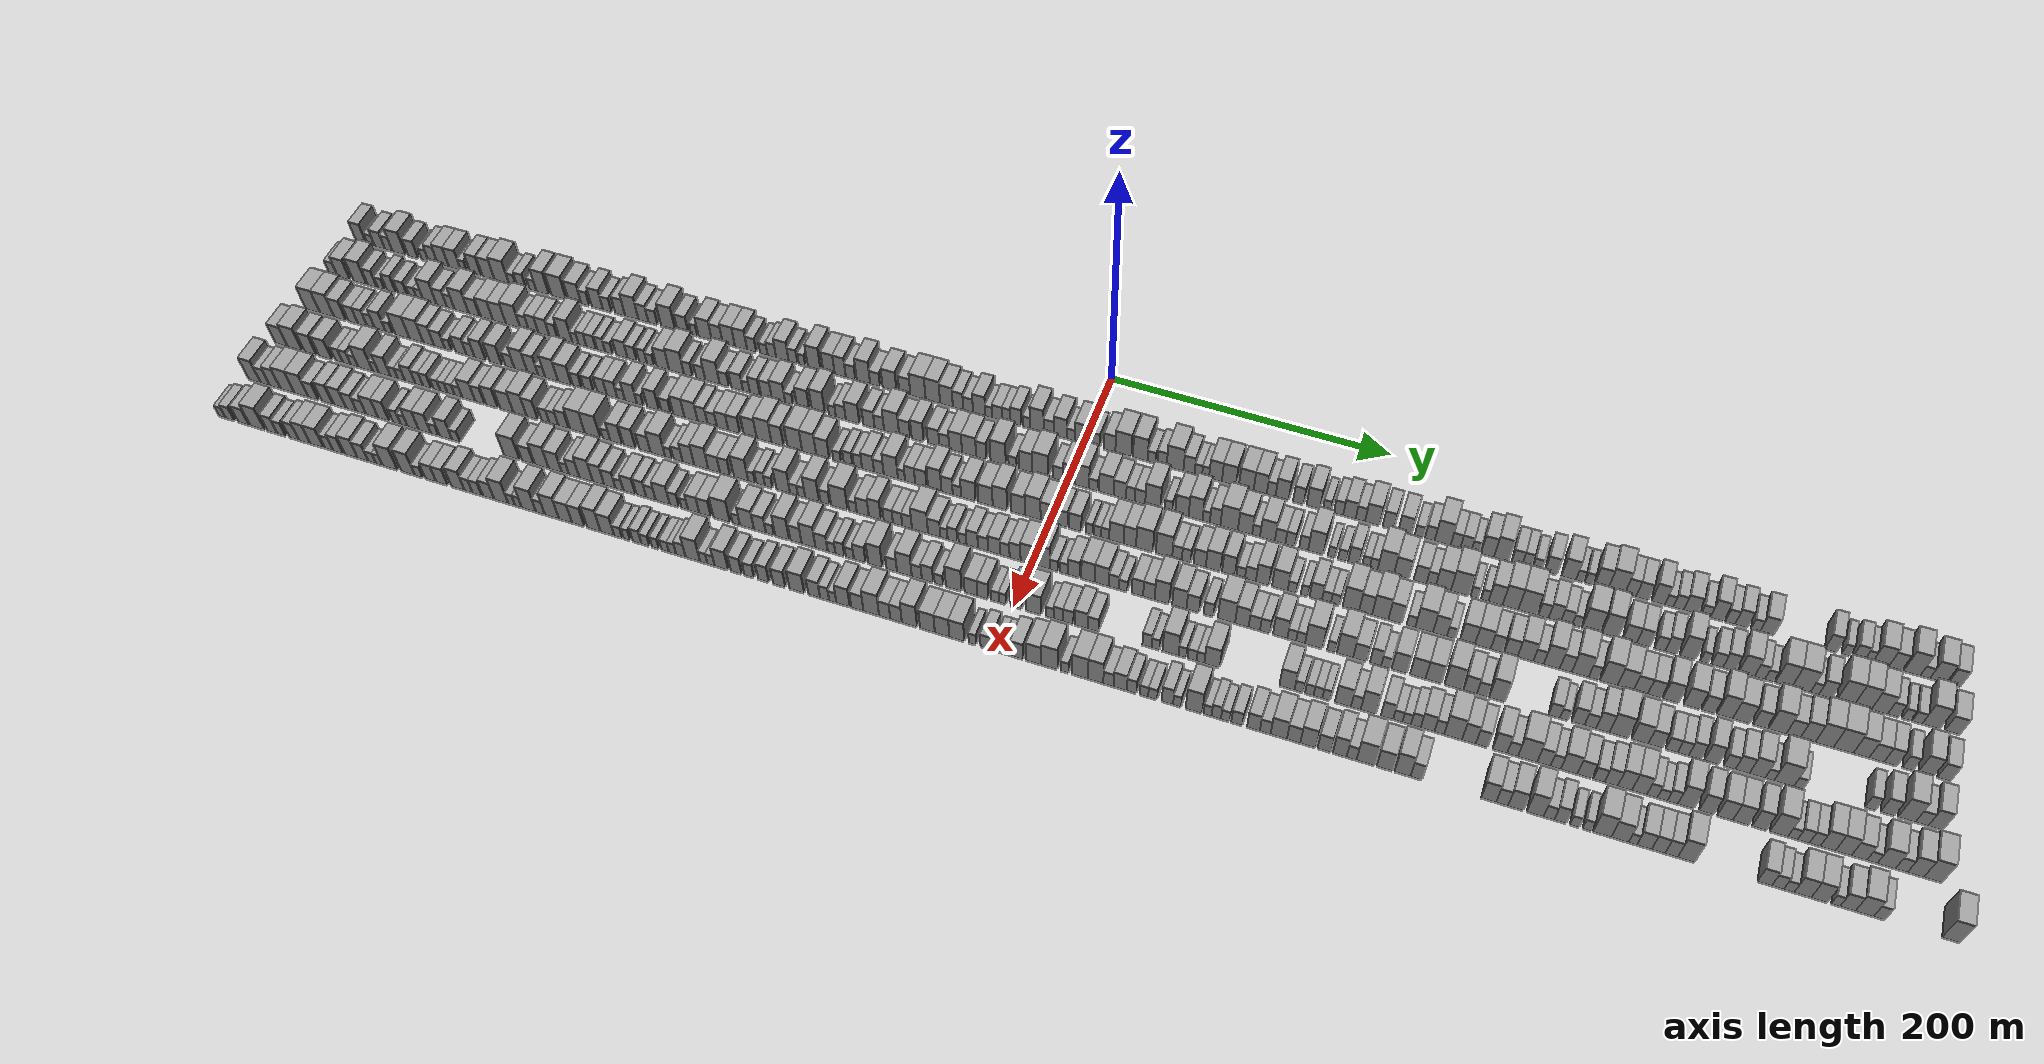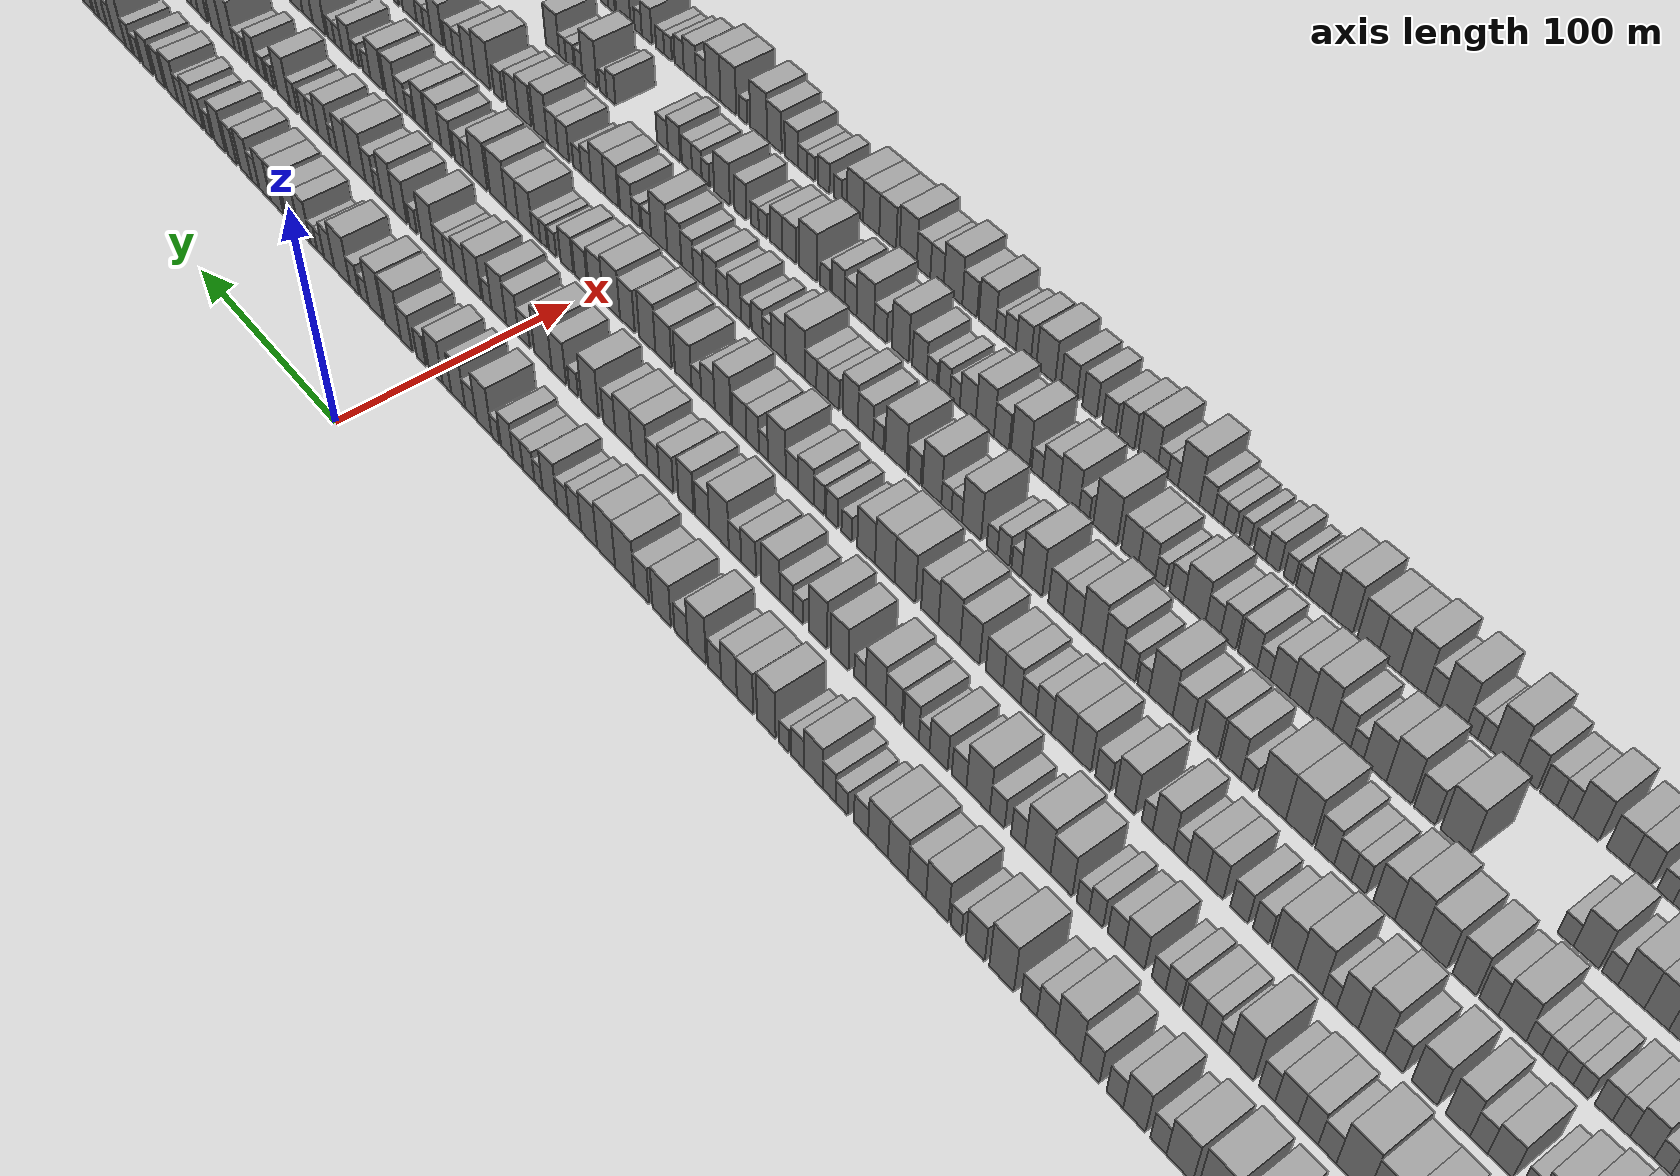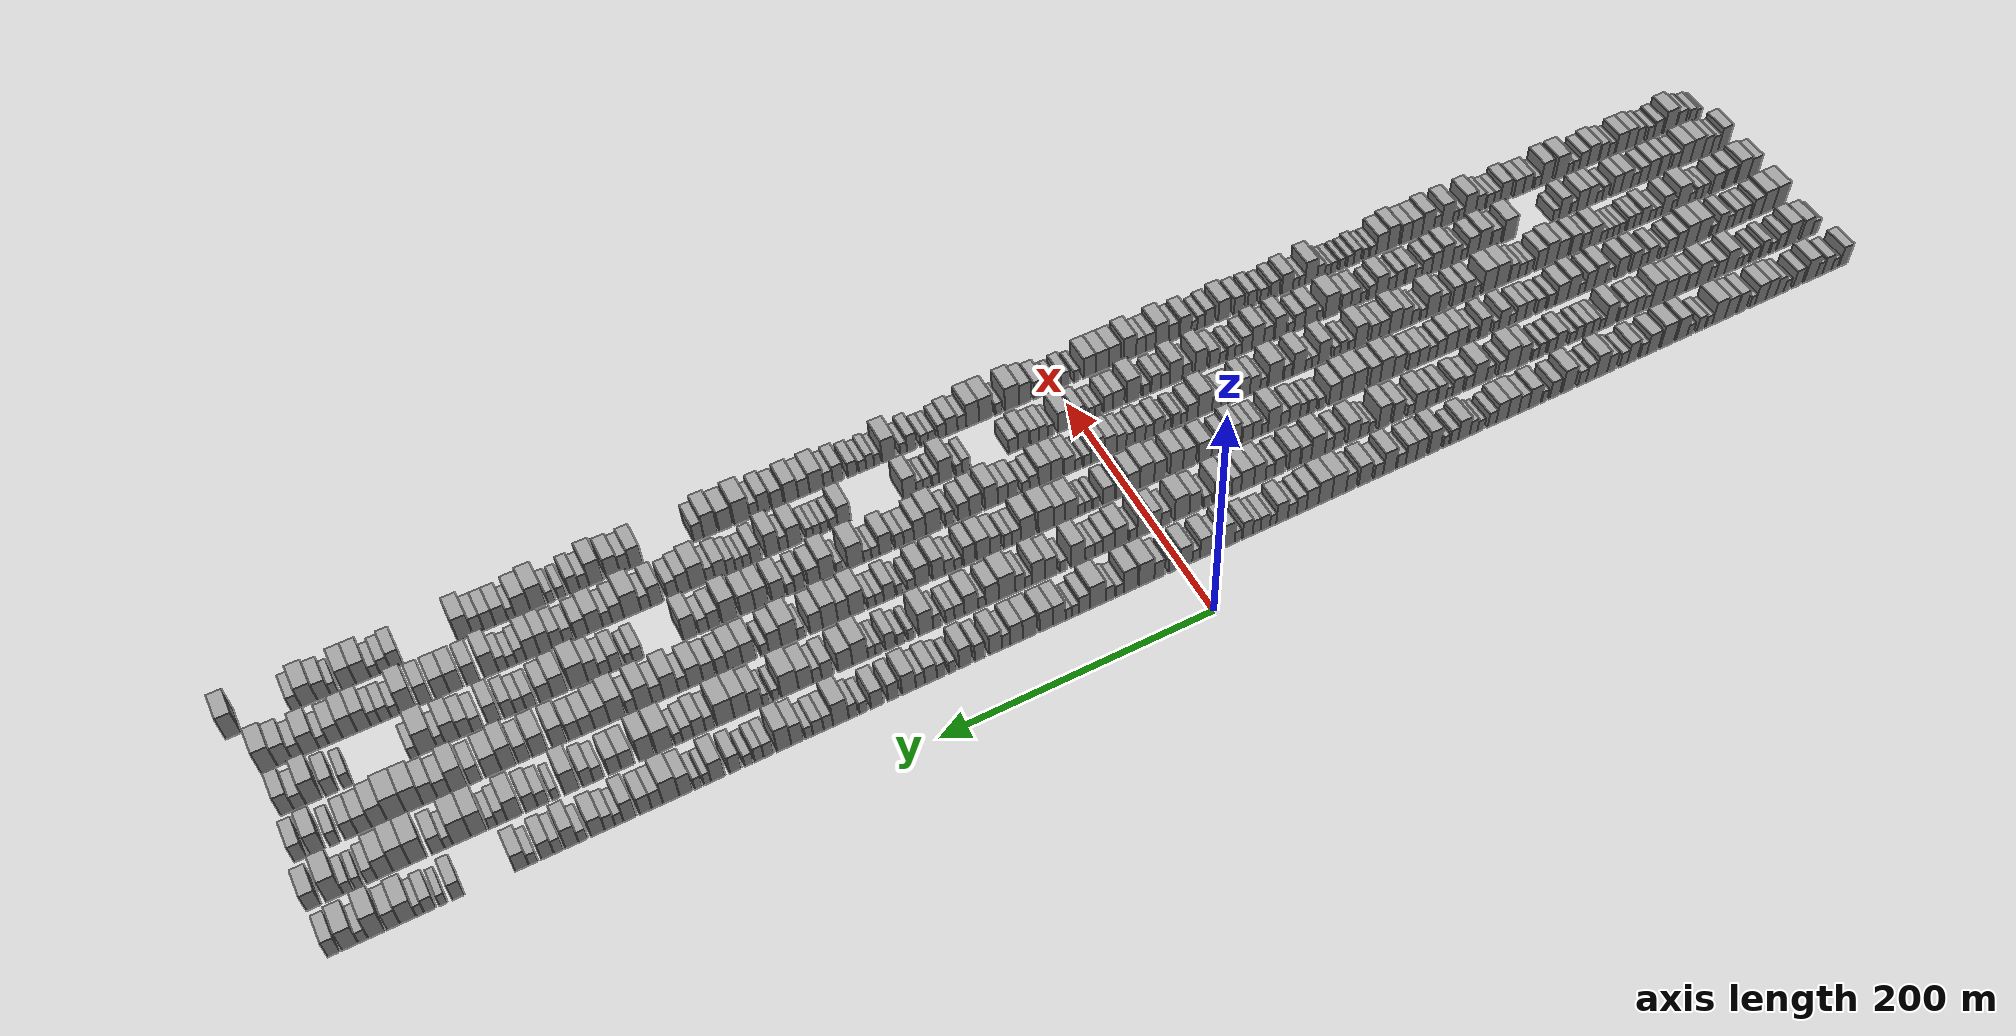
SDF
<sdf version="1.6">
 <world name="default">
  <scene>
   <sky><clouds><speed>12</speed></clouds></sky>
   <ambient>0.4 0.4 0.4 1</ambient>
   <background>0.7 0.7 0.7 1</background>
   <shadows>1</shadows>
  </scene>
  <gravity>0 0 -9.8066</gravity>
  <magnetic_field>6e-06 2.3e-05 -4.2e-05</magnetic_field>
  <physics default="0" name="default_physics" type="ode">
   <ode>
    <solver>
     <type>quick</type>
     <iters>10</iters>
     <sor>1.0</sor>
     <use_dynamic_moi_rescaling>0</use_dynamic_moi_rescaling>
    </solver>
    <constraints>
     <cfm>0</cfm>
     <erp>0.2</erp>
     <contact_max_correcting_vel>100</contact_max_correcting_vel>
     <contact_surface_layer>0.001</contact_surface_layer>
    </constraints>
   </ode>
   <max_step_size>0.004</max_step_size>
   <real_time_factor>1</real_time_factor>
   <real_time_update_rate>250</real_time_update_rate>
  </physics>
  <light name="sun" type="directional">
   <pose>0 0 10 0 0 0</pose>
   <diffuse>0.8 0.8 0.8 1</diffuse>
   <specular>0.2 0.2 0.2 1</specular>
   <attenuation>
    <range>1000</range>
    <constant>0.9</constant>
    <linear>0.01</linear>
    <quadratic>0.001</quadratic>
   </attenuation>
   <direction>-0.5 0.1 -0.9</direction>
  </light>
  <model name="building_1">
   <static>1</static>
   <pose>50.0000 -563.6342 0 0.000000 0.000000 0.000000</pose>
   <link name="link">
    <pose>0 0 10.50 0 0 0</pose>
    <collision name="collision"><geometry><box><size>20.0000 8.7316 21.0000</size></box></geometry></collision>
    <visual name="visual">
     <cast_shadows>0</cast_shadows>
     <geometry><box><size>20.0000 8.7316 21.0000</size></box></geometry>
     <material>
      <script>
       <uri>model://grey_wall/materials/scripts</uri>
       <uri>model://grey_wall/materials/textures</uri>
       <name>vrc/grey_wall</name>
      </script>
     </material>
    </visual>
   </link>
  </model>
  <model name="building_2">
   <static>1</static>
   <pose>50.0000 -555.2712 0 0.000000 0.000000 0.000000</pose>
   <link name="link">
    <pose>0 0 6.00 0 0 0</pose>
    <collision name="collision"><geometry><box><size>20.0000 5.9944 12.0000</size></box></geometry></collision>
    <visual name="visual">
     <cast_shadows>0</cast_shadows>
     <geometry><box><size>20.0000 5.9944 12.0000</size></box></geometry>
     <material>
      <script>
       <uri>model://grey_wall/materials/scripts</uri>
       <uri>model://grey_wall/materials/textures</uri>
       <name>vrc/grey_wall</name>
      </script>
     </material>
    </visual>
   </link>
  </model>
  <model name="building_3">
   <static>1</static>
   <pose>50.0000 -548.0050 0 0.000000 0.000000 0.000000</pose>
   <link name="link">
    <pose>0 0 9.00 0 0 0</pose>
    <collision name="collision"><geometry><box><size>20.0000 8.5379 18.0000</size></box></geometry></collision>
    <visual name="visual">
     <cast_shadows>0</cast_shadows>
     <geometry><box><size>20.0000 8.5379 18.0000</size></box></geometry>
     <material>
      <script>
       <uri>model://grey_wall/materials/scripts</uri>
       <uri>model://grey_wall/materials/textures</uri>
       <name>vrc/grey_wall</name>
      </script>
     </material>
    </visual>
   </link>
  </model>
  <model name="building_4">
   <static>1</static>
   <pose>50.0000 -540.6116 0 0.000000 0.000000 0.000000</pose>
   <link name="link">
    <pose>0 0 7.50 0 0 0</pose>
    <collision name="collision"><geometry><box><size>20.0000 6.2488 15.0000</size></box></geometry></collision>
    <visual name="visual">
     <cast_shadows>0</cast_shadows>
     <geometry><box><size>20.0000 6.2488 15.0000</size></box></geometry>
     <material>
      <script>
       <uri>model://grey_wall/materials/scripts</uri>
       <uri>model://grey_wall/materials/textures</uri>
       <name>vrc/grey_wall</name>
      </script>
     </material>
    </visual>
   </link>
  </model>
  <model name="building_5">
   <static>1</static>
   <pose>50.0000 -531.9347 0 0.000000 0.000000 0.000000</pose>
   <link name="link">
    <pose>0 0 12.00 0 0 0</pose>
    <collision name="collision"><geometry><box><size>20.0000 11.1050 24.0000</size></box></geometry></collision>
    <visual name="visual">
     <cast_shadows>0</cast_shadows>
     <geometry><box><size>20.0000 11.1050 24.0000</size></box></geometry>
     <material>
      <script>
       <uri>model://grey_wall/materials/scripts</uri>
       <uri>model://grey_wall/materials/textures</uri>
       <name>vrc/grey_wall</name>
      </script>
     </material>
    </visual>
   </link>
  </model>
  <model name="building_6">
   <static>1</static>
   <pose>50.0000 -520.2253 0 0.000000 0.000000 0.000000</pose>
   <link name="link">
    <pose>0 0 9.00 0 0 0</pose>
    <collision name="collision"><geometry><box><size>20.0000 8.3139 18.0000</size></box></geometry></collision>
    <visual name="visual">
     <cast_shadows>0</cast_shadows>
     <geometry><box><size>20.0000 8.3139 18.0000</size></box></geometry>
     <material>
      <script>
       <uri>model://grey_wall/materials/scripts</uri>
       <uri>model://grey_wall/materials/textures</uri>
       <name>vrc/grey_wall</name>
      </script>
     </material>
    </visual>
   </link>
  </model>
  <model name="building_7">
   <static>1</static>
   <pose>50.0000 -510.2209 0 0.000000 0.000000 0.000000</pose>
   <link name="link">
    <pose>0 0 6.00 0 0 0</pose>
    <collision name="collision"><geometry><box><size>20.0000 5.6948 12.0000</size></box></geometry></collision>
    <visual name="visual">
     <cast_shadows>0</cast_shadows>
     <geometry><box><size>20.0000 5.6948 12.0000</size></box></geometry>
     <material>
      <script>
       <uri>model://grey_wall/materials/scripts</uri>
       <uri>model://grey_wall/materials/textures</uri>
       <name>vrc/grey_wall</name>
      </script>
     </material>
    </visual>
   </link>
  </model>
  <model name="building_8">
   <static>1</static>
   <pose>50.0000 -503.5285 0 0.000000 0.000000 0.000000</pose>
   <link name="link">
    <pose>0 0 9.00 0 0 0</pose>
    <collision name="collision"><geometry><box><size>20.0000 7.6900 18.0000</size></box></geometry></collision>
    <visual name="visual">
     <cast_shadows>0</cast_shadows>
     <geometry><box><size>20.0000 7.6900 18.0000</size></box></geometry>
     <material>
      <script>
       <uri>model://grey_wall/materials/scripts</uri>
       <uri>model://grey_wall/materials/textures</uri>
       <name>vrc/grey_wall</name>
      </script>
     </material>
    </visual>
   </link>
  </model>
  <model name="building_9">
   <static>1</static>
   <pose>50.0000 -495.0723 0 0.000000 0.000000 0.000000</pose>
   <link name="link">
    <pose>0 0 10.50 0 0 0</pose>
    <collision name="collision"><geometry><box><size>20.0000 9.2223 21.0000</size></box></geometry></collision>
    <visual name="visual">
     <cast_shadows>0</cast_shadows>
     <geometry><box><size>20.0000 9.2223 21.0000</size></box></geometry>
     <material>
      <script>
       <uri>model://grey_wall/materials/scripts</uri>
       <uri>model://grey_wall/materials/textures</uri>
       <name>vrc/grey_wall</name>
      </script>
     </material>
    </visual>
   </link>
  </model>
  <model name="building_10">
   <static>1</static>
   <pose>50.0000 -485.5400 0 0.000000 0.000000 0.000000</pose>
   <link name="link">
    <pose>0 0 10.50 0 0 0</pose>
    <collision name="collision"><geometry><box><size>20.0000 9.8423 21.0000</size></box></geometry></collision>
    <visual name="visual">
     <cast_shadows>0</cast_shadows>
     <geometry><box><size>20.0000 9.8423 21.0000</size></box></geometry>
     <material>
      <script>
       <uri>model://grey_wall/materials/scripts</uri>
       <uri>model://grey_wall/materials/textures</uri>
       <name>vrc/grey_wall</name>
      </script>
     </material>
    </visual>
   </link>
  </model>
  <model name="building_11">
   <static>1</static>
   <pose>50.0000 -478.1424 0 0.000000 0.000000 0.000000</pose>
   <link name="link">
    <pose>0 0 6.00 0 0 0</pose>
    <collision name="collision"><geometry><box><size>20.0000 4.9528 12.0000</size></box></geometry></collision>
    <visual name="visual">
     <cast_shadows>0</cast_shadows>
     <geometry><box><size>20.0000 4.9528 12.0000</size></box></geometry>
     <material>
      <script>
       <uri>model://grey_wall/materials/scripts</uri>
       <uri>model://grey_wall/materials/textures</uri>
       <name>vrc/grey_wall</name>
      </script>
     </material>
    </visual>
   </link>
  </model>
  <model name="building_12">
   <static>1</static>
   <pose>50.0000 -468.2171 0 0.000000 0.000000 0.000000</pose>
   <link name="link">
    <pose>0 0 10.50 0 0 0</pose>
    <collision name="collision"><geometry><box><size>20.0000 8.8978 21.0000</size></box></geometry></collision>
    <visual name="visual">
     <cast_shadows>0</cast_shadows>
     <geometry><box><size>20.0000 8.8978 21.0000</size></box></geometry>
     <material>
      <script>
       <uri>model://grey_wall/materials/scripts</uri>
       <uri>model://grey_wall/materials/textures</uri>
       <name>vrc/grey_wall</name>
      </script>
     </material>
    </visual>
   </link>
  </model>
  <model name="building_13">
   <static>1</static>
   <pose>50.0000 -457.8716 0 0.000000 0.000000 0.000000</pose>
   <link name="link">
    <pose>0 0 10.50 0 0 0</pose>
    <collision name="collision"><geometry><box><size>20.0000 9.7933 21.0000</size></box></geometry></collision>
    <visual name="visual">
     <cast_shadows>0</cast_shadows>
     <geometry><box><size>20.0000 9.7933 21.0000</size></box></geometry>
     <material>
      <script>
       <uri>model://grey_wall/materials/scripts</uri>
       <uri>model://grey_wall/materials/textures</uri>
       <name>vrc/grey_wall</name>
      </script>
     </material>
    </visual>
   </link>
  </model>
  <model name="building_14">
   <static>1</static>
   <pose>50.0000 -447.1018 0 0.000000 0.000000 0.000000</pose>
   <link name="link">
    <pose>0 0 12.00 0 0 0</pose>
    <collision name="collision"><geometry><box><size>20.0000 11.7461 24.0000</size></box></geometry></collision>
    <visual name="visual">
     <cast_shadows>0</cast_shadows>
     <geometry><box><size>20.0000 11.7461 24.0000</size></box></geometry>
     <material>
      <script>
       <uri>model://grey_wall/materials/scripts</uri>
       <uri>model://grey_wall/materials/textures</uri>
       <name>vrc/grey_wall</name>
      </script>
     </material>
    </visual>
   </link>
  </model>
  <model name="building_15">
   <static>1</static>
   <pose>50.0000 -438.4179 0 0.000000 0.000000 0.000000</pose>
   <link name="link">
    <pose>0 0 6.00 0 0 0</pose>
    <collision name="collision"><geometry><box><size>20.0000 5.6217 12.0000</size></box></geometry></collision>
    <visual name="visual">
     <cast_shadows>0</cast_shadows>
     <geometry><box><size>20.0000 5.6217 12.0000</size></box></geometry>
     <material>
      <script>
       <uri>model://grey_wall/materials/scripts</uri>
       <uri>model://grey_wall/materials/textures</uri>
       <name>vrc/grey_wall</name>
      </script>
     </material>
    </visual>
   </link>
  </model>
  <model name="building_16">
   <static>1</static>
   <pose>50.0000 -431.0832 0 0.000000 0.000000 0.000000</pose>
   <link name="link">
    <pose>0 0 7.50 0 0 0</pose>
    <collision name="collision"><geometry><box><size>20.0000 7.0478 15.0000</size></box></geometry></collision>
    <visual name="visual">
     <cast_shadows>0</cast_shadows>
     <geometry><box><size>20.0000 7.0478 15.0000</size></box></geometry>
     <material>
      <script>
       <uri>model://grey_wall/materials/scripts</uri>
       <uri>model://grey_wall/materials/textures</uri>
       <name>vrc/grey_wall</name>
      </script>
     </material>
    </visual>
   </link>
  </model>
  <model name="building_17">
   <static>1</static>
   <pose>50.0000 -421.6807 0 0.000000 0.000000 0.000000</pose>
   <link name="link">
    <pose>0 0 6.00 0 0 0</pose>
    <collision name="collision"><geometry><box><size>20.0000 5.7572 12.0000</size></box></geometry></collision>
    <visual name="visual">
     <cast_shadows>0</cast_shadows>
     <geometry><box><size>20.0000 5.7572 12.0000</size></box></geometry>
     <material>
      <script>
       <uri>model://grey_wall/materials/scripts</uri>
       <uri>model://grey_wall/materials/textures</uri>
       <name>vrc/grey_wall</name>
      </script>
     </material>
    </visual>
   </link>
  </model>
  <model name="building_18">
   <static>1</static>
   <pose>50.0000 -413.7664 0 0.000000 0.000000 0.000000</pose>
   <link name="link">
    <pose>0 0 12.00 0 0 0</pose>
    <collision name="collision"><geometry><box><size>20.0000 10.0714 24.0000</size></box></geometry></collision>
    <visual name="visual">
     <cast_shadows>0</cast_shadows>
     <geometry><box><size>20.0000 10.0714 24.0000</size></box></geometry>
     <material>
      <script>
       <uri>model://grey_wall/materials/scripts</uri>
       <uri>model://grey_wall/materials/textures</uri>
       <name>vrc/grey_wall</name>
      </script>
     </material>
    </visual>
   </link>
  </model>
  <model name="building_19">
   <static>1</static>
   <pose>50.0000 -400.7920 0 0.000000 0.000000 0.000000</pose>
   <link name="link">
    <pose>0 0 12.00 0 0 0</pose>
    <collision name="collision"><geometry><box><size>20.0000 11.8775 24.0000</size></box></geometry></collision>
    <visual name="visual">
     <cast_shadows>0</cast_shadows>
     <geometry><box><size>20.0000 11.8775 24.0000</size></box></geometry>
     <material>
      <script>
       <uri>model://grey_wall/materials/scripts</uri>
       <uri>model://grey_wall/materials/textures</uri>
       <name>vrc/grey_wall</name>
      </script>
     </material>
    </visual>
   </link>
  </model>
  <model name="building_20">
   <static>1</static>
   <pose>50.0000 -387.7106 0 0.000000 0.000000 0.000000</pose>
   <link name="link">
    <pose>0 0 10.50 0 0 0</pose>
    <collision name="collision"><geometry><box><size>20.0000 10.2854 21.0000</size></box></geometry></collision>
    <visual name="visual">
     <cast_shadows>0</cast_shadows>
     <geometry><box><size>20.0000 10.2854 21.0000</size></box></geometry>
     <material>
      <script>
       <uri>model://grey_wall/materials/scripts</uri>
       <uri>model://grey_wall/materials/textures</uri>
       <name>vrc/grey_wall</name>
      </script>
     </material>
    </visual>
   </link>
  </model>
  <model name="building_21">
   <static>1</static>
   <pose>50.0000 -379.3886 0 0.000000 0.000000 0.000000</pose>
   <link name="link">
    <pose>0 0 7.50 0 0 0</pose>
    <collision name="collision"><geometry><box><size>20.0000 6.3586 15.0000</size></box></geometry></collision>
    <visual name="visual">
     <cast_shadows>0</cast_shadows>
     <geometry><box><size>20.0000 6.3586 15.0000</size></box></geometry>
     <material>
      <script>
       <uri>model://grey_wall/materials/scripts</uri>
       <uri>model://grey_wall/materials/textures</uri>
       <name>vrc/grey_wall</name>
      </script>
     </material>
    </visual>
   </link>
  </model>
  <model name="building_22">
   <static>1</static>
   <pose>50.0000 -369.7194 0 0.000000 0.000000 0.000000</pose>
   <link name="link">
    <pose>0 0 10.50 0 0 0</pose>
    <collision name="collision"><geometry><box><size>20.0000 8.9800 21.0000</size></box></geometry></collision>
    <visual name="visual">
     <cast_shadows>0</cast_shadows>
     <geometry><box><size>20.0000 8.9800 21.0000</size></box></geometry>
     <material>
      <script>
       <uri>model://grey_wall/materials/scripts</uri>
       <uri>model://grey_wall/materials/textures</uri>
       <name>vrc/grey_wall</name>
      </script>
     </material>
    </visual>
   </link>
  </model>
  <model name="building_23">
   <static>1</static>
   <pose>50.0000 -361.8570 0 0.000000 0.000000 0.000000</pose>
   <link name="link">
    <pose>0 0 7.50 0 0 0</pose>
    <collision name="collision"><geometry><box><size>20.0000 6.7448 15.0000</size></box></geometry></collision>
    <visual name="visual">
     <cast_shadows>0</cast_shadows>
     <geometry><box><size>20.0000 6.7448 15.0000</size></box></geometry>
     <material>
      <script>
       <uri>model://grey_wall/materials/scripts</uri>
       <uri>model://grey_wall/materials/textures</uri>
       <name>vrc/grey_wall</name>
      </script>
     </material>
    </visual>
   </link>
  </model>
  <model name="building_24">
   <static>1</static>
   <pose>50.0000 -351.5566 0 0.000000 0.000000 0.000000</pose>
   <link name="link">
    <pose>0 0 9.00 0 0 0</pose>
    <collision name="collision"><geometry><box><size>20.0000 7.8558 18.0000</size></box></geometry></collision>
    <visual name="visual">
     <cast_shadows>0</cast_shadows>
     <geometry><box><size>20.0000 7.8558 18.0000</size></box></geometry>
     <material>
      <script>
       <uri>model://grey_wall/materials/scripts</uri>
       <uri>model://grey_wall/materials/textures</uri>
       <name>vrc/grey_wall</name>
      </script>
     </material>
    </visual>
   </link>
  </model>
  <model name="building_25">
   <static>1</static>
   <pose>50.0000 -342.3098 0 0.000000 0.000000 0.000000</pose>
   <link name="link">
    <pose>0 0 12.00 0 0 0</pose>
    <collision name="collision"><geometry><box><size>20.0000 10.6379 24.0000</size></box></geometry></collision>
    <visual name="visual">
     <cast_shadows>0</cast_shadows>
     <geometry><box><size>20.0000 10.6379 24.0000</size></box></geometry>
     <material>
      <script>
       <uri>model://grey_wall/materials/scripts</uri>
       <uri>model://grey_wall/materials/textures</uri>
       <name>vrc/grey_wall</name>
      </script>
     </material>
    </visual>
   </link>
  </model>
  <model name="building_26">
   <static>1</static>
   <pose>50.0000 -333.0607 0 0.000000 0.000000 0.000000</pose>
   <link name="link">
    <pose>0 0 9.00 0 0 0</pose>
    <collision name="collision"><geometry><box><size>20.0000 7.8603 18.0000</size></box></geometry></collision>
    <visual name="visual">
     <cast_shadows>0</cast_shadows>
     <geometry><box><size>20.0000 7.8603 18.0000</size></box></geometry>
     <material>
      <script>
       <uri>model://grey_wall/materials/scripts</uri>
       <uri>model://grey_wall/materials/textures</uri>
       <name>vrc/grey_wall</name>
      </script>
     </material>
    </visual>
   </link>
  </model>
  <model name="building_27">
   <static>1</static>
   <pose>50.0000 -325.6016 0 0.000000 0.000000 0.000000</pose>
   <link name="link">
    <pose>0 0 7.50 0 0 0</pose>
    <collision name="collision"><geometry><box><size>20.0000 7.0579 15.0000</size></box></geometry></collision>
    <visual name="visual">
     <cast_shadows>0</cast_shadows>
     <geometry><box><size>20.0000 7.0579 15.0000</size></box></geometry>
     <material>
      <script>
       <uri>model://grey_wall/materials/scripts</uri>
       <uri>model://grey_wall/materials/textures</uri>
       <name>vrc/grey_wall</name>
      </script>
     </material>
    </visual>
   </link>
  </model>
  <model name="building_28">
   <static>1</static>
   <pose>50.0000 -313.6420 0 0.000000 0.000000 0.000000</pose>
   <link name="link">
    <pose>0 0 12.00 0 0 0</pose>
    <collision name="collision"><geometry><box><size>20.0000 10.8613 24.0000</size></box></geometry></collision>
    <visual name="visual">
     <cast_shadows>0</cast_shadows>
     <geometry><box><size>20.0000 10.8613 24.0000</size></box></geometry>
     <material>
      <script>
       <uri>model://grey_wall/materials/scripts</uri>
       <uri>model://grey_wall/materials/textures</uri>
       <name>vrc/grey_wall</name>
      </script>
     </material>
    </visual>
   </link>
  </model>
  <model name="building_29">
   <static>1</static>
   <pose>50.0000 -301.9269 0 0.000000 0.000000 0.000000</pose>
   <link name="link">
    <pose>0 0 9.00 0 0 0</pose>
    <collision name="collision"><geometry><box><size>20.0000 8.5691 18.0000</size></box></geometry></collision>
    <visual name="visual">
     <cast_shadows>0</cast_shadows>
     <geometry><box><size>20.0000 8.5691 18.0000</size></box></geometry>
     <material>
      <script>
       <uri>model://grey_wall/materials/scripts</uri>
       <uri>model://grey_wall/materials/textures</uri>
       <name>vrc/grey_wall</name>
      </script>
     </material>
    </visual>
   </link>
  </model>
  <model name="building_30">
   <static>1</static>
   <pose>50.0000 -293.1799 0 0.000000 0.000000 0.000000</pose>
   <link name="link">
    <pose>0 0 6.00 0 0 0</pose>
    <collision name="collision"><geometry><box><size>20.0000 4.9248 12.0000</size></box></geometry></collision>
    <visual name="visual">
     <cast_shadows>0</cast_shadows>
     <geometry><box><size>20.0000 4.9248 12.0000</size></box></geometry>
     <material>
      <script>
       <uri>model://grey_wall/materials/scripts</uri>
       <uri>model://grey_wall/materials/textures</uri>
       <name>vrc/grey_wall</name>
      </script>
     </material>
    </visual>
   </link>
  </model>
  <model name="building_31">
   <static>1</static>
   <pose>50.0000 -284.5382 0 0.000000 0.000000 0.000000</pose>
   <link name="link">
    <pose>0 0 10.50 0 0 0</pose>
    <collision name="collision"><geometry><box><size>20.0000 10.3585 21.0000</size></box></geometry></collision>
    <visual name="visual">
     <cast_shadows>0</cast_shadows>
     <geometry><box><size>20.0000 10.3585 21.0000</size></box></geometry>
     <material>
      <script>
       <uri>model://grey_wall/materials/scripts</uri>
       <uri>model://grey_wall/materials/textures</uri>
       <name>vrc/grey_wall</name>
      </script>
     </material>
    </visual>
   </link>
  </model>
  <model name="building_32">
   <static>1</static>
   <pose>50.0000 -275.1140 0 0.000000 0.000000 0.000000</pose>
   <link name="link">
    <pose>0 0 9.00 0 0 0</pose>
    <collision name="collision"><geometry><box><size>20.0000 8.4899 18.0000</size></box></geometry></collision>
    <visual name="visual">
     <cast_shadows>0</cast_shadows>
     <geometry><box><size>20.0000 8.4899 18.0000</size></box></geometry>
     <material>
      <script>
       <uri>model://grey_wall/materials/scripts</uri>
       <uri>model://grey_wall/materials/textures</uri>
       <name>vrc/grey_wall</name>
      </script>
     </material>
    </visual>
   </link>
  </model>
  <model name="building_33">
   <static>1</static>
   <pose>50.0000 -266.1112 0 0.000000 0.000000 0.000000</pose>
   <link name="link">
    <pose>0 0 10.50 0 0 0</pose>
    <collision name="collision"><geometry><box><size>20.0000 9.5158 21.0000</size></box></geometry></collision>
    <visual name="visual">
     <cast_shadows>0</cast_shadows>
     <geometry><box><size>20.0000 9.5158 21.0000</size></box></geometry>
     <material>
      <script>
       <uri>model://grey_wall/materials/scripts</uri>
       <uri>model://grey_wall/materials/textures</uri>
       <name>vrc/grey_wall</name>
      </script>
     </material>
    </visual>
   </link>
  </model>
  <model name="building_34">
   <static>1</static>
   <pose>50.0000 -256.5967 0 0.000000 0.000000 0.000000</pose>
   <link name="link">
    <pose>0 0 10.50 0 0 0</pose>
    <collision name="collision"><geometry><box><size>20.0000 9.5131 21.0000</size></box></geometry></collision>
    <visual name="visual">
     <cast_shadows>0</cast_shadows>
     <geometry><box><size>20.0000 9.5131 21.0000</size></box></geometry>
     <material>
      <script>
       <uri>model://grey_wall/materials/scripts</uri>
       <uri>model://grey_wall/materials/textures</uri>
       <name>vrc/grey_wall</name>
      </script>
     </material>
    </visual>
   </link>
  </model>
  <model name="building_35">
   <static>1</static>
   <pose>50.0000 -248.3557 0 0.000000 0.000000 0.000000</pose>
   <link name="link">
    <pose>0 0 7.50 0 0 0</pose>
    <collision name="collision"><geometry><box><size>20.0000 6.9689 15.0000</size></box></geometry></collision>
    <visual name="visual">
     <cast_shadows>0</cast_shadows>
     <geometry><box><size>20.0000 6.9689 15.0000</size></box></geometry>
     <material>
      <script>
       <uri>model://grey_wall/materials/scripts</uri>
       <uri>model://grey_wall/materials/textures</uri>
       <name>vrc/grey_wall</name>
      </script>
     </material>
    </visual>
   </link>
  </model>
  <model name="building_36">
   <static>1</static>
   <pose>50.0000 -238.9453 0 0.000000 0.000000 0.000000</pose>
   <link name="link">
    <pose>0 0 6.00 0 0 0</pose>
    <collision name="collision"><geometry><box><size>20.0000 5.8519 12.0000</size></box></geometry></collision>
    <visual name="visual">
     <cast_shadows>0</cast_shadows>
     <geometry><box><size>20.0000 5.8519 12.0000</size></box></geometry>
     <material>
      <script>
       <uri>model://grey_wall/materials/scripts</uri>
       <uri>model://grey_wall/materials/textures</uri>
       <name>vrc/grey_wall</name>
      </script>
     </material>
    </visual>
   </link>
  </model>
  <model name="building_37">
   <static>1</static>
   <pose>50.0000 -232.7701 0 0.000000 0.000000 0.000000</pose>
   <link name="link">
    <pose>0 0 7.50 0 0 0</pose>
    <collision name="collision"><geometry><box><size>20.0000 6.4985 15.0000</size></box></geometry></collision>
    <visual name="visual">
     <cast_shadows>0</cast_shadows>
     <geometry><box><size>20.0000 6.4985 15.0000</size></box></geometry>
     <material>
      <script>
       <uri>model://grey_wall/materials/scripts</uri>
       <uri>model://grey_wall/materials/textures</uri>
       <name>vrc/grey_wall</name>
      </script>
     </material>
    </visual>
   </link>
  </model>
  <model name="building_38">
   <static>1</static>
   <pose>50.0000 -224.6949 0 0.000000 0.000000 0.000000</pose>
   <link name="link">
    <pose>0 0 10.50 0 0 0</pose>
    <collision name="collision"><geometry><box><size>20.0000 9.6519 21.0000</size></box></geometry></collision>
    <visual name="visual">
     <cast_shadows>0</cast_shadows>
     <geometry><box><size>20.0000 9.6519 21.0000</size></box></geometry>
     <material>
      <script>
       <uri>model://grey_wall/materials/scripts</uri>
       <uri>model://grey_wall/materials/textures</uri>
       <name>vrc/grey_wall</name>
      </script>
     </material>
    </visual>
   </link>
  </model>
  <model name="building_39">
   <static>1</static>
   <pose>50.0000 -216.5163 0 0.000000 0.000000 0.000000</pose>
   <link name="link">
    <pose>0 0 7.50 0 0 0</pose>
    <collision name="collision"><geometry><box><size>20.0000 6.7052 15.0000</size></box></geometry></collision>
    <visual name="visual">
     <cast_shadows>0</cast_shadows>
     <geometry><box><size>20.0000 6.7052 15.0000</size></box></geometry>
     <material>
      <script>
       <uri>model://grey_wall/materials/scripts</uri>
       <uri>model://grey_wall/materials/textures</uri>
       <name>vrc/grey_wall</name>
      </script>
     </material>
    </visual>
   </link>
  </model>
  <model name="building_40">
   <static>1</static>
   <pose>50.0000 -209.7153 0 0.000000 0.000000 0.000000</pose>
   <link name="link">
    <pose>0 0 6.00 0 0 0</pose>
    <collision name="collision"><geometry><box><size>20.0000 4.8969 12.0000</size></box></geometry></collision>
    <visual name="visual">
     <cast_shadows>0</cast_shadows>
     <geometry><box><size>20.0000 4.8969 12.0000</size></box></geometry>
     <material>
      <script>
       <uri>model://grey_wall/materials/scripts</uri>
       <uri>model://grey_wall/materials/textures</uri>
       <name>vrc/grey_wall</name>
      </script>
     </material>
    </visual>
   </link>
  </model>
  <model name="building_41">
   <static>1</static>
   <pose>50.0000 -200.3876 0 0.000000 0.000000 0.000000</pose>
   <link name="link">
    <pose>0 0 12.00 0 0 0</pose>
    <collision name="collision"><geometry><box><size>20.0000 9.7583 24.0000</size></box></geometry></collision>
    <visual name="visual">
     <cast_shadows>0</cast_shadows>
     <geometry><box><size>20.0000 9.7583 24.0000</size></box></geometry>
     <material>
      <script>
       <uri>model://grey_wall/materials/scripts</uri>
       <uri>model://grey_wall/materials/textures</uri>
       <name>vrc/grey_wall</name>
      </script>
     </material>
    </visual>
   </link>
  </model>
  <model name="building_42">
   <static>1</static>
   <pose>50.0000 -189.1490 0 0.000000 0.000000 0.000000</pose>
   <link name="link">
    <pose>0 0 10.50 0 0 0</pose>
    <collision name="collision"><geometry><box><size>20.0000 8.7190 21.0000</size></box></geometry></collision>
    <visual name="visual">
     <cast_shadows>0</cast_shadows>
     <geometry><box><size>20.0000 8.7190 21.0000</size></box></geometry>
     <material>
      <script>
       <uri>model://grey_wall/materials/scripts</uri>
       <uri>model://grey_wall/materials/textures</uri>
       <name>vrc/grey_wall</name>
      </script>
     </material>
    </visual>
   </link>
  </model>
  <model name="building_43">
   <static>1</static>
   <pose>50.0000 -180.5831 0 0.000000 0.000000 0.000000</pose>
   <link name="link">
    <pose>0 0 10.50 0 0 0</pose>
    <collision name="collision"><geometry><box><size>20.0000 8.4128 21.0000</size></box></geometry></collision>
    <visual name="visual">
     <cast_shadows>0</cast_shadows>
     <geometry><box><size>20.0000 8.4128 21.0000</size></box></geometry>
     <material>
      <script>
       <uri>model://grey_wall/materials/scripts</uri>
       <uri>model://grey_wall/materials/textures</uri>
       <name>vrc/grey_wall</name>
      </script>
     </material>
    </visual>
   </link>
  </model>
  <model name="building_44">
   <static>1</static>
   <pose>50.0000 -172.7457 0 0.000000 0.000000 0.000000</pose>
   <link name="link">
    <pose>0 0 7.50 0 0 0</pose>
    <collision name="collision"><geometry><box><size>20.0000 7.2621 15.0000</size></box></geometry></collision>
    <visual name="visual">
     <cast_shadows>0</cast_shadows>
     <geometry><box><size>20.0000 7.2621 15.0000</size></box></geometry>
     <material>
      <script>
       <uri>model://grey_wall/materials/scripts</uri>
       <uri>model://grey_wall/materials/textures</uri>
       <name>vrc/grey_wall</name>
      </script>
     </material>
    </visual>
   </link>
  </model>
  <model name="building_45">
   <static>1</static>
   <pose>50.0000 -163.0519 0 0.000000 0.000000 0.000000</pose>
   <link name="link">
    <pose>0 0 12.00 0 0 0</pose>
    <collision name="collision"><geometry><box><size>20.0000 10.1255 24.0000</size></box></geometry></collision>
    <visual name="visual">
     <cast_shadows>0</cast_shadows>
     <geometry><box><size>20.0000 10.1255 24.0000</size></box></geometry>
     <material>
      <script>
       <uri>model://grey_wall/materials/scripts</uri>
       <uri>model://grey_wall/materials/textures</uri>
       <name>vrc/grey_wall</name>
      </script>
     </material>
    </visual>
   </link>
  </model>
  <model name="building_46">
   <static>1</static>
   <pose>50.0000 -154.2886 0 0.000000 0.000000 0.000000</pose>
   <link name="link">
    <pose>0 0 7.50 0 0 0</pose>
    <collision name="collision"><geometry><box><size>20.0000 7.4011 15.0000</size></box></geometry></collision>
    <visual name="visual">
     <cast_shadows>0</cast_shadows>
     <geometry><box><size>20.0000 7.4011 15.0000</size></box></geometry>
     <material>
      <script>
       <uri>model://grey_wall/materials/scripts</uri>
       <uri>model://grey_wall/materials/textures</uri>
       <name>vrc/grey_wall</name>
      </script>
     </material>
    </visual>
   </link>
  </model>
  <model name="building_47">
   <static>1</static>
   <pose>50.0000 -143.3607 0 0.000000 0.000000 0.000000</pose>
   <link name="link">
    <pose>0 0 10.50 0 0 0</pose>
    <collision name="collision"><geometry><box><size>20.0000 10.4546 21.0000</size></box></geometry></collision>
    <visual name="visual">
     <cast_shadows>0</cast_shadows>
     <geometry><box><size>20.0000 10.4546 21.0000</size></box></geometry>
     <material>
      <script>
       <uri>model://grey_wall/materials/scripts</uri>
       <uri>model://grey_wall/materials/textures</uri>
       <name>vrc/grey_wall</name>
      </script>
     </material>
    </visual>
   </link>
  </model>
  <model name="building_48">
   <static>1</static>
   <pose>50.0000 -131.9639 0 0.000000 0.000000 0.000000</pose>
   <link name="link">
    <pose>0 0 9.00 0 0 0</pose>
    <collision name="collision"><geometry><box><size>20.0000 8.3391 18.0000</size></box></geometry></collision>
    <visual name="visual">
     <cast_shadows>0</cast_shadows>
     <geometry><box><size>20.0000 8.3391 18.0000</size></box></geometry>
     <material>
      <script>
       <uri>model://grey_wall/materials/scripts</uri>
       <uri>model://grey_wall/materials/textures</uri>
       <name>vrc/grey_wall</name>
      </script>
     </material>
    </visual>
   </link>
  </model>
  <model name="building_49">
   <static>1</static>
   <pose>50.0000 -122.1106 0 0.000000 0.000000 0.000000</pose>
   <link name="link">
    <pose>0 0 12.00 0 0 0</pose>
    <collision name="collision"><geometry><box><size>20.0000 11.3675 24.0000</size></box></geometry></collision>
    <visual name="visual">
     <cast_shadows>0</cast_shadows>
     <geometry><box><size>20.0000 11.3675 24.0000</size></box></geometry>
     <material>
      <script>
       <uri>model://grey_wall/materials/scripts</uri>
       <uri>model://grey_wall/materials/textures</uri>
       <name>vrc/grey_wall</name>
      </script>
     </material>
    </visual>
   </link>
  </model>
  <model name="building_50">
   <static>1</static>
   <pose>50.0000 -111.0496 0 0.000000 0.000000 0.000000</pose>
   <link name="link">
    <pose>0 0 12.00 0 0 0</pose>
    <collision name="collision"><geometry><box><size>20.0000 10.7545 24.0000</size></box></geometry></collision>
    <visual name="visual">
     <cast_shadows>0</cast_shadows>
     <geometry><box><size>20.0000 10.7545 24.0000</size></box></geometry>
     <material>
      <script>
       <uri>model://grey_wall/materials/scripts</uri>
       <uri>model://grey_wall/materials/textures</uri>
       <name>vrc/grey_wall</name>
      </script>
     </material>
    </visual>
   </link>
  </model>
  <model name="building_51">
   <static>1</static>
   <pose>50.0000 -100.9385 0 0.000000 0.000000 0.000000</pose>
   <link name="link">
    <pose>0 0 10.50 0 0 0</pose>
    <collision name="collision"><geometry><box><size>20.0000 9.4676 21.0000</size></box></geometry></collision>
    <visual name="visual">
     <cast_shadows>0</cast_shadows>
     <geometry><box><size>20.0000 9.4676 21.0000</size></box></geometry>
     <material>
      <script>
       <uri>model://grey_wall/materials/scripts</uri>
       <uri>model://grey_wall/materials/textures</uri>
       <name>vrc/grey_wall</name>
      </script>
     </material>
    </visual>
   </link>
  </model>
  <model name="building_52">
   <static>1</static>
   <pose>50.0000 -92.3788 0 0.000000 0.000000 0.000000</pose>
   <link name="link">
    <pose>0 0 9.00 0 0 0</pose>
    <collision name="collision"><geometry><box><size>20.0000 7.6519 18.0000</size></box></geometry></collision>
    <visual name="visual">
     <cast_shadows>0</cast_shadows>
     <geometry><box><size>20.0000 7.6519 18.0000</size></box></geometry>
     <material>
      <script>
       <uri>model://grey_wall/materials/scripts</uri>
       <uri>model://grey_wall/materials/textures</uri>
       <name>vrc/grey_wall</name>
      </script>
     </material>
    </visual>
   </link>
  </model>
  <model name="building_53">
   <static>1</static>
   <pose>50.0000 -84.9520 0 0.000000 0.000000 0.000000</pose>
   <link name="link">
    <pose>0 0 7.50 0 0 0</pose>
    <collision name="collision"><geometry><box><size>20.0000 7.2017 15.0000</size></box></geometry></collision>
    <visual name="visual">
     <cast_shadows>0</cast_shadows>
     <geometry><box><size>20.0000 7.2017 15.0000</size></box></geometry>
     <material>
      <script>
       <uri>model://grey_wall/materials/scripts</uri>
       <uri>model://grey_wall/materials/textures</uri>
       <name>vrc/grey_wall</name>
      </script>
     </material>
    </visual>
   </link>
  </model>
  <model name="building_54">
   <static>1</static>
   <pose>50.0000 -76.8477 0 0.000000 0.000000 0.000000</pose>
   <link name="link">
    <pose>0 0 10.50 0 0 0</pose>
    <collision name="collision"><geometry><box><size>20.0000 9.0068 21.0000</size></box></geometry></collision>
    <visual name="visual">
     <cast_shadows>0</cast_shadows>
     <geometry><box><size>20.0000 9.0068 21.0000</size></box></geometry>
     <material>
      <script>
       <uri>model://grey_wall/materials/scripts</uri>
       <uri>model://grey_wall/materials/textures</uri>
       <name>vrc/grey_wall</name>
      </script>
     </material>
    </visual>
   </link>
  </model>
  <model name="building_55">
   <static>1</static>
   <pose>50.0000 -69.8082 0 0.000000 0.000000 0.000000</pose>
   <link name="link">
    <pose>0 0 6.00 0 0 0</pose>
    <collision name="collision"><geometry><box><size>20.0000 5.0724 12.0000</size></box></geometry></collision>
    <visual name="visual">
     <cast_shadows>0</cast_shadows>
     <geometry><box><size>20.0000 5.0724 12.0000</size></box></geometry>
     <material>
      <script>
       <uri>model://grey_wall/materials/scripts</uri>
       <uri>model://grey_wall/materials/textures</uri>
       <name>vrc/grey_wall</name>
      </script>
     </material>
    </visual>
   </link>
  </model>
  <model name="building_56">
   <static>1</static>
   <pose>50.0000 -63.5897 0 0.000000 0.000000 0.000000</pose>
   <link name="link">
    <pose>0 0 7.50 0 0 0</pose>
    <collision name="collision"><geometry><box><size>20.0000 7.3645 15.0000</size></box></geometry></collision>
    <visual name="visual">
     <cast_shadows>0</cast_shadows>
     <geometry><box><size>20.0000 7.3645 15.0000</size></box></geometry>
     <material>
      <script>
       <uri>model://grey_wall/materials/scripts</uri>
       <uri>model://grey_wall/materials/textures</uri>
       <name>vrc/grey_wall</name>
      </script>
     </material>
    </visual>
   </link>
  </model>
  <model name="building_57">
   <static>1</static>
   <pose>50.0000 -56.8414 0 0.000000 0.000000 0.000000</pose>
   <link name="link">
    <pose>0 0 7.50 0 0 0</pose>
    <collision name="collision"><geometry><box><size>20.0000 6.1322 15.0000</size></box></geometry></collision>
    <visual name="visual">
     <cast_shadows>0</cast_shadows>
     <geometry><box><size>20.0000 6.1322 15.0000</size></box></geometry>
     <material>
      <script>
       <uri>model://grey_wall/materials/scripts</uri>
       <uri>model://grey_wall/materials/textures</uri>
       <name>vrc/grey_wall</name>
      </script>
     </material>
    </visual>
   </link>
  </model>
  <model name="building_58">
   <static>1</static>
   <pose>50.0000 -49.8382 0 0.000000 0.000000 0.000000</pose>
   <link name="link">
    <pose>0 0 9.00 0 0 0</pose>
    <collision name="collision"><geometry><box><size>20.0000 7.8742 18.0000</size></box></geometry></collision>
    <visual name="visual">
     <cast_shadows>0</cast_shadows>
     <geometry><box><size>20.0000 7.8742 18.0000</size></box></geometry>
     <material>
      <script>
       <uri>model://grey_wall/materials/scripts</uri>
       <uri>model://grey_wall/materials/textures</uri>
       <name>vrc/grey_wall</name>
      </script>
     </material>
    </visual>
   </link>
  </model>
  <model name="building_59">
   <static>1</static>
   <pose>50.0000 -42.3249 0 0.000000 0.000000 0.000000</pose>
   <link name="link">
    <pose>0 0 6.00 0 0 0</pose>
    <collision name="collision"><geometry><box><size>20.0000 5.1525 12.0000</size></box></geometry></collision>
    <visual name="visual">
     <cast_shadows>0</cast_shadows>
     <geometry><box><size>20.0000 5.1525 12.0000</size></box></geometry>
     <material>
      <script>
       <uri>model://grey_wall/materials/scripts</uri>
       <uri>model://grey_wall/materials/textures</uri>
       <name>vrc/grey_wall</name>
      </script>
     </material>
    </visual>
   </link>
  </model>
  <model name="building_60">
   <static>1</static>
   <pose>50.0000 -34.7320 0 0.000000 0.000000 0.000000</pose>
   <link name="link">
    <pose>0 0 12.00 0 0 0</pose>
    <collision name="collision"><geometry><box><size>20.0000 10.0334 24.0000</size></box></geometry></collision>
    <visual name="visual">
     <cast_shadows>0</cast_shadows>
     <geometry><box><size>20.0000 10.0334 24.0000</size></box></geometry>
     <material>
      <script>
       <uri>model://grey_wall/materials/scripts</uri>
       <uri>model://grey_wall/materials/textures</uri>
       <name>vrc/grey_wall</name>
      </script>
     </material>
    </visual>
   </link>
  </model>
  <model name="building_61">
   <static>1</static>
   <pose>50.0000 -26.0058 0 0.000000 0.000000 0.000000</pose>
   <link name="link">
    <pose>0 0 7.50 0 0 0</pose>
    <collision name="collision"><geometry><box><size>20.0000 7.4190 15.0000</size></box></geometry></collision>
    <visual name="visual">
     <cast_shadows>0</cast_shadows>
     <geometry><box><size>20.0000 7.4190 15.0000</size></box></geometry>
     <material>
      <script>
       <uri>model://grey_wall/materials/scripts</uri>
       <uri>model://grey_wall/materials/textures</uri>
       <name>vrc/grey_wall</name>
      </script>
     </material>
    </visual>
   </link>
  </model>
  <model name="building_62">
   <static>1</static>
   <pose>50.0000 -17.5947 0 0.000000 0.000000 0.000000</pose>
   <link name="link">
    <pose>0 0 10.50 0 0 0</pose>
    <collision name="collision"><geometry><box><size>20.0000 9.4032 21.0000</size></box></geometry></collision>
    <visual name="visual">
     <cast_shadows>0</cast_shadows>
     <geometry><box><size>20.0000 9.4032 21.0000</size></box></geometry>
     <material>
      <script>
       <uri>model://grey_wall/materials/scripts</uri>
       <uri>model://grey_wall/materials/textures</uri>
       <name>vrc/grey_wall</name>
      </script>
     </material>
    </visual>
   </link>
  </model>
  <model name="building_63">
   <static>1</static>
   <pose>50.0000 -9.9566 0 0.000000 0.000000 0.000000</pose>
   <link name="link">
    <pose>0 0 6.00 0 0 0</pose>
    <collision name="collision"><geometry><box><size>20.0000 5.8728 12.0000</size></box></geometry></collision>
    <visual name="visual">
     <cast_shadows>0</cast_shadows>
     <geometry><box><size>20.0000 5.8728 12.0000</size></box></geometry>
     <material>
      <script>
       <uri>model://grey_wall/materials/scripts</uri>
       <uri>model://grey_wall/materials/textures</uri>
       <name>vrc/grey_wall</name>
      </script>
     </material>
    </visual>
   </link>
  </model>
  <model name="building_64">
   <static>1</static>
   <pose>50.0000 -2.2937 0 0.000000 0.000000 0.000000</pose>
   <link name="link">
    <pose>0 0 10.50 0 0 0</pose>
    <collision name="collision"><geometry><box><size>20.0000 9.4531 21.0000</size></box></geometry></collision>
    <visual name="visual">
     <cast_shadows>0</cast_shadows>
     <geometry><box><size>20.0000 9.4531 21.0000</size></box></geometry>
     <material>
      <script>
       <uri>model://grey_wall/materials/scripts</uri>
       <uri>model://grey_wall/materials/textures</uri>
       <name>vrc/grey_wall</name>
      </script>
     </material>
    </visual>
   </link>
  </model>
  <model name="building_65">
   <static>1</static>
   <pose>50.0000 7.6497 0 0.000000 0.000000 0.000000</pose>
   <link name="link">
    <pose>0 0 7.50 0 0 0</pose>
    <collision name="collision"><geometry><box><size>20.0000 6.4336 15.0000</size></box></geometry></collision>
    <visual name="visual">
     <cast_shadows>0</cast_shadows>
     <geometry><box><size>20.0000 6.4336 15.0000</size></box></geometry>
     <material>
      <script>
       <uri>model://grey_wall/materials/scripts</uri>
       <uri>model://grey_wall/materials/textures</uri>
       <name>vrc/grey_wall</name>
      </script>
     </material>
    </visual>
   </link>
  </model>
  <model name="building_66">
   <static>1</static>
   <pose>50.0000 17.9216 0 0.000000 0.000000 0.000000</pose>
   <link name="link">
    <pose>0 0 9.00 0 0 0</pose>
    <collision name="collision"><geometry><box><size>20.0000 8.1102 18.0000</size></box></geometry></collision>
    <visual name="visual">
     <cast_shadows>0</cast_shadows>
     <geometry><box><size>20.0000 8.1102 18.0000</size></box></geometry>
     <material>
      <script>
       <uri>model://grey_wall/materials/scripts</uri>
       <uri>model://grey_wall/materials/textures</uri>
       <name>vrc/grey_wall</name>
      </script>
     </material>
    </visual>
   </link>
  </model>
  <model name="building_67">
   <static>1</static>
   <pose>50.0000 27.7490 0 0.000000 0.000000 0.000000</pose>
   <link name="link">
    <pose>0 0 12.00 0 0 0</pose>
    <collision name="collision"><geometry><box><size>20.0000 11.5447 24.0000</size></box></geometry></collision>
    <visual name="visual">
     <cast_shadows>0</cast_shadows>
     <geometry><box><size>20.0000 11.5447 24.0000</size></box></geometry>
     <material>
      <script>
       <uri>model://grey_wall/materials/scripts</uri>
       <uri>model://grey_wall/materials/textures</uri>
       <name>vrc/grey_wall</name>
      </script>
     </material>
    </visual>
   </link>
  </model>
  <model name="building_68">
   <static>1</static>
   <pose>50.0000 39.7448 0 0.000000 0.000000 0.000000</pose>
   <link name="link">
    <pose>0 0 12.00 0 0 0</pose>
    <collision name="collision"><geometry><box><size>20.0000 10.4469 24.0000</size></box></geometry></collision>
    <visual name="visual">
     <cast_shadows>0</cast_shadows>
     <geometry><box><size>20.0000 10.4469 24.0000</size></box></geometry>
     <material>
      <script>
       <uri>model://grey_wall/materials/scripts</uri>
       <uri>model://grey_wall/materials/textures</uri>
       <name>vrc/grey_wall</name>
      </script>
     </material>
    </visual>
   </link>
  </model>
  <model name="building_69">
   <static>1</static>
   <pose>50.0000 47.9323 0 0.000000 0.000000 0.000000</pose>
   <link name="link">
    <pose>0 0 6.00 0 0 0</pose>
    <collision name="collision"><geometry><box><size>20.0000 5.9281 12.0000</size></box></geometry></collision>
    <visual name="visual">
     <cast_shadows>0</cast_shadows>
     <geometry><box><size>20.0000 5.9281 12.0000</size></box></geometry>
     <material>
      <script>
       <uri>model://grey_wall/materials/scripts</uri>
       <uri>model://grey_wall/materials/textures</uri>
       <name>vrc/grey_wall</name>
      </script>
     </material>
    </visual>
   </link>
  </model>
  <model name="building_70">
   <static>1</static>
   <pose>50.0000 55.2206 0 0.000000 0.000000 0.000000</pose>
   <link name="link">
    <pose>0 0 7.50 0 0 0</pose>
    <collision name="collision"><geometry><box><size>20.0000 6.6485 15.0000</size></box></geometry></collision>
    <visual name="visual">
     <cast_shadows>0</cast_shadows>
     <geometry><box><size>20.0000 6.6485 15.0000</size></box></geometry>
     <material>
      <script>
       <uri>model://grey_wall/materials/scripts</uri>
       <uri>model://grey_wall/materials/textures</uri>
       <name>vrc/grey_wall</name>
      </script>
     </material>
    </visual>
   </link>
  </model>
  <model name="building_71">
   <static>1</static>
   <pose>50.0000 64.4575 0 0.000000 0.000000 0.000000</pose>
   <link name="link">
    <pose>0 0 12.00 0 0 0</pose>
    <collision name="collision"><geometry><box><size>20.0000 11.8253 24.0000</size></box></geometry></collision>
    <visual name="visual">
     <cast_shadows>0</cast_shadows>
     <geometry><box><size>20.0000 11.8253 24.0000</size></box></geometry>
     <material>
      <script>
       <uri>model://grey_wall/materials/scripts</uri>
       <uri>model://grey_wall/materials/textures</uri>
       <name>vrc/grey_wall</name>
      </script>
     </material>
    </visual>
   </link>
  </model>
  <model name="building_72">
   <static>1</static>
   <pose>50.0000 74.2820 0 0.000000 0.000000 0.000000</pose>
   <link name="link">
    <pose>0 0 9.00 0 0 0</pose>
    <collision name="collision"><geometry><box><size>20.0000 7.8237 18.0000</size></box></geometry></collision>
    <visual name="visual">
     <cast_shadows>0</cast_shadows>
     <geometry><box><size>20.0000 7.8237 18.0000</size></box></geometry>
     <material>
      <script>
       <uri>model://grey_wall/materials/scripts</uri>
       <uri>model://grey_wall/materials/textures</uri>
       <name>vrc/grey_wall</name>
      </script>
     </material>
    </visual>
   </link>
  </model>
  <model name="building_73">
   <static>1</static>
   <pose>50.0000 80.8153 0 0.000000 0.000000 0.000000</pose>
   <link name="link">
    <pose>0 0 6.00 0 0 0</pose>
    <collision name="collision"><geometry><box><size>20.0000 5.2429 12.0000</size></box></geometry></collision>
    <visual name="visual">
     <cast_shadows>0</cast_shadows>
     <geometry><box><size>20.0000 5.2429 12.0000</size></box></geometry>
     <material>
      <script>
       <uri>model://grey_wall/materials/scripts</uri>
       <uri>model://grey_wall/materials/textures</uri>
       <name>vrc/grey_wall</name>
      </script>
     </material>
    </visual>
   </link>
  </model>
  <model name="building_74">
   <static>1</static>
   <pose>50.0000 85.8954 0 0.000000 0.000000 0.000000</pose>
   <link name="link">
    <pose>0 0 6.00 0 0 0</pose>
    <collision name="collision"><geometry><box><size>20.0000 4.9174 12.0000</size></box></geometry></collision>
    <visual name="visual">
     <cast_shadows>0</cast_shadows>
     <geometry><box><size>20.0000 4.9174 12.0000</size></box></geometry>
     <material>
      <script>
       <uri>model://grey_wall/materials/scripts</uri>
       <uri>model://grey_wall/materials/textures</uri>
       <name>vrc/grey_wall</name>
      </script>
     </material>
    </visual>
   </link>
  </model>
  <model name="building_75">
   <static>1</static>
   <pose>50.0000 92.8578 0 0.000000 0.000000 0.000000</pose>
   <link name="link">
    <pose>0 0 10.50 0 0 0</pose>
    <collision name="collision"><geometry><box><size>20.0000 9.0074 21.0000</size></box></geometry></collision>
    <visual name="visual">
     <cast_shadows>0</cast_shadows>
     <geometry><box><size>20.0000 9.0074 21.0000</size></box></geometry>
     <material>
      <script>
       <uri>model://grey_wall/materials/scripts</uri>
       <uri>model://grey_wall/materials/textures</uri>
       <name>vrc/grey_wall</name>
      </script>
     </material>
    </visual>
   </link>
  </model>
  <model name="building_76">
   <static>1</static>
   <pose>50.0000 102.3251 0 0.000000 0.000000 0.000000</pose>
   <link name="link">
    <pose>0 0 10.50 0 0 0</pose>
    <collision name="collision"><geometry><box><size>20.0000 9.9271 21.0000</size></box></geometry></collision>
    <visual name="visual">
     <cast_shadows>0</cast_shadows>
     <geometry><box><size>20.0000 9.9271 21.0000</size></box></geometry>
     <material>
      <script>
       <uri>model://grey_wall/materials/scripts</uri>
       <uri>model://grey_wall/materials/textures</uri>
       <name>vrc/grey_wall</name>
      </script>
     </material>
    </visual>
   </link>
  </model>
  <model name="building_77">
   <static>1</static>
   <pose>50.0000 114.4190 0 0.000000 0.000000 0.000000</pose>
   <link name="link">
    <pose>0 0 10.50 0 0 0</pose>
    <collision name="collision"><geometry><box><size>20.0000 10.2606 21.0000</size></box></geometry></collision>
    <visual name="visual">
     <cast_shadows>0</cast_shadows>
     <geometry><box><size>20.0000 10.2606 21.0000</size></box></geometry>
     <material>
      <script>
       <uri>model://grey_wall/materials/scripts</uri>
       <uri>model://grey_wall/materials/textures</uri>
       <name>vrc/grey_wall</name>
      </script>
     </material>
    </visual>
   </link>
  </model>
  <model name="building_78">
   <static>1</static>
   <pose>50.0000 124.1277 0 0.000000 0.000000 0.000000</pose>
   <link name="link">
    <pose>0 0 10.50 0 0 0</pose>
    <collision name="collision"><geometry><box><size>20.0000 9.1568 21.0000</size></box></geometry></collision>
    <visual name="visual">
     <cast_shadows>0</cast_shadows>
     <geometry><box><size>20.0000 9.1568 21.0000</size></box></geometry>
     <material>
      <script>
       <uri>model://grey_wall/materials/scripts</uri>
       <uri>model://grey_wall/materials/textures</uri>
       <name>vrc/grey_wall</name>
      </script>
     </material>
    </visual>
   </link>
  </model>
  <model name="building_79">
   <static>1</static>
   <pose>50.0000 131.7071 0 0.000000 0.000000 0.000000</pose>
   <link name="link">
    <pose>0 0 7.50 0 0 0</pose>
    <collision name="collision"><geometry><box><size>20.0000 6.0020 15.0000</size></box></geometry></collision>
    <visual name="visual">
     <cast_shadows>0</cast_shadows>
     <geometry><box><size>20.0000 6.0020 15.0000</size></box></geometry>
     <material>
      <script>
       <uri>model://grey_wall/materials/scripts</uri>
       <uri>model://grey_wall/materials/textures</uri>
       <name>vrc/grey_wall</name>
      </script>
     </material>
    </visual>
   </link>
  </model>
  <model name="building_80">
   <static>1</static>
   <pose>50.0000 139.2827 0 0.000000 0.000000 0.000000</pose>
   <link name="link">
    <pose>0 0 10.50 0 0 0</pose>
    <collision name="collision"><geometry><box><size>20.0000 9.1493 21.0000</size></box></geometry></collision>
    <visual name="visual">
     <cast_shadows>0</cast_shadows>
     <geometry><box><size>20.0000 9.1493 21.0000</size></box></geometry>
     <material>
      <script>
       <uri>model://grey_wall/materials/scripts</uri>
       <uri>model://grey_wall/materials/textures</uri>
       <name>vrc/grey_wall</name>
      </script>
     </material>
    </visual>
   </link>
  </model>
  <model name="building_81">
   <static>1</static>
   <pose>50.0000 150.5352 0 0.000000 0.000000 0.000000</pose>
   <link name="link">
    <pose>0 0 9.00 0 0 0</pose>
    <collision name="collision"><geometry><box><size>20.0000 7.3557 18.0000</size></box></geometry></collision>
    <visual name="visual">
     <cast_shadows>0</cast_shadows>
     <geometry><box><size>20.0000 7.3557 18.0000</size></box></geometry>
     <material>
      <script>
       <uri>model://grey_wall/materials/scripts</uri>
       <uri>model://grey_wall/materials/textures</uri>
       <name>vrc/grey_wall</name>
      </script>
     </material>
    </visual>
   </link>
  </model>
  <model name="building_82">
   <static>1</static>
   <pose>50.0000 160.8106 0 0.000000 0.000000 0.000000</pose>
   <link name="link">
    <pose>0 0 10.50 0 0 0</pose>
    <collision name="collision"><geometry><box><size>20.0000 9.1950 21.0000</size></box></geometry></collision>
    <visual name="visual">
     <cast_shadows>0</cast_shadows>
     <geometry><box><size>20.0000 9.1950 21.0000</size></box></geometry>
     <material>
      <script>
       <uri>model://grey_wall/materials/scripts</uri>
       <uri>model://grey_wall/materials/textures</uri>
       <name>vrc/grey_wall</name>
      </script>
     </material>
    </visual>
   </link>
  </model>
  <model name="building_83">
   <static>1</static>
   <pose>50.0000 170.1138 0 0.000000 0.000000 0.000000</pose>
   <link name="link">
    <pose>0 0 6.00 0 0 0</pose>
    <collision name="collision"><geometry><box><size>20.0000 5.4114 12.0000</size></box></geometry></collision>
    <visual name="visual">
     <cast_shadows>0</cast_shadows>
     <geometry><box><size>20.0000 5.4114 12.0000</size></box></geometry>
     <material>
      <script>
       <uri>model://grey_wall/materials/scripts</uri>
       <uri>model://grey_wall/materials/textures</uri>
       <name>vrc/grey_wall</name>
      </script>
     </material>
    </visual>
   </link>
  </model>
  <model name="building_84">
   <static>1</static>
   <pose>50.0000 178.0235 0 0.000000 0.000000 0.000000</pose>
   <link name="link">
    <pose>0 0 7.50 0 0 0</pose>
    <collision name="collision"><geometry><box><size>20.0000 6.4080 15.0000</size></box></geometry></collision>
    <visual name="visual">
     <cast_shadows>0</cast_shadows>
     <geometry><box><size>20.0000 6.4080 15.0000</size></box></geometry>
     <material>
      <script>
       <uri>model://grey_wall/materials/scripts</uri>
       <uri>model://grey_wall/materials/textures</uri>
       <name>vrc/grey_wall</name>
      </script>
     </material>
    </visual>
   </link>
  </model>
  <model name="building_85">
   <static>1</static>
   <pose>50.0000 185.4973 0 0.000000 0.000000 0.000000</pose>
   <link name="link">
    <pose>0 0 9.00 0 0 0</pose>
    <collision name="collision"><geometry><box><size>20.0000 8.5397 18.0000</size></box></geometry></collision>
    <visual name="visual">
     <cast_shadows>0</cast_shadows>
     <geometry><box><size>20.0000 8.5397 18.0000</size></box></geometry>
     <material>
      <script>
       <uri>model://grey_wall/materials/scripts</uri>
       <uri>model://grey_wall/materials/textures</uri>
       <name>vrc/grey_wall</name>
      </script>
     </material>
    </visual>
   </link>
  </model>
  <model name="building_86">
   <static>1</static>
   <pose>50.0000 192.9654 0 0.000000 0.000000 0.000000</pose>
   <link name="link">
    <pose>0 0 7.50 0 0 0</pose>
    <collision name="collision"><geometry><box><size>20.0000 6.3965 15.0000</size></box></geometry></collision>
    <visual name="visual">
     <cast_shadows>0</cast_shadows>
     <geometry><box><size>20.0000 6.3965 15.0000</size></box></geometry>
     <material>
      <script>
       <uri>model://grey_wall/materials/scripts</uri>
       <uri>model://grey_wall/materials/textures</uri>
       <name>vrc/grey_wall</name>
      </script>
     </material>
    </visual>
   </link>
  </model>
  <model name="building_87">
   <static>1</static>
   <pose>50.0000 201.0719 0 0.000000 0.000000 0.000000</pose>
   <link name="link">
    <pose>0 0 10.50 0 0 0</pose>
    <collision name="collision"><geometry><box><size>20.0000 9.8165 21.0000</size></box></geometry></collision>
    <visual name="visual">
     <cast_shadows>0</cast_shadows>
     <geometry><box><size>20.0000 9.8165 21.0000</size></box></geometry>
     <material>
      <script>
       <uri>model://grey_wall/materials/scripts</uri>
       <uri>model://grey_wall/materials/textures</uri>
       <name>vrc/grey_wall</name>
      </script>
     </material>
    </visual>
   </link>
  </model>
  <model name="building_88">
   <static>1</static>
   <pose>50.0000 211.8368 0 0.000000 0.000000 0.000000</pose>
   <link name="link">
    <pose>0 0 9.00 0 0 0</pose>
    <collision name="collision"><geometry><box><size>20.0000 7.7133 18.0000</size></box></geometry></collision>
    <visual name="visual">
     <cast_shadows>0</cast_shadows>
     <geometry><box><size>20.0000 7.7133 18.0000</size></box></geometry>
     <material>
      <script>
       <uri>model://grey_wall/materials/scripts</uri>
       <uri>model://grey_wall/materials/textures</uri>
       <name>vrc/grey_wall</name>
      </script>
     </material>
    </visual>
   </link>
  </model>
  <model name="building_89">
   <static>1</static>
   <pose>50.0000 223.1848 0 0.000000 0.000000 0.000000</pose>
   <link name="link">
    <pose>0 0 9.00 0 0 0</pose>
    <collision name="collision"><geometry><box><size>20.0000 8.9827 18.0000</size></box></geometry></collision>
    <visual name="visual">
     <cast_shadows>0</cast_shadows>
     <geometry><box><size>20.0000 8.9827 18.0000</size></box></geometry>
     <material>
      <script>
       <uri>model://grey_wall/materials/scripts</uri>
       <uri>model://grey_wall/materials/textures</uri>
       <name>vrc/grey_wall</name>
      </script>
     </material>
    </visual>
   </link>
  </model>
  <model name="building_90">
   <static>1</static>
   <pose>50.0000 232.6424 0 0.000000 0.000000 0.000000</pose>
   <link name="link">
    <pose>0 0 6.00 0 0 0</pose>
    <collision name="collision"><geometry><box><size>20.0000 5.9325 12.0000</size></box></geometry></collision>
    <visual name="visual">
     <cast_shadows>0</cast_shadows>
     <geometry><box><size>20.0000 5.9325 12.0000</size></box></geometry>
     <material>
      <script>
       <uri>model://grey_wall/materials/scripts</uri>
       <uri>model://grey_wall/materials/textures</uri>
       <name>vrc/grey_wall</name>
      </script>
     </material>
    </visual>
   </link>
  </model>
  <model name="building_91">
   <static>1</static>
   <pose>50.0000 239.8371 0 0.000000 0.000000 0.000000</pose>
   <link name="link">
    <pose>0 0 7.50 0 0 0</pose>
    <collision name="collision"><geometry><box><size>20.0000 6.4569 15.0000</size></box></geometry></collision>
    <visual name="visual">
     <cast_shadows>0</cast_shadows>
     <geometry><box><size>20.0000 6.4569 15.0000</size></box></geometry>
     <material>
      <script>
       <uri>model://grey_wall/materials/scripts</uri>
       <uri>model://grey_wall/materials/textures</uri>
       <name>vrc/grey_wall</name>
      </script>
     </material>
    </visual>
   </link>
  </model>
  <model name="building_92">
   <static>1</static>
   <pose>50.0000 248.4518 0 0.000000 0.000000 0.000000</pose>
   <link name="link">
    <pose>0 0 12.00 0 0 0</pose>
    <collision name="collision"><geometry><box><size>20.0000 10.7724 24.0000</size></box></geometry></collision>
    <visual name="visual">
     <cast_shadows>0</cast_shadows>
     <geometry><box><size>20.0000 10.7724 24.0000</size></box></geometry>
     <material>
      <script>
       <uri>model://grey_wall/materials/scripts</uri>
       <uri>model://grey_wall/materials/textures</uri>
       <name>vrc/grey_wall</name>
      </script>
     </material>
    </visual>
   </link>
  </model>
  <model name="building_93">
   <static>1</static>
   <pose>50.0000 257.0807 0 0.000000 0.000000 0.000000</pose>
   <link name="link">
    <pose>0 0 7.50 0 0 0</pose>
    <collision name="collision"><geometry><box><size>20.0000 6.4854 15.0000</size></box></geometry></collision>
    <visual name="visual">
     <cast_shadows>0</cast_shadows>
     <geometry><box><size>20.0000 6.4854 15.0000</size></box></geometry>
     <material>
      <script>
       <uri>model://grey_wall/materials/scripts</uri>
       <uri>model://grey_wall/materials/textures</uri>
       <name>vrc/grey_wall</name>
      </script>
     </material>
    </visual>
   </link>
  </model>
  <model name="building_94">
   <static>1</static>
   <pose>50.0000 263.9991 0 0.000000 0.000000 0.000000</pose>
   <link name="link">
    <pose>0 0 7.50 0 0 0</pose>
    <collision name="collision"><geometry><box><size>20.0000 7.3515 15.0000</size></box></geometry></collision>
    <visual name="visual">
     <cast_shadows>0</cast_shadows>
     <geometry><box><size>20.0000 7.3515 15.0000</size></box></geometry>
     <material>
      <script>
       <uri>model://grey_wall/materials/scripts</uri>
       <uri>model://grey_wall/materials/textures</uri>
       <name>vrc/grey_wall</name>
      </script>
     </material>
    </visual>
   </link>
  </model>
  <model name="building_95">
   <static>1</static>
   <pose>50.0000 270.3129 0 0.000000 0.000000 0.000000</pose>
   <link name="link">
    <pose>0 0 6.00 0 0 0</pose>
    <collision name="collision"><geometry><box><size>20.0000 5.2760 12.0000</size></box></geometry></collision>
    <visual name="visual">
     <cast_shadows>0</cast_shadows>
     <geometry><box><size>20.0000 5.2760 12.0000</size></box></geometry>
     <material>
      <script>
       <uri>model://grey_wall/materials/scripts</uri>
       <uri>model://grey_wall/materials/textures</uri>
       <name>vrc/grey_wall</name>
      </script>
     </material>
    </visual>
   </link>
  </model>
  <model name="building_96">
   <static>1</static>
   <pose>50.0000 278.2379 0 0.000000 0.000000 0.000000</pose>
   <link name="link">
    <pose>0 0 10.50 0 0 0</pose>
    <collision name="collision"><geometry><box><size>20.0000 8.5740 21.0000</size></box></geometry></collision>
    <visual name="visual">
     <cast_shadows>0</cast_shadows>
     <geometry><box><size>20.0000 8.5740 21.0000</size></box></geometry>
     <material>
      <script>
       <uri>model://grey_wall/materials/scripts</uri>
       <uri>model://grey_wall/materials/textures</uri>
       <name>vrc/grey_wall</name>
      </script>
     </material>
    </visual>
   </link>
  </model>
  <model name="building_97">
   <static>1</static>
   <pose>50.0000 287.3796 0 0.000000 0.000000 0.000000</pose>
   <link name="link">
    <pose>0 0 12.00 0 0 0</pose>
    <collision name="collision"><geometry><box><size>20.0000 9.7094 24.0000</size></box></geometry></collision>
    <visual name="visual">
     <cast_shadows>0</cast_shadows>
     <geometry><box><size>20.0000 9.7094 24.0000</size></box></geometry>
     <material>
      <script>
       <uri>model://grey_wall/materials/scripts</uri>
       <uri>model://grey_wall/materials/textures</uri>
       <name>vrc/grey_wall</name>
      </script>
     </material>
    </visual>
   </link>
  </model>
  <model name="building_98">
   <static>1</static>
   <pose>50.0000 297.7148 0 0.000000 0.000000 0.000000</pose>
   <link name="link">
    <pose>0 0 7.50 0 0 0</pose>
    <collision name="collision"><geometry><box><size>20.0000 6.9610 15.0000</size></box></geometry></collision>
    <visual name="visual">
     <cast_shadows>0</cast_shadows>
     <geometry><box><size>20.0000 6.9610 15.0000</size></box></geometry>
     <material>
      <script>
       <uri>model://grey_wall/materials/scripts</uri>
       <uri>model://grey_wall/materials/textures</uri>
       <name>vrc/grey_wall</name>
      </script>
     </material>
    </visual>
   </link>
  </model>
  <model name="building_99">
   <static>1</static>
   <pose>50.0000 304.2249 0 0.000000 0.000000 0.000000</pose>
   <link name="link">
    <pose>0 0 7.50 0 0 0</pose>
    <collision name="collision"><geometry><box><size>20.0000 6.0593 15.0000</size></box></geometry></collision>
    <visual name="visual">
     <cast_shadows>0</cast_shadows>
     <geometry><box><size>20.0000 6.0593 15.0000</size></box></geometry>
     <material>
      <script>
       <uri>model://grey_wall/materials/scripts</uri>
       <uri>model://grey_wall/materials/textures</uri>
       <name>vrc/grey_wall</name>
      </script>
     </material>
    </visual>
   </link>
  </model>
  <model name="building_100">
   <static>1</static>
   <pose>50.0000 311.1661 0 0.000000 0.000000 0.000000</pose>
   <link name="link">
    <pose>0 0 6.00 0 0 0</pose>
    <collision name="collision"><geometry><box><size>20.0000 5.8230 12.0000</size></box></geometry></collision>
    <visual name="visual">
     <cast_shadows>0</cast_shadows>
     <geometry><box><size>20.0000 5.8230 12.0000</size></box></geometry>
     <material>
      <script>
       <uri>model://grey_wall/materials/scripts</uri>
       <uri>model://grey_wall/materials/textures</uri>
       <name>vrc/grey_wall</name>
      </script>
     </material>
    </visual>
   </link>
  </model>
  <model name="building_101">
   <static>1</static>
   <pose>50.0000 320.0437 0 0.000000 0.000000 0.000000</pose>
   <link name="link">
    <pose>0 0 9.00 0 0 0</pose>
    <collision name="collision"><geometry><box><size>20.0000 7.9321 18.0000</size></box></geometry></collision>
    <visual name="visual">
     <cast_shadows>0</cast_shadows>
     <geometry><box><size>20.0000 7.9321 18.0000</size></box></geometry>
     <material>
      <script>
       <uri>model://grey_wall/materials/scripts</uri>
       <uri>model://grey_wall/materials/textures</uri>
       <name>vrc/grey_wall</name>
      </script>
     </material>
    </visual>
   </link>
  </model>
  <model name="building_102">
   <static>1</static>
   <pose>50.0000 331.7109 0 0.000000 0.000000 0.000000</pose>
   <link name="link">
    <pose>0 0 10.50 0 0 0</pose>
    <collision name="collision"><geometry><box><size>20.0000 9.4024 21.0000</size></box></geometry></collision>
    <visual name="visual">
     <cast_shadows>0</cast_shadows>
     <geometry><box><size>20.0000 9.4024 21.0000</size></box></geometry>
     <material>
      <script>
       <uri>model://grey_wall/materials/scripts</uri>
       <uri>model://grey_wall/materials/textures</uri>
       <name>vrc/grey_wall</name>
      </script>
     </material>
    </visual>
   </link>
  </model>
  <model name="building_103">
   <static>1</static>
   <pose>50.0000 338.8149 0 0.000000 0.000000 0.000000</pose>
   <link name="link">
    <pose>0 0 6.00 0 0 0</pose>
    <collision name="collision"><geometry><box><size>20.0000 4.8056 12.0000</size></box></geometry></collision>
    <visual name="visual">
     <cast_shadows>0</cast_shadows>
     <geometry><box><size>20.0000 4.8056 12.0000</size></box></geometry>
     <material>
      <script>
       <uri>model://grey_wall/materials/scripts</uri>
       <uri>model://grey_wall/materials/textures</uri>
       <name>vrc/grey_wall</name>
      </script>
     </material>
    </visual>
   </link>
  </model>
  <model name="building_104">
   <static>1</static>
   <pose>50.0000 344.7983 0 0.000000 0.000000 0.000000</pose>
   <link name="link">
    <pose>0 0 6.00 0 0 0</pose>
    <collision name="collision"><geometry><box><size>20.0000 5.1613 12.0000</size></box></geometry></collision>
    <visual name="visual">
     <cast_shadows>0</cast_shadows>
     <geometry><box><size>20.0000 5.1613 12.0000</size></box></geometry>
     <material>
      <script>
       <uri>model://grey_wall/materials/scripts</uri>
       <uri>model://grey_wall/materials/textures</uri>
       <name>vrc/grey_wall</name>
      </script>
     </material>
    </visual>
   </link>
  </model>
  <model name="building_105">
   <static>1</static>
   <pose>50.0000 352.8204 0 0.000000 0.000000 0.000000</pose>
   <link name="link">
    <pose>0 0 10.50 0 0 0</pose>
    <collision name="collision"><geometry><box><size>20.0000 8.8828 21.0000</size></box></geometry></collision>
    <visual name="visual">
     <cast_shadows>0</cast_shadows>
     <geometry><box><size>20.0000 8.8828 21.0000</size></box></geometry>
     <material>
      <script>
       <uri>model://grey_wall/materials/scripts</uri>
       <uri>model://grey_wall/materials/textures</uri>
       <name>vrc/grey_wall</name>
      </script>
     </material>
    </visual>
   </link>
  </model>
  <model name="building_106">
   <static>1</static>
   <pose>50.0000 362.6979 0 0.000000 0.000000 0.000000</pose>
   <link name="link">
    <pose>0 0 12.00 0 0 0</pose>
    <collision name="collision"><geometry><box><size>20.0000 10.8721 24.0000</size></box></geometry></collision>
    <visual name="visual">
     <cast_shadows>0</cast_shadows>
     <geometry><box><size>20.0000 10.8721 24.0000</size></box></geometry>
     <material>
      <script>
       <uri>model://grey_wall/materials/scripts</uri>
       <uri>model://grey_wall/materials/textures</uri>
       <name>vrc/grey_wall</name>
      </script>
     </material>
    </visual>
   </link>
  </model>
  <model name="building_107">
   <static>1</static>
   <pose>50.0000 371.7403 0 0.000000 0.000000 0.000000</pose>
   <link name="link">
    <pose>0 0 9.00 0 0 0</pose>
    <collision name="collision"><geometry><box><size>20.0000 7.2127 18.0000</size></box></geometry></collision>
    <visual name="visual">
     <cast_shadows>0</cast_shadows>
     <geometry><box><size>20.0000 7.2127 18.0000</size></box></geometry>
     <material>
      <script>
       <uri>model://grey_wall/materials/scripts</uri>
       <uri>model://grey_wall/materials/textures</uri>
       <name>vrc/grey_wall</name>
      </script>
     </material>
    </visual>
   </link>
  </model>
  <model name="building_108">
   <static>1</static>
   <pose>50.0000 379.3458 0 0.000000 0.000000 0.000000</pose>
   <link name="link">
    <pose>0 0 9.00 0 0 0</pose>
    <collision name="collision"><geometry><box><size>20.0000 7.9983 18.0000</size></box></geometry></collision>
    <visual name="visual">
     <cast_shadows>0</cast_shadows>
     <geometry><box><size>20.0000 7.9983 18.0000</size></box></geometry>
     <material>
      <script>
       <uri>model://grey_wall/materials/scripts</uri>
       <uri>model://grey_wall/materials/textures</uri>
       <name>vrc/grey_wall</name>
      </script>
     </material>
    </visual>
   </link>
  </model>
  <model name="building_109">
   <static>1</static>
   <pose>50.0000 389.5497 0 0.000000 0.000000 0.000000</pose>
   <link name="link">
    <pose>0 0 10.50 0 0 0</pose>
    <collision name="collision"><geometry><box><size>20.0000 8.4095 21.0000</size></box></geometry></collision>
    <visual name="visual">
     <cast_shadows>0</cast_shadows>
     <geometry><box><size>20.0000 8.4095 21.0000</size></box></geometry>
     <material>
      <script>
       <uri>model://grey_wall/materials/scripts</uri>
       <uri>model://grey_wall/materials/textures</uri>
       <name>vrc/grey_wall</name>
      </script>
     </material>
    </visual>
   </link>
  </model>
  <model name="building_110">
   <static>1</static>
   <pose>50.0000 396.4753 0 0.000000 0.000000 0.000000</pose>
   <link name="link">
    <pose>0 0 6.00 0 0 0</pose>
    <collision name="collision"><geometry><box><size>20.0000 5.4417 12.0000</size></box></geometry></collision>
    <visual name="visual">
     <cast_shadows>0</cast_shadows>
     <geometry><box><size>20.0000 5.4417 12.0000</size></box></geometry>
     <material>
      <script>
       <uri>model://grey_wall/materials/scripts</uri>
       <uri>model://grey_wall/materials/textures</uri>
       <name>vrc/grey_wall</name>
      </script>
     </material>
    </visual>
   </link>
  </model>
  <model name="building_111">
   <static>1</static>
   <pose>50.0000 402.5344 0 0.000000 0.000000 0.000000</pose>
   <link name="link">
    <pose>0 0 7.50 0 0 0</pose>
    <collision name="collision"><geometry><box><size>20.0000 6.6766 15.0000</size></box></geometry></collision>
    <visual name="visual">
     <cast_shadows>0</cast_shadows>
     <geometry><box><size>20.0000 6.6766 15.0000</size></box></geometry>
     <material>
      <script>
       <uri>model://grey_wall/materials/scripts</uri>
       <uri>model://grey_wall/materials/textures</uri>
       <name>vrc/grey_wall</name>
      </script>
     </material>
    </visual>
   </link>
  </model>
  <model name="building_112">
   <static>1</static>
   <pose>50.0000 410.3138 0 0.000000 0.000000 0.000000</pose>
   <link name="link">
    <pose>0 0 9.00 0 0 0</pose>
    <collision name="collision"><geometry><box><size>20.0000 8.8823 18.0000</size></box></geometry></collision>
    <visual name="visual">
     <cast_shadows>0</cast_shadows>
     <geometry><box><size>20.0000 8.8823 18.0000</size></box></geometry>
     <material>
      <script>
       <uri>model://grey_wall/materials/scripts</uri>
       <uri>model://grey_wall/materials/textures</uri>
       <name>vrc/grey_wall</name>
      </script>
     </material>
    </visual>
   </link>
  </model>
  <model name="building_113">
   <static>1</static>
   <pose>50.0000 419.7466 0 0.000000 0.000000 0.000000</pose>
   <link name="link">
    <pose>0 0 6.00 0 0 0</pose>
    <collision name="collision"><geometry><box><size>20.0000 5.9832 12.0000</size></box></geometry></collision>
    <visual name="visual">
     <cast_shadows>0</cast_shadows>
     <geometry><box><size>20.0000 5.9832 12.0000</size></box></geometry>
     <material>
      <script>
       <uri>model://grey_wall/materials/scripts</uri>
       <uri>model://grey_wall/materials/textures</uri>
       <name>vrc/grey_wall</name>
      </script>
     </material>
    </visual>
   </link>
  </model>
  <model name="building_114">
   <static>1</static>
   <pose>50.0000 427.0210 0 0.000000 0.000000 0.000000</pose>
   <link name="link">
    <pose>0 0 10.50 0 0 0</pose>
    <collision name="collision"><geometry><box><size>20.0000 8.5657 21.0000</size></box></geometry></collision>
    <visual name="visual">
     <cast_shadows>0</cast_shadows>
     <geometry><box><size>20.0000 8.5657 21.0000</size></box></geometry>
     <material>
      <script>
       <uri>model://grey_wall/materials/scripts</uri>
       <uri>model://grey_wall/materials/textures</uri>
       <name>vrc/grey_wall</name>
      </script>
     </material>
    </visual>
   </link>
  </model>
  <model name="building_115">
   <static>1</static>
   <pose>50.0000 435.3842 0 0.000000 0.000000 0.000000</pose>
   <link name="link">
    <pose>0 0 7.50 0 0 0</pose>
    <collision name="collision"><geometry><box><size>20.0000 6.1606 15.0000</size></box></geometry></collision>
    <visual name="visual">
     <cast_shadows>0</cast_shadows>
     <geometry><box><size>20.0000 6.1606 15.0000</size></box></geometry>
     <material>
      <script>
       <uri>model://grey_wall/materials/scripts</uri>
       <uri>model://grey_wall/materials/textures</uri>
       <name>vrc/grey_wall</name>
      </script>
     </material>
    </visual>
   </link>
  </model>
  <model name="building_116">
   <static>1</static>
   <pose>50.0000 442.4640 0 0.000000 0.000000 0.000000</pose>
   <link name="link">
    <pose>0 0 9.00 0 0 0</pose>
    <collision name="collision"><geometry><box><size>20.0000 7.9992 18.0000</size></box></geometry></collision>
    <visual name="visual">
     <cast_shadows>0</cast_shadows>
     <geometry><box><size>20.0000 7.9992 18.0000</size></box></geometry>
     <material>
      <script>
       <uri>model://grey_wall/materials/scripts</uri>
       <uri>model://grey_wall/materials/textures</uri>
       <name>vrc/grey_wall</name>
      </script>
     </material>
    </visual>
   </link>
  </model>
  <model name="building_117">
   <static>1</static>
   <pose>50.0000 451.3855 0 0.000000 0.000000 0.000000</pose>
   <link name="link">
    <pose>0 0 6.00 0 0 0</pose>
    <collision name="collision"><geometry><box><size>20.0000 5.8438 12.0000</size></box></geometry></collision>
    <visual name="visual">
     <cast_shadows>0</cast_shadows>
     <geometry><box><size>20.0000 5.8438 12.0000</size></box></geometry>
     <material>
      <script>
       <uri>model://grey_wall/materials/scripts</uri>
       <uri>model://grey_wall/materials/textures</uri>
       <name>vrc/grey_wall</name>
      </script>
     </material>
    </visual>
   </link>
  </model>
  <model name="building_118">
   <static>1</static>
   <pose>50.0000 458.6601 0 0.000000 0.000000 0.000000</pose>
   <link name="link">
    <pose>0 0 9.00 0 0 0</pose>
    <collision name="collision"><geometry><box><size>20.0000 8.7054 18.0000</size></box></geometry></collision>
    <visual name="visual">
     <cast_shadows>0</cast_shadows>
     <geometry><box><size>20.0000 8.7054 18.0000</size></box></geometry>
     <material>
      <script>
       <uri>model://grey_wall/materials/scripts</uri>
       <uri>model://grey_wall/materials/textures</uri>
       <name>vrc/grey_wall</name>
      </script>
     </material>
    </visual>
   </link>
  </model>
  <model name="building_119">
   <static>1</static>
   <pose>50.0000 498.2421 0 0.000000 0.000000 0.000000</pose>
   <link name="link">
    <pose>0 0 9.00 0 0 0</pose>
    <collision name="collision"><geometry><box><size>20.0000 7.4862 18.0000</size></box></geometry></collision>
    <visual name="visual">
     <cast_shadows>0</cast_shadows>
     <geometry><box><size>20.0000 7.4862 18.0000</size></box></geometry>
     <material>
      <script>
       <uri>model://grey_wall/materials/scripts</uri>
       <uri>model://grey_wall/materials/textures</uri>
       <name>vrc/grey_wall</name>
      </script>
     </material>
    </visual>
   </link>
  </model>
  <model name="building_120">
   <static>1</static>
   <pose>50.0000 507.4591 0 0.000000 0.000000 0.000000</pose>
   <link name="link">
    <pose>0 0 6.00 0 0 0</pose>
    <collision name="collision"><geometry><box><size>20.0000 4.9478 12.0000</size></box></geometry></collision>
    <visual name="visual">
     <cast_shadows>0</cast_shadows>
     <geometry><box><size>20.0000 4.9478 12.0000</size></box></geometry>
     <material>
      <script>
       <uri>model://grey_wall/materials/scripts</uri>
       <uri>model://grey_wall/materials/textures</uri>
       <name>vrc/grey_wall</name>
      </script>
     </material>
    </visual>
   </link>
  </model>
  <model name="building_121">
   <static>1</static>
   <pose>50.0000 515.5705 0 0.000000 0.000000 0.000000</pose>
   <link name="link">
    <pose>0 0 7.50 0 0 0</pose>
    <collision name="collision"><geometry><box><size>20.0000 7.2751 15.0000</size></box></geometry></collision>
    <visual name="visual">
     <cast_shadows>0</cast_shadows>
     <geometry><box><size>20.0000 7.2751 15.0000</size></box></geometry>
     <material>
      <script>
       <uri>model://grey_wall/materials/scripts</uri>
       <uri>model://grey_wall/materials/textures</uri>
       <name>vrc/grey_wall</name>
      </script>
     </material>
    </visual>
   </link>
  </model>
  <model name="building_122">
   <static>1</static>
   <pose>50.0000 521.6326 0 0.000000 0.000000 0.000000</pose>
   <link name="link">
    <pose>0 0 6.00 0 0 0</pose>
    <collision name="collision"><geometry><box><size>20.0000 4.8492 12.0000</size></box></geometry></collision>
    <visual name="visual">
     <cast_shadows>0</cast_shadows>
     <geometry><box><size>20.0000 4.8492 12.0000</size></box></geometry>
     <material>
      <script>
       <uri>model://grey_wall/materials/scripts</uri>
       <uri>model://grey_wall/materials/textures</uri>
       <name>vrc/grey_wall</name>
      </script>
     </material>
    </visual>
   </link>
  </model>
  <model name="building_123">
   <static>1</static>
   <pose>50.0000 528.9869 0 0.000000 0.000000 0.000000</pose>
   <link name="link">
    <pose>0 0 10.50 0 0 0</pose>
    <collision name="collision"><geometry><box><size>20.0000 9.8593 21.0000</size></box></geometry></collision>
    <visual name="visual">
     <cast_shadows>0</cast_shadows>
     <geometry><box><size>20.0000 9.8593 21.0000</size></box></geometry>
     <material>
      <script>
       <uri>model://grey_wall/materials/scripts</uri>
       <uri>model://grey_wall/materials/textures</uri>
       <name>vrc/grey_wall</name>
      </script>
     </material>
    </visual>
   </link>
  </model>
  <model name="building_124">
   <static>1</static>
   <pose>50.0000 537.9852 0 0.000000 0.000000 0.000000</pose>
   <link name="link">
    <pose>0 0 9.00 0 0 0</pose>
    <collision name="collision"><geometry><box><size>20.0000 8.1373 18.0000</size></box></geometry></collision>
    <visual name="visual">
     <cast_shadows>0</cast_shadows>
     <geometry><box><size>20.0000 8.1373 18.0000</size></box></geometry>
     <material>
      <script>
       <uri>model://grey_wall/materials/scripts</uri>
       <uri>model://grey_wall/materials/textures</uri>
       <name>vrc/grey_wall</name>
      </script>
     </material>
    </visual>
   </link>
  </model>
  <model name="building_125">
   <static>1</static>
   <pose>50.0000 548.1513 0 0.000000 0.000000 0.000000</pose>
   <link name="link">
    <pose>0 0 12.00 0 0 0</pose>
    <collision name="collision"><geometry><box><size>20.0000 10.1950 24.0000</size></box></geometry></collision>
    <visual name="visual">
     <cast_shadows>0</cast_shadows>
     <geometry><box><size>20.0000 10.1950 24.0000</size></box></geometry>
     <material>
      <script>
       <uri>model://grey_wall/materials/scripts</uri>
       <uri>model://grey_wall/materials/textures</uri>
       <name>vrc/grey_wall</name>
      </script>
     </material>
    </visual>
   </link>
  </model>
  <model name="building_126">
   <static>1</static>
   <pose>50.0000 556.2213 0 0.000000 0.000000 0.000000</pose>
   <link name="link">
    <pose>0 0 6.00 0 0 0</pose>
    <collision name="collision"><geometry><box><size>20.0000 5.9449 12.0000</size></box></geometry></collision>
    <visual name="visual">
     <cast_shadows>0</cast_shadows>
     <geometry><box><size>20.0000 5.9449 12.0000</size></box></geometry>
     <material>
      <script>
       <uri>model://grey_wall/materials/scripts</uri>
       <uri>model://grey_wall/materials/textures</uri>
       <name>vrc/grey_wall</name>
      </script>
     </material>
    </visual>
   </link>
  </model>
  <model name="building_127">
   <static>1</static>
   <pose>50.0000 564.1689 0 0.000000 0.000000 0.000000</pose>
   <link name="link">
    <pose>0 0 10.50 0 0 0</pose>
    <collision name="collision"><geometry><box><size>20.0000 9.9503 21.0000</size></box></geometry></collision>
    <visual name="visual">
     <cast_shadows>0</cast_shadows>
     <geometry><box><size>20.0000 9.9503 21.0000</size></box></geometry>
     <material>
      <script>
       <uri>model://grey_wall/materials/scripts</uri>
       <uri>model://grey_wall/materials/textures</uri>
       <name>vrc/grey_wall</name>
      </script>
     </material>
    </visual>
   </link>
  </model>
  <model name="building_128">
   <static>1</static>
   <pose>50.0000 573.8984 0 0.000000 0.000000 0.000000</pose>
   <link name="link">
    <pose>0 0 9.00 0 0 0</pose>
    <collision name="collision"><geometry><box><size>20.0000 7.5088 18.0000</size></box></geometry></collision>
    <visual name="visual">
     <cast_shadows>0</cast_shadows>
     <geometry><box><size>20.0000 7.5088 18.0000</size></box></geometry>
     <material>
      <script>
       <uri>model://grey_wall/materials/scripts</uri>
       <uri>model://grey_wall/materials/textures</uri>
       <name>vrc/grey_wall</name>
      </script>
     </material>
    </visual>
   </link>
  </model>
  <model name="building_129">
   <static>1</static>
   <pose>85.0000 -565.6242 0 0.000000 0.000000 0.000000</pose>
   <link name="link">
    <pose>0 0 7.50 0 0 0</pose>
    <collision name="collision"><geometry><box><size>20.0000 6.7516 15.0000</size></box></geometry></collision>
    <visual name="visual">
     <cast_shadows>0</cast_shadows>
     <geometry><box><size>20.0000 6.7516 15.0000</size></box></geometry>
     <material>
      <script>
       <uri>model://grey_wall/materials/scripts</uri>
       <uri>model://grey_wall/materials/textures</uri>
       <name>vrc/grey_wall</name>
      </script>
     </material>
    </visual>
   </link>
  </model>
  <model name="building_130">
   <static>1</static>
   <pose>85.0000 -557.1764 0 0.000000 0.000000 0.000000</pose>
   <link name="link">
    <pose>0 0 10.50 0 0 0</pose>
    <collision name="collision"><geometry><box><size>20.0000 10.1442 21.0000</size></box></geometry></collision>
    <visual name="visual">
     <cast_shadows>0</cast_shadows>
     <geometry><box><size>20.0000 10.1442 21.0000</size></box></geometry>
     <material>
      <script>
       <uri>model://grey_wall/materials/scripts</uri>
       <uri>model://grey_wall/materials/textures</uri>
       <name>vrc/grey_wall</name>
      </script>
     </material>
    </visual>
   </link>
  </model>
  <model name="building_131">
   <static>1</static>
   <pose>85.0000 -543.6177 0 0.000000 0.000000 0.000000</pose>
   <link name="link">
    <pose>0 0 12.00 0 0 0</pose>
    <collision name="collision"><geometry><box><size>20.0000 10.9731 24.0000</size></box></geometry></collision>
    <visual name="visual">
     <cast_shadows>0</cast_shadows>
     <geometry><box><size>20.0000 10.9731 24.0000</size></box></geometry>
     <material>
      <script>
       <uri>model://grey_wall/materials/scripts</uri>
       <uri>model://grey_wall/materials/textures</uri>
       <name>vrc/grey_wall</name>
      </script>
     </material>
    </visual>
   </link>
  </model>
  <model name="building_132">
   <static>1</static>
   <pose>85.0000 -533.4127 0 0.000000 0.000000 0.000000</pose>
   <link name="link">
    <pose>0 0 9.00 0 0 0</pose>
    <collision name="collision"><geometry><box><size>20.0000 7.4368 18.0000</size></box></geometry></collision>
    <visual name="visual">
     <cast_shadows>0</cast_shadows>
     <geometry><box><size>20.0000 7.4368 18.0000</size></box></geometry>
     <material>
      <script>
       <uri>model://grey_wall/materials/scripts</uri>
       <uri>model://grey_wall/materials/textures</uri>
       <name>vrc/grey_wall</name>
      </script>
     </material>
    </visual>
   </link>
  </model>
  <model name="building_133">
   <static>1</static>
   <pose>85.0000 -526.0297 0 0.000000 0.000000 0.000000</pose>
   <link name="link">
    <pose>0 0 6.00 0 0 0</pose>
    <collision name="collision"><geometry><box><size>20.0000 5.3292 12.0000</size></box></geometry></collision>
    <visual name="visual">
     <cast_shadows>0</cast_shadows>
     <geometry><box><size>20.0000 5.3292 12.0000</size></box></geometry>
     <material>
      <script>
       <uri>model://grey_wall/materials/scripts</uri>
       <uri>model://grey_wall/materials/textures</uri>
       <name>vrc/grey_wall</name>
      </script>
     </material>
    </visual>
   </link>
  </model>
  <model name="building_134">
   <static>1</static>
   <pose>85.0000 -517.7040 0 0.000000 0.000000 0.000000</pose>
   <link name="link">
    <pose>0 0 9.00 0 0 0</pose>
    <collision name="collision"><geometry><box><size>20.0000 7.3223 18.0000</size></box></geometry></collision>
    <visual name="visual">
     <cast_shadows>0</cast_shadows>
     <geometry><box><size>20.0000 7.3223 18.0000</size></box></geometry>
     <material>
      <script>
       <uri>model://grey_wall/materials/scripts</uri>
       <uri>model://grey_wall/materials/textures</uri>
       <name>vrc/grey_wall</name>
      </script>
     </material>
    </visual>
   </link>
  </model>
  <model name="building_135">
   <static>1</static>
   <pose>85.0000 -508.2961 0 0.000000 0.000000 0.000000</pose>
   <link name="link">
    <pose>0 0 7.50 0 0 0</pose>
    <collision name="collision"><geometry><box><size>20.0000 7.4935 15.0000</size></box></geometry></collision>
    <visual name="visual">
     <cast_shadows>0</cast_shadows>
     <geometry><box><size>20.0000 7.4935 15.0000</size></box></geometry>
     <material>
      <script>
       <uri>model://grey_wall/materials/scripts</uri>
       <uri>model://grey_wall/materials/textures</uri>
       <name>vrc/grey_wall</name>
      </script>
     </material>
    </visual>
   </link>
  </model>
  <model name="building_136">
   <static>1</static>
   <pose>85.0000 -499.5970 0 0.000000 0.000000 0.000000</pose>
   <link name="link">
    <pose>0 0 6.00 0 0 0</pose>
    <collision name="collision"><geometry><box><size>20.0000 5.9048 12.0000</size></box></geometry></collision>
    <visual name="visual">
     <cast_shadows>0</cast_shadows>
     <geometry><box><size>20.0000 5.9048 12.0000</size></box></geometry>
     <material>
      <script>
       <uri>model://grey_wall/materials/scripts</uri>
       <uri>model://grey_wall/materials/textures</uri>
       <name>vrc/grey_wall</name>
      </script>
     </material>
    </visual>
   </link>
  </model>
  <model name="building_137">
   <static>1</static>
   <pose>85.0000 -493.9570 0 0.000000 0.000000 0.000000</pose>
   <link name="link">
    <pose>0 0 6.00 0 0 0</pose>
    <collision name="collision"><geometry><box><size>20.0000 5.3752 12.0000</size></box></geometry></collision>
    <visual name="visual">
     <cast_shadows>0</cast_shadows>
     <geometry><box><size>20.0000 5.3752 12.0000</size></box></geometry>
     <material>
      <script>
       <uri>model://grey_wall/materials/scripts</uri>
       <uri>model://grey_wall/materials/textures</uri>
       <name>vrc/grey_wall</name>
      </script>
     </material>
    </visual>
   </link>
  </model>
  <model name="building_138">
   <static>1</static>
   <pose>85.0000 -485.9242 0 0.000000 0.000000 0.000000</pose>
   <link name="link">
    <pose>0 0 12.00 0 0 0</pose>
    <collision name="collision"><geometry><box><size>20.0000 10.6903 24.0000</size></box></geometry></collision>
    <visual name="visual">
     <cast_shadows>0</cast_shadows>
     <geometry><box><size>20.0000 10.6903 24.0000</size></box></geometry>
     <material>
      <script>
       <uri>model://grey_wall/materials/scripts</uri>
       <uri>model://grey_wall/materials/textures</uri>
       <name>vrc/grey_wall</name>
      </script>
     </material>
    </visual>
   </link>
  </model>
  <model name="building_139">
   <static>1</static>
   <pose>85.0000 -476.3440 0 0.000000 0.000000 0.000000</pose>
   <link name="link">
    <pose>0 0 9.00 0 0 0</pose>
    <collision name="collision"><geometry><box><size>20.0000 8.4702 18.0000</size></box></geometry></collision>
    <visual name="visual">
     <cast_shadows>0</cast_shadows>
     <geometry><box><size>20.0000 8.4702 18.0000</size></box></geometry>
     <material>
      <script>
       <uri>model://grey_wall/materials/scripts</uri>
       <uri>model://grey_wall/materials/textures</uri>
       <name>vrc/grey_wall</name>
      </script>
     </material>
    </visual>
   </link>
  </model>
  <model name="building_140">
   <static>1</static>
   <pose>85.0000 -469.0172 0 0.000000 0.000000 0.000000</pose>
   <link name="link">
    <pose>0 0 7.50 0 0 0</pose>
    <collision name="collision"><geometry><box><size>20.0000 6.1834 15.0000</size></box></geometry></collision>
    <visual name="visual">
     <cast_shadows>0</cast_shadows>
     <geometry><box><size>20.0000 6.1834 15.0000</size></box></geometry>
     <material>
      <script>
       <uri>model://grey_wall/materials/scripts</uri>
       <uri>model://grey_wall/materials/textures</uri>
       <name>vrc/grey_wall</name>
      </script>
     </material>
    </visual>
   </link>
  </model>
  <model name="building_141">
   <static>1</static>
   <pose>85.0000 -460.1994 0 0.000000 0.000000 0.000000</pose>
   <link name="link">
    <pose>0 0 12.00 0 0 0</pose>
    <collision name="collision"><geometry><box><size>20.0000 11.4522 24.0000</size></box></geometry></collision>
    <visual name="visual">
     <cast_shadows>0</cast_shadows>
     <geometry><box><size>20.0000 11.4522 24.0000</size></box></geometry>
     <material>
      <script>
       <uri>model://grey_wall/materials/scripts</uri>
       <uri>model://grey_wall/materials/textures</uri>
       <name>vrc/grey_wall</name>
      </script>
     </material>
    </visual>
   </link>
  </model>
  <model name="building_142">
   <static>1</static>
   <pose>85.0000 -450.0665 0 0.000000 0.000000 0.000000</pose>
   <link name="link">
    <pose>0 0 9.00 0 0 0</pose>
    <collision name="collision"><geometry><box><size>20.0000 8.8136 18.0000</size></box></geometry></collision>
    <visual name="visual">
     <cast_shadows>0</cast_shadows>
     <geometry><box><size>20.0000 8.8136 18.0000</size></box></geometry>
     <material>
      <script>
       <uri>model://grey_wall/materials/scripts</uri>
       <uri>model://grey_wall/materials/textures</uri>
       <name>vrc/grey_wall</name>
      </script>
     </material>
    </visual>
   </link>
  </model>
  <model name="building_143">
   <static>1</static>
   <pose>85.0000 -439.7883 0 0.000000 0.000000 0.000000</pose>
   <link name="link">
    <pose>0 0 10.50 0 0 0</pose>
    <collision name="collision"><geometry><box><size>20.0000 9.7427 21.0000</size></box></geometry></collision>
    <visual name="visual">
     <cast_shadows>0</cast_shadows>
     <geometry><box><size>20.0000 9.7427 21.0000</size></box></geometry>
     <material>
      <script>
       <uri>model://grey_wall/materials/scripts</uri>
       <uri>model://grey_wall/materials/textures</uri>
       <name>vrc/grey_wall</name>
      </script>
     </material>
    </visual>
   </link>
  </model>
  <model name="building_144">
   <static>1</static>
   <pose>85.0000 -429.6844 0 0.000000 0.000000 0.000000</pose>
   <link name="link">
    <pose>0 0 10.50 0 0 0</pose>
    <collision name="collision"><geometry><box><size>20.0000 10.4652 21.0000</size></box></geometry></collision>
    <visual name="visual">
     <cast_shadows>0</cast_shadows>
     <geometry><box><size>20.0000 10.4652 21.0000</size></box></geometry>
     <material>
      <script>
       <uri>model://grey_wall/materials/scripts</uri>
       <uri>model://grey_wall/materials/textures</uri>
       <name>vrc/grey_wall</name>
      </script>
     </material>
    </visual>
   </link>
  </model>
  <model name="building_145">
   <static>1</static>
   <pose>85.0000 -418.7154 0 0.000000 0.000000 0.000000</pose>
   <link name="link">
    <pose>0 0 12.00 0 0 0</pose>
    <collision name="collision"><geometry><box><size>20.0000 11.4728 24.0000</size></box></geometry></collision>
    <visual name="visual">
     <cast_shadows>0</cast_shadows>
     <geometry><box><size>20.0000 11.4728 24.0000</size></box></geometry>
     <material>
      <script>
       <uri>model://grey_wall/materials/scripts</uri>
       <uri>model://grey_wall/materials/textures</uri>
       <name>vrc/grey_wall</name>
      </script>
     </material>
    </visual>
   </link>
  </model>
  <model name="building_146">
   <static>1</static>
   <pose>85.0000 -409.5506 0 0.000000 0.000000 0.000000</pose>
   <link name="link">
    <pose>0 0 7.50 0 0 0</pose>
    <collision name="collision"><geometry><box><size>20.0000 6.8568 15.0000</size></box></geometry></collision>
    <visual name="visual">
     <cast_shadows>0</cast_shadows>
     <geometry><box><size>20.0000 6.8568 15.0000</size></box></geometry>
     <material>
      <script>
       <uri>model://grey_wall/materials/scripts</uri>
       <uri>model://grey_wall/materials/textures</uri>
       <name>vrc/grey_wall</name>
      </script>
     </material>
    </visual>
   </link>
  </model>
  <model name="building_147">
   <static>1</static>
   <pose>85.0000 -402.2964 0 0.000000 0.000000 0.000000</pose>
   <link name="link">
    <pose>0 0 9.00 0 0 0</pose>
    <collision name="collision"><geometry><box><size>20.0000 7.6515 18.0000</size></box></geometry></collision>
    <visual name="visual">
     <cast_shadows>0</cast_shadows>
     <geometry><box><size>20.0000 7.6515 18.0000</size></box></geometry>
     <material>
      <script>
       <uri>model://grey_wall/materials/scripts</uri>
       <uri>model://grey_wall/materials/textures</uri>
       <name>vrc/grey_wall</name>
      </script>
     </material>
    </visual>
   </link>
  </model>
  <model name="building_148">
   <static>1</static>
   <pose>85.0000 -394.0808 0 0.000000 0.000000 0.000000</pose>
   <link name="link">
    <pose>0 0 9.00 0 0 0</pose>
    <collision name="collision"><geometry><box><size>20.0000 8.7798 18.0000</size></box></geometry></collision>
    <visual name="visual">
     <cast_shadows>0</cast_shadows>
     <geometry><box><size>20.0000 8.7798 18.0000</size></box></geometry>
     <material>
      <script>
       <uri>model://grey_wall/materials/scripts</uri>
       <uri>model://grey_wall/materials/textures</uri>
       <name>vrc/grey_wall</name>
      </script>
     </material>
    </visual>
   </link>
  </model>
  <model name="building_149">
   <static>1</static>
   <pose>85.0000 -386.5686 0 0.000000 0.000000 0.000000</pose>
   <link name="link">
    <pose>0 0 7.50 0 0 0</pose>
    <collision name="collision"><geometry><box><size>20.0000 6.2445 15.0000</size></box></geometry></collision>
    <visual name="visual">
     <cast_shadows>0</cast_shadows>
     <geometry><box><size>20.0000 6.2445 15.0000</size></box></geometry>
     <material>
      <script>
       <uri>model://grey_wall/materials/scripts</uri>
       <uri>model://grey_wall/materials/textures</uri>
       <name>vrc/grey_wall</name>
      </script>
     </material>
    </visual>
   </link>
  </model>
  <model name="building_150">
   <static>1</static>
   <pose>85.0000 -376.4709 0 0.000000 0.000000 0.000000</pose>
   <link name="link">
    <pose>0 0 12.00 0 0 0</pose>
    <collision name="collision"><geometry><box><size>20.0000 9.9509 24.0000</size></box></geometry></collision>
    <visual name="visual">
     <cast_shadows>0</cast_shadows>
     <geometry><box><size>20.0000 9.9509 24.0000</size></box></geometry>
     <material>
      <script>
       <uri>model://grey_wall/materials/scripts</uri>
       <uri>model://grey_wall/materials/textures</uri>
       <name>vrc/grey_wall</name>
      </script>
     </material>
    </visual>
   </link>
  </model>
  <model name="building_151">
   <static>1</static>
   <pose>85.0000 -369.0431 0 0.000000 0.000000 0.000000</pose>
   <link name="link">
    <pose>0 0 6.00 0 0 0</pose>
    <collision name="collision"><geometry><box><size>20.0000 4.9047 12.0000</size></box></geometry></collision>
    <visual name="visual">
     <cast_shadows>0</cast_shadows>
     <geometry><box><size>20.0000 4.9047 12.0000</size></box></geometry>
     <material>
      <script>
       <uri>model://grey_wall/materials/scripts</uri>
       <uri>model://grey_wall/materials/textures</uri>
       <name>vrc/grey_wall</name>
      </script>
     </material>
    </visual>
   </link>
  </model>
  <model name="building_152">
   <static>1</static>
   <pose>85.0000 -363.4586 0 0.000000 0.000000 0.000000</pose>
   <link name="link">
    <pose>0 0 7.50 0 0 0</pose>
    <collision name="collision"><geometry><box><size>20.0000 6.2641 15.0000</size></box></geometry></collision>
    <visual name="visual">
     <cast_shadows>0</cast_shadows>
     <geometry><box><size>20.0000 6.2641 15.0000</size></box></geometry>
     <material>
      <script>
       <uri>model://grey_wall/materials/scripts</uri>
       <uri>model://grey_wall/materials/textures</uri>
       <name>vrc/grey_wall</name>
      </script>
     </material>
    </visual>
   </link>
  </model>
  <model name="building_153">
   <static>1</static>
   <pose>85.0000 -356.6138 0 0.000000 0.000000 0.000000</pose>
   <link name="link">
    <pose>0 0 7.50 0 0 0</pose>
    <collision name="collision"><geometry><box><size>20.0000 7.4256 15.0000</size></box></geometry></collision>
    <visual name="visual">
     <cast_shadows>0</cast_shadows>
     <geometry><box><size>20.0000 7.4256 15.0000</size></box></geometry>
     <material>
      <script>
       <uri>model://grey_wall/materials/scripts</uri>
       <uri>model://grey_wall/materials/textures</uri>
       <name>vrc/grey_wall</name>
      </script>
     </material>
    </visual>
   </link>
  </model>
  <model name="building_154">
   <static>1</static>
   <pose>85.0000 -348.7502 0 0.000000 0.000000 0.000000</pose>
   <link name="link">
    <pose>0 0 7.50 0 0 0</pose>
    <collision name="collision"><geometry><box><size>20.0000 6.3016 15.0000</size></box></geometry></collision>
    <visual name="visual">
     <cast_shadows>0</cast_shadows>
     <geometry><box><size>20.0000 6.3016 15.0000</size></box></geometry>
     <material>
      <script>
       <uri>model://grey_wall/materials/scripts</uri>
       <uri>model://grey_wall/materials/textures</uri>
       <name>vrc/grey_wall</name>
      </script>
     </material>
    </visual>
   </link>
  </model>
  <model name="building_155">
   <static>1</static>
   <pose>85.0000 -342.7253 0 0.000000 0.000000 0.000000</pose>
   <link name="link">
    <pose>0 0 6.00 0 0 0</pose>
    <collision name="collision"><geometry><box><size>20.0000 5.7482 12.0000</size></box></geometry></collision>
    <visual name="visual">
     <cast_shadows>0</cast_shadows>
     <geometry><box><size>20.0000 5.7482 12.0000</size></box></geometry>
     <material>
      <script>
       <uri>model://grey_wall/materials/scripts</uri>
       <uri>model://grey_wall/materials/textures</uri>
       <name>vrc/grey_wall</name>
      </script>
     </material>
    </visual>
   </link>
  </model>
  <model name="building_156">
   <static>1</static>
   <pose>85.0000 -332.4736 0 0.000000 0.000000 0.000000</pose>
   <link name="link">
    <pose>0 0 9.00 0 0 0</pose>
    <collision name="collision"><geometry><box><size>20.0000 8.7551 18.0000</size></box></geometry></collision>
    <visual name="visual">
     <cast_shadows>0</cast_shadows>
     <geometry><box><size>20.0000 8.7551 18.0000</size></box></geometry>
     <material>
      <script>
       <uri>model://grey_wall/materials/scripts</uri>
       <uri>model://grey_wall/materials/textures</uri>
       <name>vrc/grey_wall</name>
      </script>
     </material>
    </visual>
   </link>
  </model>
  <model name="building_157">
   <static>1</static>
   <pose>85.0000 -324.5687 0 0.000000 0.000000 0.000000</pose>
   <link name="link">
    <pose>0 0 7.50 0 0 0</pose>
    <collision name="collision"><geometry><box><size>20.0000 7.0547 15.0000</size></box></geometry></collision>
    <visual name="visual">
     <cast_shadows>0</cast_shadows>
     <geometry><box><size>20.0000 7.0547 15.0000</size></box></geometry>
     <material>
      <script>
       <uri>model://grey_wall/materials/scripts</uri>
       <uri>model://grey_wall/materials/textures</uri>
       <name>vrc/grey_wall</name>
      </script>
     </material>
    </visual>
   </link>
  </model>
  <model name="building_158">
   <static>1</static>
   <pose>85.0000 -315.9843 0 0.000000 0.000000 0.000000</pose>
   <link name="link">
    <pose>0 0 7.50 0 0 0</pose>
    <collision name="collision"><geometry><box><size>20.0000 6.1139 15.0000</size></box></geometry></collision>
    <visual name="visual">
     <cast_shadows>0</cast_shadows>
     <geometry><box><size>20.0000 6.1139 15.0000</size></box></geometry>
     <material>
      <script>
       <uri>model://grey_wall/materials/scripts</uri>
       <uri>model://grey_wall/materials/textures</uri>
       <name>vrc/grey_wall</name>
      </script>
     </material>
    </visual>
   </link>
  </model>
  <model name="building_159">
   <static>1</static>
   <pose>85.0000 -310.2199 0 0.000000 0.000000 0.000000</pose>
   <link name="link">
    <pose>0 0 6.00 0 0 0</pose>
    <collision name="collision"><geometry><box><size>20.0000 5.4149 12.0000</size></box></geometry></collision>
    <visual name="visual">
     <cast_shadows>0</cast_shadows>
     <geometry><box><size>20.0000 5.4149 12.0000</size></box></geometry>
     <material>
      <script>
       <uri>model://grey_wall/materials/scripts</uri>
       <uri>model://grey_wall/materials/textures</uri>
       <name>vrc/grey_wall</name>
      </script>
     </material>
    </visual>
   </link>
  </model>
  <model name="building_160">
   <static>1</static>
   <pose>85.0000 -300.6494 0 0.000000 0.000000 0.000000</pose>
   <link name="link">
    <pose>0 0 10.50 0 0 0</pose>
    <collision name="collision"><geometry><box><size>20.0000 9.7261 21.0000</size></box></geometry></collision>
    <visual name="visual">
     <cast_shadows>0</cast_shadows>
     <geometry><box><size>20.0000 9.7261 21.0000</size></box></geometry>
     <material>
      <script>
       <uri>model://grey_wall/materials/scripts</uri>
       <uri>model://grey_wall/materials/textures</uri>
       <name>vrc/grey_wall</name>
      </script>
     </material>
    </visual>
   </link>
  </model>
  <model name="building_161">
   <static>1</static>
   <pose>85.0000 -290.0320 0 0.000000 0.000000 0.000000</pose>
   <link name="link">
    <pose>0 0 12.00 0 0 0</pose>
    <collision name="collision"><geometry><box><size>20.0000 11.5087 24.0000</size></box></geometry></collision>
    <visual name="visual">
     <cast_shadows>0</cast_shadows>
     <geometry><box><size>20.0000 11.5087 24.0000</size></box></geometry>
     <material>
      <script>
       <uri>model://grey_wall/materials/scripts</uri>
       <uri>model://grey_wall/materials/textures</uri>
       <name>vrc/grey_wall</name>
      </script>
     </material>
    </visual>
   </link>
  </model>
  <model name="building_162">
   <static>1</static>
   <pose>85.0000 -281.0514 0 0.000000 0.000000 0.000000</pose>
   <link name="link">
    <pose>0 0 7.50 0 0 0</pose>
    <collision name="collision"><geometry><box><size>20.0000 6.4526 15.0000</size></box></geometry></collision>
    <visual name="visual">
     <cast_shadows>0</cast_shadows>
     <geometry><box><size>20.0000 6.4526 15.0000</size></box></geometry>
     <material>
      <script>
       <uri>model://grey_wall/materials/scripts</uri>
       <uri>model://grey_wall/materials/textures</uri>
       <name>vrc/grey_wall</name>
      </script>
     </material>
    </visual>
   </link>
  </model>
  <model name="building_163">
   <static>1</static>
   <pose>85.0000 -271.3670 0 0.000000 0.000000 0.000000</pose>
   <link name="link">
    <pose>0 0 7.50 0 0 0</pose>
    <collision name="collision"><geometry><box><size>20.0000 6.9162 15.0000</size></box></geometry></collision>
    <visual name="visual">
     <cast_shadows>0</cast_shadows>
     <geometry><box><size>20.0000 6.9162 15.0000</size></box></geometry>
     <material>
      <script>
       <uri>model://grey_wall/materials/scripts</uri>
       <uri>model://grey_wall/materials/textures</uri>
       <name>vrc/grey_wall</name>
      </script>
     </material>
    </visual>
   </link>
  </model>
  <model name="building_164">
   <static>1</static>
   <pose>85.0000 -262.3561 0 0.000000 0.000000 0.000000</pose>
   <link name="link">
    <pose>0 0 12.00 0 0 0</pose>
    <collision name="collision"><geometry><box><size>20.0000 11.1057 24.0000</size></box></geometry></collision>
    <visual name="visual">
     <cast_shadows>0</cast_shadows>
     <geometry><box><size>20.0000 11.1057 24.0000</size></box></geometry>
     <material>
      <script>
       <uri>model://grey_wall/materials/scripts</uri>
       <uri>model://grey_wall/materials/textures</uri>
       <name>vrc/grey_wall</name>
      </script>
     </material>
    </visual>
   </link>
  </model>
  <model name="building_165">
   <static>1</static>
   <pose>85.0000 -253.3240 0 0.000000 0.000000 0.000000</pose>
   <link name="link">
    <pose>0 0 7.50 0 0 0</pose>
    <collision name="collision"><geometry><box><size>20.0000 6.9586 15.0000</size></box></geometry></collision>
    <visual name="visual">
     <cast_shadows>0</cast_shadows>
     <geometry><box><size>20.0000 6.9586 15.0000</size></box></geometry>
     <material>
      <script>
       <uri>model://grey_wall/materials/scripts</uri>
       <uri>model://grey_wall/materials/textures</uri>
       <name>vrc/grey_wall</name>
      </script>
     </material>
    </visual>
   </link>
  </model>
  <model name="building_166">
   <static>1</static>
   <pose>85.0000 -243.4101 0 0.000000 0.000000 0.000000</pose>
   <link name="link">
    <pose>0 0 9.00 0 0 0</pose>
    <collision name="collision"><geometry><box><size>20.0000 8.8692 18.0000</size></box></geometry></collision>
    <visual name="visual">
     <cast_shadows>0</cast_shadows>
     <geometry><box><size>20.0000 8.8692 18.0000</size></box></geometry>
     <material>
      <script>
       <uri>model://grey_wall/materials/scripts</uri>
       <uri>model://grey_wall/materials/textures</uri>
       <name>vrc/grey_wall</name>
      </script>
     </material>
    </visual>
   </link>
  </model>
  <model name="building_167">
   <static>1</static>
   <pose>85.0000 -236.3796 0 0.000000 0.000000 0.000000</pose>
   <link name="link">
    <pose>0 0 6.00 0 0 0</pose>
    <collision name="collision"><geometry><box><size>20.0000 5.1918 12.0000</size></box></geometry></collision>
    <visual name="visual">
     <cast_shadows>0</cast_shadows>
     <geometry><box><size>20.0000 5.1918 12.0000</size></box></geometry>
     <material>
      <script>
       <uri>model://grey_wall/materials/scripts</uri>
       <uri>model://grey_wall/materials/textures</uri>
       <name>vrc/grey_wall</name>
      </script>
     </material>
    </visual>
   </link>
  </model>
  <model name="building_168">
   <static>1</static>
   <pose>85.0000 -230.0042 0 0.000000 0.000000 0.000000</pose>
   <link name="link">
    <pose>0 0 9.00 0 0 0</pose>
    <collision name="collision"><geometry><box><size>20.0000 7.5591 18.0000</size></box></geometry></collision>
    <visual name="visual">
     <cast_shadows>0</cast_shadows>
     <geometry><box><size>20.0000 7.5591 18.0000</size></box></geometry>
     <material>
      <script>
       <uri>model://grey_wall/materials/scripts</uri>
       <uri>model://grey_wall/materials/textures</uri>
       <name>vrc/grey_wall</name>
      </script>
     </material>
    </visual>
   </link>
  </model>
  <model name="building_169">
   <static>1</static>
   <pose>85.0000 -221.1715 0 0.000000 0.000000 0.000000</pose>
   <link name="link">
    <pose>0 0 9.00 0 0 0</pose>
    <collision name="collision"><geometry><box><size>20.0000 8.1064 18.0000</size></box></geometry></collision>
    <visual name="visual">
     <cast_shadows>0</cast_shadows>
     <geometry><box><size>20.0000 8.1064 18.0000</size></box></geometry>
     <material>
      <script>
       <uri>model://grey_wall/materials/scripts</uri>
       <uri>model://grey_wall/materials/textures</uri>
       <name>vrc/grey_wall</name>
      </script>
     </material>
    </visual>
   </link>
  </model>
  <model name="building_170">
   <static>1</static>
   <pose>85.0000 -212.0409 0 0.000000 0.000000 0.000000</pose>
   <link name="link">
    <pose>0 0 10.50 0 0 0</pose>
    <collision name="collision"><geometry><box><size>20.0000 10.1546 21.0000</size></box></geometry></collision>
    <visual name="visual">
     <cast_shadows>0</cast_shadows>
     <geometry><box><size>20.0000 10.1546 21.0000</size></box></geometry>
     <material>
      <script>
       <uri>model://grey_wall/materials/scripts</uri>
       <uri>model://grey_wall/materials/textures</uri>
       <name>vrc/grey_wall</name>
      </script>
     </material>
    </visual>
   </link>
  </model>
  <model name="building_171">
   <static>1</static>
   <pose>85.0000 -204.0703 0 0.000000 0.000000 0.000000</pose>
   <link name="link">
    <pose>0 0 6.00 0 0 0</pose>
    <collision name="collision"><geometry><box><size>20.0000 5.7868 12.0000</size></box></geometry></collision>
    <visual name="visual">
     <cast_shadows>0</cast_shadows>
     <geometry><box><size>20.0000 5.7868 12.0000</size></box></geometry>
     <material>
      <script>
       <uri>model://grey_wall/materials/scripts</uri>
       <uri>model://grey_wall/materials/textures</uri>
       <name>vrc/grey_wall</name>
      </script>
     </material>
    </visual>
   </link>
  </model>
  <model name="building_172">
   <static>1</static>
   <pose>85.0000 -193.5579 0 0.000000 0.000000 0.000000</pose>
   <link name="link">
    <pose>0 0 10.50 0 0 0</pose>
    <collision name="collision"><geometry><box><size>20.0000 9.2380 21.0000</size></box></geometry></collision>
    <visual name="visual">
     <cast_shadows>0</cast_shadows>
     <geometry><box><size>20.0000 9.2380 21.0000</size></box></geometry>
     <material>
      <script>
       <uri>model://grey_wall/materials/scripts</uri>
       <uri>model://grey_wall/materials/textures</uri>
       <name>vrc/grey_wall</name>
      </script>
     </material>
    </visual>
   </link>
  </model>
  <model name="building_173">
   <static>1</static>
   <pose>85.0000 -182.0519 0 0.000000 0.000000 0.000000</pose>
   <link name="link">
    <pose>0 0 12.00 0 0 0</pose>
    <collision name="collision"><geometry><box><size>20.0000 9.7738 24.0000</size></box></geometry></collision>
    <visual name="visual">
     <cast_shadows>0</cast_shadows>
     <geometry><box><size>20.0000 9.7738 24.0000</size></box></geometry>
     <material>
      <script>
       <uri>model://grey_wall/materials/scripts</uri>
       <uri>model://grey_wall/materials/textures</uri>
       <name>vrc/grey_wall</name>
      </script>
     </material>
    </visual>
   </link>
  </model>
  <model name="building_174">
   <static>1</static>
   <pose>85.0000 -171.5740 0 0.000000 0.000000 0.000000</pose>
   <link name="link">
    <pose>0 0 6.00 0 0 0</pose>
    <collision name="collision"><geometry><box><size>20.0000 5.1820 12.0000</size></box></geometry></collision>
    <visual name="visual">
     <cast_shadows>0</cast_shadows>
     <geometry><box><size>20.0000 5.1820 12.0000</size></box></geometry>
     <material>
      <script>
       <uri>model://grey_wall/materials/scripts</uri>
       <uri>model://grey_wall/materials/textures</uri>
       <name>vrc/grey_wall</name>
      </script>
     </material>
    </visual>
   </link>
  </model>
  <model name="building_175">
   <static>1</static>
   <pose>85.0000 -165.2852 0 0.000000 0.000000 0.000000</pose>
   <link name="link">
    <pose>0 0 7.50 0 0 0</pose>
    <collision name="collision"><geometry><box><size>20.0000 7.3956 15.0000</size></box></geometry></collision>
    <visual name="visual">
     <cast_shadows>0</cast_shadows>
     <geometry><box><size>20.0000 7.3956 15.0000</size></box></geometry>
     <material>
      <script>
       <uri>model://grey_wall/materials/scripts</uri>
       <uri>model://grey_wall/materials/textures</uri>
       <name>vrc/grey_wall</name>
      </script>
     </material>
    </visual>
   </link>
  </model>
  <model name="building_176">
   <static>1</static>
   <pose>85.0000 -156.5332 0 0.000000 0.000000 0.000000</pose>
   <link name="link">
    <pose>0 0 10.50 0 0 0</pose>
    <collision name="collision"><geometry><box><size>20.0000 10.1084 21.0000</size></box></geometry></collision>
    <visual name="visual">
     <cast_shadows>0</cast_shadows>
     <geometry><box><size>20.0000 10.1084 21.0000</size></box></geometry>
     <material>
      <script>
       <uri>model://grey_wall/materials/scripts</uri>
       <uri>model://grey_wall/materials/textures</uri>
       <name>vrc/grey_wall</name>
      </script>
     </material>
    </visual>
   </link>
  </model>
  <model name="building_177">
   <static>1</static>
   <pose>85.0000 -144.3210 0 0.000000 0.000000 0.000000</pose>
   <link name="link">
    <pose>0 0 9.00 0 0 0</pose>
    <collision name="collision"><geometry><box><size>20.0000 8.3161 18.0000</size></box></geometry></collision>
    <visual name="visual">
     <cast_shadows>0</cast_shadows>
     <geometry><box><size>20.0000 8.3161 18.0000</size></box></geometry>
     <material>
      <script>
       <uri>model://grey_wall/materials/scripts</uri>
       <uri>model://grey_wall/materials/textures</uri>
       <name>vrc/grey_wall</name>
      </script>
     </material>
    </visual>
   </link>
  </model>
  <model name="building_178">
   <static>1</static>
   <pose>85.0000 -136.6722 0 0.000000 0.000000 0.000000</pose>
   <link name="link">
    <pose>0 0 7.50 0 0 0</pose>
    <collision name="collision"><geometry><box><size>20.0000 6.9815 15.0000</size></box></geometry></collision>
    <visual name="visual">
     <cast_shadows>0</cast_shadows>
     <geometry><box><size>20.0000 6.9815 15.0000</size></box></geometry>
     <material>
      <script>
       <uri>model://grey_wall/materials/scripts</uri>
       <uri>model://grey_wall/materials/textures</uri>
       <name>vrc/grey_wall</name>
      </script>
     </material>
    </visual>
   </link>
  </model>
  <model name="building_179">
   <static>1</static>
   <pose>85.0000 -127.6199 0 0.000000 0.000000 0.000000</pose>
   <link name="link">
    <pose>0 0 12.00 0 0 0</pose>
    <collision name="collision"><geometry><box><size>20.0000 11.1229 24.0000</size></box></geometry></collision>
    <visual name="visual">
     <cast_shadows>0</cast_shadows>
     <geometry><box><size>20.0000 11.1229 24.0000</size></box></geometry>
     <material>
      <script>
       <uri>model://grey_wall/materials/scripts</uri>
       <uri>model://grey_wall/materials/textures</uri>
       <name>vrc/grey_wall</name>
      </script>
     </material>
    </visual>
   </link>
  </model>
  <model name="building_180">
   <static>1</static>
   <pose>85.0000 -117.9716 0 0.000000 0.000000 0.000000</pose>
   <link name="link">
    <pose>0 0 9.00 0 0 0</pose>
    <collision name="collision"><geometry><box><size>20.0000 8.1738 18.0000</size></box></geometry></collision>
    <visual name="visual">
     <cast_shadows>0</cast_shadows>
     <geometry><box><size>20.0000 8.1738 18.0000</size></box></geometry>
     <material>
      <script>
       <uri>model://grey_wall/materials/scripts</uri>
       <uri>model://grey_wall/materials/textures</uri>
       <name>vrc/grey_wall</name>
      </script>
     </material>
    </visual>
   </link>
  </model>
  <model name="building_181">
   <static>1</static>
   <pose>85.0000 -108.4651 0 0.000000 0.000000 0.000000</pose>
   <link name="link">
    <pose>0 0 10.50 0 0 0</pose>
    <collision name="collision"><geometry><box><size>20.0000 8.8392 21.0000</size></box></geometry></collision>
    <visual name="visual">
     <cast_shadows>0</cast_shadows>
     <geometry><box><size>20.0000 8.8392 21.0000</size></box></geometry>
     <material>
      <script>
       <uri>model://grey_wall/materials/scripts</uri>
       <uri>model://grey_wall/materials/textures</uri>
       <name>vrc/grey_wall</name>
      </script>
     </material>
    </visual>
   </link>
  </model>
  <model name="building_182">
   <static>1</static>
   <pose>85.0000 -96.8201 0 0.000000 0.000000 0.000000</pose>
   <link name="link">
    <pose>0 0 9.00 0 0 0</pose>
    <collision name="collision"><geometry><box><size>20.0000 8.4508 18.0000</size></box></geometry></collision>
    <visual name="visual">
     <cast_shadows>0</cast_shadows>
     <geometry><box><size>20.0000 8.4508 18.0000</size></box></geometry>
     <material>
      <script>
       <uri>model://grey_wall/materials/scripts</uri>
       <uri>model://grey_wall/materials/textures</uri>
       <name>vrc/grey_wall</name>
      </script>
     </material>
    </visual>
   </link>
  </model>
  <model name="building_183">
   <static>1</static>
   <pose>85.0000 -88.9683 0 0.000000 0.000000 0.000000</pose>
   <link name="link">
    <pose>0 0 7.50 0 0 0</pose>
    <collision name="collision"><geometry><box><size>20.0000 7.2527 15.0000</size></box></geometry></collision>
    <visual name="visual">
     <cast_shadows>0</cast_shadows>
     <geometry><box><size>20.0000 7.2527 15.0000</size></box></geometry>
     <material>
      <script>
       <uri>model://grey_wall/materials/scripts</uri>
       <uri>model://grey_wall/materials/textures</uri>
       <name>vrc/grey_wall</name>
      </script>
     </material>
    </visual>
   </link>
  </model>
  <model name="building_184">
   <static>1</static>
   <pose>85.0000 -80.7210 0 0.000000 0.000000 0.000000</pose>
   <link name="link">
    <pose>0 0 10.50 0 0 0</pose>
    <collision name="collision"><geometry><box><size>20.0000 9.2419 21.0000</size></box></geometry></collision>
    <visual name="visual">
     <cast_shadows>0</cast_shadows>
     <geometry><box><size>20.0000 9.2419 21.0000</size></box></geometry>
     <material>
      <script>
       <uri>model://grey_wall/materials/scripts</uri>
       <uri>model://grey_wall/materials/textures</uri>
       <name>vrc/grey_wall</name>
      </script>
     </material>
    </visual>
   </link>
  </model>
  <model name="building_185">
   <static>1</static>
   <pose>85.0000 -70.9813 0 0.000000 0.000000 0.000000</pose>
   <link name="link">
    <pose>0 0 10.50 0 0 0</pose>
    <collision name="collision"><geometry><box><size>20.0000 10.2375 21.0000</size></box></geometry></collision>
    <visual name="visual">
     <cast_shadows>0</cast_shadows>
     <geometry><box><size>20.0000 10.2375 21.0000</size></box></geometry>
     <material>
      <script>
       <uri>model://grey_wall/materials/scripts</uri>
       <uri>model://grey_wall/materials/textures</uri>
       <name>vrc/grey_wall</name>
      </script>
     </material>
    </visual>
   </link>
  </model>
  <model name="building_186">
   <static>1</static>
   <pose>85.0000 -62.1370 0 0.000000 0.000000 0.000000</pose>
   <link name="link">
    <pose>0 0 9.00 0 0 0</pose>
    <collision name="collision"><geometry><box><size>20.0000 7.4513 18.0000</size></box></geometry></collision>
    <visual name="visual">
     <cast_shadows>0</cast_shadows>
     <geometry><box><size>20.0000 7.4513 18.0000</size></box></geometry>
     <material>
      <script>
       <uri>model://grey_wall/materials/scripts</uri>
       <uri>model://grey_wall/materials/textures</uri>
       <name>vrc/grey_wall</name>
      </script>
     </material>
    </visual>
   </link>
  </model>
  <model name="building_187">
   <static>1</static>
   <pose>85.0000 -49.9048 0 0.000000 0.000000 0.000000</pose>
   <link name="link">
    <pose>0 0 12.00 0 0 0</pose>
    <collision name="collision"><geometry><box><size>20.0000 11.0131 24.0000</size></box></geometry></collision>
    <visual name="visual">
     <cast_shadows>0</cast_shadows>
     <geometry><box><size>20.0000 11.0131 24.0000</size></box></geometry>
     <material>
      <script>
       <uri>model://grey_wall/materials/scripts</uri>
       <uri>model://grey_wall/materials/textures</uri>
       <name>vrc/grey_wall</name>
      </script>
     </material>
    </visual>
   </link>
  </model>
  <model name="building_188">
   <static>1</static>
   <pose>85.0000 -39.5182 0 0.000000 0.000000 0.000000</pose>
   <link name="link">
    <pose>0 0 6.00 0 0 0</pose>
    <collision name="collision"><geometry><box><size>20.0000 5.7602 12.0000</size></box></geometry></collision>
    <visual name="visual">
     <cast_shadows>0</cast_shadows>
     <geometry><box><size>20.0000 5.7602 12.0000</size></box></geometry>
     <material>
      <script>
       <uri>model://grey_wall/materials/scripts</uri>
       <uri>model://grey_wall/materials/textures</uri>
       <name>vrc/grey_wall</name>
      </script>
     </material>
    </visual>
   </link>
  </model>
  <model name="building_189">
   <static>1</static>
   <pose>85.0000 -29.9861 0 0.000000 0.000000 0.000000</pose>
   <link name="link">
    <pose>0 0 10.50 0 0 0</pose>
    <collision name="collision"><geometry><box><size>20.0000 9.3040 21.0000</size></box></geometry></collision>
    <visual name="visual">
     <cast_shadows>0</cast_shadows>
     <geometry><box><size>20.0000 9.3040 21.0000</size></box></geometry>
     <material>
      <script>
       <uri>model://grey_wall/materials/scripts</uri>
       <uri>model://grey_wall/materials/textures</uri>
       <name>vrc/grey_wall</name>
      </script>
     </material>
    </visual>
   </link>
  </model>
  <model name="building_190">
   <static>1</static>
   <pose>85.0000 -19.5991 0 0.000000 0.000000 0.000000</pose>
   <link name="link">
    <pose>0 0 12.00 0 0 0</pose>
    <collision name="collision"><geometry><box><size>20.0000 11.4700 24.0000</size></box></geometry></collision>
    <visual name="visual">
     <cast_shadows>0</cast_shadows>
     <geometry><box><size>20.0000 11.4700 24.0000</size></box></geometry>
     <material>
      <script>
       <uri>model://grey_wall/materials/scripts</uri>
       <uri>model://grey_wall/materials/textures</uri>
       <name>vrc/grey_wall</name>
      </script>
     </material>
    </visual>
   </link>
  </model>
  <model name="building_191">
   <static>1</static>
   <pose>85.0000 -7.1360 0 0.000000 0.000000 0.000000</pose>
   <link name="link">
    <pose>0 0 7.50 0 0 0</pose>
    <collision name="collision"><geometry><box><size>20.0000 7.4561 15.0000</size></box></geometry></collision>
    <visual name="visual">
     <cast_shadows>0</cast_shadows>
     <geometry><box><size>20.0000 7.4561 15.0000</size></box></geometry>
     <material>
      <script>
       <uri>model://grey_wall/materials/scripts</uri>
       <uri>model://grey_wall/materials/textures</uri>
       <name>vrc/grey_wall</name>
      </script>
     </material>
    </visual>
   </link>
  </model>
  <model name="building_192">
   <static>1</static>
   <pose>85.0000 0.8854 0 0.000000 0.000000 0.000000</pose>
   <link name="link">
    <pose>0 0 10.50 0 0 0</pose>
    <collision name="collision"><geometry><box><size>20.0000 8.5868 21.0000</size></box></geometry></collision>
    <visual name="visual">
     <cast_shadows>0</cast_shadows>
     <geometry><box><size>20.0000 8.5868 21.0000</size></box></geometry>
     <material>
      <script>
       <uri>model://grey_wall/materials/scripts</uri>
       <uri>model://grey_wall/materials/textures</uri>
       <name>vrc/grey_wall</name>
      </script>
     </material>
    </visual>
   </link>
  </model>
  <model name="building_193">
   <static>1</static>
   <pose>85.0000 10.1110 0 0.000000 0.000000 0.000000</pose>
   <link name="link">
    <pose>0 0 12.00 0 0 0</pose>
    <collision name="collision"><geometry><box><size>20.0000 9.8644 24.0000</size></box></geometry></collision>
    <visual name="visual">
     <cast_shadows>0</cast_shadows>
     <geometry><box><size>20.0000 9.8644 24.0000</size></box></geometry>
     <material>
      <script>
       <uri>model://grey_wall/materials/scripts</uri>
       <uri>model://grey_wall/materials/textures</uri>
       <name>vrc/grey_wall</name>
      </script>
     </material>
    </visual>
   </link>
  </model>
  <model name="building_194">
   <static>1</static>
   <pose>85.0000 18.0427 0 0.000000 0.000000 0.000000</pose>
   <link name="link">
    <pose>0 0 6.00 0 0 0</pose>
    <collision name="collision"><geometry><box><size>20.0000 5.9991 12.0000</size></box></geometry></collision>
    <visual name="visual">
     <cast_shadows>0</cast_shadows>
     <geometry><box><size>20.0000 5.9991 12.0000</size></box></geometry>
     <material>
      <script>
       <uri>model://grey_wall/materials/scripts</uri>
       <uri>model://grey_wall/materials/textures</uri>
       <name>vrc/grey_wall</name>
      </script>
     </material>
    </visual>
   </link>
  </model>
  <model name="building_195">
   <static>1</static>
   <pose>85.0000 27.1589 0 0.000000 0.000000 0.000000</pose>
   <link name="link">
    <pose>0 0 10.50 0 0 0</pose>
    <collision name="collision"><geometry><box><size>20.0000 10.2332 21.0000</size></box></geometry></collision>
    <visual name="visual">
     <cast_shadows>0</cast_shadows>
     <geometry><box><size>20.0000 10.2332 21.0000</size></box></geometry>
     <material>
      <script>
       <uri>model://grey_wall/materials/scripts</uri>
       <uri>model://grey_wall/materials/textures</uri>
       <name>vrc/grey_wall</name>
      </script>
     </material>
    </visual>
   </link>
  </model>
  <model name="building_196">
   <static>1</static>
   <pose>85.0000 36.6626 0 0.000000 0.000000 0.000000</pose>
   <link name="link">
    <pose>0 0 9.00 0 0 0</pose>
    <collision name="collision"><geometry><box><size>20.0000 8.7741 18.0000</size></box></geometry></collision>
    <visual name="visual">
     <cast_shadows>0</cast_shadows>
     <geometry><box><size>20.0000 8.7741 18.0000</size></box></geometry>
     <material>
      <script>
       <uri>model://grey_wall/materials/scripts</uri>
       <uri>model://grey_wall/materials/textures</uri>
       <name>vrc/grey_wall</name>
      </script>
     </material>
    </visual>
   </link>
  </model>
  <model name="building_197">
   <static>1</static>
   <pose>85.0000 44.0914 0 0.000000 0.000000 0.000000</pose>
   <link name="link">
    <pose>0 0 7.50 0 0 0</pose>
    <collision name="collision"><geometry><box><size>20.0000 6.0835 15.0000</size></box></geometry></collision>
    <visual name="visual">
     <cast_shadows>0</cast_shadows>
     <geometry><box><size>20.0000 6.0835 15.0000</size></box></geometry>
     <material>
      <script>
       <uri>model://grey_wall/materials/scripts</uri>
       <uri>model://grey_wall/materials/textures</uri>
       <name>vrc/grey_wall</name>
      </script>
     </material>
    </visual>
   </link>
  </model>
  <model name="building_198">
   <static>1</static>
   <pose>85.0000 50.7924 0 0.000000 0.000000 0.000000</pose>
   <link name="link">
    <pose>0 0 7.50 0 0 0</pose>
    <collision name="collision"><geometry><box><size>20.0000 7.3185 15.0000</size></box></geometry></collision>
    <visual name="visual">
     <cast_shadows>0</cast_shadows>
     <geometry><box><size>20.0000 7.3185 15.0000</size></box></geometry>
     <material>
      <script>
       <uri>model://grey_wall/materials/scripts</uri>
       <uri>model://grey_wall/materials/textures</uri>
       <name>vrc/grey_wall</name>
      </script>
     </material>
    </visual>
   </link>
  </model>
  <model name="building_199">
   <static>1</static>
   <pose>85.0000 59.7798 0 0.000000 0.000000 0.000000</pose>
   <link name="link">
    <pose>0 0 12.00 0 0 0</pose>
    <collision name="collision"><geometry><box><size>20.0000 10.6563 24.0000</size></box></geometry></collision>
    <visual name="visual">
     <cast_shadows>0</cast_shadows>
     <geometry><box><size>20.0000 10.6563 24.0000</size></box></geometry>
     <material>
      <script>
       <uri>model://grey_wall/materials/scripts</uri>
       <uri>model://grey_wall/materials/textures</uri>
       <name>vrc/grey_wall</name>
      </script>
     </material>
    </visual>
   </link>
  </model>
  <model name="building_200">
   <static>1</static>
   <pose>85.0000 70.7654 0 0.000000 0.000000 0.000000</pose>
   <link name="link">
    <pose>0 0 6.00 0 0 0</pose>
    <collision name="collision"><geometry><box><size>20.0000 5.3149 12.0000</size></box></geometry></collision>
    <visual name="visual">
     <cast_shadows>0</cast_shadows>
     <geometry><box><size>20.0000 5.3149 12.0000</size></box></geometry>
     <material>
      <script>
       <uri>model://grey_wall/materials/scripts</uri>
       <uri>model://grey_wall/materials/textures</uri>
       <name>vrc/grey_wall</name>
      </script>
     </material>
    </visual>
   </link>
  </model>
  <model name="building_201">
   <static>1</static>
   <pose>85.0000 80.0389 0 0.000000 0.000000 0.000000</pose>
   <link name="link">
    <pose>0 0 10.50 0 0 0</pose>
    <collision name="collision"><geometry><box><size>20.0000 9.2322 21.0000</size></box></geometry></collision>
    <visual name="visual">
     <cast_shadows>0</cast_shadows>
     <geometry><box><size>20.0000 9.2322 21.0000</size></box></geometry>
     <material>
      <script>
       <uri>model://grey_wall/materials/scripts</uri>
       <uri>model://grey_wall/materials/textures</uri>
       <name>vrc/grey_wall</name>
      </script>
     </material>
    </visual>
   </link>
  </model>
  <model name="building_202">
   <static>1</static>
   <pose>85.0000 89.5203 0 0.000000 0.000000 0.000000</pose>
   <link name="link">
    <pose>0 0 12.00 0 0 0</pose>
    <collision name="collision"><geometry><box><size>20.0000 9.7306 24.0000</size></box></geometry></collision>
    <visual name="visual">
     <cast_shadows>0</cast_shadows>
     <geometry><box><size>20.0000 9.7306 24.0000</size></box></geometry>
     <material>
      <script>
       <uri>model://grey_wall/materials/scripts</uri>
       <uri>model://grey_wall/materials/textures</uri>
       <name>vrc/grey_wall</name>
      </script>
     </material>
    </visual>
   </link>
  </model>
  <model name="building_203">
   <static>1</static>
   <pose>85.0000 96.9001 0 0.000000 0.000000 0.000000</pose>
   <link name="link">
    <pose>0 0 6.00 0 0 0</pose>
    <collision name="collision"><geometry><box><size>20.0000 5.0289 12.0000</size></box></geometry></collision>
    <visual name="visual">
     <cast_shadows>0</cast_shadows>
     <geometry><box><size>20.0000 5.0289 12.0000</size></box></geometry>
     <material>
      <script>
       <uri>model://grey_wall/materials/scripts</uri>
       <uri>model://grey_wall/materials/textures</uri>
       <name>vrc/grey_wall</name>
      </script>
     </material>
    </visual>
   </link>
  </model>
  <model name="building_204">
   <static>1</static>
   <pose>85.0000 103.0547 0 0.000000 0.000000 0.000000</pose>
   <link name="link">
    <pose>0 0 9.00 0 0 0</pose>
    <collision name="collision"><geometry><box><size>20.0000 7.2803 18.0000</size></box></geometry></collision>
    <visual name="visual">
     <cast_shadows>0</cast_shadows>
     <geometry><box><size>20.0000 7.2803 18.0000</size></box></geometry>
     <material>
      <script>
       <uri>model://grey_wall/materials/scripts</uri>
       <uri>model://grey_wall/materials/textures</uri>
       <name>vrc/grey_wall</name>
      </script>
     </material>
    </visual>
   </link>
  </model>
  <model name="building_205">
   <static>1</static>
   <pose>85.0000 112.6889 0 0.000000 0.000000 0.000000</pose>
   <link name="link">
    <pose>0 0 12.00 0 0 0</pose>
    <collision name="collision"><geometry><box><size>20.0000 11.9880 24.0000</size></box></geometry></collision>
    <visual name="visual">
     <cast_shadows>0</cast_shadows>
     <geometry><box><size>20.0000 11.9880 24.0000</size></box></geometry>
     <material>
      <script>
       <uri>model://grey_wall/materials/scripts</uri>
       <uri>model://grey_wall/materials/textures</uri>
       <name>vrc/grey_wall</name>
      </script>
     </material>
    </visual>
   </link>
  </model>
  <model name="building_206">
   <static>1</static>
   <pose>85.0000 123.6035 0 0.000000 0.000000 0.000000</pose>
   <link name="link">
    <pose>0 0 10.50 0 0 0</pose>
    <collision name="collision"><geometry><box><size>20.0000 9.8411 21.0000</size></box></geometry></collision>
    <visual name="visual">
     <cast_shadows>0</cast_shadows>
     <geometry><box><size>20.0000 9.8411 21.0000</size></box></geometry>
     <material>
      <script>
       <uri>model://grey_wall/materials/scripts</uri>
       <uri>model://grey_wall/materials/textures</uri>
       <name>vrc/grey_wall</name>
      </script>
     </material>
    </visual>
   </link>
  </model>
  <model name="building_207">
   <static>1</static>
   <pose>85.0000 131.2155 0 0.000000 0.000000 0.000000</pose>
   <link name="link">
    <pose>0 0 6.00 0 0 0</pose>
    <collision name="collision"><geometry><box><size>20.0000 5.3829 12.0000</size></box></geometry></collision>
    <visual name="visual">
     <cast_shadows>0</cast_shadows>
     <geometry><box><size>20.0000 5.3829 12.0000</size></box></geometry>
     <material>
      <script>
       <uri>model://grey_wall/materials/scripts</uri>
       <uri>model://grey_wall/materials/textures</uri>
       <name>vrc/grey_wall</name>
      </script>
     </material>
    </visual>
   </link>
  </model>
  <model name="building_208">
   <static>1</static>
   <pose>85.0000 138.9702 0 0.000000 0.000000 0.000000</pose>
   <link name="link">
    <pose>0 0 10.50 0 0 0</pose>
    <collision name="collision"><geometry><box><size>20.0000 10.1266 21.0000</size></box></geometry></collision>
    <visual name="visual">
     <cast_shadows>0</cast_shadows>
     <geometry><box><size>20.0000 10.1266 21.0000</size></box></geometry>
     <material>
      <script>
       <uri>model://grey_wall/materials/scripts</uri>
       <uri>model://grey_wall/materials/textures</uri>
       <name>vrc/grey_wall</name>
      </script>
     </material>
    </visual>
   </link>
  </model>
  <model name="building_209">
   <static>1</static>
   <pose>85.0000 147.5920 0 0.000000 0.000000 0.000000</pose>
   <link name="link">
    <pose>0 0 7.50 0 0 0</pose>
    <collision name="collision"><geometry><box><size>20.0000 7.1171 15.0000</size></box></geometry></collision>
    <visual name="visual">
     <cast_shadows>0</cast_shadows>
     <geometry><box><size>20.0000 7.1171 15.0000</size></box></geometry>
     <material>
      <script>
       <uri>model://grey_wall/materials/scripts</uri>
       <uri>model://grey_wall/materials/textures</uri>
       <name>vrc/grey_wall</name>
      </script>
     </material>
    </visual>
   </link>
  </model>
  <model name="building_210">
   <static>1</static>
   <pose>85.0000 154.3354 0 0.000000 0.000000 0.000000</pose>
   <link name="link">
    <pose>0 0 7.50 0 0 0</pose>
    <collision name="collision"><geometry><box><size>20.0000 6.3697 15.0000</size></box></geometry></collision>
    <visual name="visual">
     <cast_shadows>0</cast_shadows>
     <geometry><box><size>20.0000 6.3697 15.0000</size></box></geometry>
     <material>
      <script>
       <uri>model://grey_wall/materials/scripts</uri>
       <uri>model://grey_wall/materials/textures</uri>
       <name>vrc/grey_wall</name>
      </script>
     </material>
    </visual>
   </link>
  </model>
  <model name="building_211">
   <static>1</static>
   <pose>85.0000 163.5473 0 0.000000 0.000000 0.000000</pose>
   <link name="link">
    <pose>0 0 7.50 0 0 0</pose>
    <collision name="collision"><geometry><box><size>20.0000 6.0540 15.0000</size></box></geometry></collision>
    <visual name="visual">
     <cast_shadows>0</cast_shadows>
     <geometry><box><size>20.0000 6.0540 15.0000</size></box></geometry>
     <material>
      <script>
       <uri>model://grey_wall/materials/scripts</uri>
       <uri>model://grey_wall/materials/textures</uri>
       <name>vrc/grey_wall</name>
      </script>
     </material>
    </visual>
   </link>
  </model>
  <model name="building_212">
   <static>1</static>
   <pose>85.0000 171.7288 0 0.000000 0.000000 0.000000</pose>
   <link name="link">
    <pose>0 0 12.00 0 0 0</pose>
    <collision name="collision"><geometry><box><size>20.0000 10.3090 24.0000</size></box></geometry></collision>
    <visual name="visual">
     <cast_shadows>0</cast_shadows>
     <geometry><box><size>20.0000 10.3090 24.0000</size></box></geometry>
     <material>
      <script>
       <uri>model://grey_wall/materials/scripts</uri>
       <uri>model://grey_wall/materials/textures</uri>
       <name>vrc/grey_wall</name>
      </script>
     </material>
    </visual>
   </link>
  </model>
  <model name="building_213">
   <static>1</static>
   <pose>85.0000 182.3152 0 0.000000 0.000000 0.000000</pose>
   <link name="link">
    <pose>0 0 6.00 0 0 0</pose>
    <collision name="collision"><geometry><box><size>20.0000 4.8638 12.0000</size></box></geometry></collision>
    <visual name="visual">
     <cast_shadows>0</cast_shadows>
     <geometry><box><size>20.0000 4.8638 12.0000</size></box></geometry>
     <material>
      <script>
       <uri>model://grey_wall/materials/scripts</uri>
       <uri>model://grey_wall/materials/textures</uri>
       <name>vrc/grey_wall</name>
      </script>
     </material>
    </visual>
   </link>
  </model>
  <model name="building_214">
   <static>1</static>
   <pose>85.0000 189.6433 0 0.000000 0.000000 0.000000</pose>
   <link name="link">
    <pose>0 0 6.00 0 0 0</pose>
    <collision name="collision"><geometry><box><size>20.0000 5.7923 12.0000</size></box></geometry></collision>
    <visual name="visual">
     <cast_shadows>0</cast_shadows>
     <geometry><box><size>20.0000 5.7923 12.0000</size></box></geometry>
     <material>
      <script>
       <uri>model://grey_wall/materials/scripts</uri>
       <uri>model://grey_wall/materials/textures</uri>
       <name>vrc/grey_wall</name>
      </script>
     </material>
    </visual>
   </link>
  </model>
  <model name="building_215">
   <static>1</static>
   <pose>85.0000 197.2179 0 0.000000 0.000000 0.000000</pose>
   <link name="link">
    <pose>0 0 9.00 0 0 0</pose>
    <collision name="collision"><geometry><box><size>20.0000 7.3569 18.0000</size></box></geometry></collision>
    <visual name="visual">
     <cast_shadows>0</cast_shadows>
     <geometry><box><size>20.0000 7.3569 18.0000</size></box></geometry>
     <material>
      <script>
       <uri>model://grey_wall/materials/scripts</uri>
       <uri>model://grey_wall/materials/textures</uri>
       <name>vrc/grey_wall</name>
      </script>
     </material>
    </visual>
   </link>
  </model>
  <model name="building_216">
   <static>1</static>
   <pose>85.0000 205.4001 0 0.000000 0.000000 0.000000</pose>
   <link name="link">
    <pose>0 0 6.00 0 0 0</pose>
    <collision name="collision"><geometry><box><size>20.0000 5.0075 12.0000</size></box></geometry></collision>
    <visual name="visual">
     <cast_shadows>0</cast_shadows>
     <geometry><box><size>20.0000 5.0075 12.0000</size></box></geometry>
     <material>
      <script>
       <uri>model://grey_wall/materials/scripts</uri>
       <uri>model://grey_wall/materials/textures</uri>
       <name>vrc/grey_wall</name>
      </script>
     </material>
    </visual>
   </link>
  </model>
  <model name="building_217">
   <static>1</static>
   <pose>85.0000 210.5341 0 0.000000 0.000000 0.000000</pose>
   <link name="link">
    <pose>0 0 6.00 0 0 0</pose>
    <collision name="collision"><geometry><box><size>20.0000 5.2606 12.0000</size></box></geometry></collision>
    <visual name="visual">
     <cast_shadows>0</cast_shadows>
     <geometry><box><size>20.0000 5.2606 12.0000</size></box></geometry>
     <material>
      <script>
       <uri>model://grey_wall/materials/scripts</uri>
       <uri>model://grey_wall/materials/textures</uri>
       <name>vrc/grey_wall</name>
      </script>
     </material>
    </visual>
   </link>
  </model>
  <model name="building_218">
   <static>1</static>
   <pose>85.0000 218.6100 0 0.000000 0.000000 0.000000</pose>
   <link name="link">
    <pose>0 0 12.00 0 0 0</pose>
    <collision name="collision"><geometry><box><size>20.0000 10.8912 24.0000</size></box></geometry></collision>
    <visual name="visual">
     <cast_shadows>0</cast_shadows>
     <geometry><box><size>20.0000 10.8912 24.0000</size></box></geometry>
     <material>
      <script>
       <uri>model://grey_wall/materials/scripts</uri>
       <uri>model://grey_wall/materials/textures</uri>
       <name>vrc/grey_wall</name>
      </script>
     </material>
    </visual>
   </link>
  </model>
  <model name="building_219">
   <static>1</static>
   <pose>85.0000 229.0872 0 0.000000 0.000000 0.000000</pose>
   <link name="link">
    <pose>0 0 10.50 0 0 0</pose>
    <collision name="collision"><geometry><box><size>20.0000 10.0633 21.0000</size></box></geometry></collision>
    <visual name="visual">
     <cast_shadows>0</cast_shadows>
     <geometry><box><size>20.0000 10.0633 21.0000</size></box></geometry>
     <material>
      <script>
       <uri>model://grey_wall/materials/scripts</uri>
       <uri>model://grey_wall/materials/textures</uri>
       <name>vrc/grey_wall</name>
      </script>
     </material>
    </visual>
   </link>
  </model>
  <model name="building_220">
   <static>1</static>
   <pose>85.0000 241.3633 0 0.000000 0.000000 0.000000</pose>
   <link name="link">
    <pose>0 0 9.00 0 0 0</pose>
    <collision name="collision"><geometry><box><size>20.0000 8.4889 18.0000</size></box></geometry></collision>
    <visual name="visual">
     <cast_shadows>0</cast_shadows>
     <geometry><box><size>20.0000 8.4889 18.0000</size></box></geometry>
     <material>
      <script>
       <uri>model://grey_wall/materials/scripts</uri>
       <uri>model://grey_wall/materials/textures</uri>
       <name>vrc/grey_wall</name>
      </script>
     </material>
    </visual>
   </link>
  </model>
  <model name="building_221">
   <static>1</static>
   <pose>85.0000 248.6380 0 0.000000 0.000000 0.000000</pose>
   <link name="link">
    <pose>0 0 7.50 0 0 0</pose>
    <collision name="collision"><geometry><box><size>20.0000 6.0605 15.0000</size></box></geometry></collision>
    <visual name="visual">
     <cast_shadows>0</cast_shadows>
     <geometry><box><size>20.0000 6.0605 15.0000</size></box></geometry>
     <material>
      <script>
       <uri>model://grey_wall/materials/scripts</uri>
       <uri>model://grey_wall/materials/textures</uri>
       <name>vrc/grey_wall</name>
      </script>
     </material>
    </visual>
   </link>
  </model>
  <model name="building_222">
   <static>1</static>
   <pose>85.0000 256.6987 0 0.000000 0.000000 0.000000</pose>
   <link name="link">
    <pose>0 0 10.50 0 0 0</pose>
    <collision name="collision"><geometry><box><size>20.0000 10.0609 21.0000</size></box></geometry></collision>
    <visual name="visual">
     <cast_shadows>0</cast_shadows>
     <geometry><box><size>20.0000 10.0609 21.0000</size></box></geometry>
     <material>
      <script>
       <uri>model://grey_wall/materials/scripts</uri>
       <uri>model://grey_wall/materials/textures</uri>
       <name>vrc/grey_wall</name>
      </script>
     </material>
    </visual>
   </link>
  </model>
  <model name="building_223">
   <static>1</static>
   <pose>85.0000 267.7092 0 0.000000 0.000000 0.000000</pose>
   <link name="link">
    <pose>0 0 12.00 0 0 0</pose>
    <collision name="collision"><geometry><box><size>20.0000 11.9600 24.0000</size></box></geometry></collision>
    <visual name="visual">
     <cast_shadows>0</cast_shadows>
     <geometry><box><size>20.0000 11.9600 24.0000</size></box></geometry>
     <material>
      <script>
       <uri>model://grey_wall/materials/scripts</uri>
       <uri>model://grey_wall/materials/textures</uri>
       <name>vrc/grey_wall</name>
      </script>
     </material>
    </visual>
   </link>
  </model>
  <model name="building_224">
   <static>1</static>
   <pose>85.0000 277.0991 0 0.000000 0.000000 0.000000</pose>
   <link name="link">
    <pose>0 0 6.00 0 0 0</pose>
    <collision name="collision"><geometry><box><size>20.0000 4.8198 12.0000</size></box></geometry></collision>
    <visual name="visual">
     <cast_shadows>0</cast_shadows>
     <geometry><box><size>20.0000 4.8198 12.0000</size></box></geometry>
     <material>
      <script>
       <uri>model://grey_wall/materials/scripts</uri>
       <uri>model://grey_wall/materials/textures</uri>
       <name>vrc/grey_wall</name>
      </script>
     </material>
    </visual>
   </link>
  </model>
  <model name="building_225">
   <static>1</static>
   <pose>85.0000 283.9612 0 0.000000 0.000000 0.000000</pose>
   <link name="link">
    <pose>0 0 6.00 0 0 0</pose>
    <collision name="collision"><geometry><box><size>20.0000 4.9043 12.0000</size></box></geometry></collision>
    <visual name="visual">
     <cast_shadows>0</cast_shadows>
     <geometry><box><size>20.0000 4.9043 12.0000</size></box></geometry>
     <material>
      <script>
       <uri>model://grey_wall/materials/scripts</uri>
       <uri>model://grey_wall/materials/textures</uri>
       <name>vrc/grey_wall</name>
      </script>
     </material>
    </visual>
   </link>
  </model>
  <model name="building_226">
   <static>1</static>
   <pose>85.0000 290.9372 0 0.000000 0.000000 0.000000</pose>
   <link name="link">
    <pose>0 0 10.50 0 0 0</pose>
    <collision name="collision"><geometry><box><size>20.0000 9.0478 21.0000</size></box></geometry></collision>
    <visual name="visual">
     <cast_shadows>0</cast_shadows>
     <geometry><box><size>20.0000 9.0478 21.0000</size></box></geometry>
     <material>
      <script>
       <uri>model://grey_wall/materials/scripts</uri>
       <uri>model://grey_wall/materials/textures</uri>
       <name>vrc/grey_wall</name>
      </script>
     </material>
    </visual>
   </link>
  </model>
  <model name="building_227">
   <static>1</static>
   <pose>85.0000 300.6031 0 0.000000 0.000000 0.000000</pose>
   <link name="link">
    <pose>0 0 12.00 0 0 0</pose>
    <collision name="collision"><geometry><box><size>20.0000 10.2840 24.0000</size></box></geometry></collision>
    <visual name="visual">
     <cast_shadows>0</cast_shadows>
     <geometry><box><size>20.0000 10.2840 24.0000</size></box></geometry>
     <material>
      <script>
       <uri>model://grey_wall/materials/scripts</uri>
       <uri>model://grey_wall/materials/textures</uri>
       <name>vrc/grey_wall</name>
      </script>
     </material>
    </visual>
   </link>
  </model>
  <model name="building_228">
   <static>1</static>
   <pose>85.0000 311.6784 0 0.000000 0.000000 0.000000</pose>
   <link name="link">
    <pose>0 0 12.00 0 0 0</pose>
    <collision name="collision"><geometry><box><size>20.0000 11.8667 24.0000</size></box></geometry></collision>
    <visual name="visual">
     <cast_shadows>0</cast_shadows>
     <geometry><box><size>20.0000 11.8667 24.0000</size></box></geometry>
     <material>
      <script>
       <uri>model://grey_wall/materials/scripts</uri>
       <uri>model://grey_wall/materials/textures</uri>
       <name>vrc/grey_wall</name>
      </script>
     </material>
    </visual>
   </link>
  </model>
  <model name="building_229">
   <static>1</static>
   <pose>85.0000 321.8944 0 0.000000 0.000000 0.000000</pose>
   <link name="link">
    <pose>0 0 7.50 0 0 0</pose>
    <collision name="collision"><geometry><box><size>20.0000 6.5652 15.0000</size></box></geometry></collision>
    <visual name="visual">
     <cast_shadows>0</cast_shadows>
     <geometry><box><size>20.0000 6.5652 15.0000</size></box></geometry>
     <material>
      <script>
       <uri>model://grey_wall/materials/scripts</uri>
       <uri>model://grey_wall/materials/textures</uri>
       <name>vrc/grey_wall</name>
      </script>
     </material>
    </visual>
   </link>
  </model>
  <model name="building_230">
   <static>1</static>
   <pose>85.0000 329.1814 0 0.000000 0.000000 0.000000</pose>
   <link name="link">
    <pose>0 0 9.00 0 0 0</pose>
    <collision name="collision"><geometry><box><size>20.0000 8.0089 18.0000</size></box></geometry></collision>
    <visual name="visual">
     <cast_shadows>0</cast_shadows>
     <geometry><box><size>20.0000 8.0089 18.0000</size></box></geometry>
     <material>
      <script>
       <uri>model://grey_wall/materials/scripts</uri>
       <uri>model://grey_wall/materials/textures</uri>
       <name>vrc/grey_wall</name>
      </script>
     </material>
    </visual>
   </link>
  </model>
  <model name="building_231">
   <static>1</static>
   <pose>85.0000 336.8193 0 0.000000 0.000000 0.000000</pose>
   <link name="link">
    <pose>0 0 7.50 0 0 0</pose>
    <collision name="collision"><geometry><box><size>20.0000 7.2669 15.0000</size></box></geometry></collision>
    <visual name="visual">
     <cast_shadows>0</cast_shadows>
     <geometry><box><size>20.0000 7.2669 15.0000</size></box></geometry>
     <material>
      <script>
       <uri>model://grey_wall/materials/scripts</uri>
       <uri>model://grey_wall/materials/textures</uri>
       <name>vrc/grey_wall</name>
      </script>
     </material>
    </visual>
   </link>
  </model>
  <model name="building_232">
   <static>1</static>
   <pose>85.0000 343.1009 0 0.000000 0.000000 0.000000</pose>
   <link name="link">
    <pose>0 0 6.00 0 0 0</pose>
    <collision name="collision"><geometry><box><size>20.0000 5.2963 12.0000</size></box></geometry></collision>
    <visual name="visual">
     <cast_shadows>0</cast_shadows>
     <geometry><box><size>20.0000 5.2963 12.0000</size></box></geometry>
     <material>
      <script>
       <uri>model://grey_wall/materials/scripts</uri>
       <uri>model://grey_wall/materials/textures</uri>
       <name>vrc/grey_wall</name>
      </script>
     </material>
    </visual>
   </link>
  </model>
  <model name="building_233">
   <static>1</static>
   <pose>85.0000 352.5402 0 0.000000 0.000000 0.000000</pose>
   <link name="link">
    <pose>0 0 12.00 0 0 0</pose>
    <collision name="collision"><geometry><box><size>20.0000 11.5823 24.0000</size></box></geometry></collision>
    <visual name="visual">
     <cast_shadows>0</cast_shadows>
     <geometry><box><size>20.0000 11.5823 24.0000</size></box></geometry>
     <material>
      <script>
       <uri>model://grey_wall/materials/scripts</uri>
       <uri>model://grey_wall/materials/textures</uri>
       <name>vrc/grey_wall</name>
      </script>
     </material>
    </visual>
   </link>
  </model>
  <model name="building_234">
   <static>1</static>
   <pose>85.0000 364.4984 0 0.000000 0.000000 0.000000</pose>
   <link name="link">
    <pose>0 0 12.00 0 0 0</pose>
    <collision name="collision"><geometry><box><size>20.0000 10.3341 24.0000</size></box></geometry></collision>
    <visual name="visual">
     <cast_shadows>0</cast_shadows>
     <geometry><box><size>20.0000 10.3341 24.0000</size></box></geometry>
     <material>
      <script>
       <uri>model://grey_wall/materials/scripts</uri>
       <uri>model://grey_wall/materials/textures</uri>
       <name>vrc/grey_wall</name>
      </script>
     </material>
    </visual>
   </link>
  </model>
  <model name="building_235">
   <static>1</static>
   <pose>85.0000 377.0858 0 0.000000 0.000000 0.000000</pose>
   <link name="link">
    <pose>0 0 9.00 0 0 0</pose>
    <collision name="collision"><geometry><box><size>20.0000 8.8406 18.0000</size></box></geometry></collision>
    <visual name="visual">
     <cast_shadows>0</cast_shadows>
     <geometry><box><size>20.0000 8.8406 18.0000</size></box></geometry>
     <material>
      <script>
       <uri>model://grey_wall/materials/scripts</uri>
       <uri>model://grey_wall/materials/textures</uri>
       <name>vrc/grey_wall</name>
      </script>
     </material>
    </visual>
   </link>
  </model>
  <model name="building_236">
   <static>1</static>
   <pose>85.0000 385.6129 0 0.000000 0.000000 0.000000</pose>
   <link name="link">
    <pose>0 0 9.00 0 0 0</pose>
    <collision name="collision"><geometry><box><size>20.0000 8.2138 18.0000</size></box></geometry></collision>
    <visual name="visual">
     <cast_shadows>0</cast_shadows>
     <geometry><box><size>20.0000 8.2138 18.0000</size></box></geometry>
     <material>
      <script>
       <uri>model://grey_wall/materials/scripts</uri>
       <uri>model://grey_wall/materials/textures</uri>
       <name>vrc/grey_wall</name>
      </script>
     </material>
    </visual>
   </link>
  </model>
  <model name="building_237">
   <static>1</static>
   <pose>85.0000 396.1068 0 0.000000 0.000000 0.000000</pose>
   <link name="link">
    <pose>0 0 7.50 0 0 0</pose>
    <collision name="collision"><geometry><box><size>20.0000 6.7738 15.0000</size></box></geometry></collision>
    <visual name="visual">
     <cast_shadows>0</cast_shadows>
     <geometry><box><size>20.0000 6.7738 15.0000</size></box></geometry>
     <material>
      <script>
       <uri>model://grey_wall/materials/scripts</uri>
       <uri>model://grey_wall/materials/textures</uri>
       <name>vrc/grey_wall</name>
      </script>
     </material>
    </visual>
   </link>
  </model>
  <model name="building_238">
   <static>1</static>
   <pose>85.0000 403.1127 0 0.000000 0.000000 0.000000</pose>
   <link name="link">
    <pose>0 0 9.00 0 0 0</pose>
    <collision name="collision"><geometry><box><size>20.0000 7.2381 18.0000</size></box></geometry></collision>
    <visual name="visual">
     <cast_shadows>0</cast_shadows>
     <geometry><box><size>20.0000 7.2381 18.0000</size></box></geometry>
     <material>
      <script>
       <uri>model://grey_wall/materials/scripts</uri>
       <uri>model://grey_wall/materials/textures</uri>
       <name>vrc/grey_wall</name>
      </script>
     </material>
    </visual>
   </link>
  </model>
  <model name="building_239">
   <static>1</static>
   <pose>85.0000 413.6229 0 0.000000 0.000000 0.000000</pose>
   <link name="link">
    <pose>0 0 12.00 0 0 0</pose>
    <collision name="collision"><geometry><box><size>20.0000 9.7823 24.0000</size></box></geometry></collision>
    <visual name="visual">
     <cast_shadows>0</cast_shadows>
     <geometry><box><size>20.0000 9.7823 24.0000</size></box></geometry>
     <material>
      <script>
       <uri>model://grey_wall/materials/scripts</uri>
       <uri>model://grey_wall/materials/textures</uri>
       <name>vrc/grey_wall</name>
      </script>
     </material>
    </visual>
   </link>
  </model>
  <model name="building_240">
   <static>1</static>
   <pose>85.0000 423.9757 0 0.000000 0.000000 0.000000</pose>
   <link name="link">
    <pose>0 0 6.00 0 0 0</pose>
    <collision name="collision"><geometry><box><size>20.0000 4.9233 12.0000</size></box></geometry></collision>
    <visual name="visual">
     <cast_shadows>0</cast_shadows>
     <geometry><box><size>20.0000 4.9233 12.0000</size></box></geometry>
     <material>
      <script>
       <uri>model://grey_wall/materials/scripts</uri>
       <uri>model://grey_wall/materials/textures</uri>
       <name>vrc/grey_wall</name>
      </script>
     </material>
    </visual>
   </link>
  </model>
  <model name="building_241">
   <static>1</static>
   <pose>85.0000 432.0432 0 0.000000 0.000000 0.000000</pose>
   <link name="link">
    <pose>0 0 7.50 0 0 0</pose>
    <collision name="collision"><geometry><box><size>20.0000 7.2118 15.0000</size></box></geometry></collision>
    <visual name="visual">
     <cast_shadows>0</cast_shadows>
     <geometry><box><size>20.0000 7.2118 15.0000</size></box></geometry>
     <material>
      <script>
       <uri>model://grey_wall/materials/scripts</uri>
       <uri>model://grey_wall/materials/textures</uri>
       <name>vrc/grey_wall</name>
      </script>
     </material>
    </visual>
   </link>
  </model>
  <model name="building_242">
   <static>1</static>
   <pose>85.0000 439.5660 0 0.000000 0.000000 0.000000</pose>
   <link name="link">
    <pose>0 0 9.00 0 0 0</pose>
    <collision name="collision"><geometry><box><size>20.0000 7.8336 18.0000</size></box></geometry></collision>
    <visual name="visual">
     <cast_shadows>0</cast_shadows>
     <geometry><box><size>20.0000 7.8336 18.0000</size></box></geometry>
     <material>
      <script>
       <uri>model://grey_wall/materials/scripts</uri>
       <uri>model://grey_wall/materials/textures</uri>
       <name>vrc/grey_wall</name>
      </script>
     </material>
    </visual>
   </link>
  </model>
  <model name="building_243">
   <static>1</static>
   <pose>85.0000 450.3843 0 0.000000 0.000000 0.000000</pose>
   <link name="link">
    <pose>0 0 10.50 0 0 0</pose>
    <collision name="collision"><geometry><box><size>20.0000 9.8031 21.0000</size></box></geometry></collision>
    <visual name="visual">
     <cast_shadows>0</cast_shadows>
     <geometry><box><size>20.0000 9.8031 21.0000</size></box></geometry>
     <material>
      <script>
       <uri>model://grey_wall/materials/scripts</uri>
       <uri>model://grey_wall/materials/textures</uri>
       <name>vrc/grey_wall</name>
      </script>
     </material>
    </visual>
   </link>
  </model>
  <model name="building_244">
   <static>1</static>
   <pose>85.0000 458.4680 0 0.000000 0.000000 0.000000</pose>
   <link name="link">
    <pose>0 0 7.50 0 0 0</pose>
    <collision name="collision"><geometry><box><size>20.0000 6.3643 15.0000</size></box></geometry></collision>
    <visual name="visual">
     <cast_shadows>0</cast_shadows>
     <geometry><box><size>20.0000 6.3643 15.0000</size></box></geometry>
     <material>
      <script>
       <uri>model://grey_wall/materials/scripts</uri>
       <uri>model://grey_wall/materials/textures</uri>
       <name>vrc/grey_wall</name>
      </script>
     </material>
    </visual>
   </link>
  </model>
  <model name="building_245">
   <static>1</static>
   <pose>85.0000 464.3868 0 0.000000 0.000000 0.000000</pose>
   <link name="link">
    <pose>0 0 6.00 0 0 0</pose>
    <collision name="collision"><geometry><box><size>20.0000 5.4733 12.0000</size></box></geometry></collision>
    <visual name="visual">
     <cast_shadows>0</cast_shadows>
     <geometry><box><size>20.0000 5.4733 12.0000</size></box></geometry>
     <material>
      <script>
       <uri>model://grey_wall/materials/scripts</uri>
       <uri>model://grey_wall/materials/textures</uri>
       <name>vrc/grey_wall</name>
      </script>
     </material>
    </visual>
   </link>
  </model>
  <model name="building_246">
   <static>1</static>
   <pose>85.0000 473.2232 0 0.000000 0.000000 0.000000</pose>
   <link name="link">
    <pose>0 0 12.00 0 0 0</pose>
    <collision name="collision"><geometry><box><size>20.0000 10.1994 24.0000</size></box></geometry></collision>
    <visual name="visual">
     <cast_shadows>0</cast_shadows>
     <geometry><box><size>20.0000 10.1994 24.0000</size></box></geometry>
     <material>
      <script>
       <uri>model://grey_wall/materials/scripts</uri>
       <uri>model://grey_wall/materials/textures</uri>
       <name>vrc/grey_wall</name>
      </script>
     </material>
    </visual>
   </link>
  </model>
  <model name="building_247">
   <static>1</static>
   <pose>85.0000 483.9752 0 0.000000 0.000000 0.000000</pose>
   <link name="link">
    <pose>0 0 12.00 0 0 0</pose>
    <collision name="collision"><geometry><box><size>20.0000 11.3044 24.0000</size></box></geometry></collision>
    <visual name="visual">
     <cast_shadows>0</cast_shadows>
     <geometry><box><size>20.0000 11.3044 24.0000</size></box></geometry>
     <material>
      <script>
       <uri>model://grey_wall/materials/scripts</uri>
       <uri>model://grey_wall/materials/textures</uri>
       <name>vrc/grey_wall</name>
      </script>
     </material>
    </visual>
   </link>
  </model>
  <model name="building_248">
   <static>1</static>
   <pose>85.0000 492.1884 0 0.000000 0.000000 0.000000</pose>
   <link name="link">
    <pose>0 0 6.00 0 0 0</pose>
    <collision name="collision"><geometry><box><size>20.0000 5.1220 12.0000</size></box></geometry></collision>
    <visual name="visual">
     <cast_shadows>0</cast_shadows>
     <geometry><box><size>20.0000 5.1220 12.0000</size></box></geometry>
     <material>
      <script>
       <uri>model://grey_wall/materials/scripts</uri>
       <uri>model://grey_wall/materials/textures</uri>
       <name>vrc/grey_wall</name>
      </script>
     </material>
    </visual>
   </link>
  </model>
  <model name="building_249">
   <static>1</static>
   <pose>85.0000 498.7917 0 0.000000 0.000000 0.000000</pose>
   <link name="link">
    <pose>0 0 9.00 0 0 0</pose>
    <collision name="collision"><geometry><box><size>20.0000 8.0847 18.0000</size></box></geometry></collision>
    <visual name="visual">
     <cast_shadows>0</cast_shadows>
     <geometry><box><size>20.0000 8.0847 18.0000</size></box></geometry>
     <material>
      <script>
       <uri>model://grey_wall/materials/scripts</uri>
       <uri>model://grey_wall/materials/textures</uri>
       <name>vrc/grey_wall</name>
      </script>
     </material>
    </visual>
   </link>
  </model>
  <model name="building_250">
   <static>1</static>
   <pose>85.0000 511.1727 0 0.000000 0.000000 0.000000</pose>
   <link name="link">
    <pose>0 0 12.00 0 0 0</pose>
    <collision name="collision"><geometry><box><size>20.0000 10.6773 24.0000</size></box></geometry></collision>
    <visual name="visual">
     <cast_shadows>0</cast_shadows>
     <geometry><box><size>20.0000 10.6773 24.0000</size></box></geometry>
     <material>
      <script>
       <uri>model://grey_wall/materials/scripts</uri>
       <uri>model://grey_wall/materials/textures</uri>
       <name>vrc/grey_wall</name>
      </script>
     </material>
    </visual>
   </link>
  </model>
  <model name="building_251">
   <static>1</static>
   <pose>85.0000 521.6127 0 0.000000 0.000000 0.000000</pose>
   <link name="link">
    <pose>0 0 12.00 0 0 0</pose>
    <collision name="collision"><geometry><box><size>20.0000 10.2028 24.0000</size></box></geometry></collision>
    <visual name="visual">
     <cast_shadows>0</cast_shadows>
     <geometry><box><size>20.0000 10.2028 24.0000</size></box></geometry>
     <material>
      <script>
       <uri>model://grey_wall/materials/scripts</uri>
       <uri>model://grey_wall/materials/textures</uri>
       <name>vrc/grey_wall</name>
      </script>
     </material>
    </visual>
   </link>
  </model>
  <model name="building_252">
   <static>1</static>
   <pose>85.0000 531.6512 0 0.000000 0.000000 0.000000</pose>
   <link name="link">
    <pose>0 0 10.50 0 0 0</pose>
    <collision name="collision"><geometry><box><size>20.0000 9.8742 21.0000</size></box></geometry></collision>
    <visual name="visual">
     <cast_shadows>0</cast_shadows>
     <geometry><box><size>20.0000 9.8742 21.0000</size></box></geometry>
     <material>
      <script>
       <uri>model://grey_wall/materials/scripts</uri>
       <uri>model://grey_wall/materials/textures</uri>
       <name>vrc/grey_wall</name>
      </script>
     </material>
    </visual>
   </link>
  </model>
  <model name="building_253">
   <static>1</static>
   <pose>85.0000 539.8662 0 0.000000 0.000000 0.000000</pose>
   <link name="link">
    <pose>0 0 7.50 0 0 0</pose>
    <collision name="collision"><geometry><box><size>20.0000 6.5557 15.0000</size></box></geometry></collision>
    <visual name="visual">
     <cast_shadows>0</cast_shadows>
     <geometry><box><size>20.0000 6.5557 15.0000</size></box></geometry>
     <material>
      <script>
       <uri>model://grey_wall/materials/scripts</uri>
       <uri>model://grey_wall/materials/textures</uri>
       <name>vrc/grey_wall</name>
      </script>
     </material>
    </visual>
   </link>
  </model>
  <model name="building_254">
   <static>1</static>
   <pose>85.0000 547.7457 0 0.000000 0.000000 0.000000</pose>
   <link name="link">
    <pose>0 0 6.00 0 0 0</pose>
    <collision name="collision"><geometry><box><size>20.0000 5.2033 12.0000</size></box></geometry></collision>
    <visual name="visual">
     <cast_shadows>0</cast_shadows>
     <geometry><box><size>20.0000 5.2033 12.0000</size></box></geometry>
     <material>
      <script>
       <uri>model://grey_wall/materials/scripts</uri>
       <uri>model://grey_wall/materials/textures</uri>
       <name>vrc/grey_wall</name>
      </script>
     </material>
    </visual>
   </link>
  </model>
  <model name="building_255">
   <static>1</static>
   <pose>85.0000 554.3133 0 0.000000 0.000000 0.000000</pose>
   <link name="link">
    <pose>0 0 6.00 0 0 0</pose>
    <collision name="collision"><geometry><box><size>20.0000 5.9320 12.0000</size></box></geometry></collision>
    <visual name="visual">
     <cast_shadows>0</cast_shadows>
     <geometry><box><size>20.0000 5.9320 12.0000</size></box></geometry>
     <material>
      <script>
       <uri>model://grey_wall/materials/scripts</uri>
       <uri>model://grey_wall/materials/textures</uri>
       <name>vrc/grey_wall</name>
      </script>
     </material>
    </visual>
   </link>
  </model>
  <model name="building_256">
   <static>1</static>
   <pose>85.0000 562.6087 0 0.000000 0.000000 0.000000</pose>
   <link name="link">
    <pose>0 0 12.00 0 0 0</pose>
    <collision name="collision"><geometry><box><size>20.0000 10.6590 24.0000</size></box></geometry></collision>
    <visual name="visual">
     <cast_shadows>0</cast_shadows>
     <geometry><box><size>20.0000 10.6590 24.0000</size></box></geometry>
     <material>
      <script>
       <uri>model://grey_wall/materials/scripts</uri>
       <uri>model://grey_wall/materials/textures</uri>
       <name>vrc/grey_wall</name>
      </script>
     </material>
    </visual>
   </link>
  </model>
  <model name="building_257">
   <static>1</static>
   <pose>85.0000 575.4205 0 0.000000 0.000000 0.000000</pose>
   <link name="link">
    <pose>0 0 9.00 0 0 0</pose>
    <collision name="collision"><geometry><box><size>20.0000 8.9646 18.0000</size></box></geometry></collision>
    <visual name="visual">
     <cast_shadows>0</cast_shadows>
     <geometry><box><size>20.0000 8.9646 18.0000</size></box></geometry>
     <material>
      <script>
       <uri>model://grey_wall/materials/scripts</uri>
       <uri>model://grey_wall/materials/textures</uri>
       <name>vrc/grey_wall</name>
      </script>
     </material>
    </visual>
   </link>
  </model>
  <model name="building_258">
   <static>1</static>
   <pose>120.0000 -561.1040 0 0.000000 0.000000 0.000000</pose>
   <link name="link">
    <pose>0 0 12.00 0 0 0</pose>
    <collision name="collision"><geometry><box><size>20.0000 11.7919 24.0000</size></box></geometry></collision>
    <visual name="visual">
     <cast_shadows>0</cast_shadows>
     <geometry><box><size>20.0000 11.7919 24.0000</size></box></geometry>
     <material>
      <script>
       <uri>model://grey_wall/materials/scripts</uri>
       <uri>model://grey_wall/materials/textures</uri>
       <name>vrc/grey_wall</name>
      </script>
     </material>
    </visual>
   </link>
  </model>
  <model name="building_259">
   <static>1</static>
   <pose>120.0000 -549.4075 0 0.000000 0.000000 0.000000</pose>
   <link name="link">
    <pose>0 0 12.00 0 0 0</pose>
    <collision name="collision"><geometry><box><size>20.0000 11.6012 24.0000</size></box></geometry></collision>
    <visual name="visual">
     <cast_shadows>0</cast_shadows>
     <geometry><box><size>20.0000 11.6012 24.0000</size></box></geometry>
     <material>
      <script>
       <uri>model://grey_wall/materials/scripts</uri>
       <uri>model://grey_wall/materials/textures</uri>
       <name>vrc/grey_wall</name>
      </script>
     </material>
    </visual>
   </link>
  </model>
  <model name="building_260">
   <static>1</static>
   <pose>120.0000 -538.7794 0 0.000000 0.000000 0.000000</pose>
   <link name="link">
    <pose>0 0 10.50 0 0 0</pose>
    <collision name="collision"><geometry><box><size>20.0000 9.6549 21.0000</size></box></geometry></collision>
    <visual name="visual">
     <cast_shadows>0</cast_shadows>
     <geometry><box><size>20.0000 9.6549 21.0000</size></box></geometry>
     <material>
      <script>
       <uri>model://grey_wall/materials/scripts</uri>
       <uri>model://grey_wall/materials/textures</uri>
       <name>vrc/grey_wall</name>
      </script>
     </material>
    </visual>
   </link>
  </model>
  <model name="building_261">
   <static>1</static>
   <pose>120.0000 -528.0144 0 0.000000 0.000000 0.000000</pose>
   <link name="link">
    <pose>0 0 9.00 0 0 0</pose>
    <collision name="collision"><geometry><box><size>20.0000 7.8751 18.0000</size></box></geometry></collision>
    <visual name="visual">
     <cast_shadows>0</cast_shadows>
     <geometry><box><size>20.0000 7.8751 18.0000</size></box></geometry>
     <material>
      <script>
       <uri>model://grey_wall/materials/scripts</uri>
       <uri>model://grey_wall/materials/textures</uri>
       <name>vrc/grey_wall</name>
      </script>
     </material>
    </visual>
   </link>
  </model>
  <model name="building_262">
   <static>1</static>
   <pose>120.0000 -520.2916 0 0.000000 0.000000 0.000000</pose>
   <link name="link">
    <pose>0 0 9.00 0 0 0</pose>
    <collision name="collision"><geometry><box><size>20.0000 7.5705 18.0000</size></box></geometry></collision>
    <visual name="visual">
     <cast_shadows>0</cast_shadows>
     <geometry><box><size>20.0000 7.5705 18.0000</size></box></geometry>
     <material>
      <script>
       <uri>model://grey_wall/materials/scripts</uri>
       <uri>model://grey_wall/materials/textures</uri>
       <name>vrc/grey_wall</name>
      </script>
     </material>
    </visual>
   </link>
  </model>
  <model name="building_263">
   <static>1</static>
   <pose>120.0000 -513.3587 0 0.000000 0.000000 0.000000</pose>
   <link name="link">
    <pose>0 0 7.50 0 0 0</pose>
    <collision name="collision"><geometry><box><size>20.0000 6.2952 15.0000</size></box></geometry></collision>
    <visual name="visual">
     <cast_shadows>0</cast_shadows>
     <geometry><box><size>20.0000 6.2952 15.0000</size></box></geometry>
     <material>
      <script>
       <uri>model://grey_wall/materials/scripts</uri>
       <uri>model://grey_wall/materials/textures</uri>
       <name>vrc/grey_wall</name>
      </script>
     </material>
    </visual>
   </link>
  </model>
  <model name="building_264">
   <static>1</static>
   <pose>120.0000 -505.8660 0 0.000000 0.000000 0.000000</pose>
   <link name="link">
    <pose>0 0 10.50 0 0 0</pose>
    <collision name="collision"><geometry><box><size>20.0000 8.6903 21.0000</size></box></geometry></collision>
    <visual name="visual">
     <cast_shadows>0</cast_shadows>
     <geometry><box><size>20.0000 8.6903 21.0000</size></box></geometry>
     <material>
      <script>
       <uri>model://grey_wall/materials/scripts</uri>
       <uri>model://grey_wall/materials/textures</uri>
       <name>vrc/grey_wall</name>
      </script>
     </material>
    </visual>
   </link>
  </model>
  <model name="building_265">
   <static>1</static>
   <pose>120.0000 -498.6677 0 0.000000 0.000000 0.000000</pose>
   <link name="link">
    <pose>0 0 6.00 0 0 0</pose>
    <collision name="collision"><geometry><box><size>20.0000 5.7062 12.0000</size></box></geometry></collision>
    <visual name="visual">
     <cast_shadows>0</cast_shadows>
     <geometry><box><size>20.0000 5.7062 12.0000</size></box></geometry>
     <material>
      <script>
       <uri>model://grey_wall/materials/scripts</uri>
       <uri>model://grey_wall/materials/textures</uri>
       <name>vrc/grey_wall</name>
      </script>
     </material>
    </visual>
   </link>
  </model>
  <model name="building_266">
   <static>1</static>
   <pose>120.0000 -487.9835 0 0.000000 0.000000 0.000000</pose>
   <link name="link">
    <pose>0 0 12.00 0 0 0</pose>
    <collision name="collision"><geometry><box><size>20.0000 11.6624 24.0000</size></box></geometry></collision>
    <visual name="visual">
     <cast_shadows>0</cast_shadows>
     <geometry><box><size>20.0000 11.6624 24.0000</size></box></geometry>
     <material>
      <script>
       <uri>model://grey_wall/materials/scripts</uri>
       <uri>model://grey_wall/materials/textures</uri>
       <name>vrc/grey_wall</name>
      </script>
     </material>
    </visual>
   </link>
  </model>
  <model name="building_267">
   <static>1</static>
   <pose>120.0000 -476.6070 0 0.000000 0.000000 0.000000</pose>
   <link name="link">
    <pose>0 0 12.00 0 0 0</pose>
    <collision name="collision"><geometry><box><size>20.0000 11.0906 24.0000</size></box></geometry></collision>
    <visual name="visual">
     <cast_shadows>0</cast_shadows>
     <geometry><box><size>20.0000 11.0906 24.0000</size></box></geometry>
     <material>
      <script>
       <uri>model://grey_wall/materials/scripts</uri>
       <uri>model://grey_wall/materials/textures</uri>
       <name>vrc/grey_wall</name>
      </script>
     </material>
    </visual>
   </link>
  </model>
  <model name="building_268">
   <static>1</static>
   <pose>120.0000 -466.7223 0 0.000000 0.000000 0.000000</pose>
   <link name="link">
    <pose>0 0 10.50 0 0 0</pose>
    <collision name="collision"><geometry><box><size>20.0000 8.6788 21.0000</size></box></geometry></collision>
    <visual name="visual">
     <cast_shadows>0</cast_shadows>
     <geometry><box><size>20.0000 8.6788 21.0000</size></box></geometry>
     <material>
      <script>
       <uri>model://grey_wall/materials/scripts</uri>
       <uri>model://grey_wall/materials/textures</uri>
       <name>vrc/grey_wall</name>
      </script>
     </material>
    </visual>
   </link>
  </model>
  <model name="building_269">
   <static>1</static>
   <pose>120.0000 -458.0558 0 0.000000 0.000000 0.000000</pose>
   <link name="link">
    <pose>0 0 9.00 0 0 0</pose>
    <collision name="collision"><geometry><box><size>20.0000 8.6541 18.0000</size></box></geometry></collision>
    <visual name="visual">
     <cast_shadows>0</cast_shadows>
     <geometry><box><size>20.0000 8.6541 18.0000</size></box></geometry>
     <material>
      <script>
       <uri>model://grey_wall/materials/scripts</uri>
       <uri>model://grey_wall/materials/textures</uri>
       <name>vrc/grey_wall</name>
      </script>
     </material>
    </visual>
   </link>
  </model>
  <model name="building_270">
   <static>1</static>
   <pose>120.0000 -451.0318 0 0.000000 0.000000 0.000000</pose>
   <link name="link">
    <pose>0 0 6.00 0 0 0</pose>
    <collision name="collision"><geometry><box><size>20.0000 5.3940 12.0000</size></box></geometry></collision>
    <visual name="visual">
     <cast_shadows>0</cast_shadows>
     <geometry><box><size>20.0000 5.3940 12.0000</size></box></geometry>
     <material>
      <script>
       <uri>model://grey_wall/materials/scripts</uri>
       <uri>model://grey_wall/materials/textures</uri>
       <name>vrc/grey_wall</name>
      </script>
     </material>
    </visual>
   </link>
  </model>
  <model name="building_271">
   <static>1</static>
   <pose>120.0000 -440.9353 0 0.000000 0.000000 0.000000</pose>
   <link name="link">
    <pose>0 0 9.00 0 0 0</pose>
    <collision name="collision"><geometry><box><size>20.0000 8.7991 18.0000</size></box></geometry></collision>
    <visual name="visual">
     <cast_shadows>0</cast_shadows>
     <geometry><box><size>20.0000 8.7991 18.0000</size></box></geometry>
     <material>
      <script>
       <uri>model://grey_wall/materials/scripts</uri>
       <uri>model://grey_wall/materials/textures</uri>
       <name>vrc/grey_wall</name>
      </script>
     </material>
    </visual>
   </link>
  </model>
  <model name="building_272">
   <static>1</static>
   <pose>120.0000 -433.3121 0 0.000000 0.000000 0.000000</pose>
   <link name="link">
    <pose>0 0 7.50 0 0 0</pose>
    <collision name="collision"><geometry><box><size>20.0000 6.4473 15.0000</size></box></geometry></collision>
    <visual name="visual">
     <cast_shadows>0</cast_shadows>
     <geometry><box><size>20.0000 6.4473 15.0000</size></box></geometry>
     <material>
      <script>
       <uri>model://grey_wall/materials/scripts</uri>
       <uri>model://grey_wall/materials/textures</uri>
       <name>vrc/grey_wall</name>
      </script>
     </material>
    </visual>
   </link>
  </model>
  <model name="building_273">
   <static>1</static>
   <pose>120.0000 -425.6830 0 0.000000 0.000000 0.000000</pose>
   <link name="link">
    <pose>0 0 10.50 0 0 0</pose>
    <collision name="collision"><geometry><box><size>20.0000 8.8109 21.0000</size></box></geometry></collision>
    <visual name="visual">
     <cast_shadows>0</cast_shadows>
     <geometry><box><size>20.0000 8.8109 21.0000</size></box></geometry>
     <material>
      <script>
       <uri>model://grey_wall/materials/scripts</uri>
       <uri>model://grey_wall/materials/textures</uri>
       <name>vrc/grey_wall</name>
      </script>
     </material>
    </visual>
   </link>
  </model>
  <model name="building_274">
   <static>1</static>
   <pose>120.0000 -413.4282 0 0.000000 0.000000 0.000000</pose>
   <link name="link">
    <pose>0 0 10.50 0 0 0</pose>
    <collision name="collision"><geometry><box><size>20.0000 9.6988 21.0000</size></box></geometry></collision>
    <visual name="visual">
     <cast_shadows>0</cast_shadows>
     <geometry><box><size>20.0000 9.6988 21.0000</size></box></geometry>
     <material>
      <script>
       <uri>model://grey_wall/materials/scripts</uri>
       <uri>model://grey_wall/materials/textures</uri>
       <name>vrc/grey_wall</name>
      </script>
     </material>
    </visual>
   </link>
  </model>
  <model name="building_275">
   <static>1</static>
   <pose>120.0000 -402.0320 0 0.000000 0.000000 0.000000</pose>
   <link name="link">
    <pose>0 0 7.50 0 0 0</pose>
    <collision name="collision"><geometry><box><size>20.0000 7.0936 15.0000</size></box></geometry></collision>
    <visual name="visual">
     <cast_shadows>0</cast_shadows>
     <geometry><box><size>20.0000 7.0936 15.0000</size></box></geometry>
     <material>
      <script>
       <uri>model://grey_wall/materials/scripts</uri>
       <uri>model://grey_wall/materials/textures</uri>
       <name>vrc/grey_wall</name>
      </script>
     </material>
    </visual>
   </link>
  </model>
  <model name="building_276">
   <static>1</static>
   <pose>120.0000 -393.4062 0 0.000000 0.000000 0.000000</pose>
   <link name="link">
    <pose>0 0 12.00 0 0 0</pose>
    <collision name="collision"><geometry><box><size>20.0000 10.1579 24.0000</size></box></geometry></collision>
    <visual name="visual">
     <cast_shadows>0</cast_shadows>
     <geometry><box><size>20.0000 10.1579 24.0000</size></box></geometry>
     <material>
      <script>
       <uri>model://grey_wall/materials/scripts</uri>
       <uri>model://grey_wall/materials/textures</uri>
       <name>vrc/grey_wall</name>
      </script>
     </material>
    </visual>
   </link>
  </model>
  <model name="building_277">
   <static>1</static>
   <pose>120.0000 -384.0932 0 0.000000 0.000000 0.000000</pose>
   <link name="link">
    <pose>0 0 10.50 0 0 0</pose>
    <collision name="collision"><geometry><box><size>20.0000 8.4682 21.0000</size></box></geometry></collision>
    <visual name="visual">
     <cast_shadows>0</cast_shadows>
     <geometry><box><size>20.0000 8.4682 21.0000</size></box></geometry>
     <material>
      <script>
       <uri>model://grey_wall/materials/scripts</uri>
       <uri>model://grey_wall/materials/textures</uri>
       <name>vrc/grey_wall</name>
      </script>
     </material>
    </visual>
   </link>
  </model>
  <model name="building_278">
   <static>1</static>
   <pose>120.0000 -377.0903 0 0.000000 0.000000 0.000000</pose>
   <link name="link">
    <pose>0 0 6.00 0 0 0</pose>
    <collision name="collision"><geometry><box><size>20.0000 5.5376 12.0000</size></box></geometry></collision>
    <visual name="visual">
     <cast_shadows>0</cast_shadows>
     <geometry><box><size>20.0000 5.5376 12.0000</size></box></geometry>
     <material>
      <script>
       <uri>model://grey_wall/materials/scripts</uri>
       <uri>model://grey_wall/materials/textures</uri>
       <name>vrc/grey_wall</name>
      </script>
     </material>
    </visual>
   </link>
  </model>
  <model name="building_279">
   <static>1</static>
   <pose>120.0000 -369.2948 0 0.000000 0.000000 0.000000</pose>
   <link name="link">
    <pose>0 0 12.00 0 0 0</pose>
    <collision name="collision"><geometry><box><size>20.0000 10.0533 24.0000</size></box></geometry></collision>
    <visual name="visual">
     <cast_shadows>0</cast_shadows>
     <geometry><box><size>20.0000 10.0533 24.0000</size></box></geometry>
     <material>
      <script>
       <uri>model://grey_wall/materials/scripts</uri>
       <uri>model://grey_wall/materials/textures</uri>
       <name>vrc/grey_wall</name>
      </script>
     </material>
    </visual>
   </link>
  </model>
  <model name="building_280">
   <static>1</static>
   <pose>120.0000 -359.0957 0 0.000000 0.000000 0.000000</pose>
   <link name="link">
    <pose>0 0 10.50 0 0 0</pose>
    <collision name="collision"><geometry><box><size>20.0000 10.3449 21.0000</size></box></geometry></collision>
    <visual name="visual">
     <cast_shadows>0</cast_shadows>
     <geometry><box><size>20.0000 10.3449 21.0000</size></box></geometry>
     <material>
      <script>
       <uri>model://grey_wall/materials/scripts</uri>
       <uri>model://grey_wall/materials/textures</uri>
       <name>vrc/grey_wall</name>
      </script>
     </material>
    </visual>
   </link>
  </model>
  <model name="building_281">
   <static>1</static>
   <pose>120.0000 -349.5633 0 0.000000 0.000000 0.000000</pose>
   <link name="link">
    <pose>0 0 7.50 0 0 0</pose>
    <collision name="collision"><geometry><box><size>20.0000 6.7200 15.0000</size></box></geometry></collision>
    <visual name="visual">
     <cast_shadows>0</cast_shadows>
     <geometry><box><size>20.0000 6.7200 15.0000</size></box></geometry>
     <material>
      <script>
       <uri>model://grey_wall/materials/scripts</uri>
       <uri>model://grey_wall/materials/textures</uri>
       <name>vrc/grey_wall</name>
      </script>
     </material>
    </visual>
   </link>
  </model>
  <model name="building_282">
   <static>1</static>
   <pose>120.0000 -340.5089 0 0.000000 0.000000 0.000000</pose>
   <link name="link">
    <pose>0 0 7.50 0 0 0</pose>
    <collision name="collision"><geometry><box><size>20.0000 7.3887 15.0000</size></box></geometry></collision>
    <visual name="visual">
     <cast_shadows>0</cast_shadows>
     <geometry><box><size>20.0000 7.3887 15.0000</size></box></geometry>
     <material>
      <script>
       <uri>model://grey_wall/materials/scripts</uri>
       <uri>model://grey_wall/materials/textures</uri>
       <name>vrc/grey_wall</name>
      </script>
     </material>
    </visual>
   </link>
  </model>
  <model name="building_283">
   <static>1</static>
   <pose>120.0000 -330.1586 0 0.000000 0.000000 0.000000</pose>
   <link name="link">
    <pose>0 0 9.00 0 0 0</pose>
    <collision name="collision"><geometry><box><size>20.0000 7.3119 18.0000</size></box></geometry></collision>
    <visual name="visual">
     <cast_shadows>0</cast_shadows>
     <geometry><box><size>20.0000 7.3119 18.0000</size></box></geometry>
     <material>
      <script>
       <uri>model://grey_wall/materials/scripts</uri>
       <uri>model://grey_wall/materials/textures</uri>
       <name>vrc/grey_wall</name>
      </script>
     </material>
    </visual>
   </link>
  </model>
  <model name="building_284">
   <static>1</static>
   <pose>120.0000 -322.3991 0 0.000000 0.000000 0.000000</pose>
   <link name="link">
    <pose>0 0 9.00 0 0 0</pose>
    <collision name="collision"><geometry><box><size>20.0000 8.2072 18.0000</size></box></geometry></collision>
    <visual name="visual">
     <cast_shadows>0</cast_shadows>
     <geometry><box><size>20.0000 8.2072 18.0000</size></box></geometry>
     <material>
      <script>
       <uri>model://grey_wall/materials/scripts</uri>
       <uri>model://grey_wall/materials/textures</uri>
       <name>vrc/grey_wall</name>
      </script>
     </material>
    </visual>
   </link>
  </model>
  <model name="building_285">
   <static>1</static>
   <pose>120.0000 -315.3984 0 0.000000 0.000000 0.000000</pose>
   <link name="link">
    <pose>0 0 6.00 0 0 0</pose>
    <collision name="collision"><geometry><box><size>20.0000 5.7943 12.0000</size></box></geometry></collision>
    <visual name="visual">
     <cast_shadows>0</cast_shadows>
     <geometry><box><size>20.0000 5.7943 12.0000</size></box></geometry>
     <material>
      <script>
       <uri>model://grey_wall/materials/scripts</uri>
       <uri>model://grey_wall/materials/textures</uri>
       <name>vrc/grey_wall</name>
      </script>
     </material>
    </visual>
   </link>
  </model>
  <model name="building_286">
   <static>1</static>
   <pose>120.0000 -307.9123 0 0.000000 0.000000 0.000000</pose>
   <link name="link">
    <pose>0 0 10.50 0 0 0</pose>
    <collision name="collision"><geometry><box><size>20.0000 9.1779 21.0000</size></box></geometry></collision>
    <visual name="visual">
     <cast_shadows>0</cast_shadows>
     <geometry><box><size>20.0000 9.1779 21.0000</size></box></geometry>
     <material>
      <script>
       <uri>model://grey_wall/materials/scripts</uri>
       <uri>model://grey_wall/materials/textures</uri>
       <name>vrc/grey_wall</name>
      </script>
     </material>
    </visual>
   </link>
  </model>
  <model name="building_287">
   <static>1</static>
   <pose>120.0000 -300.9202 0 0.000000 0.000000 0.000000</pose>
   <link name="link">
    <pose>0 0 6.00 0 0 0</pose>
    <collision name="collision"><geometry><box><size>20.0000 4.8064 12.0000</size></box></geometry></collision>
    <visual name="visual">
     <cast_shadows>0</cast_shadows>
     <geometry><box><size>20.0000 4.8064 12.0000</size></box></geometry>
     <material>
      <script>
       <uri>model://grey_wall/materials/scripts</uri>
       <uri>model://grey_wall/materials/textures</uri>
       <name>vrc/grey_wall</name>
      </script>
     </material>
    </visual>
   </link>
  </model>
  <model name="building_288">
   <static>1</static>
   <pose>120.0000 -291.0784 0 0.000000 0.000000 0.000000</pose>
   <link name="link">
    <pose>0 0 10.50 0 0 0</pose>
    <collision name="collision"><geometry><box><size>20.0000 8.8771 21.0000</size></box></geometry></collision>
    <visual name="visual">
     <cast_shadows>0</cast_shadows>
     <geometry><box><size>20.0000 8.8771 21.0000</size></box></geometry>
     <material>
      <script>
       <uri>model://grey_wall/materials/scripts</uri>
       <uri>model://grey_wall/materials/textures</uri>
       <name>vrc/grey_wall</name>
      </script>
     </material>
    </visual>
   </link>
  </model>
  <model name="building_289">
   <static>1</static>
   <pose>120.0000 -281.1049 0 0.000000 0.000000 0.000000</pose>
   <link name="link">
    <pose>0 0 7.50 0 0 0</pose>
    <collision name="collision"><geometry><box><size>20.0000 7.0700 15.0000</size></box></geometry></collision>
    <visual name="visual">
     <cast_shadows>0</cast_shadows>
     <geometry><box><size>20.0000 7.0700 15.0000</size></box></geometry>
     <material>
      <script>
       <uri>model://grey_wall/materials/scripts</uri>
       <uri>model://grey_wall/materials/textures</uri>
       <name>vrc/grey_wall</name>
      </script>
     </material>
    </visual>
   </link>
  </model>
  <model name="building_290">
   <static>1</static>
   <pose>120.0000 -271.2686 0 0.000000 0.000000 0.000000</pose>
   <link name="link">
    <pose>0 0 10.50 0 0 0</pose>
    <collision name="collision"><geometry><box><size>20.0000 8.6024 21.0000</size></box></geometry></collision>
    <visual name="visual">
     <cast_shadows>0</cast_shadows>
     <geometry><box><size>20.0000 8.6024 21.0000</size></box></geometry>
     <material>
      <script>
       <uri>model://grey_wall/materials/scripts</uri>
       <uri>model://grey_wall/materials/textures</uri>
       <name>vrc/grey_wall</name>
      </script>
     </material>
    </visual>
   </link>
  </model>
  <model name="building_291">
   <static>1</static>
   <pose>120.0000 -262.0202 0 0.000000 0.000000 0.000000</pose>
   <link name="link">
    <pose>0 0 10.50 0 0 0</pose>
    <collision name="collision"><geometry><box><size>20.0000 9.8946 21.0000</size></box></geometry></collision>
    <visual name="visual">
     <cast_shadows>0</cast_shadows>
     <geometry><box><size>20.0000 9.8946 21.0000</size></box></geometry>
     <material>
      <script>
       <uri>model://grey_wall/materials/scripts</uri>
       <uri>model://grey_wall/materials/textures</uri>
       <name>vrc/grey_wall</name>
      </script>
     </material>
    </visual>
   </link>
  </model>
  <model name="building_292">
   <static>1</static>
   <pose>120.0000 -253.3083 0 0.000000 0.000000 0.000000</pose>
   <link name="link">
    <pose>0 0 9.00 0 0 0</pose>
    <collision name="collision"><geometry><box><size>20.0000 7.5290 18.0000</size></box></geometry></collision>
    <visual name="visual">
     <cast_shadows>0</cast_shadows>
     <geometry><box><size>20.0000 7.5290 18.0000</size></box></geometry>
     <material>
      <script>
       <uri>model://grey_wall/materials/scripts</uri>
       <uri>model://grey_wall/materials/textures</uri>
       <name>vrc/grey_wall</name>
      </script>
     </material>
    </visual>
   </link>
  </model>
  <model name="building_293">
   <static>1</static>
   <pose>120.0000 -246.0073 0 0.000000 0.000000 0.000000</pose>
   <link name="link">
    <pose>0 0 7.50 0 0 0</pose>
    <collision name="collision"><geometry><box><size>20.0000 7.0731 15.0000</size></box></geometry></collision>
    <visual name="visual">
     <cast_shadows>0</cast_shadows>
     <geometry><box><size>20.0000 7.0731 15.0000</size></box></geometry>
     <material>
      <script>
       <uri>model://grey_wall/materials/scripts</uri>
       <uri>model://grey_wall/materials/textures</uri>
       <name>vrc/grey_wall</name>
      </script>
     </material>
    </visual>
   </link>
  </model>
  <model name="building_294">
   <static>1</static>
   <pose>120.0000 -238.2392 0 0.000000 0.000000 0.000000</pose>
   <link name="link">
    <pose>0 0 9.00 0 0 0</pose>
    <collision name="collision"><geometry><box><size>20.0000 8.4631 18.0000</size></box></geometry></collision>
    <visual name="visual">
     <cast_shadows>0</cast_shadows>
     <geometry><box><size>20.0000 8.4631 18.0000</size></box></geometry>
     <material>
      <script>
       <uri>model://grey_wall/materials/scripts</uri>
       <uri>model://grey_wall/materials/textures</uri>
       <name>vrc/grey_wall</name>
      </script>
     </material>
    </visual>
   </link>
  </model>
  <model name="building_295">
   <static>1</static>
   <pose>120.0000 -229.6831 0 0.000000 0.000000 0.000000</pose>
   <link name="link">
    <pose>0 0 9.00 0 0 0</pose>
    <collision name="collision"><geometry><box><size>20.0000 8.6493 18.0000</size></box></geometry></collision>
    <visual name="visual">
     <cast_shadows>0</cast_shadows>
     <geometry><box><size>20.0000 8.6493 18.0000</size></box></geometry>
     <material>
      <script>
       <uri>model://grey_wall/materials/scripts</uri>
       <uri>model://grey_wall/materials/textures</uri>
       <name>vrc/grey_wall</name>
      </script>
     </material>
    </visual>
   </link>
  </model>
  <model name="building_296">
   <static>1</static>
   <pose>120.0000 -217.5014 0 0.000000 0.000000 0.000000</pose>
   <link name="link">
    <pose>0 0 10.50 0 0 0</pose>
    <collision name="collision"><geometry><box><size>20.0000 9.7141 21.0000</size></box></geometry></collision>
    <visual name="visual">
     <cast_shadows>0</cast_shadows>
     <geometry><box><size>20.0000 9.7141 21.0000</size></box></geometry>
     <material>
      <script>
       <uri>model://grey_wall/materials/scripts</uri>
       <uri>model://grey_wall/materials/textures</uri>
       <name>vrc/grey_wall</name>
      </script>
     </material>
    </visual>
   </link>
  </model>
  <model name="building_297">
   <static>1</static>
   <pose>120.0000 -207.1283 0 0.000000 0.000000 0.000000</pose>
   <link name="link">
    <pose>0 0 12.00 0 0 0</pose>
    <collision name="collision"><geometry><box><size>20.0000 11.0322 24.0000</size></box></geometry></collision>
    <visual name="visual">
     <cast_shadows>0</cast_shadows>
     <geometry><box><size>20.0000 11.0322 24.0000</size></box></geometry>
     <material>
      <script>
       <uri>model://grey_wall/materials/scripts</uri>
       <uri>model://grey_wall/materials/textures</uri>
       <name>vrc/grey_wall</name>
      </script>
     </material>
    </visual>
   </link>
  </model>
  <model name="building_298">
   <static>1</static>
   <pose>120.0000 -197.1749 0 0.000000 0.000000 0.000000</pose>
   <link name="link">
    <pose>0 0 10.50 0 0 0</pose>
    <collision name="collision"><geometry><box><size>20.0000 8.8746 21.0000</size></box></geometry></collision>
    <visual name="visual">
     <cast_shadows>0</cast_shadows>
     <geometry><box><size>20.0000 8.8746 21.0000</size></box></geometry>
     <material>
      <script>
       <uri>model://grey_wall/materials/scripts</uri>
       <uri>model://grey_wall/materials/textures</uri>
       <name>vrc/grey_wall</name>
      </script>
     </material>
    </visual>
   </link>
  </model>
  <model name="building_299">
   <static>1</static>
   <pose>120.0000 -184.3029 0 0.000000 0.000000 0.000000</pose>
   <link name="link">
    <pose>0 0 12.00 0 0 0</pose>
    <collision name="collision"><geometry><box><size>20.0000 10.8693 24.0000</size></box></geometry></collision>
    <visual name="visual">
     <cast_shadows>0</cast_shadows>
     <geometry><box><size>20.0000 10.8693 24.0000</size></box></geometry>
     <material>
      <script>
       <uri>model://grey_wall/materials/scripts</uri>
       <uri>model://grey_wall/materials/textures</uri>
       <name>vrc/grey_wall</name>
      </script>
     </material>
    </visual>
   </link>
  </model>
  <model name="building_300">
   <static>1</static>
   <pose>120.0000 -173.6864 0 0.000000 0.000000 0.000000</pose>
   <link name="link">
    <pose>0 0 12.00 0 0 0</pose>
    <collision name="collision"><geometry><box><size>20.0000 10.3636 24.0000</size></box></geometry></collision>
    <visual name="visual">
     <cast_shadows>0</cast_shadows>
     <geometry><box><size>20.0000 10.3636 24.0000</size></box></geometry>
     <material>
      <script>
       <uri>model://grey_wall/materials/scripts</uri>
       <uri>model://grey_wall/materials/textures</uri>
       <name>vrc/grey_wall</name>
      </script>
     </material>
    </visual>
   </link>
  </model>
  <model name="building_301">
   <static>1</static>
   <pose>120.0000 -163.7072 0 0.000000 0.000000 0.000000</pose>
   <link name="link">
    <pose>0 0 10.50 0 0 0</pose>
    <collision name="collision"><geometry><box><size>20.0000 9.5948 21.0000</size></box></geometry></collision>
    <visual name="visual">
     <cast_shadows>0</cast_shadows>
     <geometry><box><size>20.0000 9.5948 21.0000</size></box></geometry>
     <material>
      <script>
       <uri>model://grey_wall/materials/scripts</uri>
       <uri>model://grey_wall/materials/textures</uri>
       <name>vrc/grey_wall</name>
      </script>
     </material>
    </visual>
   </link>
  </model>
  <model name="building_302">
   <static>1</static>
   <pose>120.0000 -153.1015 0 0.000000 0.000000 0.000000</pose>
   <link name="link">
    <pose>0 0 6.00 0 0 0</pose>
    <collision name="collision"><geometry><box><size>20.0000 5.6167 12.0000</size></box></geometry></collision>
    <visual name="visual">
     <cast_shadows>0</cast_shadows>
     <geometry><box><size>20.0000 5.6167 12.0000</size></box></geometry>
     <material>
      <script>
       <uri>model://grey_wall/materials/scripts</uri>
       <uri>model://grey_wall/materials/textures</uri>
       <name>vrc/grey_wall</name>
      </script>
     </material>
    </visual>
   </link>
  </model>
  <model name="building_303">
   <static>1</static>
   <pose>120.0000 -145.1016 0 0.000000 0.000000 0.000000</pose>
   <link name="link">
    <pose>0 0 7.50 0 0 0</pose>
    <collision name="collision"><geometry><box><size>20.0000 6.3832 15.0000</size></box></geometry></collision>
    <visual name="visual">
     <cast_shadows>0</cast_shadows>
     <geometry><box><size>20.0000 6.3832 15.0000</size></box></geometry>
     <material>
      <script>
       <uri>model://grey_wall/materials/scripts</uri>
       <uri>model://grey_wall/materials/textures</uri>
       <name>vrc/grey_wall</name>
      </script>
     </material>
    </visual>
   </link>
  </model>
  <model name="building_304">
   <static>1</static>
   <pose>120.0000 -137.8910 0 0.000000 0.000000 0.000000</pose>
   <link name="link">
    <pose>0 0 7.50 0 0 0</pose>
    <collision name="collision"><geometry><box><size>20.0000 6.0380 15.0000</size></box></geometry></collision>
    <visual name="visual">
     <cast_shadows>0</cast_shadows>
     <geometry><box><size>20.0000 6.0380 15.0000</size></box></geometry>
     <material>
      <script>
       <uri>model://grey_wall/materials/scripts</uri>
       <uri>model://grey_wall/materials/textures</uri>
       <name>vrc/grey_wall</name>
      </script>
     </material>
    </visual>
   </link>
  </model>
  <model name="building_305">
   <static>1</static>
   <pose>120.0000 -130.5259 0 0.000000 0.000000 0.000000</pose>
   <link name="link">
    <pose>0 0 9.00 0 0 0</pose>
    <collision name="collision"><geometry><box><size>20.0000 8.6922 18.0000</size></box></geometry></collision>
    <visual name="visual">
     <cast_shadows>0</cast_shadows>
     <geometry><box><size>20.0000 8.6922 18.0000</size></box></geometry>
     <material>
      <script>
       <uri>model://grey_wall/materials/scripts</uri>
       <uri>model://grey_wall/materials/textures</uri>
       <name>vrc/grey_wall</name>
      </script>
     </material>
    </visual>
   </link>
  </model>
  <model name="building_306">
   <static>1</static>
   <pose>120.0000 -122.6251 0 0.000000 0.000000 0.000000</pose>
   <link name="link">
    <pose>0 0 7.50 0 0 0</pose>
    <collision name="collision"><geometry><box><size>20.0000 7.1094 15.0000</size></box></geometry></collision>
    <visual name="visual">
     <cast_shadows>0</cast_shadows>
     <geometry><box><size>20.0000 7.1094 15.0000</size></box></geometry>
     <material>
      <script>
       <uri>model://grey_wall/materials/scripts</uri>
       <uri>model://grey_wall/materials/textures</uri>
       <name>vrc/grey_wall</name>
      </script>
     </material>
    </visual>
   </link>
  </model>
  <model name="building_307">
   <static>1</static>
   <pose>120.0000 -113.9349 0 0.000000 0.000000 0.000000</pose>
   <link name="link">
    <pose>0 0 12.00 0 0 0</pose>
    <collision name="collision"><geometry><box><size>20.0000 10.2711 24.0000</size></box></geometry></collision>
    <visual name="visual">
     <cast_shadows>0</cast_shadows>
     <geometry><box><size>20.0000 10.2711 24.0000</size></box></geometry>
     <material>
      <script>
       <uri>model://grey_wall/materials/scripts</uri>
       <uri>model://grey_wall/materials/textures</uri>
       <name>vrc/grey_wall</name>
      </script>
     </material>
    </visual>
   </link>
  </model>
  <model name="building_308">
   <static>1</static>
   <pose>120.0000 -106.2058 0 0.000000 0.000000 0.000000</pose>
   <link name="link">
    <pose>0 0 6.00 0 0 0</pose>
    <collision name="collision"><geometry><box><size>20.0000 5.1871 12.0000</size></box></geometry></collision>
    <visual name="visual">
     <cast_shadows>0</cast_shadows>
     <geometry><box><size>20.0000 5.1871 12.0000</size></box></geometry>
     <material>
      <script>
       <uri>model://grey_wall/materials/scripts</uri>
       <uri>model://grey_wall/materials/textures</uri>
       <name>vrc/grey_wall</name>
      </script>
     </material>
    </visual>
   </link>
  </model>
  <model name="building_309">
   <static>1</static>
   <pose>120.0000 -99.9791 0 0.000000 0.000000 0.000000</pose>
   <link name="link">
    <pose>0 0 9.00 0 0 0</pose>
    <collision name="collision"><geometry><box><size>20.0000 7.2662 18.0000</size></box></geometry></collision>
    <visual name="visual">
     <cast_shadows>0</cast_shadows>
     <geometry><box><size>20.0000 7.2662 18.0000</size></box></geometry>
     <material>
      <script>
       <uri>model://grey_wall/materials/scripts</uri>
       <uri>model://grey_wall/materials/textures</uri>
       <name>vrc/grey_wall</name>
      </script>
     </material>
    </visual>
   </link>
  </model>
  <model name="building_310">
   <static>1</static>
   <pose>120.0000 -92.1990 0 0.000000 0.000000 0.000000</pose>
   <link name="link">
    <pose>0 0 9.00 0 0 0</pose>
    <collision name="collision"><geometry><box><size>20.0000 8.2940 18.0000</size></box></geometry></collision>
    <visual name="visual">
     <cast_shadows>0</cast_shadows>
     <geometry><box><size>20.0000 8.2940 18.0000</size></box></geometry>
     <material>
      <script>
       <uri>model://grey_wall/materials/scripts</uri>
       <uri>model://grey_wall/materials/textures</uri>
       <name>vrc/grey_wall</name>
      </script>
     </material>
    </visual>
   </link>
  </model>
  <model name="building_311">
   <static>1</static>
   <pose>120.0000 -82.2319 0 0.000000 0.000000 0.000000</pose>
   <link name="link">
    <pose>0 0 12.00 0 0 0</pose>
    <collision name="collision"><geometry><box><size>20.0000 9.6401 24.0000</size></box></geometry></collision>
    <visual name="visual">
     <cast_shadows>0</cast_shadows>
     <geometry><box><size>20.0000 9.6401 24.0000</size></box></geometry>
     <material>
      <script>
       <uri>model://grey_wall/materials/scripts</uri>
       <uri>model://grey_wall/materials/textures</uri>
       <name>vrc/grey_wall</name>
      </script>
     </material>
    </visual>
   </link>
  </model>
  <model name="building_312">
   <static>1</static>
   <pose>120.0000 -73.3516 0 0.000000 0.000000 0.000000</pose>
   <link name="link">
    <pose>0 0 9.00 0 0 0</pose>
    <collision name="collision"><geometry><box><size>20.0000 8.1205 18.0000</size></box></geometry></collision>
    <visual name="visual">
     <cast_shadows>0</cast_shadows>
     <geometry><box><size>20.0000 8.1205 18.0000</size></box></geometry>
     <material>
      <script>
       <uri>model://grey_wall/materials/scripts</uri>
       <uri>model://grey_wall/materials/textures</uri>
       <name>vrc/grey_wall</name>
      </script>
     </material>
    </visual>
   </link>
  </model>
  <model name="building_313">
   <static>1</static>
   <pose>120.0000 -66.3173 0 0.000000 0.000000 0.000000</pose>
   <link name="link">
    <pose>0 0 6.00 0 0 0</pose>
    <collision name="collision"><geometry><box><size>20.0000 5.9482 12.0000</size></box></geometry></collision>
    <visual name="visual">
     <cast_shadows>0</cast_shadows>
     <geometry><box><size>20.0000 5.9482 12.0000</size></box></geometry>
     <material>
      <script>
       <uri>model://grey_wall/materials/scripts</uri>
       <uri>model://grey_wall/materials/textures</uri>
       <name>vrc/grey_wall</name>
      </script>
     </material>
    </visual>
   </link>
  </model>
  <model name="building_314">
   <static>1</static>
   <pose>120.0000 -58.2057 0 0.000000 0.000000 0.000000</pose>
   <link name="link">
    <pose>0 0 10.50 0 0 0</pose>
    <collision name="collision"><geometry><box><size>20.0000 10.2750 21.0000</size></box></geometry></collision>
    <visual name="visual">
     <cast_shadows>0</cast_shadows>
     <geometry><box><size>20.0000 10.2750 21.0000</size></box></geometry>
     <material>
      <script>
       <uri>model://grey_wall/materials/scripts</uri>
       <uri>model://grey_wall/materials/textures</uri>
       <name>vrc/grey_wall</name>
      </script>
     </material>
    </visual>
   </link>
  </model>
  <model name="building_315">
   <static>1</static>
   <pose>120.0000 -45.9486 0 0.000000 0.000000 0.000000</pose>
   <link name="link">
    <pose>0 0 10.50 0 0 0</pose>
    <collision name="collision"><geometry><box><size>20.0000 10.2391 21.0000</size></box></geometry></collision>
    <visual name="visual">
     <cast_shadows>0</cast_shadows>
     <geometry><box><size>20.0000 10.2391 21.0000</size></box></geometry>
     <material>
      <script>
       <uri>model://grey_wall/materials/scripts</uri>
       <uri>model://grey_wall/materials/textures</uri>
       <name>vrc/grey_wall</name>
      </script>
     </material>
    </visual>
   </link>
  </model>
  <model name="building_316">
   <static>1</static>
   <pose>120.0000 -35.7430 0 0.000000 0.000000 0.000000</pose>
   <link name="link">
    <pose>0 0 12.00 0 0 0</pose>
    <collision name="collision"><geometry><box><size>20.0000 10.1720 24.0000</size></box></geometry></collision>
    <visual name="visual">
     <cast_shadows>0</cast_shadows>
     <geometry><box><size>20.0000 10.1720 24.0000</size></box></geometry>
     <material>
      <script>
       <uri>model://grey_wall/materials/scripts</uri>
       <uri>model://grey_wall/materials/textures</uri>
       <name>vrc/grey_wall</name>
      </script>
     </material>
    </visual>
   </link>
  </model>
  <model name="building_317">
   <static>1</static>
   <pose>120.0000 -22.8842 0 0.000000 0.000000 0.000000</pose>
   <link name="link">
    <pose>0 0 10.50 0 0 0</pose>
    <collision name="collision"><geometry><box><size>20.0000 9.5457 21.0000</size></box></geometry></collision>
    <visual name="visual">
     <cast_shadows>0</cast_shadows>
     <geometry><box><size>20.0000 9.5457 21.0000</size></box></geometry>
     <material>
      <script>
       <uri>model://grey_wall/materials/scripts</uri>
       <uri>model://grey_wall/materials/textures</uri>
       <name>vrc/grey_wall</name>
      </script>
     </material>
    </visual>
   </link>
  </model>
  <model name="building_318">
   <static>1</static>
   <pose>120.0000 -12.5802 0 0.000000 0.000000 0.000000</pose>
   <link name="link">
    <pose>0 0 12.00 0 0 0</pose>
    <collision name="collision"><geometry><box><size>20.0000 11.0624 24.0000</size></box></geometry></collision>
    <visual name="visual">
     <cast_shadows>0</cast_shadows>
     <geometry><box><size>20.0000 11.0624 24.0000</size></box></geometry>
     <material>
      <script>
       <uri>model://grey_wall/materials/scripts</uri>
       <uri>model://grey_wall/materials/textures</uri>
       <name>vrc/grey_wall</name>
      </script>
     </material>
    </visual>
   </link>
  </model>
  <model name="building_319">
   <static>1</static>
   <pose>120.0000 -2.3240 0 0.000000 0.000000 0.000000</pose>
   <link name="link">
    <pose>0 0 10.50 0 0 0</pose>
    <collision name="collision"><geometry><box><size>20.0000 9.4500 21.0000</size></box></geometry></collision>
    <visual name="visual">
     <cast_shadows>0</cast_shadows>
     <geometry><box><size>20.0000 9.4500 21.0000</size></box></geometry>
     <material>
      <script>
       <uri>model://grey_wall/materials/scripts</uri>
       <uri>model://grey_wall/materials/textures</uri>
       <name>vrc/grey_wall</name>
      </script>
     </material>
    </visual>
   </link>
  </model>
  <model name="building_320">
   <static>1</static>
   <pose>120.0000 7.6342 0 0.000000 0.000000 0.000000</pose>
   <link name="link">
    <pose>0 0 9.00 0 0 0</pose>
    <collision name="collision"><geometry><box><size>20.0000 8.4664 18.0000</size></box></geometry></collision>
    <visual name="visual">
     <cast_shadows>0</cast_shadows>
     <geometry><box><size>20.0000 8.4664 18.0000</size></box></geometry>
     <material>
      <script>
       <uri>model://grey_wall/materials/scripts</uri>
       <uri>model://grey_wall/materials/textures</uri>
       <name>vrc/grey_wall</name>
      </script>
     </material>
    </visual>
   </link>
  </model>
  <model name="building_321">
   <static>1</static>
   <pose>120.0000 17.1572 0 0.000000 0.000000 0.000000</pose>
   <link name="link">
    <pose>0 0 9.00 0 0 0</pose>
    <collision name="collision"><geometry><box><size>20.0000 8.5796 18.0000</size></box></geometry></collision>
    <visual name="visual">
     <cast_shadows>0</cast_shadows>
     <geometry><box><size>20.0000 8.5796 18.0000</size></box></geometry>
     <material>
      <script>
       <uri>model://grey_wall/materials/scripts</uri>
       <uri>model://grey_wall/materials/textures</uri>
       <name>vrc/grey_wall</name>
      </script>
     </material>
    </visual>
   </link>
  </model>
  <model name="building_322">
   <static>1</static>
   <pose>120.0000 26.9430 0 0.000000 0.000000 0.000000</pose>
   <link name="link">
    <pose>0 0 6.00 0 0 0</pose>
    <collision name="collision"><geometry><box><size>20.0000 4.9921 12.0000</size></box></geometry></collision>
    <visual name="visual">
     <cast_shadows>0</cast_shadows>
     <geometry><box><size>20.0000 4.9921 12.0000</size></box></geometry>
     <material>
      <script>
       <uri>model://grey_wall/materials/scripts</uri>
       <uri>model://grey_wall/materials/textures</uri>
       <name>vrc/grey_wall</name>
      </script>
     </material>
    </visual>
   </link>
  </model>
  <model name="building_323">
   <static>1</static>
   <pose>120.0000 32.8823 0 0.000000 0.000000 0.000000</pose>
   <link name="link">
    <pose>0 0 6.00 0 0 0</pose>
    <collision name="collision"><geometry><box><size>20.0000 4.8865 12.0000</size></box></geometry></collision>
    <visual name="visual">
     <cast_shadows>0</cast_shadows>
     <geometry><box><size>20.0000 4.8865 12.0000</size></box></geometry>
     <material>
      <script>
       <uri>model://grey_wall/materials/scripts</uri>
       <uri>model://grey_wall/materials/textures</uri>
       <name>vrc/grey_wall</name>
      </script>
     </material>
    </visual>
   </link>
  </model>
  <model name="building_324">
   <static>1</static>
   <pose>120.0000 38.0792 0 0.000000 0.000000 0.000000</pose>
   <link name="link">
    <pose>0 0 6.00 0 0 0</pose>
    <collision name="collision"><geometry><box><size>20.0000 5.5073 12.0000</size></box></geometry></collision>
    <visual name="visual">
     <cast_shadows>0</cast_shadows>
     <geometry><box><size>20.0000 5.5073 12.0000</size></box></geometry>
     <material>
      <script>
       <uri>model://grey_wall/materials/scripts</uri>
       <uri>model://grey_wall/materials/textures</uri>
       <name>vrc/grey_wall</name>
      </script>
     </material>
    </visual>
   </link>
  </model>
  <model name="building_325">
   <static>1</static>
   <pose>120.0000 45.8246 0 0.000000 0.000000 0.000000</pose>
   <link name="link">
    <pose>0 0 10.50 0 0 0</pose>
    <collision name="collision"><geometry><box><size>20.0000 9.9835 21.0000</size></box></geometry></collision>
    <visual name="visual">
     <cast_shadows>0</cast_shadows>
     <geometry><box><size>20.0000 9.9835 21.0000</size></box></geometry>
     <material>
      <script>
       <uri>model://grey_wall/materials/scripts</uri>
       <uri>model://grey_wall/materials/textures</uri>
       <name>vrc/grey_wall</name>
      </script>
     </material>
    </visual>
   </link>
  </model>
  <model name="building_326">
   <static>1</static>
   <pose>120.0000 55.0758 0 0.000000 0.000000 0.000000</pose>
   <link name="link">
    <pose>0 0 10.50 0 0 0</pose>
    <collision name="collision"><geometry><box><size>20.0000 8.5189 21.0000</size></box></geometry></collision>
    <visual name="visual">
     <cast_shadows>0</cast_shadows>
     <geometry><box><size>20.0000 8.5189 21.0000</size></box></geometry>
     <material>
      <script>
       <uri>model://grey_wall/materials/scripts</uri>
       <uri>model://grey_wall/materials/textures</uri>
       <name>vrc/grey_wall</name>
      </script>
     </material>
    </visual>
   </link>
  </model>
  <model name="building_327">
   <static>1</static>
   <pose>120.0000 65.1526 0 0.000000 0.000000 0.000000</pose>
   <link name="link">
    <pose>0 0 12.00 0 0 0</pose>
    <collision name="collision"><geometry><box><size>20.0000 11.6348 24.0000</size></box></geometry></collision>
    <visual name="visual">
     <cast_shadows>0</cast_shadows>
     <geometry><box><size>20.0000 11.6348 24.0000</size></box></geometry>
     <material>
      <script>
       <uri>model://grey_wall/materials/scripts</uri>
       <uri>model://grey_wall/materials/textures</uri>
       <name>vrc/grey_wall</name>
      </script>
     </material>
    </visual>
   </link>
  </model>
  <model name="building_328">
   <static>1</static>
   <pose>120.0000 78.5811 0 0.000000 0.000000 0.000000</pose>
   <link name="link">
    <pose>0 0 12.00 0 0 0</pose>
    <collision name="collision"><geometry><box><size>20.0000 11.2222 24.0000</size></box></geometry></collision>
    <visual name="visual">
     <cast_shadows>0</cast_shadows>
     <geometry><box><size>20.0000 11.2222 24.0000</size></box></geometry>
     <material>
      <script>
       <uri>model://grey_wall/materials/scripts</uri>
       <uri>model://grey_wall/materials/textures</uri>
       <name>vrc/grey_wall</name>
      </script>
     </material>
    </visual>
   </link>
  </model>
  <model name="building_329">
   <static>1</static>
   <pose>120.0000 87.4728 0 0.000000 0.000000 0.000000</pose>
   <link name="link">
    <pose>0 0 7.50 0 0 0</pose>
    <collision name="collision"><geometry><box><size>20.0000 6.5613 15.0000</size></box></geometry></collision>
    <visual name="visual">
     <cast_shadows>0</cast_shadows>
     <geometry><box><size>20.0000 6.5613 15.0000</size></box></geometry>
     <material>
      <script>
       <uri>model://grey_wall/materials/scripts</uri>
       <uri>model://grey_wall/materials/textures</uri>
       <name>vrc/grey_wall</name>
      </script>
     </material>
    </visual>
   </link>
  </model>
  <model name="building_330">
   <static>1</static>
   <pose>120.0000 93.7752 0 0.000000 0.000000 0.000000</pose>
   <link name="link">
    <pose>0 0 7.50 0 0 0</pose>
    <collision name="collision"><geometry><box><size>20.0000 6.0434 15.0000</size></box></geometry></collision>
    <visual name="visual">
     <cast_shadows>0</cast_shadows>
     <geometry><box><size>20.0000 6.0434 15.0000</size></box></geometry>
     <material>
      <script>
       <uri>model://grey_wall/materials/scripts</uri>
       <uri>model://grey_wall/materials/textures</uri>
       <name>vrc/grey_wall</name>
      </script>
     </material>
    </visual>
   </link>
  </model>
  <model name="building_331">
   <static>1</static>
   <pose>120.0000 102.9419 0 0.000000 0.000000 0.000000</pose>
   <link name="link">
    <pose>0 0 9.00 0 0 0</pose>
    <collision name="collision"><geometry><box><size>20.0000 8.2899 18.0000</size></box></geometry></collision>
    <visual name="visual">
     <cast_shadows>0</cast_shadows>
     <geometry><box><size>20.0000 8.2899 18.0000</size></box></geometry>
     <material>
      <script>
       <uri>model://grey_wall/materials/scripts</uri>
       <uri>model://grey_wall/materials/textures</uri>
       <name>vrc/grey_wall</name>
      </script>
     </material>
    </visual>
   </link>
  </model>
  <model name="building_332">
   <static>1</static>
   <pose>120.0000 112.1088 0 0.000000 0.000000 0.000000</pose>
   <link name="link">
    <pose>0 0 10.50 0 0 0</pose>
    <collision name="collision"><geometry><box><size>20.0000 10.0439 21.0000</size></box></geometry></collision>
    <visual name="visual">
     <cast_shadows>0</cast_shadows>
     <geometry><box><size>20.0000 10.0439 21.0000</size></box></geometry>
     <material>
      <script>
       <uri>model://grey_wall/materials/scripts</uri>
       <uri>model://grey_wall/materials/textures</uri>
       <name>vrc/grey_wall</name>
      </script>
     </material>
    </visual>
   </link>
  </model>
  <model name="building_333">
   <static>1</static>
   <pose>120.0000 122.5008 0 0.000000 0.000000 0.000000</pose>
   <link name="link">
    <pose>0 0 10.50 0 0 0</pose>
    <collision name="collision"><geometry><box><size>20.0000 8.7400 21.0000</size></box></geometry></collision>
    <visual name="visual">
     <cast_shadows>0</cast_shadows>
     <geometry><box><size>20.0000 8.7400 21.0000</size></box></geometry>
     <material>
      <script>
       <uri>model://grey_wall/materials/scripts</uri>
       <uri>model://grey_wall/materials/textures</uri>
       <name>vrc/grey_wall</name>
      </script>
     </material>
    </visual>
   </link>
  </model>
  <model name="building_334">
   <static>1</static>
   <pose>120.0000 130.7545 0 0.000000 0.000000 0.000000</pose>
   <link name="link">
    <pose>0 0 6.00 0 0 0</pose>
    <collision name="collision"><geometry><box><size>20.0000 5.7675 12.0000</size></box></geometry></collision>
    <visual name="visual">
     <cast_shadows>0</cast_shadows>
     <geometry><box><size>20.0000 5.7675 12.0000</size></box></geometry>
     <material>
      <script>
       <uri>model://grey_wall/materials/scripts</uri>
       <uri>model://grey_wall/materials/textures</uri>
       <name>vrc/grey_wall</name>
      </script>
     </material>
    </visual>
   </link>
  </model>
  <model name="building_335">
   <static>1</static>
   <pose>120.0000 137.2991 0 0.000000 0.000000 0.000000</pose>
   <link name="link">
    <pose>0 0 7.50 0 0 0</pose>
    <collision name="collision"><geometry><box><size>20.0000 7.3216 15.0000</size></box></geometry></collision>
    <visual name="visual">
     <cast_shadows>0</cast_shadows>
     <geometry><box><size>20.0000 7.3216 15.0000</size></box></geometry>
     <material>
      <script>
       <uri>model://grey_wall/materials/scripts</uri>
       <uri>model://grey_wall/materials/textures</uri>
       <name>vrc/grey_wall</name>
      </script>
     </material>
    </visual>
   </link>
  </model>
  <model name="building_336">
   <static>1</static>
   <pose>120.0000 145.3787 0 0.000000 0.000000 0.000000</pose>
   <link name="link">
    <pose>0 0 10.50 0 0 0</pose>
    <collision name="collision"><geometry><box><size>20.0000 8.8377 21.0000</size></box></geometry></collision>
    <visual name="visual">
     <cast_shadows>0</cast_shadows>
     <geometry><box><size>20.0000 8.8377 21.0000</size></box></geometry>
     <material>
      <script>
       <uri>model://grey_wall/materials/scripts</uri>
       <uri>model://grey_wall/materials/textures</uri>
       <name>vrc/grey_wall</name>
      </script>
     </material>
    </visual>
   </link>
  </model>
  <model name="building_337">
   <static>1</static>
   <pose>120.0000 157.0378 0 0.000000 0.000000 0.000000</pose>
   <link name="link">
    <pose>0 0 10.50 0 0 0</pose>
    <collision name="collision"><geometry><box><size>20.0000 10.4804 21.0000</size></box></geometry></collision>
    <visual name="visual">
     <cast_shadows>0</cast_shadows>
     <geometry><box><size>20.0000 10.4804 21.0000</size></box></geometry>
     <material>
      <script>
       <uri>model://grey_wall/materials/scripts</uri>
       <uri>model://grey_wall/materials/textures</uri>
       <name>vrc/grey_wall</name>
      </script>
     </material>
    </visual>
   </link>
  </model>
  <model name="building_338">
   <static>1</static>
   <pose>120.0000 165.1347 0 0.000000 0.000000 0.000000</pose>
   <link name="link">
    <pose>0 0 6.00 0 0 0</pose>
    <collision name="collision"><geometry><box><size>20.0000 5.7133 12.0000</size></box></geometry></collision>
    <visual name="visual">
     <cast_shadows>0</cast_shadows>
     <geometry><box><size>20.0000 5.7133 12.0000</size></box></geometry>
     <material>
      <script>
       <uri>model://grey_wall/materials/scripts</uri>
       <uri>model://grey_wall/materials/textures</uri>
       <name>vrc/grey_wall</name>
      </script>
     </material>
    </visual>
   </link>
  </model>
  <model name="building_339">
   <static>1</static>
   <pose>120.0000 173.4476 0 0.000000 0.000000 0.000000</pose>
   <link name="link">
    <pose>0 0 6.00 0 0 0</pose>
    <collision name="collision"><geometry><box><size>20.0000 4.9125 12.0000</size></box></geometry></collision>
    <visual name="visual">
     <cast_shadows>0</cast_shadows>
     <geometry><box><size>20.0000 4.9125 12.0000</size></box></geometry>
     <material>
      <script>
       <uri>model://grey_wall/materials/scripts</uri>
       <uri>model://grey_wall/materials/textures</uri>
       <name>vrc/grey_wall</name>
      </script>
     </material>
    </visual>
   </link>
  </model>
  <model name="building_340">
   <static>1</static>
   <pose>120.0000 181.0003 0 0.000000 0.000000 0.000000</pose>
   <link name="link">
    <pose>0 0 9.00 0 0 0</pose>
    <collision name="collision"><geometry><box><size>20.0000 8.1930 18.0000</size></box></geometry></collision>
    <visual name="visual">
     <cast_shadows>0</cast_shadows>
     <geometry><box><size>20.0000 8.1930 18.0000</size></box></geometry>
     <material>
      <script>
       <uri>model://grey_wall/materials/scripts</uri>
       <uri>model://grey_wall/materials/textures</uri>
       <name>vrc/grey_wall</name>
      </script>
     </material>
    </visual>
   </link>
  </model>
  <model name="building_341">
   <static>1</static>
   <pose>120.0000 188.0952 0 0.000000 0.000000 0.000000</pose>
   <link name="link">
    <pose>0 0 6.00 0 0 0</pose>
    <collision name="collision"><geometry><box><size>20.0000 5.9968 12.0000</size></box></geometry></collision>
    <visual name="visual">
     <cast_shadows>0</cast_shadows>
     <geometry><box><size>20.0000 5.9968 12.0000</size></box></geometry>
     <material>
      <script>
       <uri>model://grey_wall/materials/scripts</uri>
       <uri>model://grey_wall/materials/textures</uri>
       <name>vrc/grey_wall</name>
      </script>
     </material>
    </visual>
   </link>
  </model>
  <model name="building_342">
   <static>1</static>
   <pose>120.0000 193.9036 0 0.000000 0.000000 0.000000</pose>
   <link name="link">
    <pose>0 0 6.00 0 0 0</pose>
    <collision name="collision"><geometry><box><size>20.0000 5.6198 12.0000</size></box></geometry></collision>
    <visual name="visual">
     <cast_shadows>0</cast_shadows>
     <geometry><box><size>20.0000 5.6198 12.0000</size></box></geometry>
     <material>
      <script>
       <uri>model://grey_wall/materials/scripts</uri>
       <uri>model://grey_wall/materials/textures</uri>
       <name>vrc/grey_wall</name>
      </script>
     </material>
    </visual>
   </link>
  </model>
  <model name="building_343">
   <static>1</static>
   <pose>120.0000 204.1965 0 0.000000 0.000000 0.000000</pose>
   <link name="link">
    <pose>0 0 12.00 0 0 0</pose>
    <collision name="collision"><geometry><box><size>20.0000 10.9661 24.0000</size></box></geometry></collision>
    <visual name="visual">
     <cast_shadows>0</cast_shadows>
     <geometry><box><size>20.0000 10.9661 24.0000</size></box></geometry>
     <material>
      <script>
       <uri>model://grey_wall/materials/scripts</uri>
       <uri>model://grey_wall/materials/textures</uri>
       <name>vrc/grey_wall</name>
      </script>
     </material>
    </visual>
   </link>
  </model>
  <model name="building_344">
   <static>1</static>
   <pose>120.0000 213.9472 0 0.000000 0.000000 0.000000</pose>
   <link name="link">
    <pose>0 0 10.50 0 0 0</pose>
    <collision name="collision"><geometry><box><size>20.0000 8.5353 21.0000</size></box></geometry></collision>
    <visual name="visual">
     <cast_shadows>0</cast_shadows>
     <geometry><box><size>20.0000 8.5353 21.0000</size></box></geometry>
     <material>
      <script>
       <uri>model://grey_wall/materials/scripts</uri>
       <uri>model://grey_wall/materials/textures</uri>
       <name>vrc/grey_wall</name>
      </script>
     </material>
    </visual>
   </link>
  </model>
  <model name="building_345">
   <static>1</static>
   <pose>120.0000 223.5296 0 0.000000 0.000000 0.000000</pose>
   <link name="link">
    <pose>0 0 12.00 0 0 0</pose>
    <collision name="collision"><geometry><box><size>20.0000 10.6295 24.0000</size></box></geometry></collision>
    <visual name="visual">
     <cast_shadows>0</cast_shadows>
     <geometry><box><size>20.0000 10.6295 24.0000</size></box></geometry>
     <material>
      <script>
       <uri>model://grey_wall/materials/scripts</uri>
       <uri>model://grey_wall/materials/textures</uri>
       <name>vrc/grey_wall</name>
      </script>
     </material>
    </visual>
   </link>
  </model>
  <model name="building_346">
   <static>1</static>
   <pose>120.0000 233.2920 0 0.000000 0.000000 0.000000</pose>
   <link name="link">
    <pose>0 0 10.50 0 0 0</pose>
    <collision name="collision"><geometry><box><size>20.0000 8.8952 21.0000</size></box></geometry></collision>
    <visual name="visual">
     <cast_shadows>0</cast_shadows>
     <geometry><box><size>20.0000 8.8952 21.0000</size></box></geometry>
     <material>
      <script>
       <uri>model://grey_wall/materials/scripts</uri>
       <uri>model://grey_wall/materials/textures</uri>
       <name>vrc/grey_wall</name>
      </script>
     </material>
    </visual>
   </link>
  </model>
  <model name="building_347">
   <static>1</static>
   <pose>120.0000 243.5749 0 0.000000 0.000000 0.000000</pose>
   <link name="link">
    <pose>0 0 6.00 0 0 0</pose>
    <collision name="collision"><geometry><box><size>20.0000 5.6707 12.0000</size></box></geometry></collision>
    <visual name="visual">
     <cast_shadows>0</cast_shadows>
     <geometry><box><size>20.0000 5.6707 12.0000</size></box></geometry>
     <material>
      <script>
       <uri>model://grey_wall/materials/scripts</uri>
       <uri>model://grey_wall/materials/textures</uri>
       <name>vrc/grey_wall</name>
      </script>
     </material>
    </visual>
   </link>
  </model>
  <model name="building_348">
   <static>1</static>
   <pose>120.0000 252.1516 0 0.000000 0.000000 0.000000</pose>
   <link name="link">
    <pose>0 0 12.00 0 0 0</pose>
    <collision name="collision"><geometry><box><size>20.0000 11.4827 24.0000</size></box></geometry></collision>
    <visual name="visual">
     <cast_shadows>0</cast_shadows>
     <geometry><box><size>20.0000 11.4827 24.0000</size></box></geometry>
     <material>
      <script>
       <uri>model://grey_wall/materials/scripts</uri>
       <uri>model://grey_wall/materials/textures</uri>
       <name>vrc/grey_wall</name>
      </script>
     </material>
    </visual>
   </link>
  </model>
  <model name="building_349">
   <static>1</static>
   <pose>120.0000 262.3679 0 0.000000 0.000000 0.000000</pose>
   <link name="link">
    <pose>0 0 10.50 0 0 0</pose>
    <collision name="collision"><geometry><box><size>20.0000 8.9498 21.0000</size></box></geometry></collision>
    <visual name="visual">
     <cast_shadows>0</cast_shadows>
     <geometry><box><size>20.0000 8.9498 21.0000</size></box></geometry>
     <material>
      <script>
       <uri>model://grey_wall/materials/scripts</uri>
       <uri>model://grey_wall/materials/textures</uri>
       <name>vrc/grey_wall</name>
      </script>
     </material>
    </visual>
   </link>
  </model>
  <model name="building_350">
   <static>1</static>
   <pose>120.0000 269.5847 0 0.000000 0.000000 0.000000</pose>
   <link name="link">
    <pose>0 0 6.00 0 0 0</pose>
    <collision name="collision"><geometry><box><size>20.0000 5.4839 12.0000</size></box></geometry></collision>
    <visual name="visual">
     <cast_shadows>0</cast_shadows>
     <geometry><box><size>20.0000 5.4839 12.0000</size></box></geometry>
     <material>
      <script>
       <uri>model://grey_wall/materials/scripts</uri>
       <uri>model://grey_wall/materials/textures</uri>
       <name>vrc/grey_wall</name>
      </script>
     </material>
    </visual>
   </link>
  </model>
  <model name="building_351">
   <static>1</static>
   <pose>120.0000 280.1430 0 0.000000 0.000000 0.000000</pose>
   <link name="link">
    <pose>0 0 10.50 0 0 0</pose>
    <collision name="collision"><geometry><box><size>20.0000 9.6328 21.0000</size></box></geometry></collision>
    <visual name="visual">
     <cast_shadows>0</cast_shadows>
     <geometry><box><size>20.0000 9.6328 21.0000</size></box></geometry>
     <material>
      <script>
       <uri>model://grey_wall/materials/scripts</uri>
       <uri>model://grey_wall/materials/textures</uri>
       <name>vrc/grey_wall</name>
      </script>
     </material>
    </visual>
   </link>
  </model>
  <model name="building_352">
   <static>1</static>
   <pose>120.0000 290.0397 0 0.000000 0.000000 0.000000</pose>
   <link name="link">
    <pose>0 0 10.50 0 0 0</pose>
    <collision name="collision"><geometry><box><size>20.0000 10.1607 21.0000</size></box></geometry></collision>
    <visual name="visual">
     <cast_shadows>0</cast_shadows>
     <geometry><box><size>20.0000 10.1607 21.0000</size></box></geometry>
     <material>
      <script>
       <uri>model://grey_wall/materials/scripts</uri>
       <uri>model://grey_wall/materials/textures</uri>
       <name>vrc/grey_wall</name>
      </script>
     </material>
    </visual>
   </link>
  </model>
  <model name="building_353">
   <static>1</static>
   <pose>120.0000 298.8995 0 0.000000 0.000000 0.000000</pose>
   <link name="link">
    <pose>0 0 9.00 0 0 0</pose>
    <collision name="collision"><geometry><box><size>20.0000 7.5589 18.0000</size></box></geometry></collision>
    <visual name="visual">
     <cast_shadows>0</cast_shadows>
     <geometry><box><size>20.0000 7.5589 18.0000</size></box></geometry>
     <material>
      <script>
       <uri>model://grey_wall/materials/scripts</uri>
       <uri>model://grey_wall/materials/textures</uri>
       <name>vrc/grey_wall</name>
      </script>
     </material>
    </visual>
   </link>
  </model>
  <model name="building_354">
   <static>1</static>
   <pose>120.0000 307.9807 0 0.000000 0.000000 0.000000</pose>
   <link name="link">
    <pose>0 0 9.00 0 0 0</pose>
    <collision name="collision"><geometry><box><size>20.0000 8.6036 18.0000</size></box></geometry></collision>
    <visual name="visual">
     <cast_shadows>0</cast_shadows>
     <geometry><box><size>20.0000 8.6036 18.0000</size></box></geometry>
     <material>
      <script>
       <uri>model://grey_wall/materials/scripts</uri>
       <uri>model://grey_wall/materials/textures</uri>
       <name>vrc/grey_wall</name>
      </script>
     </material>
    </visual>
   </link>
  </model>
  <model name="building_355">
   <static>1</static>
   <pose>120.0000 317.2840 0 0.000000 0.000000 0.000000</pose>
   <link name="link">
    <pose>0 0 10.50 0 0 0</pose>
    <collision name="collision"><geometry><box><size>20.0000 10.0029 21.0000</size></box></geometry></collision>
    <visual name="visual">
     <cast_shadows>0</cast_shadows>
     <geometry><box><size>20.0000 10.0029 21.0000</size></box></geometry>
     <material>
      <script>
       <uri>model://grey_wall/materials/scripts</uri>
       <uri>model://grey_wall/materials/textures</uri>
       <name>vrc/grey_wall</name>
      </script>
     </material>
    </visual>
   </link>
  </model>
  <model name="building_356">
   <static>1</static>
   <pose>120.0000 325.5808 0 0.000000 0.000000 0.000000</pose>
   <link name="link">
    <pose>0 0 7.50 0 0 0</pose>
    <collision name="collision"><geometry><box><size>20.0000 6.5908 15.0000</size></box></geometry></collision>
    <visual name="visual">
     <cast_shadows>0</cast_shadows>
     <geometry><box><size>20.0000 6.5908 15.0000</size></box></geometry>
     <material>
      <script>
       <uri>model://grey_wall/materials/scripts</uri>
       <uri>model://grey_wall/materials/textures</uri>
       <name>vrc/grey_wall</name>
      </script>
     </material>
    </visual>
   </link>
  </model>
  <model name="building_357">
   <static>1</static>
   <pose>120.0000 333.9369 0 0.000000 0.000000 0.000000</pose>
   <link name="link">
    <pose>0 0 12.00 0 0 0</pose>
    <collision name="collision"><geometry><box><size>20.0000 10.1213 24.0000</size></box></geometry></collision>
    <visual name="visual">
     <cast_shadows>0</cast_shadows>
     <geometry><box><size>20.0000 10.1213 24.0000</size></box></geometry>
     <material>
      <script>
       <uri>model://grey_wall/materials/scripts</uri>
       <uri>model://grey_wall/materials/textures</uri>
       <name>vrc/grey_wall</name>
      </script>
     </material>
    </visual>
   </link>
  </model>
  <model name="building_358">
   <static>1</static>
   <pose>120.0000 342.8202 0 0.000000 0.000000 0.000000</pose>
   <link name="link">
    <pose>0 0 9.00 0 0 0</pose>
    <collision name="collision"><geometry><box><size>20.0000 7.6455 18.0000</size></box></geometry></collision>
    <visual name="visual">
     <cast_shadows>0</cast_shadows>
     <geometry><box><size>20.0000 7.6455 18.0000</size></box></geometry>
     <material>
      <script>
       <uri>model://grey_wall/materials/scripts</uri>
       <uri>model://grey_wall/materials/textures</uri>
       <name>vrc/grey_wall</name>
      </script>
     </material>
    </visual>
   </link>
  </model>
  <model name="building_359">
   <static>1</static>
   <pose>120.0000 351.9500 0 0.000000 0.000000 0.000000</pose>
   <link name="link">
    <pose>0 0 12.00 0 0 0</pose>
    <collision name="collision"><geometry><box><size>20.0000 10.6140 24.0000</size></box></geometry></collision>
    <visual name="visual">
     <cast_shadows>0</cast_shadows>
     <geometry><box><size>20.0000 10.6140 24.0000</size></box></geometry>
     <material>
      <script>
       <uri>model://grey_wall/materials/scripts</uri>
       <uri>model://grey_wall/materials/textures</uri>
       <name>vrc/grey_wall</name>
      </script>
     </material>
    </visual>
   </link>
  </model>
  <model name="building_360">
   <static>1</static>
   <pose>120.0000 360.3605 0 0.000000 0.000000 0.000000</pose>
   <link name="link">
    <pose>0 0 7.50 0 0 0</pose>
    <collision name="collision"><geometry><box><size>20.0000 6.2069 15.0000</size></box></geometry></collision>
    <visual name="visual">
     <cast_shadows>0</cast_shadows>
     <geometry><box><size>20.0000 6.2069 15.0000</size></box></geometry>
     <material>
      <script>
       <uri>model://grey_wall/materials/scripts</uri>
       <uri>model://grey_wall/materials/textures</uri>
       <name>vrc/grey_wall</name>
      </script>
     </material>
    </visual>
   </link>
  </model>
  <model name="building_361">
   <static>1</static>
   <pose>120.0000 369.9229 0 0.000000 0.000000 0.000000</pose>
   <link name="link">
    <pose>0 0 12.00 0 0 0</pose>
    <collision name="collision"><geometry><box><size>20.0000 10.9179 24.0000</size></box></geometry></collision>
    <visual name="visual">
     <cast_shadows>0</cast_shadows>
     <geometry><box><size>20.0000 10.9179 24.0000</size></box></geometry>
     <material>
      <script>
       <uri>model://grey_wall/materials/scripts</uri>
       <uri>model://grey_wall/materials/textures</uri>
       <name>vrc/grey_wall</name>
      </script>
     </material>
    </visual>
   </link>
  </model>
  <model name="building_362">
   <static>1</static>
   <pose>120.0000 380.4005 0 0.000000 0.000000 0.000000</pose>
   <link name="link">
    <pose>0 0 10.50 0 0 0</pose>
    <collision name="collision"><geometry><box><size>20.0000 10.0373 21.0000</size></box></geometry></collision>
    <visual name="visual">
     <cast_shadows>0</cast_shadows>
     <geometry><box><size>20.0000 10.0373 21.0000</size></box></geometry>
     <material>
      <script>
       <uri>model://grey_wall/materials/scripts</uri>
       <uri>model://grey_wall/materials/textures</uri>
       <name>vrc/grey_wall</name>
      </script>
     </material>
    </visual>
   </link>
  </model>
  <model name="building_363">
   <static>1</static>
   <pose>120.0000 389.8211 0 0.000000 0.000000 0.000000</pose>
   <link name="link">
    <pose>0 0 9.00 0 0 0</pose>
    <collision name="collision"><geometry><box><size>20.0000 8.8040 18.0000</size></box></geometry></collision>
    <visual name="visual">
     <cast_shadows>0</cast_shadows>
     <geometry><box><size>20.0000 8.8040 18.0000</size></box></geometry>
     <material>
      <script>
       <uri>model://grey_wall/materials/scripts</uri>
       <uri>model://grey_wall/materials/textures</uri>
       <name>vrc/grey_wall</name>
      </script>
     </material>
    </visual>
   </link>
  </model>
  <model name="building_364">
   <static>1</static>
   <pose>120.0000 398.4219 0 0.000000 0.000000 0.000000</pose>
   <link name="link">
    <pose>0 0 9.00 0 0 0</pose>
    <collision name="collision"><geometry><box><size>20.0000 8.3977 18.0000</size></box></geometry></collision>
    <visual name="visual">
     <cast_shadows>0</cast_shadows>
     <geometry><box><size>20.0000 8.3977 18.0000</size></box></geometry>
     <material>
      <script>
       <uri>model://grey_wall/materials/scripts</uri>
       <uri>model://grey_wall/materials/textures</uri>
       <name>vrc/grey_wall</name>
      </script>
     </material>
    </visual>
   </link>
  </model>
  <model name="building_365">
   <static>1</static>
   <pose>120.0000 408.4763 0 0.000000 0.000000 0.000000</pose>
   <link name="link">
    <pose>0 0 10.50 0 0 0</pose>
    <collision name="collision"><geometry><box><size>20.0000 9.7112 21.0000</size></box></geometry></collision>
    <visual name="visual">
     <cast_shadows>0</cast_shadows>
     <geometry><box><size>20.0000 9.7112 21.0000</size></box></geometry>
     <material>
      <script>
       <uri>model://grey_wall/materials/scripts</uri>
       <uri>model://grey_wall/materials/textures</uri>
       <name>vrc/grey_wall</name>
      </script>
     </material>
    </visual>
   </link>
  </model>
  <model name="building_366">
   <static>1</static>
   <pose>120.0000 421.4243 0 0.000000 0.000000 0.000000</pose>
   <link name="link">
    <pose>0 0 10.50 0 0 0</pose>
    <collision name="collision"><geometry><box><size>20.0000 10.1846 21.0000</size></box></geometry></collision>
    <visual name="visual">
     <cast_shadows>0</cast_shadows>
     <geometry><box><size>20.0000 10.1846 21.0000</size></box></geometry>
     <material>
      <script>
       <uri>model://grey_wall/materials/scripts</uri>
       <uri>model://grey_wall/materials/textures</uri>
       <name>vrc/grey_wall</name>
      </script>
     </material>
    </visual>
   </link>
  </model>
  <model name="building_367">
   <static>1</static>
   <pose>120.0000 431.6570 0 0.000000 0.000000 0.000000</pose>
   <link name="link">
    <pose>0 0 9.00 0 0 0</pose>
    <collision name="collision"><geometry><box><size>20.0000 8.2808 18.0000</size></box></geometry></collision>
    <visual name="visual">
     <cast_shadows>0</cast_shadows>
     <geometry><box><size>20.0000 8.2808 18.0000</size></box></geometry>
     <material>
      <script>
       <uri>model://grey_wall/materials/scripts</uri>
       <uri>model://grey_wall/materials/textures</uri>
       <name>vrc/grey_wall</name>
      </script>
     </material>
    </visual>
   </link>
  </model>
  <model name="building_368">
   <static>1</static>
   <pose>120.0000 441.6971 0 0.000000 0.000000 0.000000</pose>
   <link name="link">
    <pose>0 0 12.00 0 0 0</pose>
    <collision name="collision"><geometry><box><size>20.0000 9.7995 24.0000</size></box></geometry></collision>
    <visual name="visual">
     <cast_shadows>0</cast_shadows>
     <geometry><box><size>20.0000 9.7995 24.0000</size></box></geometry>
     <material>
      <script>
       <uri>model://grey_wall/materials/scripts</uri>
       <uri>model://grey_wall/materials/textures</uri>
       <name>vrc/grey_wall</name>
      </script>
     </material>
    </visual>
   </link>
  </model>
  <model name="building_369">
   <static>1</static>
   <pose>120.0000 451.7980 0 0.000000 0.000000 0.000000</pose>
   <link name="link">
    <pose>0 0 10.50 0 0 0</pose>
    <collision name="collision"><geometry><box><size>20.0000 10.4023 21.0000</size></box></geometry></collision>
    <visual name="visual">
     <cast_shadows>0</cast_shadows>
     <geometry><box><size>20.0000 10.4023 21.0000</size></box></geometry>
     <material>
      <script>
       <uri>model://grey_wall/materials/scripts</uri>
       <uri>model://grey_wall/materials/textures</uri>
       <name>vrc/grey_wall</name>
      </script>
     </material>
    </visual>
   </link>
  </model>
  <model name="building_370">
   <static>1</static>
   <pose>120.0000 463.1245 0 0.000000 0.000000 0.000000</pose>
   <link name="link">
    <pose>0 0 9.00 0 0 0</pose>
    <collision name="collision"><geometry><box><size>20.0000 8.2506 18.0000</size></box></geometry></collision>
    <visual name="visual">
     <cast_shadows>0</cast_shadows>
     <geometry><box><size>20.0000 8.2506 18.0000</size></box></geometry>
     <material>
      <script>
       <uri>model://grey_wall/materials/scripts</uri>
       <uri>model://grey_wall/materials/textures</uri>
       <name>vrc/grey_wall</name>
      </script>
     </material>
    </visual>
   </link>
  </model>
  <model name="building_371">
   <static>1</static>
   <pose>120.0000 473.6416 0 0.000000 0.000000 0.000000</pose>
   <link name="link">
    <pose>0 0 12.00 0 0 0</pose>
    <collision name="collision"><geometry><box><size>20.0000 10.7836 24.0000</size></box></geometry></collision>
    <visual name="visual">
     <cast_shadows>0</cast_shadows>
     <geometry><box><size>20.0000 10.7836 24.0000</size></box></geometry>
     <material>
      <script>
       <uri>model://grey_wall/materials/scripts</uri>
       <uri>model://grey_wall/materials/textures</uri>
       <name>vrc/grey_wall</name>
      </script>
     </material>
    </visual>
   </link>
  </model>
  <model name="building_372">
   <static>1</static>
   <pose>120.0000 483.2426 0 0.000000 0.000000 0.000000</pose>
   <link name="link">
    <pose>0 0 9.00 0 0 0</pose>
    <collision name="collision"><geometry><box><size>20.0000 8.4183 18.0000</size></box></geometry></collision>
    <visual name="visual">
     <cast_shadows>0</cast_shadows>
     <geometry><box><size>20.0000 8.4183 18.0000</size></box></geometry>
     <material>
      <script>
       <uri>model://grey_wall/materials/scripts</uri>
       <uri>model://grey_wall/materials/textures</uri>
       <name>vrc/grey_wall</name>
      </script>
     </material>
    </visual>
   </link>
  </model>
  <model name="building_373">
   <static>1</static>
   <pose>120.0000 492.0095 0 0.000000 0.000000 0.000000</pose>
   <link name="link">
    <pose>0 0 10.50 0 0 0</pose>
    <collision name="collision"><geometry><box><size>20.0000 9.1155 21.0000</size></box></geometry></collision>
    <visual name="visual">
     <cast_shadows>0</cast_shadows>
     <geometry><box><size>20.0000 9.1155 21.0000</size></box></geometry>
     <material>
      <script>
       <uri>model://grey_wall/materials/scripts</uri>
       <uri>model://grey_wall/materials/textures</uri>
       <name>vrc/grey_wall</name>
      </script>
     </material>
    </visual>
   </link>
  </model>
  <model name="building_374">
   <static>1</static>
   <pose>120.0000 502.0086 0 0.000000 0.000000 0.000000</pose>
   <link name="link">
    <pose>0 0 12.00 0 0 0</pose>
    <collision name="collision"><geometry><box><size>20.0000 10.8827 24.0000</size></box></geometry></collision>
    <visual name="visual">
     <cast_shadows>0</cast_shadows>
     <geometry><box><size>20.0000 10.8827 24.0000</size></box></geometry>
     <material>
      <script>
       <uri>model://grey_wall/materials/scripts</uri>
       <uri>model://grey_wall/materials/textures</uri>
       <name>vrc/grey_wall</name>
      </script>
     </material>
    </visual>
   </link>
  </model>
  <model name="building_375">
   <static>1</static>
   <pose>120.0000 513.3918 0 0.000000 0.000000 0.000000</pose>
   <link name="link">
    <pose>0 0 12.00 0 0 0</pose>
    <collision name="collision"><geometry><box><size>20.0000 11.8837 24.0000</size></box></geometry></collision>
    <visual name="visual">
     <cast_shadows>0</cast_shadows>
     <geometry><box><size>20.0000 11.8837 24.0000</size></box></geometry>
     <material>
      <script>
       <uri>model://grey_wall/materials/scripts</uri>
       <uri>model://grey_wall/materials/textures</uri>
       <name>vrc/grey_wall</name>
      </script>
     </material>
    </visual>
   </link>
  </model>
  <model name="building_376">
   <static>1</static>
   <pose>120.0000 524.0731 0 0.000000 0.000000 0.000000</pose>
   <link name="link">
    <pose>0 0 10.50 0 0 0</pose>
    <collision name="collision"><geometry><box><size>20.0000 9.4788 21.0000</size></box></geometry></collision>
    <visual name="visual">
     <cast_shadows>0</cast_shadows>
     <geometry><box><size>20.0000 9.4788 21.0000</size></box></geometry>
     <material>
      <script>
       <uri>model://grey_wall/materials/scripts</uri>
       <uri>model://grey_wall/materials/textures</uri>
       <name>vrc/grey_wall</name>
      </script>
     </material>
    </visual>
   </link>
  </model>
  <model name="building_377">
   <static>1</static>
   <pose>120.0000 533.2451 0 0.000000 0.000000 0.000000</pose>
   <link name="link">
    <pose>0 0 9.00 0 0 0</pose>
    <collision name="collision"><geometry><box><size>20.0000 8.8651 18.0000</size></box></geometry></collision>
    <visual name="visual">
     <cast_shadows>0</cast_shadows>
     <geometry><box><size>20.0000 8.8651 18.0000</size></box></geometry>
     <material>
      <script>
       <uri>model://grey_wall/materials/scripts</uri>
       <uri>model://grey_wall/materials/textures</uri>
       <name>vrc/grey_wall</name>
      </script>
     </material>
    </visual>
   </link>
  </model>
  <model name="building_378">
   <static>1</static>
   <pose>120.0000 541.5743 0 0.000000 0.000000 0.000000</pose>
   <link name="link">
    <pose>0 0 9.00 0 0 0</pose>
    <collision name="collision"><geometry><box><size>20.0000 7.7933 18.0000</size></box></geometry></collision>
    <visual name="visual">
     <cast_shadows>0</cast_shadows>
     <geometry><box><size>20.0000 7.7933 18.0000</size></box></geometry>
     <material>
      <script>
       <uri>model://grey_wall/materials/scripts</uri>
       <uri>model://grey_wall/materials/textures</uri>
       <name>vrc/grey_wall</name>
      </script>
     </material>
    </visual>
   </link>
  </model>
  <model name="building_379">
   <static>1</static>
   <pose>120.0000 551.6837 0 0.000000 0.000000 0.000000</pose>
   <link name="link">
    <pose>0 0 7.50 0 0 0</pose>
    <collision name="collision"><geometry><box><size>20.0000 6.4255 15.0000</size></box></geometry></collision>
    <visual name="visual">
     <cast_shadows>0</cast_shadows>
     <geometry><box><size>20.0000 6.4255 15.0000</size></box></geometry>
     <material>
      <script>
       <uri>model://grey_wall/materials/scripts</uri>
       <uri>model://grey_wall/materials/textures</uri>
       <name>vrc/grey_wall</name>
      </script>
     </material>
    </visual>
   </link>
  </model>
  <model name="building_380">
   <static>1</static>
   <pose>120.0000 562.4696 0 0.000000 0.000000 0.000000</pose>
   <link name="link">
    <pose>0 0 10.50 0 0 0</pose>
    <collision name="collision"><geometry><box><size>20.0000 9.1465 21.0000</size></box></geometry></collision>
    <visual name="visual">
     <cast_shadows>0</cast_shadows>
     <geometry><box><size>20.0000 9.1465 21.0000</size></box></geometry>
     <material>
      <script>
       <uri>model://grey_wall/materials/scripts</uri>
       <uri>model://grey_wall/materials/textures</uri>
       <name>vrc/grey_wall</name>
      </script>
     </material>
    </visual>
   </link>
  </model>
  <model name="building_381">
   <static>1</static>
   <pose>120.0000 572.9604 0 0.000000 0.000000 0.000000</pose>
   <link name="link">
    <pose>0 0 9.00 0 0 0</pose>
    <collision name="collision"><geometry><box><size>20.0000 7.8350 18.0000</size></box></geometry></collision>
    <visual name="visual">
     <cast_shadows>0</cast_shadows>
     <geometry><box><size>20.0000 7.8350 18.0000</size></box></geometry>
     <material>
      <script>
       <uri>model://grey_wall/materials/scripts</uri>
       <uri>model://grey_wall/materials/textures</uri>
       <name>vrc/grey_wall</name>
      </script>
     </material>
    </visual>
   </link>
  </model>
  <model name="building_382">
   <static>1</static>
   <pose>155.0000 -564.9648 0 0.000000 0.000000 0.000000</pose>
   <link name="link">
    <pose>0 0 10.50 0 0 0</pose>
    <collision name="collision"><geometry><box><size>20.0000 10.0704 21.0000</size></box></geometry></collision>
    <visual name="visual">
     <cast_shadows>0</cast_shadows>
     <geometry><box><size>20.0000 10.0704 21.0000</size></box></geometry>
     <material>
      <script>
       <uri>model://grey_wall/materials/scripts</uri>
       <uri>model://grey_wall/materials/textures</uri>
       <name>vrc/grey_wall</name>
      </script>
     </material>
    </visual>
   </link>
  </model>
  <model name="building_383">
   <static>1</static>
   <pose>155.0000 -554.0706 0 0.000000 0.000000 0.000000</pose>
   <link name="link">
    <pose>0 0 12.00 0 0 0</pose>
    <collision name="collision"><geometry><box><size>20.0000 11.7180 24.0000</size></box></geometry></collision>
    <visual name="visual">
     <cast_shadows>0</cast_shadows>
     <geometry><box><size>20.0000 11.7180 24.0000</size></box></geometry>
     <material>
      <script>
       <uri>model://grey_wall/materials/scripts</uri>
       <uri>model://grey_wall/materials/textures</uri>
       <name>vrc/grey_wall</name>
      </script>
     </material>
    </visual>
   </link>
  </model>
  <model name="building_384">
   <static>1</static>
   <pose>155.0000 -541.3635 0 0.000000 0.000000 0.000000</pose>
   <link name="link">
    <pose>0 0 10.50 0 0 0</pose>
    <collision name="collision"><geometry><box><size>20.0000 9.6962 21.0000</size></box></geometry></collision>
    <visual name="visual">
     <cast_shadows>0</cast_shadows>
     <geometry><box><size>20.0000 9.6962 21.0000</size></box></geometry>
     <material>
      <script>
       <uri>model://grey_wall/materials/scripts</uri>
       <uri>model://grey_wall/materials/textures</uri>
       <name>vrc/grey_wall</name>
      </script>
     </material>
    </visual>
   </link>
  </model>
  <model name="building_385">
   <static>1</static>
   <pose>155.0000 -529.2990 0 0.000000 0.000000 0.000000</pose>
   <link name="link">
    <pose>0 0 10.50 0 0 0</pose>
    <collision name="collision"><geometry><box><size>20.0000 10.4327 21.0000</size></box></geometry></collision>
    <visual name="visual">
     <cast_shadows>0</cast_shadows>
     <geometry><box><size>20.0000 10.4327 21.0000</size></box></geometry>
     <material>
      <script>
       <uri>model://grey_wall/materials/scripts</uri>
       <uri>model://grey_wall/materials/textures</uri>
       <name>vrc/grey_wall</name>
      </script>
     </material>
    </visual>
   </link>
  </model>
  <model name="building_386">
   <static>1</static>
   <pose>155.0000 -518.0294 0 0.000000 0.000000 0.000000</pose>
   <link name="link">
    <pose>0 0 7.50 0 0 0</pose>
    <collision name="collision"><geometry><box><size>20.0000 6.1067 15.0000</size></box></geometry></collision>
    <visual name="visual">
     <cast_shadows>0</cast_shadows>
     <geometry><box><size>20.0000 6.1067 15.0000</size></box></geometry>
     <material>
      <script>
       <uri>model://grey_wall/materials/scripts</uri>
       <uri>model://grey_wall/materials/textures</uri>
       <name>vrc/grey_wall</name>
      </script>
     </material>
    </visual>
   </link>
  </model>
  <model name="building_387">
   <static>1</static>
   <pose>155.0000 -511.7922 0 0.000000 0.000000 0.000000</pose>
   <link name="link">
    <pose>0 0 7.50 0 0 0</pose>
    <collision name="collision"><geometry><box><size>20.0000 6.3676 15.0000</size></box></geometry></collision>
    <visual name="visual">
     <cast_shadows>0</cast_shadows>
     <geometry><box><size>20.0000 6.3676 15.0000</size></box></geometry>
     <material>
      <script>
       <uri>model://grey_wall/materials/scripts</uri>
       <uri>model://grey_wall/materials/textures</uri>
       <name>vrc/grey_wall</name>
      </script>
     </material>
    </visual>
   </link>
  </model>
  <model name="building_388">
   <static>1</static>
   <pose>155.0000 -505.7018 0 0.000000 0.000000 0.000000</pose>
   <link name="link">
    <pose>0 0 6.00 0 0 0</pose>
    <collision name="collision"><geometry><box><size>20.0000 5.8132 12.0000</size></box></geometry></collision>
    <visual name="visual">
     <cast_shadows>0</cast_shadows>
     <geometry><box><size>20.0000 5.8132 12.0000</size></box></geometry>
     <material>
      <script>
       <uri>model://grey_wall/materials/scripts</uri>
       <uri>model://grey_wall/materials/textures</uri>
       <name>vrc/grey_wall</name>
      </script>
     </material>
    </visual>
   </link>
  </model>
  <model name="building_389">
   <static>1</static>
   <pose>155.0000 -496.8894 0 0.000000 0.000000 0.000000</pose>
   <link name="link">
    <pose>0 0 12.00 0 0 0</pose>
    <collision name="collision"><geometry><box><size>20.0000 11.8117 24.0000</size></box></geometry></collision>
    <visual name="visual">
     <cast_shadows>0</cast_shadows>
     <geometry><box><size>20.0000 11.8117 24.0000</size></box></geometry>
     <material>
      <script>
       <uri>model://grey_wall/materials/scripts</uri>
       <uri>model://grey_wall/materials/textures</uri>
       <name>vrc/grey_wall</name>
      </script>
     </material>
    </visual>
   </link>
  </model>
  <model name="building_390">
   <static>1</static>
   <pose>155.0000 -488.5780 0 0.000000 0.000000 0.000000</pose>
   <link name="link">
    <pose>0 0 6.00 0 0 0</pose>
    <collision name="collision"><geometry><box><size>20.0000 4.8112 12.0000</size></box></geometry></collision>
    <visual name="visual">
     <cast_shadows>0</cast_shadows>
     <geometry><box><size>20.0000 4.8112 12.0000</size></box></geometry>
     <material>
      <script>
       <uri>model://grey_wall/materials/scripts</uri>
       <uri>model://grey_wall/materials/textures</uri>
       <name>vrc/grey_wall</name>
      </script>
     </material>
    </visual>
   </link>
  </model>
  <model name="building_391">
   <static>1</static>
   <pose>155.0000 -481.5006 0 0.000000 0.000000 0.000000</pose>
   <link name="link">
    <pose>0 0 10.50 0 0 0</pose>
    <collision name="collision"><geometry><box><size>20.0000 9.3437 21.0000</size></box></geometry></collision>
    <visual name="visual">
     <cast_shadows>0</cast_shadows>
     <geometry><box><size>20.0000 9.3437 21.0000</size></box></geometry>
     <material>
      <script>
       <uri>model://grey_wall/materials/scripts</uri>
       <uri>model://grey_wall/materials/textures</uri>
       <name>vrc/grey_wall</name>
      </script>
     </material>
    </visual>
   </link>
  </model>
  <model name="building_392">
   <static>1</static>
   <pose>155.0000 -473.9845 0 0.000000 0.000000 0.000000</pose>
   <link name="link">
    <pose>0 0 6.00 0 0 0</pose>
    <collision name="collision"><geometry><box><size>20.0000 5.6885 12.0000</size></box></geometry></collision>
    <visual name="visual">
     <cast_shadows>0</cast_shadows>
     <geometry><box><size>20.0000 5.6885 12.0000</size></box></geometry>
     <material>
      <script>
       <uri>model://grey_wall/materials/scripts</uri>
       <uri>model://grey_wall/materials/textures</uri>
       <name>vrc/grey_wall</name>
      </script>
     </material>
    </visual>
   </link>
  </model>
  <model name="building_393">
   <static>1</static>
   <pose>155.0000 -468.2638 0 0.000000 0.000000 0.000000</pose>
   <link name="link">
    <pose>0 0 6.00 0 0 0</pose>
    <collision name="collision"><geometry><box><size>20.0000 5.7528 12.0000</size></box></geometry></collision>
    <visual name="visual">
     <cast_shadows>0</cast_shadows>
     <geometry><box><size>20.0000 5.7528 12.0000</size></box></geometry>
     <material>
      <script>
       <uri>model://grey_wall/materials/scripts</uri>
       <uri>model://grey_wall/materials/textures</uri>
       <name>vrc/grey_wall</name>
      </script>
     </material>
    </visual>
   </link>
  </model>
  <model name="building_394">
   <static>1</static>
   <pose>155.0000 -461.2641 0 0.000000 0.000000 0.000000</pose>
   <link name="link">
    <pose>0 0 9.00 0 0 0</pose>
    <collision name="collision"><geometry><box><size>20.0000 8.2466 18.0000</size></box></geometry></collision>
    <visual name="visual">
     <cast_shadows>0</cast_shadows>
     <geometry><box><size>20.0000 8.2466 18.0000</size></box></geometry>
     <material>
      <script>
       <uri>model://grey_wall/materials/scripts</uri>
       <uri>model://grey_wall/materials/textures</uri>
       <name>vrc/grey_wall</name>
      </script>
     </material>
    </visual>
   </link>
  </model>
  <model name="building_395">
   <static>1</static>
   <pose>155.0000 -454.1316 0 0.000000 0.000000 0.000000</pose>
   <link name="link">
    <pose>0 0 7.50 0 0 0</pose>
    <collision name="collision"><geometry><box><size>20.0000 6.0183 15.0000</size></box></geometry></collision>
    <visual name="visual">
     <cast_shadows>0</cast_shadows>
     <geometry><box><size>20.0000 6.0183 15.0000</size></box></geometry>
     <material>
      <script>
       <uri>model://grey_wall/materials/scripts</uri>
       <uri>model://grey_wall/materials/textures</uri>
       <name>vrc/grey_wall</name>
      </script>
     </material>
    </visual>
   </link>
  </model>
  <model name="building_396">
   <static>1</static>
   <pose>155.0000 -447.9561 0 0.000000 0.000000 0.000000</pose>
   <link name="link">
    <pose>0 0 7.50 0 0 0</pose>
    <collision name="collision"><geometry><box><size>20.0000 6.3326 15.0000</size></box></geometry></collision>
    <visual name="visual">
     <cast_shadows>0</cast_shadows>
     <geometry><box><size>20.0000 6.3326 15.0000</size></box></geometry>
     <material>
      <script>
       <uri>model://grey_wall/materials/scripts</uri>
       <uri>model://grey_wall/materials/textures</uri>
       <name>vrc/grey_wall</name>
      </script>
     </material>
    </visual>
   </link>
  </model>
  <model name="building_397">
   <static>1</static>
   <pose>155.0000 -440.0539 0 0.000000 0.000000 0.000000</pose>
   <link name="link">
    <pose>0 0 6.00 0 0 0</pose>
    <collision name="collision"><geometry><box><size>20.0000 5.4719 12.0000</size></box></geometry></collision>
    <visual name="visual">
     <cast_shadows>0</cast_shadows>
     <geometry><box><size>20.0000 5.4719 12.0000</size></box></geometry>
     <material>
      <script>
       <uri>model://grey_wall/materials/scripts</uri>
       <uri>model://grey_wall/materials/textures</uri>
       <name>vrc/grey_wall</name>
      </script>
     </material>
    </visual>
   </link>
  </model>
  <model name="building_398">
   <static>1</static>
   <pose>155.0000 -434.5437 0 0.000000 0.000000 0.000000</pose>
   <link name="link">
    <pose>0 0 6.00 0 0 0</pose>
    <collision name="collision"><geometry><box><size>20.0000 5.5483 12.0000</size></box></geometry></collision>
    <visual name="visual">
     <cast_shadows>0</cast_shadows>
     <geometry><box><size>20.0000 5.5483 12.0000</size></box></geometry>
     <material>
      <script>
       <uri>model://grey_wall/materials/scripts</uri>
       <uri>model://grey_wall/materials/textures</uri>
       <name>vrc/grey_wall</name>
      </script>
     </material>
    </visual>
   </link>
  </model>
  <model name="building_399">
   <static>1</static>
   <pose>155.0000 -428.9481 0 0.000000 0.000000 0.000000</pose>
   <link name="link">
    <pose>0 0 6.00 0 0 0</pose>
    <collision name="collision"><geometry><box><size>20.0000 5.6429 12.0000</size></box></geometry></collision>
    <visual name="visual">
     <cast_shadows>0</cast_shadows>
     <geometry><box><size>20.0000 5.6429 12.0000</size></box></geometry>
     <material>
      <script>
       <uri>model://grey_wall/materials/scripts</uri>
       <uri>model://grey_wall/materials/textures</uri>
       <name>vrc/grey_wall</name>
      </script>
     </material>
    </visual>
   </link>
  </model>
  <model name="building_400">
   <static>1</static>
   <pose>155.0000 -423.2051 0 0.000000 0.000000 0.000000</pose>
   <link name="link">
    <pose>0 0 6.00 0 0 0</pose>
    <collision name="collision"><geometry><box><size>20.0000 5.8431 12.0000</size></box></geometry></collision>
    <visual name="visual">
     <cast_shadows>0</cast_shadows>
     <geometry><box><size>20.0000 5.8431 12.0000</size></box></geometry>
     <material>
      <script>
       <uri>model://grey_wall/materials/scripts</uri>
       <uri>model://grey_wall/materials/textures</uri>
       <name>vrc/grey_wall</name>
      </script>
     </material>
    </visual>
   </link>
  </model>
  <model name="building_401">
   <static>1</static>
   <pose>155.0000 -415.1552 0 0.000000 0.000000 0.000000</pose>
   <link name="link">
    <pose>0 0 10.50 0 0 0</pose>
    <collision name="collision"><geometry><box><size>20.0000 10.2568 21.0000</size></box></geometry></collision>
    <visual name="visual">
     <cast_shadows>0</cast_shadows>
     <geometry><box><size>20.0000 10.2568 21.0000</size></box></geometry>
     <material>
      <script>
       <uri>model://grey_wall/materials/scripts</uri>
       <uri>model://grey_wall/materials/textures</uri>
       <name>vrc/grey_wall</name>
      </script>
     </material>
    </visual>
   </link>
  </model>
  <model name="building_402">
   <static>1</static>
   <pose>155.0000 -406.3943 0 0.000000 0.000000 0.000000</pose>
   <link name="link">
    <pose>0 0 9.00 0 0 0</pose>
    <collision name="collision"><geometry><box><size>20.0000 7.2649 18.0000</size></box></geometry></collision>
    <visual name="visual">
     <cast_shadows>0</cast_shadows>
     <geometry><box><size>20.0000 7.2649 18.0000</size></box></geometry>
     <material>
      <script>
       <uri>model://grey_wall/materials/scripts</uri>
       <uri>model://grey_wall/materials/textures</uri>
       <name>vrc/grey_wall</name>
      </script>
     </material>
    </visual>
   </link>
  </model>
  <model name="building_403">
   <static>1</static>
   <pose>155.0000 -397.1675 0 0.000000 0.000000 0.000000</pose>
   <link name="link">
    <pose>0 0 10.50 0 0 0</pose>
    <collision name="collision"><geometry><box><size>20.0000 9.1889 21.0000</size></box></geometry></collision>
    <visual name="visual">
     <cast_shadows>0</cast_shadows>
     <geometry><box><size>20.0000 9.1889 21.0000</size></box></geometry>
     <material>
      <script>
       <uri>model://grey_wall/materials/scripts</uri>
       <uri>model://grey_wall/materials/textures</uri>
       <name>vrc/grey_wall</name>
      </script>
     </material>
    </visual>
   </link>
  </model>
  <model name="building_404">
   <static>1</static>
   <pose>155.0000 -385.4697 0 0.000000 0.000000 0.000000</pose>
   <link name="link">
    <pose>0 0 10.50 0 0 0</pose>
    <collision name="collision"><geometry><box><size>20.0000 10.2068 21.0000</size></box></geometry></collision>
    <visual name="visual">
     <cast_shadows>0</cast_shadows>
     <geometry><box><size>20.0000 10.2068 21.0000</size></box></geometry>
     <material>
      <script>
       <uri>model://grey_wall/materials/scripts</uri>
       <uri>model://grey_wall/materials/textures</uri>
       <name>vrc/grey_wall</name>
      </script>
     </material>
    </visual>
   </link>
  </model>
  <model name="building_405">
   <static>1</static>
   <pose>155.0000 -375.2336 0 0.000000 0.000000 0.000000</pose>
   <link name="link">
    <pose>0 0 12.00 0 0 0</pose>
    <collision name="collision"><geometry><box><size>20.0000 10.2653 24.0000</size></box></geometry></collision>
    <visual name="visual">
     <cast_shadows>0</cast_shadows>
     <geometry><box><size>20.0000 10.2653 24.0000</size></box></geometry>
     <material>
      <script>
       <uri>model://grey_wall/materials/scripts</uri>
       <uri>model://grey_wall/materials/textures</uri>
       <name>vrc/grey_wall</name>
      </script>
     </material>
    </visual>
   </link>
  </model>
  <model name="building_406">
   <static>1</static>
   <pose>155.0000 -365.8576 0 0.000000 0.000000 0.000000</pose>
   <link name="link">
    <pose>0 0 10.50 0 0 0</pose>
    <collision name="collision"><geometry><box><size>20.0000 8.4866 21.0000</size></box></geometry></collision>
    <visual name="visual">
     <cast_shadows>0</cast_shadows>
     <geometry><box><size>20.0000 8.4866 21.0000</size></box></geometry>
     <material>
      <script>
       <uri>model://grey_wall/materials/scripts</uri>
       <uri>model://grey_wall/materials/textures</uri>
       <name>vrc/grey_wall</name>
      </script>
     </material>
    </visual>
   </link>
  </model>
  <model name="building_407">
   <static>1</static>
   <pose>155.0000 -355.6135 0 0.000000 0.000000 0.000000</pose>
   <link name="link">
    <pose>0 0 7.50 0 0 0</pose>
    <collision name="collision"><geometry><box><size>20.0000 6.0016 15.0000</size></box></geometry></collision>
    <visual name="visual">
     <cast_shadows>0</cast_shadows>
     <geometry><box><size>20.0000 6.0016 15.0000</size></box></geometry>
     <material>
      <script>
       <uri>model://grey_wall/materials/scripts</uri>
       <uri>model://grey_wall/materials/textures</uri>
       <name>vrc/grey_wall</name>
      </script>
     </material>
    </visual>
   </link>
  </model>
  <model name="building_408">
   <static>1</static>
   <pose>155.0000 -349.1348 0 0.000000 0.000000 0.000000</pose>
   <link name="link">
    <pose>0 0 7.50 0 0 0</pose>
    <collision name="collision"><geometry><box><size>20.0000 6.9558 15.0000</size></box></geometry></collision>
    <visual name="visual">
     <cast_shadows>0</cast_shadows>
     <geometry><box><size>20.0000 6.9558 15.0000</size></box></geometry>
     <material>
      <script>
       <uri>model://grey_wall/materials/scripts</uri>
       <uri>model://grey_wall/materials/textures</uri>
       <name>vrc/grey_wall</name>
      </script>
     </material>
    </visual>
   </link>
  </model>
  <model name="building_409">
   <static>1</static>
   <pose>155.0000 -341.7537 0 0.000000 0.000000 0.000000</pose>
   <link name="link">
    <pose>0 0 9.00 0 0 0</pose>
    <collision name="collision"><geometry><box><size>20.0000 7.8066 18.0000</size></box></geometry></collision>
    <visual name="visual">
     <cast_shadows>0</cast_shadows>
     <geometry><box><size>20.0000 7.8066 18.0000</size></box></geometry>
     <material>
      <script>
       <uri>model://grey_wall/materials/scripts</uri>
       <uri>model://grey_wall/materials/textures</uri>
       <name>vrc/grey_wall</name>
      </script>
     </material>
    </visual>
   </link>
  </model>
  <model name="building_410">
   <static>1</static>
   <pose>155.0000 -331.1310 0 0.000000 0.000000 0.000000</pose>
   <link name="link">
    <pose>0 0 12.00 0 0 0</pose>
    <collision name="collision"><geometry><box><size>20.0000 11.4388 24.0000</size></box></geometry></collision>
    <visual name="visual">
     <cast_shadows>0</cast_shadows>
     <geometry><box><size>20.0000 11.4388 24.0000</size></box></geometry>
     <material>
      <script>
       <uri>model://grey_wall/materials/scripts</uri>
       <uri>model://grey_wall/materials/textures</uri>
       <name>vrc/grey_wall</name>
      </script>
     </material>
    </visual>
   </link>
  </model>
  <model name="building_411">
   <static>1</static>
   <pose>155.0000 -319.6131 0 0.000000 0.000000 0.000000</pose>
   <link name="link">
    <pose>0 0 12.00 0 0 0</pose>
    <collision name="collision"><geometry><box><size>20.0000 11.5971 24.0000</size></box></geometry></collision>
    <visual name="visual">
     <cast_shadows>0</cast_shadows>
     <geometry><box><size>20.0000 11.5971 24.0000</size></box></geometry>
     <material>
      <script>
       <uri>model://grey_wall/materials/scripts</uri>
       <uri>model://grey_wall/materials/textures</uri>
       <name>vrc/grey_wall</name>
      </script>
     </material>
    </visual>
   </link>
  </model>
  <model name="building_412">
   <static>1</static>
   <pose>155.0000 -308.9166 0 0.000000 0.000000 0.000000</pose>
   <link name="link">
    <pose>0 0 6.00 0 0 0</pose>
    <collision name="collision"><geometry><box><size>20.0000 5.7958 12.0000</size></box></geometry></collision>
    <visual name="visual">
     <cast_shadows>0</cast_shadows>
     <geometry><box><size>20.0000 5.7958 12.0000</size></box></geometry>
     <material>
      <script>
       <uri>model://grey_wall/materials/scripts</uri>
       <uri>model://grey_wall/materials/textures</uri>
       <name>vrc/grey_wall</name>
      </script>
     </material>
    </visual>
   </link>
  </model>
  <model name="building_413">
   <static>1</static>
   <pose>155.0000 -301.5447 0 0.000000 0.000000 0.000000</pose>
   <link name="link">
    <pose>0 0 10.50 0 0 0</pose>
    <collision name="collision"><geometry><box><size>20.0000 8.9481 21.0000</size></box></geometry></collision>
    <visual name="visual">
     <cast_shadows>0</cast_shadows>
     <geometry><box><size>20.0000 8.9481 21.0000</size></box></geometry>
     <material>
      <script>
       <uri>model://grey_wall/materials/scripts</uri>
       <uri>model://grey_wall/materials/textures</uri>
       <name>vrc/grey_wall</name>
      </script>
     </material>
    </visual>
   </link>
  </model>
  <model name="building_414">
   <static>1</static>
   <pose>155.0000 -291.5511 0 0.000000 0.000000 0.000000</pose>
   <link name="link">
    <pose>0 0 10.50 0 0 0</pose>
    <collision name="collision"><geometry><box><size>20.0000 9.0392 21.0000</size></box></geometry></collision>
    <visual name="visual">
     <cast_shadows>0</cast_shadows>
     <geometry><box><size>20.0000 9.0392 21.0000</size></box></geometry>
     <material>
      <script>
       <uri>model://grey_wall/materials/scripts</uri>
       <uri>model://grey_wall/materials/textures</uri>
       <name>vrc/grey_wall</name>
      </script>
     </material>
    </visual>
   </link>
  </model>
  <model name="building_415">
   <static>1</static>
   <pose>155.0000 -279.8428 0 0.000000 0.000000 0.000000</pose>
   <link name="link">
    <pose>0 0 9.00 0 0 0</pose>
    <collision name="collision"><geometry><box><size>20.0000 8.3774 18.0000</size></box></geometry></collision>
    <visual name="visual">
     <cast_shadows>0</cast_shadows>
     <geometry><box><size>20.0000 8.3774 18.0000</size></box></geometry>
     <material>
      <script>
       <uri>model://grey_wall/materials/scripts</uri>
       <uri>model://grey_wall/materials/textures</uri>
       <name>vrc/grey_wall</name>
      </script>
     </material>
    </visual>
   </link>
  </model>
  <model name="building_416">
   <static>1</static>
   <pose>155.0000 -270.1602 0 0.000000 0.000000 0.000000</pose>
   <link name="link">
    <pose>0 0 12.00 0 0 0</pose>
    <collision name="collision"><geometry><box><size>20.0000 10.9877 24.0000</size></box></geometry></collision>
    <visual name="visual">
     <cast_shadows>0</cast_shadows>
     <geometry><box><size>20.0000 10.9877 24.0000</size></box></geometry>
     <material>
      <script>
       <uri>model://grey_wall/materials/scripts</uri>
       <uri>model://grey_wall/materials/textures</uri>
       <name>vrc/grey_wall</name>
      </script>
     </material>
    </visual>
   </link>
  </model>
  <model name="building_417">
   <static>1</static>
   <pose>155.0000 -262.0374 0 0.000000 0.000000 0.000000</pose>
   <link name="link">
    <pose>0 0 6.00 0 0 0</pose>
    <collision name="collision"><geometry><box><size>20.0000 5.2578 12.0000</size></box></geometry></collision>
    <visual name="visual">
     <cast_shadows>0</cast_shadows>
     <geometry><box><size>20.0000 5.2578 12.0000</size></box></geometry>
     <material>
      <script>
       <uri>model://grey_wall/materials/scripts</uri>
       <uri>model://grey_wall/materials/textures</uri>
       <name>vrc/grey_wall</name>
      </script>
     </material>
    </visual>
   </link>
  </model>
  <model name="building_418">
   <static>1</static>
   <pose>155.0000 -254.9989 0 0.000000 0.000000 0.000000</pose>
   <link name="link">
    <pose>0 0 7.50 0 0 0</pose>
    <collision name="collision"><geometry><box><size>20.0000 6.8194 15.0000</size></box></geometry></collision>
    <visual name="visual">
     <cast_shadows>0</cast_shadows>
     <geometry><box><size>20.0000 6.8194 15.0000</size></box></geometry>
     <material>
      <script>
       <uri>model://grey_wall/materials/scripts</uri>
       <uri>model://grey_wall/materials/textures</uri>
       <name>vrc/grey_wall</name>
      </script>
     </material>
    </visual>
   </link>
  </model>
  <model name="building_419">
   <static>1</static>
   <pose>155.0000 -247.2697 0 0.000000 0.000000 0.000000</pose>
   <link name="link">
    <pose>0 0 10.50 0 0 0</pose>
    <collision name="collision"><geometry><box><size>20.0000 8.6390 21.0000</size></box></geometry></collision>
    <visual name="visual">
     <cast_shadows>0</cast_shadows>
     <geometry><box><size>20.0000 8.6390 21.0000</size></box></geometry>
     <material>
      <script>
       <uri>model://grey_wall/materials/scripts</uri>
       <uri>model://grey_wall/materials/textures</uri>
       <name>vrc/grey_wall</name>
      </script>
     </material>
    </visual>
   </link>
  </model>
  <model name="building_420">
   <static>1</static>
   <pose>155.0000 -237.7359 0 0.000000 0.000000 0.000000</pose>
   <link name="link">
    <pose>0 0 12.00 0 0 0</pose>
    <collision name="collision"><geometry><box><size>20.0000 10.4285 24.0000</size></box></geometry></collision>
    <visual name="visual">
     <cast_shadows>0</cast_shadows>
     <geometry><box><size>20.0000 10.4285 24.0000</size></box></geometry>
     <material>
      <script>
       <uri>model://grey_wall/materials/scripts</uri>
       <uri>model://grey_wall/materials/textures</uri>
       <name>vrc/grey_wall</name>
      </script>
     </material>
    </visual>
   </link>
  </model>
  <model name="building_421">
   <static>1</static>
   <pose>155.0000 -228.1884 0 0.000000 0.000000 0.000000</pose>
   <link name="link">
    <pose>0 0 9.00 0 0 0</pose>
    <collision name="collision"><geometry><box><size>20.0000 8.6666 18.0000</size></box></geometry></collision>
    <visual name="visual">
     <cast_shadows>0</cast_shadows>
     <geometry><box><size>20.0000 8.6666 18.0000</size></box></geometry>
     <material>
      <script>
       <uri>model://grey_wall/materials/scripts</uri>
       <uri>model://grey_wall/materials/textures</uri>
       <name>vrc/grey_wall</name>
      </script>
     </material>
    </visual>
   </link>
  </model>
  <model name="building_422">
   <static>1</static>
   <pose>155.0000 -220.1640 0 0.000000 0.000000 0.000000</pose>
   <link name="link">
    <pose>0 0 9.00 0 0 0</pose>
    <collision name="collision"><geometry><box><size>20.0000 7.3821 18.0000</size></box></geometry></collision>
    <visual name="visual">
     <cast_shadows>0</cast_shadows>
     <geometry><box><size>20.0000 7.3821 18.0000</size></box></geometry>
     <material>
      <script>
       <uri>model://grey_wall/materials/scripts</uri>
       <uri>model://grey_wall/materials/textures</uri>
       <name>vrc/grey_wall</name>
      </script>
     </material>
    </visual>
   </link>
  </model>
  <model name="building_423">
   <static>1</static>
   <pose>155.0000 -208.2248 0 0.000000 0.000000 0.000000</pose>
   <link name="link">
    <pose>0 0 12.00 0 0 0</pose>
    <collision name="collision"><geometry><box><size>20.0000 10.4962 24.0000</size></box></geometry></collision>
    <visual name="visual">
     <cast_shadows>0</cast_shadows>
     <geometry><box><size>20.0000 10.4962 24.0000</size></box></geometry>
     <material>
      <script>
       <uri>model://grey_wall/materials/scripts</uri>
       <uri>model://grey_wall/materials/textures</uri>
       <name>vrc/grey_wall</name>
      </script>
     </material>
    </visual>
   </link>
  </model>
  <model name="building_424">
   <static>1</static>
   <pose>155.0000 -200.4634 0 0.000000 0.000000 0.000000</pose>
   <link name="link">
    <pose>0 0 6.00 0 0 0</pose>
    <collision name="collision"><geometry><box><size>20.0000 5.0266 12.0000</size></box></geometry></collision>
    <visual name="visual">
     <cast_shadows>0</cast_shadows>
     <geometry><box><size>20.0000 5.0266 12.0000</size></box></geometry>
     <material>
      <script>
       <uri>model://grey_wall/materials/scripts</uri>
       <uri>model://grey_wall/materials/textures</uri>
       <name>vrc/grey_wall</name>
      </script>
     </material>
    </visual>
   </link>
  </model>
  <model name="building_425">
   <static>1</static>
   <pose>155.0000 -193.8229 0 0.000000 0.000000 0.000000</pose>
   <link name="link">
    <pose>0 0 7.50 0 0 0</pose>
    <collision name="collision"><geometry><box><size>20.0000 6.2543 15.0000</size></box></geometry></collision>
    <visual name="visual">
     <cast_shadows>0</cast_shadows>
     <geometry><box><size>20.0000 6.2543 15.0000</size></box></geometry>
     <material>
      <script>
       <uri>model://grey_wall/materials/scripts</uri>
       <uri>model://grey_wall/materials/textures</uri>
       <name>vrc/grey_wall</name>
      </script>
     </material>
    </visual>
   </link>
  </model>
  <model name="building_426">
   <static>1</static>
   <pose>155.0000 -188.0144 0 0.000000 0.000000 0.000000</pose>
   <link name="link">
    <pose>0 0 6.00 0 0 0</pose>
    <collision name="collision"><geometry><box><size>20.0000 5.3628 12.0000</size></box></geometry></collision>
    <visual name="visual">
     <cast_shadows>0</cast_shadows>
     <geometry><box><size>20.0000 5.3628 12.0000</size></box></geometry>
     <material>
      <script>
       <uri>model://grey_wall/materials/scripts</uri>
       <uri>model://grey_wall/materials/textures</uri>
       <name>vrc/grey_wall</name>
      </script>
     </material>
    </visual>
   </link>
  </model>
  <model name="building_427">
   <static>1</static>
   <pose>155.0000 -177.3734 0 0.000000 0.000000 0.000000</pose>
   <link name="link">
    <pose>0 0 12.00 0 0 0</pose>
    <collision name="collision"><geometry><box><size>20.0000 9.9193 24.0000</size></box></geometry></collision>
    <visual name="visual">
     <cast_shadows>0</cast_shadows>
     <geometry><box><size>20.0000 9.9193 24.0000</size></box></geometry>
     <material>
      <script>
       <uri>model://grey_wall/materials/scripts</uri>
       <uri>model://grey_wall/materials/textures</uri>
       <name>vrc/grey_wall</name>
      </script>
     </material>
    </visual>
   </link>
  </model>
  <model name="building_428">
   <static>1</static>
   <pose>155.0000 -169.5860 0 0.000000 0.000000 0.000000</pose>
   <link name="link">
    <pose>0 0 6.00 0 0 0</pose>
    <collision name="collision"><geometry><box><size>20.0000 5.6554 12.0000</size></box></geometry></collision>
    <visual name="visual">
     <cast_shadows>0</cast_shadows>
     <geometry><box><size>20.0000 5.6554 12.0000</size></box></geometry>
     <material>
      <script>
       <uri>model://grey_wall/materials/scripts</uri>
       <uri>model://grey_wall/materials/textures</uri>
       <name>vrc/grey_wall</name>
      </script>
     </material>
    </visual>
   </link>
  </model>
  <model name="building_429">
   <static>1</static>
   <pose>155.0000 -164.0809 0 0.000000 0.000000 0.000000</pose>
   <link name="link">
    <pose>0 0 6.00 0 0 0</pose>
    <collision name="collision"><geometry><box><size>20.0000 5.3549 12.0000</size></box></geometry></collision>
    <visual name="visual">
     <cast_shadows>0</cast_shadows>
     <geometry><box><size>20.0000 5.3549 12.0000</size></box></geometry>
     <material>
      <script>
       <uri>model://grey_wall/materials/scripts</uri>
       <uri>model://grey_wall/materials/textures</uri>
       <name>vrc/grey_wall</name>
      </script>
     </material>
    </visual>
   </link>
  </model>
  <model name="building_430">
   <static>1</static>
   <pose>155.0000 -156.3318 0 0.000000 0.000000 0.000000</pose>
   <link name="link">
    <pose>0 0 12.00 0 0 0</pose>
    <collision name="collision"><geometry><box><size>20.0000 10.1434 24.0000</size></box></geometry></collision>
    <visual name="visual">
     <cast_shadows>0</cast_shadows>
     <geometry><box><size>20.0000 10.1434 24.0000</size></box></geometry>
     <material>
      <script>
       <uri>model://grey_wall/materials/scripts</uri>
       <uri>model://grey_wall/materials/textures</uri>
       <name>vrc/grey_wall</name>
      </script>
     </material>
    </visual>
   </link>
  </model>
  <model name="building_431">
   <static>1</static>
   <pose>155.0000 -146.9319 0 0.000000 0.000000 0.000000</pose>
   <link name="link">
    <pose>0 0 7.50 0 0 0</pose>
    <collision name="collision"><geometry><box><size>20.0000 6.6564 15.0000</size></box></geometry></collision>
    <visual name="visual">
     <cast_shadows>0</cast_shadows>
     <geometry><box><size>20.0000 6.6564 15.0000</size></box></geometry>
     <material>
      <script>
       <uri>model://grey_wall/materials/scripts</uri>
       <uri>model://grey_wall/materials/textures</uri>
       <name>vrc/grey_wall</name>
      </script>
     </material>
    </visual>
   </link>
  </model>
  <model name="building_432">
   <static>1</static>
   <pose>155.0000 -136.6909 0 0.000000 0.000000 0.000000</pose>
   <link name="link">
    <pose>0 0 12.00 0 0 0</pose>
    <collision name="collision"><geometry><box><size>20.0000 11.8256 24.0000</size></box></geometry></collision>
    <visual name="visual">
     <cast_shadows>0</cast_shadows>
     <geometry><box><size>20.0000 11.8256 24.0000</size></box></geometry>
     <material>
      <script>
       <uri>model://grey_wall/materials/scripts</uri>
       <uri>model://grey_wall/materials/textures</uri>
       <name>vrc/grey_wall</name>
      </script>
     </material>
    </visual>
   </link>
  </model>
  <model name="building_433">
   <static>1</static>
   <pose>155.0000 -126.9441 0 0.000000 0.000000 0.000000</pose>
   <link name="link">
    <pose>0 0 6.00 0 0 0</pose>
    <collision name="collision"><geometry><box><size>20.0000 5.6680 12.0000</size></box></geometry></collision>
    <visual name="visual">
     <cast_shadows>0</cast_shadows>
     <geometry><box><size>20.0000 5.6680 12.0000</size></box></geometry>
     <material>
      <script>
       <uri>model://grey_wall/materials/scripts</uri>
       <uri>model://grey_wall/materials/textures</uri>
       <name>vrc/grey_wall</name>
      </script>
     </material>
    </visual>
   </link>
  </model>
  <model name="building_434">
   <static>1</static>
   <pose>155.0000 -119.7789 0 0.000000 0.000000 0.000000</pose>
   <link name="link">
    <pose>0 0 9.00 0 0 0</pose>
    <collision name="collision"><geometry><box><size>20.0000 8.6622 18.0000</size></box></geometry></collision>
    <visual name="visual">
     <cast_shadows>0</cast_shadows>
     <geometry><box><size>20.0000 8.6622 18.0000</size></box></geometry>
     <material>
      <script>
       <uri>model://grey_wall/materials/scripts</uri>
       <uri>model://grey_wall/materials/textures</uri>
       <name>vrc/grey_wall</name>
      </script>
     </material>
    </visual>
   </link>
  </model>
  <model name="building_435">
   <static>1</static>
   <pose>155.0000 -111.1372 0 0.000000 0.000000 0.000000</pose>
   <link name="link">
    <pose>0 0 10.50 0 0 0</pose>
    <collision name="collision"><geometry><box><size>20.0000 8.6212 21.0000</size></box></geometry></collision>
    <visual name="visual">
     <cast_shadows>0</cast_shadows>
     <geometry><box><size>20.0000 8.6212 21.0000</size></box></geometry>
     <material>
      <script>
       <uri>model://grey_wall/materials/scripts</uri>
       <uri>model://grey_wall/materials/textures</uri>
       <name>vrc/grey_wall</name>
      </script>
     </material>
    </visual>
   </link>
  </model>
  <model name="building_436">
   <static>1</static>
   <pose>155.0000 -101.5107 0 0.000000 0.000000 0.000000</pose>
   <link name="link">
    <pose>0 0 7.50 0 0 0</pose>
    <collision name="collision"><geometry><box><size>20.0000 6.6318 15.0000</size></box></geometry></collision>
    <visual name="visual">
     <cast_shadows>0</cast_shadows>
     <geometry><box><size>20.0000 6.6318 15.0000</size></box></geometry>
     <material>
      <script>
       <uri>model://grey_wall/materials/scripts</uri>
       <uri>model://grey_wall/materials/textures</uri>
       <name>vrc/grey_wall</name>
      </script>
     </material>
    </visual>
   </link>
  </model>
  <model name="building_437">
   <static>1</static>
   <pose>155.0000 -94.8767 0 0.000000 0.000000 0.000000</pose>
   <link name="link">
    <pose>0 0 7.50 0 0 0</pose>
    <collision name="collision"><geometry><box><size>20.0000 6.6363 15.0000</size></box></geometry></collision>
    <visual name="visual">
     <cast_shadows>0</cast_shadows>
     <geometry><box><size>20.0000 6.6363 15.0000</size></box></geometry>
     <material>
      <script>
       <uri>model://grey_wall/materials/scripts</uri>
       <uri>model://grey_wall/materials/textures</uri>
       <name>vrc/grey_wall</name>
      </script>
     </material>
    </visual>
   </link>
  </model>
  <model name="building_438">
   <static>1</static>
   <pose>155.0000 -88.1443 0 0.000000 0.000000 0.000000</pose>
   <link name="link">
    <pose>0 0 7.50 0 0 0</pose>
    <collision name="collision"><geometry><box><size>20.0000 6.8285 15.0000</size></box></geometry></collision>
    <visual name="visual">
     <cast_shadows>0</cast_shadows>
     <geometry><box><size>20.0000 6.8285 15.0000</size></box></geometry>
     <material>
      <script>
       <uri>model://grey_wall/materials/scripts</uri>
       <uri>model://grey_wall/materials/textures</uri>
       <name>vrc/grey_wall</name>
      </script>
     </material>
    </visual>
   </link>
  </model>
  <model name="building_439">
   <static>1</static>
   <pose>155.0000 -79.0016 0 0.000000 0.000000 0.000000</pose>
   <link name="link">
    <pose>0 0 12.00 0 0 0</pose>
    <collision name="collision"><geometry><box><size>20.0000 11.4570 24.0000</size></box></geometry></collision>
    <visual name="visual">
     <cast_shadows>0</cast_shadows>
     <geometry><box><size>20.0000 11.4570 24.0000</size></box></geometry>
     <material>
      <script>
       <uri>model://grey_wall/materials/scripts</uri>
       <uri>model://grey_wall/materials/textures</uri>
       <name>vrc/grey_wall</name>
      </script>
     </material>
    </visual>
   </link>
  </model>
  <model name="building_440">
   <static>1</static>
   <pose>155.0000 -68.8798 0 0.000000 0.000000 0.000000</pose>
   <link name="link">
    <pose>0 0 9.00 0 0 0</pose>
    <collision name="collision"><geometry><box><size>20.0000 8.7865 18.0000</size></box></geometry></collision>
    <visual name="visual">
     <cast_shadows>0</cast_shadows>
     <geometry><box><size>20.0000 8.7865 18.0000</size></box></geometry>
     <material>
      <script>
       <uri>model://grey_wall/materials/scripts</uri>
       <uri>model://grey_wall/materials/textures</uri>
       <name>vrc/grey_wall</name>
      </script>
     </material>
    </visual>
   </link>
  </model>
  <model name="building_441">
   <static>1</static>
   <pose>155.0000 -61.9815 0 0.000000 0.000000 0.000000</pose>
   <link name="link">
    <pose>0 0 6.00 0 0 0</pose>
    <collision name="collision"><geometry><box><size>20.0000 5.0101 12.0000</size></box></geometry></collision>
    <visual name="visual">
     <cast_shadows>0</cast_shadows>
     <geometry><box><size>20.0000 5.0101 12.0000</size></box></geometry>
     <material>
      <script>
       <uri>model://grey_wall/materials/scripts</uri>
       <uri>model://grey_wall/materials/textures</uri>
       <name>vrc/grey_wall</name>
      </script>
     </material>
    </visual>
   </link>
  </model>
  <model name="building_442">
   <static>1</static>
   <pose>155.0000 -56.0920 0 0.000000 0.000000 0.000000</pose>
   <link name="link">
    <pose>0 0 7.50 0 0 0</pose>
    <collision name="collision"><geometry><box><size>20.0000 6.7689 15.0000</size></box></geometry></collision>
    <visual name="visual">
     <cast_shadows>0</cast_shadows>
     <geometry><box><size>20.0000 6.7689 15.0000</size></box></geometry>
     <material>
      <script>
       <uri>model://grey_wall/materials/scripts</uri>
       <uri>model://grey_wall/materials/textures</uri>
       <name>vrc/grey_wall</name>
      </script>
     </material>
    </visual>
   </link>
  </model>
  <model name="building_443">
   <static>1</static>
   <pose>155.0000 -48.9469 0 0.000000 0.000000 0.000000</pose>
   <link name="link">
    <pose>0 0 6.00 0 0 0</pose>
    <collision name="collision"><geometry><box><size>20.0000 5.5213 12.0000</size></box></geometry></collision>
    <visual name="visual">
     <cast_shadows>0</cast_shadows>
     <geometry><box><size>20.0000 5.5213 12.0000</size></box></geometry>
     <material>
      <script>
       <uri>model://grey_wall/materials/scripts</uri>
       <uri>model://grey_wall/materials/textures</uri>
       <name>vrc/grey_wall</name>
      </script>
     </material>
    </visual>
   </link>
  </model>
  <model name="building_444">
   <static>1</static>
   <pose>155.0000 -42.1553 0 0.000000 0.000000 0.000000</pose>
   <link name="link">
    <pose>0 0 9.00 0 0 0</pose>
    <collision name="collision"><geometry><box><size>20.0000 8.0619 18.0000</size></box></geometry></collision>
    <visual name="visual">
     <cast_shadows>0</cast_shadows>
     <geometry><box><size>20.0000 8.0619 18.0000</size></box></geometry>
     <material>
      <script>
       <uri>model://grey_wall/materials/scripts</uri>
       <uri>model://grey_wall/materials/textures</uri>
       <name>vrc/grey_wall</name>
      </script>
     </material>
    </visual>
   </link>
  </model>
  <model name="building_445">
   <static>1</static>
   <pose>155.0000 -34.6152 0 0.000000 0.000000 0.000000</pose>
   <link name="link">
    <pose>0 0 7.50 0 0 0</pose>
    <collision name="collision"><geometry><box><size>20.0000 7.0183 15.0000</size></box></geometry></collision>
    <visual name="visual">
     <cast_shadows>0</cast_shadows>
     <geometry><box><size>20.0000 7.0183 15.0000</size></box></geometry>
     <material>
      <script>
       <uri>model://grey_wall/materials/scripts</uri>
       <uri>model://grey_wall/materials/textures</uri>
       <name>vrc/grey_wall</name>
      </script>
     </material>
    </visual>
   </link>
  </model>
  <model name="building_446">
   <static>1</static>
   <pose>155.0000 -26.8701 0 0.000000 0.000000 0.000000</pose>
   <link name="link">
    <pose>0 0 9.00 0 0 0</pose>
    <collision name="collision"><geometry><box><size>20.0000 8.4721 18.0000</size></box></geometry></collision>
    <visual name="visual">
     <cast_shadows>0</cast_shadows>
     <geometry><box><size>20.0000 8.4721 18.0000</size></box></geometry>
     <material>
      <script>
       <uri>model://grey_wall/materials/scripts</uri>
       <uri>model://grey_wall/materials/textures</uri>
       <name>vrc/grey_wall</name>
      </script>
     </material>
    </visual>
   </link>
  </model>
  <model name="building_447">
   <static>1</static>
   <pose>155.0000 -19.3489 0 0.000000 0.000000 0.000000</pose>
   <link name="link">
    <pose>0 0 7.50 0 0 0</pose>
    <collision name="collision"><geometry><box><size>20.0000 6.5703 15.0000</size></box></geometry></collision>
    <visual name="visual">
     <cast_shadows>0</cast_shadows>
     <geometry><box><size>20.0000 6.5703 15.0000</size></box></geometry>
     <material>
      <script>
       <uri>model://grey_wall/materials/scripts</uri>
       <uri>model://grey_wall/materials/textures</uri>
       <name>vrc/grey_wall</name>
      </script>
     </material>
    </visual>
   </link>
  </model>
  <model name="building_448">
   <static>1</static>
   <pose>155.0000 -12.2602 0 0.000000 0.000000 0.000000</pose>
   <link name="link">
    <pose>0 0 9.00 0 0 0</pose>
    <collision name="collision"><geometry><box><size>20.0000 7.6070 18.0000</size></box></geometry></collision>
    <visual name="visual">
     <cast_shadows>0</cast_shadows>
     <geometry><box><size>20.0000 7.6070 18.0000</size></box></geometry>
     <material>
      <script>
       <uri>model://grey_wall/materials/scripts</uri>
       <uri>model://grey_wall/materials/textures</uri>
       <name>vrc/grey_wall</name>
      </script>
     </material>
    </visual>
   </link>
  </model>
  <model name="building_449">
   <static>1</static>
   <pose>155.0000 -3.8066 0 0.000000 0.000000 0.000000</pose>
   <link name="link">
    <pose>0 0 10.50 0 0 0</pose>
    <collision name="collision"><geometry><box><size>20.0000 9.3002 21.0000</size></box></geometry></collision>
    <visual name="visual">
     <cast_shadows>0</cast_shadows>
     <geometry><box><size>20.0000 9.3002 21.0000</size></box></geometry>
     <material>
      <script>
       <uri>model://grey_wall/materials/scripts</uri>
       <uri>model://grey_wall/materials/textures</uri>
       <name>vrc/grey_wall</name>
      </script>
     </material>
    </visual>
   </link>
  </model>
  <model name="building_450">
   <static>1</static>
   <pose>155.0000 6.2107 0 0.000000 0.000000 0.000000</pose>
   <link name="link">
    <pose>0 0 12.00 0 0 0</pose>
    <collision name="collision"><geometry><box><size>20.0000 10.7344 24.0000</size></box></geometry></collision>
    <visual name="visual">
     <cast_shadows>0</cast_shadows>
     <geometry><box><size>20.0000 10.7344 24.0000</size></box></geometry>
     <material>
      <script>
       <uri>model://grey_wall/materials/scripts</uri>
       <uri>model://grey_wall/materials/textures</uri>
       <name>vrc/grey_wall</name>
      </script>
     </material>
    </visual>
   </link>
  </model>
  <model name="building_451">
   <static>1</static>
   <pose>155.0000 14.5689 0 0.000000 0.000000 0.000000</pose>
   <link name="link">
    <pose>0 0 6.00 0 0 0</pose>
    <collision name="collision"><geometry><box><size>20.0000 5.9820 12.0000</size></box></geometry></collision>
    <visual name="visual">
     <cast_shadows>0</cast_shadows>
     <geometry><box><size>20.0000 5.9820 12.0000</size></box></geometry>
     <material>
      <script>
       <uri>model://grey_wall/materials/scripts</uri>
       <uri>model://grey_wall/materials/textures</uri>
       <name>vrc/grey_wall</name>
      </script>
     </material>
    </visual>
   </link>
  </model>
  <model name="building_452">
   <static>1</static>
   <pose>155.0000 21.3207 0 0.000000 0.000000 0.000000</pose>
   <link name="link">
    <pose>0 0 6.00 0 0 0</pose>
    <collision name="collision"><geometry><box><size>20.0000 5.5216 12.0000</size></box></geometry></collision>
    <visual name="visual">
     <cast_shadows>0</cast_shadows>
     <geometry><box><size>20.0000 5.5216 12.0000</size></box></geometry>
     <material>
      <script>
       <uri>model://grey_wall/materials/scripts</uri>
       <uri>model://grey_wall/materials/textures</uri>
       <name>vrc/grey_wall</name>
      </script>
     </material>
    </visual>
   </link>
  </model>
  <model name="building_453">
   <static>1</static>
   <pose>155.0000 28.2293 0 0.000000 0.000000 0.000000</pose>
   <link name="link">
    <pose>0 0 9.00 0 0 0</pose>
    <collision name="collision"><geometry><box><size>20.0000 8.2956 18.0000</size></box></geometry></collision>
    <visual name="visual">
     <cast_shadows>0</cast_shadows>
     <geometry><box><size>20.0000 8.2956 18.0000</size></box></geometry>
     <material>
      <script>
       <uri>model://grey_wall/materials/scripts</uri>
       <uri>model://grey_wall/materials/textures</uri>
       <name>vrc/grey_wall</name>
      </script>
     </material>
    </visual>
   </link>
  </model>
  <model name="building_454">
   <static>1</static>
   <pose>155.0000 38.0548 0 0.000000 0.000000 0.000000</pose>
   <link name="link">
    <pose>0 0 10.50 0 0 0</pose>
    <collision name="collision"><geometry><box><size>20.0000 9.3553 21.0000</size></box></geometry></collision>
    <visual name="visual">
     <cast_shadows>0</cast_shadows>
     <geometry><box><size>20.0000 9.3553 21.0000</size></box></geometry>
     <material>
      <script>
       <uri>model://grey_wall/materials/scripts</uri>
       <uri>model://grey_wall/materials/textures</uri>
       <name>vrc/grey_wall</name>
      </script>
     </material>
    </visual>
   </link>
  </model>
  <model name="building_455">
   <static>1</static>
   <pose>155.0000 47.4973 0 0.000000 0.000000 0.000000</pose>
   <link name="link">
    <pose>0 0 10.50 0 0 0</pose>
    <collision name="collision"><geometry><box><size>20.0000 9.5299 21.0000</size></box></geometry></collision>
    <visual name="visual">
     <cast_shadows>0</cast_shadows>
     <geometry><box><size>20.0000 9.5299 21.0000</size></box></geometry>
     <material>
      <script>
       <uri>model://grey_wall/materials/scripts</uri>
       <uri>model://grey_wall/materials/textures</uri>
       <name>vrc/grey_wall</name>
      </script>
     </material>
    </visual>
   </link>
  </model>
  <model name="building_456">
   <static>1</static>
   <pose>155.0000 55.7094 0 0.000000 0.000000 0.000000</pose>
   <link name="link">
    <pose>0 0 7.50 0 0 0</pose>
    <collision name="collision"><geometry><box><size>20.0000 6.8942 15.0000</size></box></geometry></collision>
    <visual name="visual">
     <cast_shadows>0</cast_shadows>
     <geometry><box><size>20.0000 6.8942 15.0000</size></box></geometry>
     <material>
      <script>
       <uri>model://grey_wall/materials/scripts</uri>
       <uri>model://grey_wall/materials/textures</uri>
       <name>vrc/grey_wall</name>
      </script>
     </material>
    </visual>
   </link>
  </model>
  <model name="building_457">
   <static>1</static>
   <pose>155.0000 61.9634 0 0.000000 0.000000 0.000000</pose>
   <link name="link">
    <pose>0 0 6.00 0 0 0</pose>
    <collision name="collision"><geometry><box><size>20.0000 5.6138 12.0000</size></box></geometry></collision>
    <visual name="visual">
     <cast_shadows>0</cast_shadows>
     <geometry><box><size>20.0000 5.6138 12.0000</size></box></geometry>
     <material>
      <script>
       <uri>model://grey_wall/materials/scripts</uri>
       <uri>model://grey_wall/materials/textures</uri>
       <name>vrc/grey_wall</name>
      </script>
     </material>
    </visual>
   </link>
  </model>
  <model name="building_458">
   <static>1</static>
   <pose>155.0000 71.6405 0 0.000000 0.000000 0.000000</pose>
   <link name="link">
    <pose>0 0 9.00 0 0 0</pose>
    <collision name="collision"><geometry><box><size>20.0000 7.7405 18.0000</size></box></geometry></collision>
    <visual name="visual">
     <cast_shadows>0</cast_shadows>
     <geometry><box><size>20.0000 7.7405 18.0000</size></box></geometry>
     <material>
      <script>
       <uri>model://grey_wall/materials/scripts</uri>
       <uri>model://grey_wall/materials/textures</uri>
       <name>vrc/grey_wall</name>
      </script>
     </material>
    </visual>
   </link>
  </model>
  <model name="building_459">
   <static>1</static>
   <pose>155.0000 79.3829 0 0.000000 0.000000 0.000000</pose>
   <link name="link">
    <pose>0 0 9.00 0 0 0</pose>
    <collision name="collision"><geometry><box><size>20.0000 7.7443 18.0000</size></box></geometry></collision>
    <visual name="visual">
     <cast_shadows>0</cast_shadows>
     <geometry><box><size>20.0000 7.7443 18.0000</size></box></geometry>
     <material>
      <script>
       <uri>model://grey_wall/materials/scripts</uri>
       <uri>model://grey_wall/materials/textures</uri>
       <name>vrc/grey_wall</name>
      </script>
     </material>
    </visual>
   </link>
  </model>
  <model name="building_460">
   <static>1</static>
   <pose>155.0000 88.1899 0 0.000000 0.000000 0.000000</pose>
   <link name="link">
    <pose>0 0 12.00 0 0 0</pose>
    <collision name="collision"><geometry><box><size>20.0000 9.8698 24.0000</size></box></geometry></collision>
    <visual name="visual">
     <cast_shadows>0</cast_shadows>
     <geometry><box><size>20.0000 9.8698 24.0000</size></box></geometry>
     <material>
      <script>
       <uri>model://grey_wall/materials/scripts</uri>
       <uri>model://grey_wall/materials/textures</uri>
       <name>vrc/grey_wall</name>
      </script>
     </material>
    </visual>
   </link>
  </model>
  <model name="building_461">
   <static>1</static>
   <pose>155.0000 99.9154 0 0.000000 0.000000 0.000000</pose>
   <link name="link">
    <pose>0 0 10.50 0 0 0</pose>
    <collision name="collision"><geometry><box><size>20.0000 9.5810 21.0000</size></box></geometry></collision>
    <visual name="visual">
     <cast_shadows>0</cast_shadows>
     <geometry><box><size>20.0000 9.5810 21.0000</size></box></geometry>
     <material>
      <script>
       <uri>model://grey_wall/materials/scripts</uri>
       <uri>model://grey_wall/materials/textures</uri>
       <name>vrc/grey_wall</name>
      </script>
     </material>
    </visual>
   </link>
  </model>
  <model name="building_462">
   <static>1</static>
   <pose>155.0000 108.9392 0 0.000000 0.000000 0.000000</pose>
   <link name="link">
    <pose>0 0 9.00 0 0 0</pose>
    <collision name="collision"><geometry><box><size>20.0000 8.4666 18.0000</size></box></geometry></collision>
    <visual name="visual">
     <cast_shadows>0</cast_shadows>
     <geometry><box><size>20.0000 8.4666 18.0000</size></box></geometry>
     <material>
      <script>
       <uri>model://grey_wall/materials/scripts</uri>
       <uri>model://grey_wall/materials/textures</uri>
       <name>vrc/grey_wall</name>
      </script>
     </material>
    </visual>
   </link>
  </model>
  <model name="building_463">
   <static>1</static>
   <pose>155.0000 119.4367 0 0.000000 0.000000 0.000000</pose>
   <link name="link">
    <pose>0 0 7.50 0 0 0</pose>
    <collision name="collision"><geometry><box><size>20.0000 6.5285 15.0000</size></box></geometry></collision>
    <visual name="visual">
     <cast_shadows>0</cast_shadows>
     <geometry><box><size>20.0000 6.5285 15.0000</size></box></geometry>
     <material>
      <script>
       <uri>model://grey_wall/materials/scripts</uri>
       <uri>model://grey_wall/materials/textures</uri>
       <name>vrc/grey_wall</name>
      </script>
     </material>
    </visual>
   </link>
  </model>
  <model name="building_464">
   <static>1</static>
   <pose>155.0000 131.4168 0 0.000000 0.000000 0.000000</pose>
   <link name="link">
    <pose>0 0 12.00 0 0 0</pose>
    <collision name="collision"><geometry><box><size>20.0000 11.4317 24.0000</size></box></geometry></collision>
    <visual name="visual">
     <cast_shadows>0</cast_shadows>
     <geometry><box><size>20.0000 11.4317 24.0000</size></box></geometry>
     <material>
      <script>
       <uri>model://grey_wall/materials/scripts</uri>
       <uri>model://grey_wall/materials/textures</uri>
       <name>vrc/grey_wall</name>
      </script>
     </material>
    </visual>
   </link>
  </model>
  <model name="building_465">
   <static>1</static>
   <pose>155.0000 141.6316 0 0.000000 0.000000 0.000000</pose>
   <link name="link">
    <pose>0 0 10.50 0 0 0</pose>
    <collision name="collision"><geometry><box><size>20.0000 8.9979 21.0000</size></box></geometry></collision>
    <visual name="visual">
     <cast_shadows>0</cast_shadows>
     <geometry><box><size>20.0000 8.9979 21.0000</size></box></geometry>
     <material>
      <script>
       <uri>model://grey_wall/materials/scripts</uri>
       <uri>model://grey_wall/materials/textures</uri>
       <name>vrc/grey_wall</name>
      </script>
     </material>
    </visual>
   </link>
  </model>
  <model name="building_466">
   <static>1</static>
   <pose>155.0000 149.8803 0 0.000000 0.000000 0.000000</pose>
   <link name="link">
    <pose>0 0 7.50 0 0 0</pose>
    <collision name="collision"><geometry><box><size>20.0000 7.4995 15.0000</size></box></geometry></collision>
    <visual name="visual">
     <cast_shadows>0</cast_shadows>
     <geometry><box><size>20.0000 7.4995 15.0000</size></box></geometry>
     <material>
      <script>
       <uri>model://grey_wall/materials/scripts</uri>
       <uri>model://grey_wall/materials/textures</uri>
       <name>vrc/grey_wall</name>
      </script>
     </material>
    </visual>
   </link>
  </model>
  <model name="building_467">
   <static>1</static>
   <pose>155.0000 156.9238 0 0.000000 0.000000 0.000000</pose>
   <link name="link">
    <pose>0 0 7.50 0 0 0</pose>
    <collision name="collision"><geometry><box><size>20.0000 6.5875 15.0000</size></box></geometry></collision>
    <visual name="visual">
     <cast_shadows>0</cast_shadows>
     <geometry><box><size>20.0000 6.5875 15.0000</size></box></geometry>
     <material>
      <script>
       <uri>model://grey_wall/materials/scripts</uri>
       <uri>model://grey_wall/materials/textures</uri>
       <name>vrc/grey_wall</name>
      </script>
     </material>
    </visual>
   </link>
  </model>
  <model name="building_468">
   <static>1</static>
   <pose>155.0000 166.9493 0 0.000000 0.000000 0.000000</pose>
   <link name="link">
    <pose>0 0 10.50 0 0 0</pose>
    <collision name="collision"><geometry><box><size>20.0000 9.4636 21.0000</size></box></geometry></collision>
    <visual name="visual">
     <cast_shadows>0</cast_shadows>
     <geometry><box><size>20.0000 9.4636 21.0000</size></box></geometry>
     <material>
      <script>
       <uri>model://grey_wall/materials/scripts</uri>
       <uri>model://grey_wall/materials/textures</uri>
       <name>vrc/grey_wall</name>
      </script>
     </material>
    </visual>
   </link>
  </model>
  <model name="building_469">
   <static>1</static>
   <pose>155.0000 174.5649 0 0.000000 0.000000 0.000000</pose>
   <link name="link">
    <pose>0 0 6.00 0 0 0</pose>
    <collision name="collision"><geometry><box><size>20.0000 5.7677 12.0000</size></box></geometry></collision>
    <visual name="visual">
     <cast_shadows>0</cast_shadows>
     <geometry><box><size>20.0000 5.7677 12.0000</size></box></geometry>
     <material>
      <script>
       <uri>model://grey_wall/materials/scripts</uri>
       <uri>model://grey_wall/materials/textures</uri>
       <name>vrc/grey_wall</name>
      </script>
     </material>
    </visual>
   </link>
  </model>
  <model name="building_470">
   <static>1</static>
   <pose>155.0000 180.3357 0 0.000000 0.000000 0.000000</pose>
   <link name="link">
    <pose>0 0 6.00 0 0 0</pose>
    <collision name="collision"><geometry><box><size>20.0000 5.7738 12.0000</size></box></geometry></collision>
    <visual name="visual">
     <cast_shadows>0</cast_shadows>
     <geometry><box><size>20.0000 5.7738 12.0000</size></box></geometry>
     <material>
      <script>
       <uri>model://grey_wall/materials/scripts</uri>
       <uri>model://grey_wall/materials/textures</uri>
       <name>vrc/grey_wall</name>
      </script>
     </material>
    </visual>
   </link>
  </model>
  <model name="building_471">
   <static>1</static>
   <pose>155.0000 188.9792 0 0.000000 0.000000 0.000000</pose>
   <link name="link">
    <pose>0 0 12.00 0 0 0</pose>
    <collision name="collision"><geometry><box><size>20.0000 11.5132 24.0000</size></box></geometry></collision>
    <visual name="visual">
     <cast_shadows>0</cast_shadows>
     <geometry><box><size>20.0000 11.5132 24.0000</size></box></geometry>
     <material>
      <script>
       <uri>model://grey_wall/materials/scripts</uri>
       <uri>model://grey_wall/materials/textures</uri>
       <name>vrc/grey_wall</name>
      </script>
     </material>
    </visual>
   </link>
  </model>
  <model name="building_472">
   <static>1</static>
   <pose>155.0000 200.3763 0 0.000000 0.000000 0.000000</pose>
   <link name="link">
    <pose>0 0 6.00 0 0 0</pose>
    <collision name="collision"><geometry><box><size>20.0000 5.2809 12.0000</size></box></geometry></collision>
    <visual name="visual">
     <cast_shadows>0</cast_shadows>
     <geometry><box><size>20.0000 5.2809 12.0000</size></box></geometry>
     <material>
      <script>
       <uri>model://grey_wall/materials/scripts</uri>
       <uri>model://grey_wall/materials/textures</uri>
       <name>vrc/grey_wall</name>
      </script>
     </material>
    </visual>
   </link>
  </model>
  <model name="building_473">
   <static>1</static>
   <pose>155.0000 209.3067 0 0.000000 0.000000 0.000000</pose>
   <link name="link">
    <pose>0 0 12.00 0 0 0</pose>
    <collision name="collision"><geometry><box><size>20.0000 10.5800 24.0000</size></box></geometry></collision>
    <visual name="visual">
     <cast_shadows>0</cast_shadows>
     <geometry><box><size>20.0000 10.5800 24.0000</size></box></geometry>
     <material>
      <script>
       <uri>model://grey_wall/materials/scripts</uri>
       <uri>model://grey_wall/materials/textures</uri>
       <name>vrc/grey_wall</name>
      </script>
     </material>
    </visual>
   </link>
  </model>
  <model name="building_474">
   <static>1</static>
   <pose>155.0000 218.9980 0 0.000000 0.000000 0.000000</pose>
   <link name="link">
    <pose>0 0 9.00 0 0 0</pose>
    <collision name="collision"><geometry><box><size>20.0000 8.8026 18.0000</size></box></geometry></collision>
    <visual name="visual">
     <cast_shadows>0</cast_shadows>
     <geometry><box><size>20.0000 8.8026 18.0000</size></box></geometry>
     <material>
      <script>
       <uri>model://grey_wall/materials/scripts</uri>
       <uri>model://grey_wall/materials/textures</uri>
       <name>vrc/grey_wall</name>
      </script>
     </material>
    </visual>
   </link>
  </model>
  <model name="building_475">
   <static>1</static>
   <pose>155.0000 229.0469 0 0.000000 0.000000 0.000000</pose>
   <link name="link">
    <pose>0 0 9.00 0 0 0</pose>
    <collision name="collision"><geometry><box><size>20.0000 7.2950 18.0000</size></box></geometry></collision>
    <visual name="visual">
     <cast_shadows>0</cast_shadows>
     <geometry><box><size>20.0000 7.2950 18.0000</size></box></geometry>
     <material>
      <script>
       <uri>model://grey_wall/materials/scripts</uri>
       <uri>model://grey_wall/materials/textures</uri>
       <name>vrc/grey_wall</name>
      </script>
     </material>
    </visual>
   </link>
  </model>
  <model name="building_476">
   <static>1</static>
   <pose>155.0000 235.5472 0 0.000000 0.000000 0.000000</pose>
   <link name="link">
    <pose>0 0 6.00 0 0 0</pose>
    <collision name="collision"><geometry><box><size>20.0000 5.7056 12.0000</size></box></geometry></collision>
    <visual name="visual">
     <cast_shadows>0</cast_shadows>
     <geometry><box><size>20.0000 5.7056 12.0000</size></box></geometry>
     <material>
      <script>
       <uri>model://grey_wall/materials/scripts</uri>
       <uri>model://grey_wall/materials/textures</uri>
       <name>vrc/grey_wall</name>
      </script>
     </material>
    </visual>
   </link>
  </model>
  <model name="building_477">
   <static>1</static>
   <pose>155.0000 244.3221 0 0.000000 0.000000 0.000000</pose>
   <link name="link">
    <pose>0 0 10.50 0 0 0</pose>
    <collision name="collision"><geometry><box><size>20.0000 9.8443 21.0000</size></box></geometry></collision>
    <visual name="visual">
     <cast_shadows>0</cast_shadows>
     <geometry><box><size>20.0000 9.8443 21.0000</size></box></geometry>
     <material>
      <script>
       <uri>model://grey_wall/materials/scripts</uri>
       <uri>model://grey_wall/materials/textures</uri>
       <name>vrc/grey_wall</name>
      </script>
     </material>
    </visual>
   </link>
  </model>
  <model name="building_478">
   <static>1</static>
   <pose>155.0000 256.1997 0 0.000000 0.000000 0.000000</pose>
   <link name="link">
    <pose>0 0 10.50 0 0 0</pose>
    <collision name="collision"><geometry><box><size>20.0000 9.9110 21.0000</size></box></geometry></collision>
    <visual name="visual">
     <cast_shadows>0</cast_shadows>
     <geometry><box><size>20.0000 9.9110 21.0000</size></box></geometry>
     <material>
      <script>
       <uri>model://grey_wall/materials/scripts</uri>
       <uri>model://grey_wall/materials/textures</uri>
       <name>vrc/grey_wall</name>
      </script>
     </material>
    </visual>
   </link>
  </model>
  <model name="building_479">
   <static>1</static>
   <pose>155.0000 266.1842 0 0.000000 0.000000 0.000000</pose>
   <link name="link">
    <pose>0 0 10.50 0 0 0</pose>
    <collision name="collision"><geometry><box><size>20.0000 10.0580 21.0000</size></box></geometry></collision>
    <visual name="visual">
     <cast_shadows>0</cast_shadows>
     <geometry><box><size>20.0000 10.0580 21.0000</size></box></geometry>
     <material>
      <script>
       <uri>model://grey_wall/materials/scripts</uri>
       <uri>model://grey_wall/materials/textures</uri>
       <name>vrc/grey_wall</name>
      </script>
     </material>
    </visual>
   </link>
  </model>
  <model name="building_480">
   <static>1</static>
   <pose>155.0000 278.7809 0 0.000000 0.000000 0.000000</pose>
   <link name="link">
    <pose>0 0 12.00 0 0 0</pose>
    <collision name="collision"><geometry><box><size>20.0000 11.1353 24.0000</size></box></geometry></collision>
    <visual name="visual">
     <cast_shadows>0</cast_shadows>
     <geometry><box><size>20.0000 11.1353 24.0000</size></box></geometry>
     <material>
      <script>
       <uri>model://grey_wall/materials/scripts</uri>
       <uri>model://grey_wall/materials/textures</uri>
       <name>vrc/grey_wall</name>
      </script>
     </material>
    </visual>
   </link>
  </model>
  <model name="building_481">
   <static>1</static>
   <pose>155.0000 289.5349 0 0.000000 0.000000 0.000000</pose>
   <link name="link">
    <pose>0 0 9.00 0 0 0</pose>
    <collision name="collision"><geometry><box><size>20.0000 8.3727 18.0000</size></box></geometry></collision>
    <visual name="visual">
     <cast_shadows>0</cast_shadows>
     <geometry><box><size>20.0000 8.3727 18.0000</size></box></geometry>
     <material>
      <script>
       <uri>model://grey_wall/materials/scripts</uri>
       <uri>model://grey_wall/materials/textures</uri>
       <name>vrc/grey_wall</name>
      </script>
     </material>
    </visual>
   </link>
  </model>
  <model name="building_482">
   <static>1</static>
   <pose>155.0000 297.1105 0 0.000000 0.000000 0.000000</pose>
   <link name="link">
    <pose>0 0 7.50 0 0 0</pose>
    <collision name="collision"><geometry><box><size>20.0000 6.7786 15.0000</size></box></geometry></collision>
    <visual name="visual">
     <cast_shadows>0</cast_shadows>
     <geometry><box><size>20.0000 6.7786 15.0000</size></box></geometry>
     <material>
      <script>
       <uri>model://grey_wall/materials/scripts</uri>
       <uri>model://grey_wall/materials/textures</uri>
       <name>vrc/grey_wall</name>
      </script>
     </material>
    </visual>
   </link>
  </model>
  <model name="building_483">
   <static>1</static>
   <pose>155.0000 306.4967 0 0.000000 0.000000 0.000000</pose>
   <link name="link">
    <pose>0 0 12.00 0 0 0</pose>
    <collision name="collision"><geometry><box><size>20.0000 9.9936 24.0000</size></box></geometry></collision>
    <visual name="visual">
     <cast_shadows>0</cast_shadows>
     <geometry><box><size>20.0000 9.9936 24.0000</size></box></geometry>
     <material>
      <script>
       <uri>model://grey_wall/materials/scripts</uri>
       <uri>model://grey_wall/materials/textures</uri>
       <name>vrc/grey_wall</name>
      </script>
     </material>
    </visual>
   </link>
  </model>
  <model name="building_484">
   <static>1</static>
   <pose>155.0000 342.2031 0 0.000000 0.000000 0.000000</pose>
   <link name="link">
    <pose>0 0 7.50 0 0 0</pose>
    <collision name="collision"><geometry><box><size>20.0000 7.1398 15.0000</size></box></geometry></collision>
    <visual name="visual">
     <cast_shadows>0</cast_shadows>
     <geometry><box><size>20.0000 7.1398 15.0000</size></box></geometry>
     <material>
      <script>
       <uri>model://grey_wall/materials/scripts</uri>
       <uri>model://grey_wall/materials/textures</uri>
       <name>vrc/grey_wall</name>
      </script>
     </material>
    </visual>
   </link>
  </model>
  <model name="building_485">
   <static>1</static>
   <pose>155.0000 348.3482 0 0.000000 0.000000 0.000000</pose>
   <link name="link">
    <pose>0 0 6.00 0 0 0</pose>
    <collision name="collision"><geometry><box><size>20.0000 5.1505 12.0000</size></box></geometry></collision>
    <visual name="visual">
     <cast_shadows>0</cast_shadows>
     <geometry><box><size>20.0000 5.1505 12.0000</size></box></geometry>
     <material>
      <script>
       <uri>model://grey_wall/materials/scripts</uri>
       <uri>model://grey_wall/materials/textures</uri>
       <name>vrc/grey_wall</name>
      </script>
     </material>
    </visual>
   </link>
  </model>
  <model name="building_486">
   <static>1</static>
   <pose>155.0000 356.9534 0 0.000000 0.000000 0.000000</pose>
   <link name="link">
    <pose>0 0 9.00 0 0 0</pose>
    <collision name="collision"><geometry><box><size>20.0000 8.0599 18.0000</size></box></geometry></collision>
    <visual name="visual">
     <cast_shadows>0</cast_shadows>
     <geometry><box><size>20.0000 8.0599 18.0000</size></box></geometry>
     <material>
      <script>
       <uri>model://grey_wall/materials/scripts</uri>
       <uri>model://grey_wall/materials/textures</uri>
       <name>vrc/grey_wall</name>
      </script>
     </material>
    </visual>
   </link>
  </model>
  <model name="building_487">
   <static>1</static>
   <pose>155.0000 364.5270 0 0.000000 0.000000 0.000000</pose>
   <link name="link">
    <pose>0 0 7.50 0 0 0</pose>
    <collision name="collision"><geometry><box><size>20.0000 7.0871 15.0000</size></box></geometry></collision>
    <visual name="visual">
     <cast_shadows>0</cast_shadows>
     <geometry><box><size>20.0000 7.0871 15.0000</size></box></geometry>
     <material>
      <script>
       <uri>model://grey_wall/materials/scripts</uri>
       <uri>model://grey_wall/materials/textures</uri>
       <name>vrc/grey_wall</name>
      </script>
     </material>
    </visual>
   </link>
  </model>
  <model name="building_488">
   <static>1</static>
   <pose>155.0000 372.2798 0 0.000000 0.000000 0.000000</pose>
   <link name="link">
    <pose>0 0 10.50 0 0 0</pose>
    <collision name="collision"><geometry><box><size>20.0000 8.4185 21.0000</size></box></geometry></collision>
    <visual name="visual">
     <cast_shadows>0</cast_shadows>
     <geometry><box><size>20.0000 8.4185 21.0000</size></box></geometry>
     <material>
      <script>
       <uri>model://grey_wall/materials/scripts</uri>
       <uri>model://grey_wall/materials/textures</uri>
       <name>vrc/grey_wall</name>
      </script>
     </material>
    </visual>
   </link>
  </model>
  <model name="building_489">
   <static>1</static>
   <pose>155.0000 382.2517 0 0.000000 0.000000 0.000000</pose>
   <link name="link">
    <pose>0 0 12.00 0 0 0</pose>
    <collision name="collision"><geometry><box><size>20.0000 11.5252 24.0000</size></box></geometry></collision>
    <visual name="visual">
     <cast_shadows>0</cast_shadows>
     <geometry><box><size>20.0000 11.5252 24.0000</size></box></geometry>
     <material>
      <script>
       <uri>model://grey_wall/materials/scripts</uri>
       <uri>model://grey_wall/materials/textures</uri>
       <name>vrc/grey_wall</name>
      </script>
     </material>
    </visual>
   </link>
  </model>
  <model name="building_490">
   <static>1</static>
   <pose>155.0000 395.1085 0 0.000000 0.000000 0.000000</pose>
   <link name="link">
    <pose>0 0 10.50 0 0 0</pose>
    <collision name="collision"><geometry><box><size>20.0000 10.1884 21.0000</size></box></geometry></collision>
    <visual name="visual">
     <cast_shadows>0</cast_shadows>
     <geometry><box><size>20.0000 10.1884 21.0000</size></box></geometry>
     <material>
      <script>
       <uri>model://grey_wall/materials/scripts</uri>
       <uri>model://grey_wall/materials/textures</uri>
       <name>vrc/grey_wall</name>
      </script>
     </material>
    </visual>
   </link>
  </model>
  <model name="building_491">
   <static>1</static>
   <pose>155.0000 404.5279 0 0.000000 0.000000 0.000000</pose>
   <link name="link">
    <pose>0 0 9.00 0 0 0</pose>
    <collision name="collision"><geometry><box><size>20.0000 8.6505 18.0000</size></box></geometry></collision>
    <visual name="visual">
     <cast_shadows>0</cast_shadows>
     <geometry><box><size>20.0000 8.6505 18.0000</size></box></geometry>
     <material>
      <script>
       <uri>model://grey_wall/materials/scripts</uri>
       <uri>model://grey_wall/materials/textures</uri>
       <name>vrc/grey_wall</name>
      </script>
     </material>
    </visual>
   </link>
  </model>
  <model name="building_492">
   <static>1</static>
   <pose>155.0000 414.4685 0 0.000000 0.000000 0.000000</pose>
   <link name="link">
    <pose>0 0 7.50 0 0 0</pose>
    <collision name="collision"><geometry><box><size>20.0000 7.2306 15.0000</size></box></geometry></collision>
    <visual name="visual">
     <cast_shadows>0</cast_shadows>
     <geometry><box><size>20.0000 7.2306 15.0000</size></box></geometry>
     <material>
      <script>
       <uri>model://grey_wall/materials/scripts</uri>
       <uri>model://grey_wall/materials/textures</uri>
       <name>vrc/grey_wall</name>
      </script>
     </material>
    </visual>
   </link>
  </model>
  <model name="building_493">
   <static>1</static>
   <pose>155.0000 421.4285 0 0.000000 0.000000 0.000000</pose>
   <link name="link">
    <pose>0 0 7.50 0 0 0</pose>
    <collision name="collision"><geometry><box><size>20.0000 6.6894 15.0000</size></box></geometry></collision>
    <visual name="visual">
     <cast_shadows>0</cast_shadows>
     <geometry><box><size>20.0000 6.6894 15.0000</size></box></geometry>
     <material>
      <script>
       <uri>model://grey_wall/materials/scripts</uri>
       <uri>model://grey_wall/materials/textures</uri>
       <name>vrc/grey_wall</name>
      </script>
     </material>
    </visual>
   </link>
  </model>
  <model name="building_494">
   <static>1</static>
   <pose>155.0000 428.5148 0 0.000000 0.000000 0.000000</pose>
   <link name="link">
    <pose>0 0 9.00 0 0 0</pose>
    <collision name="collision"><geometry><box><size>20.0000 7.4831 18.0000</size></box></geometry></collision>
    <visual name="visual">
     <cast_shadows>0</cast_shadows>
     <geometry><box><size>20.0000 7.4831 18.0000</size></box></geometry>
     <material>
      <script>
       <uri>model://grey_wall/materials/scripts</uri>
       <uri>model://grey_wall/materials/textures</uri>
       <name>vrc/grey_wall</name>
      </script>
     </material>
    </visual>
   </link>
  </model>
  <model name="building_495">
   <static>1</static>
   <pose>155.0000 438.5478 0 0.000000 0.000000 0.000000</pose>
   <link name="link">
    <pose>0 0 10.50 0 0 0</pose>
    <collision name="collision"><geometry><box><size>20.0000 8.5830 21.0000</size></box></geometry></collision>
    <visual name="visual">
     <cast_shadows>0</cast_shadows>
     <geometry><box><size>20.0000 8.5830 21.0000</size></box></geometry>
     <material>
      <script>
       <uri>model://grey_wall/materials/scripts</uri>
       <uri>model://grey_wall/materials/textures</uri>
       <name>vrc/grey_wall</name>
      </script>
     </material>
    </visual>
   </link>
  </model>
  <model name="building_496">
   <static>1</static>
   <pose>155.0000 449.4277 0 0.000000 0.000000 0.000000</pose>
   <link name="link">
    <pose>0 0 7.50 0 0 0</pose>
    <collision name="collision"><geometry><box><size>20.0000 7.1769 15.0000</size></box></geometry></collision>
    <visual name="visual">
     <cast_shadows>0</cast_shadows>
     <geometry><box><size>20.0000 7.1769 15.0000</size></box></geometry>
     <material>
      <script>
       <uri>model://grey_wall/materials/scripts</uri>
       <uri>model://grey_wall/materials/textures</uri>
       <name>vrc/grey_wall</name>
      </script>
     </material>
    </visual>
   </link>
  </model>
  <model name="building_497">
   <static>1</static>
   <pose>155.0000 457.1933 0 0.000000 0.000000 0.000000</pose>
   <link name="link">
    <pose>0 0 9.00 0 0 0</pose>
    <collision name="collision"><geometry><box><size>20.0000 8.3543 18.0000</size></box></geometry></collision>
    <visual name="visual">
     <cast_shadows>0</cast_shadows>
     <geometry><box><size>20.0000 8.3543 18.0000</size></box></geometry>
     <material>
      <script>
       <uri>model://grey_wall/materials/scripts</uri>
       <uri>model://grey_wall/materials/textures</uri>
       <name>vrc/grey_wall</name>
      </script>
     </material>
    </visual>
   </link>
  </model>
  <model name="building_498">
   <static>1</static>
   <pose>155.0000 466.0627 0 0.000000 0.000000 0.000000</pose>
   <link name="link">
    <pose>0 0 10.50 0 0 0</pose>
    <collision name="collision"><geometry><box><size>20.0000 9.3844 21.0000</size></box></geometry></collision>
    <visual name="visual">
     <cast_shadows>0</cast_shadows>
     <geometry><box><size>20.0000 9.3844 21.0000</size></box></geometry>
     <material>
      <script>
       <uri>model://grey_wall/materials/scripts</uri>
       <uri>model://grey_wall/materials/textures</uri>
       <name>vrc/grey_wall</name>
      </script>
     </material>
    </visual>
   </link>
  </model>
  <model name="building_499">
   <static>1</static>
   <pose>155.0000 473.4328 0 0.000000 0.000000 0.000000</pose>
   <link name="link">
    <pose>0 0 6.00 0 0 0</pose>
    <collision name="collision"><geometry><box><size>20.0000 5.3559 12.0000</size></box></geometry></collision>
    <visual name="visual">
     <cast_shadows>0</cast_shadows>
     <geometry><box><size>20.0000 5.3559 12.0000</size></box></geometry>
     <material>
      <script>
       <uri>model://grey_wall/materials/scripts</uri>
       <uri>model://grey_wall/materials/textures</uri>
       <name>vrc/grey_wall</name>
      </script>
     </material>
    </visual>
   </link>
  </model>
  <model name="building_500">
   <static>1</static>
   <pose>155.0000 482.0040 0 0.000000 0.000000 0.000000</pose>
   <link name="link">
    <pose>0 0 12.00 0 0 0</pose>
    <collision name="collision"><geometry><box><size>20.0000 11.7863 24.0000</size></box></geometry></collision>
    <visual name="visual">
     <cast_shadows>0</cast_shadows>
     <geometry><box><size>20.0000 11.7863 24.0000</size></box></geometry>
     <material>
      <script>
       <uri>model://grey_wall/materials/scripts</uri>
       <uri>model://grey_wall/materials/textures</uri>
       <name>vrc/grey_wall</name>
      </script>
     </material>
    </visual>
   </link>
  </model>
  <model name="building_501">
   <static>1</static>
   <pose>155.0000 490.6641 0 0.000000 0.000000 0.000000</pose>
   <link name="link">
    <pose>0 0 6.00 0 0 0</pose>
    <collision name="collision"><geometry><box><size>20.0000 5.5340 12.0000</size></box></geometry></collision>
    <visual name="visual">
     <cast_shadows>0</cast_shadows>
     <geometry><box><size>20.0000 5.5340 12.0000</size></box></geometry>
     <material>
      <script>
       <uri>model://grey_wall/materials/scripts</uri>
       <uri>model://grey_wall/materials/textures</uri>
       <name>vrc/grey_wall</name>
      </script>
     </material>
    </visual>
   </link>
  </model>
  <model name="building_502">
   <static>1</static>
   <pose>155.0000 532.8006 0 0.000000 0.000000 0.000000</pose>
   <link name="link">
    <pose>0 0 7.50 0 0 0</pose>
    <collision name="collision"><geometry><box><size>20.0000 6.2464 15.0000</size></box></geometry></collision>
    <visual name="visual">
     <cast_shadows>0</cast_shadows>
     <geometry><box><size>20.0000 6.2464 15.0000</size></box></geometry>
     <material>
      <script>
       <uri>model://grey_wall/materials/scripts</uri>
       <uri>model://grey_wall/materials/textures</uri>
       <name>vrc/grey_wall</name>
      </script>
     </material>
    </visual>
   </link>
  </model>
  <model name="building_503">
   <static>1</static>
   <pose>155.0000 542.9725 0 0.000000 0.000000 0.000000</pose>
   <link name="link">
    <pose>0 0 9.00 0 0 0</pose>
    <collision name="collision"><geometry><box><size>20.0000 8.0973 18.0000</size></box></geometry></collision>
    <visual name="visual">
     <cast_shadows>0</cast_shadows>
     <geometry><box><size>20.0000 8.0973 18.0000</size></box></geometry>
     <material>
      <script>
       <uri>model://grey_wall/materials/scripts</uri>
       <uri>model://grey_wall/materials/textures</uri>
       <name>vrc/grey_wall</name>
      </script>
     </material>
    </visual>
   </link>
  </model>
  <model name="building_504">
   <static>1</static>
   <pose>155.0000 554.0863 0 0.000000 0.000000 0.000000</pose>
   <link name="link">
    <pose>0 0 12.00 0 0 0</pose>
    <collision name="collision"><geometry><box><size>20.0000 10.1303 24.0000</size></box></geometry></collision>
    <visual name="visual">
     <cast_shadows>0</cast_shadows>
     <geometry><box><size>20.0000 10.1303 24.0000</size></box></geometry>
     <material>
      <script>
       <uri>model://grey_wall/materials/scripts</uri>
       <uri>model://grey_wall/materials/textures</uri>
       <name>vrc/grey_wall</name>
      </script>
     </material>
    </visual>
   </link>
  </model>
  <model name="building_505">
   <static>1</static>
   <pose>155.0000 562.8859 0 0.000000 0.000000 0.000000</pose>
   <link name="link">
    <pose>0 0 7.50 0 0 0</pose>
    <collision name="collision"><geometry><box><size>20.0000 7.4689 15.0000</size></box></geometry></collision>
    <visual name="visual">
     <cast_shadows>0</cast_shadows>
     <geometry><box><size>20.0000 7.4689 15.0000</size></box></geometry>
     <material>
      <script>
       <uri>model://grey_wall/materials/scripts</uri>
       <uri>model://grey_wall/materials/textures</uri>
       <name>vrc/grey_wall</name>
      </script>
     </material>
    </visual>
   </link>
  </model>
  <model name="building_506">
   <static>1</static>
   <pose>155.0000 570.8338 0 0.000000 0.000000 0.000000</pose>
   <link name="link">
    <pose>0 0 10.50 0 0 0</pose>
    <collision name="collision"><geometry><box><size>20.0000 8.4269 21.0000</size></box></geometry></collision>
    <visual name="visual">
     <cast_shadows>0</cast_shadows>
     <geometry><box><size>20.0000 8.4269 21.0000</size></box></geometry>
     <material>
      <script>
       <uri>model://grey_wall/materials/scripts</uri>
       <uri>model://grey_wall/materials/textures</uri>
       <name>vrc/grey_wall</name>
      </script>
     </material>
    </visual>
   </link>
  </model>
  <model name="building_507">
   <static>1</static>
   <pose>190.0000 -564.1345 0 0.000000 0.000000 0.000000</pose>
   <link name="link">
    <pose>0 0 12.00 0 0 0</pose>
    <collision name="collision"><geometry><box><size>20.0000 9.7309 24.0000</size></box></geometry></collision>
    <visual name="visual">
     <cast_shadows>0</cast_shadows>
     <geometry><box><size>20.0000 9.7309 24.0000</size></box></geometry>
     <material>
      <script>
       <uri>model://grey_wall/materials/scripts</uri>
       <uri>model://grey_wall/materials/textures</uri>
       <name>vrc/grey_wall</name>
      </script>
     </material>
    </visual>
   </link>
  </model>
  <model name="building_508">
   <static>1</static>
   <pose>190.0000 -555.6352 0 0.000000 0.000000 0.000000</pose>
   <link name="link">
    <pose>0 0 9.00 0 0 0</pose>
    <collision name="collision"><geometry><box><size>20.0000 7.2676 18.0000</size></box></geometry></collision>
    <visual name="visual">
     <cast_shadows>0</cast_shadows>
     <geometry><box><size>20.0000 7.2676 18.0000</size></box></geometry>
     <material>
      <script>
       <uri>model://grey_wall/materials/scripts</uri>
       <uri>model://grey_wall/materials/textures</uri>
       <name>vrc/grey_wall</name>
      </script>
     </material>
    </visual>
   </link>
  </model>
  <model name="building_509">
   <static>1</static>
   <pose>190.0000 -547.6839 0 0.000000 0.000000 0.000000</pose>
   <link name="link">
    <pose>0 0 10.50 0 0 0</pose>
    <collision name="collision"><geometry><box><size>20.0000 8.6349 21.0000</size></box></geometry></collision>
    <visual name="visual">
     <cast_shadows>0</cast_shadows>
     <geometry><box><size>20.0000 8.6349 21.0000</size></box></geometry>
     <material>
      <script>
       <uri>model://grey_wall/materials/scripts</uri>
       <uri>model://grey_wall/materials/textures</uri>
       <name>vrc/grey_wall</name>
      </script>
     </material>
    </visual>
   </link>
  </model>
  <model name="building_510">
   <static>1</static>
   <pose>190.0000 -537.8052 0 0.000000 0.000000 0.000000</pose>
   <link name="link">
    <pose>0 0 12.00 0 0 0</pose>
    <collision name="collision"><geometry><box><size>20.0000 11.1224 24.0000</size></box></geometry></collision>
    <visual name="visual">
     <cast_shadows>0</cast_shadows>
     <geometry><box><size>20.0000 11.1224 24.0000</size></box></geometry>
     <material>
      <script>
       <uri>model://grey_wall/materials/scripts</uri>
       <uri>model://grey_wall/materials/textures</uri>
       <name>vrc/grey_wall</name>
      </script>
     </material>
    </visual>
   </link>
  </model>
  <model name="building_511">
   <static>1</static>
   <pose>190.0000 -526.7146 0 0.000000 0.000000 0.000000</pose>
   <link name="link">
    <pose>0 0 12.00 0 0 0</pose>
    <collision name="collision"><geometry><box><size>20.0000 11.0588 24.0000</size></box></geometry></collision>
    <visual name="visual">
     <cast_shadows>0</cast_shadows>
     <geometry><box><size>20.0000 11.0588 24.0000</size></box></geometry>
     <material>
      <script>
       <uri>model://grey_wall/materials/scripts</uri>
       <uri>model://grey_wall/materials/textures</uri>
       <name>vrc/grey_wall</name>
      </script>
     </material>
    </visual>
   </link>
  </model>
  <model name="building_512">
   <static>1</static>
   <pose>190.0000 -517.2482 0 0.000000 0.000000 0.000000</pose>
   <link name="link">
    <pose>0 0 9.00 0 0 0</pose>
    <collision name="collision"><geometry><box><size>20.0000 7.8741 18.0000</size></box></geometry></collision>
    <visual name="visual">
     <cast_shadows>0</cast_shadows>
     <geometry><box><size>20.0000 7.8741 18.0000</size></box></geometry>
     <material>
      <script>
       <uri>model://grey_wall/materials/scripts</uri>
       <uri>model://grey_wall/materials/textures</uri>
       <name>vrc/grey_wall</name>
      </script>
     </material>
    </visual>
   </link>
  </model>
  <model name="building_513">
   <static>1</static>
   <pose>190.0000 -505.9178 0 0.000000 0.000000 0.000000</pose>
   <link name="link">
    <pose>0 0 10.50 0 0 0</pose>
    <collision name="collision"><geometry><box><size>20.0000 8.7867 21.0000</size></box></geometry></collision>
    <visual name="visual">
     <cast_shadows>0</cast_shadows>
     <geometry><box><size>20.0000 8.7867 21.0000</size></box></geometry>
     <material>
      <script>
       <uri>model://grey_wall/materials/scripts</uri>
       <uri>model://grey_wall/materials/textures</uri>
       <name>vrc/grey_wall</name>
      </script>
     </material>
    </visual>
   </link>
  </model>
  <model name="building_514">
   <static>1</static>
   <pose>190.0000 -495.7753 0 0.000000 0.000000 0.000000</pose>
   <link name="link">
    <pose>0 0 10.50 0 0 0</pose>
    <collision name="collision"><geometry><box><size>20.0000 9.4982 21.0000</size></box></geometry></collision>
    <visual name="visual">
     <cast_shadows>0</cast_shadows>
     <geometry><box><size>20.0000 9.4982 21.0000</size></box></geometry>
     <material>
      <script>
       <uri>model://grey_wall/materials/scripts</uri>
       <uri>model://grey_wall/materials/textures</uri>
       <name>vrc/grey_wall</name>
      </script>
     </material>
    </visual>
   </link>
  </model>
  <model name="building_515">
   <static>1</static>
   <pose>190.0000 -486.9339 0 0.000000 0.000000 0.000000</pose>
   <link name="link">
    <pose>0 0 9.00 0 0 0</pose>
    <collision name="collision"><geometry><box><size>20.0000 8.1846 18.0000</size></box></geometry></collision>
    <visual name="visual">
     <cast_shadows>0</cast_shadows>
     <geometry><box><size>20.0000 8.1846 18.0000</size></box></geometry>
     <material>
      <script>
       <uri>model://grey_wall/materials/scripts</uri>
       <uri>model://grey_wall/materials/textures</uri>
       <name>vrc/grey_wall</name>
      </script>
     </material>
    </visual>
   </link>
  </model>
  <model name="building_516">
   <static>1</static>
   <pose>190.0000 -479.1368 0 0.000000 0.000000 0.000000</pose>
   <link name="link">
    <pose>0 0 7.50 0 0 0</pose>
    <collision name="collision"><geometry><box><size>20.0000 7.4097 15.0000</size></box></geometry></collision>
    <visual name="visual">
     <cast_shadows>0</cast_shadows>
     <geometry><box><size>20.0000 7.4097 15.0000</size></box></geometry>
     <material>
      <script>
       <uri>model://grey_wall/materials/scripts</uri>
       <uri>model://grey_wall/materials/textures</uri>
       <name>vrc/grey_wall</name>
      </script>
     </material>
    </visual>
   </link>
  </model>
  <model name="building_517">
   <static>1</static>
   <pose>190.0000 -470.6432 0 0.000000 0.000000 0.000000</pose>
   <link name="link">
    <pose>0 0 10.50 0 0 0</pose>
    <collision name="collision"><geometry><box><size>20.0000 9.5775 21.0000</size></box></geometry></collision>
    <visual name="visual">
     <cast_shadows>0</cast_shadows>
     <geometry><box><size>20.0000 9.5775 21.0000</size></box></geometry>
     <material>
      <script>
       <uri>model://grey_wall/materials/scripts</uri>
       <uri>model://grey_wall/materials/textures</uri>
       <name>vrc/grey_wall</name>
      </script>
     </material>
    </visual>
   </link>
  </model>
  <model name="building_518">
   <static>1</static>
   <pose>190.0000 -461.5701 0 0.000000 0.000000 0.000000</pose>
   <link name="link">
    <pose>0 0 10.50 0 0 0</pose>
    <collision name="collision"><geometry><box><size>20.0000 8.5688 21.0000</size></box></geometry></collision>
    <visual name="visual">
     <cast_shadows>0</cast_shadows>
     <geometry><box><size>20.0000 8.5688 21.0000</size></box></geometry>
     <material>
      <script>
       <uri>model://grey_wall/materials/scripts</uri>
       <uri>model://grey_wall/materials/textures</uri>
       <name>vrc/grey_wall</name>
      </script>
     </material>
    </visual>
   </link>
  </model>
  <model name="building_519">
   <static>1</static>
   <pose>190.0000 -451.2682 0 0.000000 0.000000 0.000000</pose>
   <link name="link">
    <pose>0 0 7.50 0 0 0</pose>
    <collision name="collision"><geometry><box><size>20.0000 6.0349 15.0000</size></box></geometry></collision>
    <visual name="visual">
     <cast_shadows>0</cast_shadows>
     <geometry><box><size>20.0000 6.0349 15.0000</size></box></geometry>
     <material>
      <script>
       <uri>model://grey_wall/materials/scripts</uri>
       <uri>model://grey_wall/materials/textures</uri>
       <name>vrc/grey_wall</name>
      </script>
     </material>
    </visual>
   </link>
  </model>
  <model name="building_520">
   <static>1</static>
   <pose>190.0000 -445.5391 0 0.000000 0.000000 0.000000</pose>
   <link name="link">
    <pose>0 0 6.00 0 0 0</pose>
    <collision name="collision"><geometry><box><size>20.0000 5.4234 12.0000</size></box></geometry></collision>
    <visual name="visual">
     <cast_shadows>0</cast_shadows>
     <geometry><box><size>20.0000 5.4234 12.0000</size></box></geometry>
     <material>
      <script>
       <uri>model://grey_wall/materials/scripts</uri>
       <uri>model://grey_wall/materials/textures</uri>
       <name>vrc/grey_wall</name>
      </script>
     </material>
    </visual>
   </link>
  </model>
  <model name="building_521">
   <static>1</static>
   <pose>190.0000 -438.4844 0 0.000000 0.000000 0.000000</pose>
   <link name="link">
    <pose>0 0 10.50 0 0 0</pose>
    <collision name="collision"><geometry><box><size>20.0000 8.6859 21.0000</size></box></geometry></collision>
    <visual name="visual">
     <cast_shadows>0</cast_shadows>
     <geometry><box><size>20.0000 8.6859 21.0000</size></box></geometry>
     <material>
      <script>
       <uri>model://grey_wall/materials/scripts</uri>
       <uri>model://grey_wall/materials/textures</uri>
       <name>vrc/grey_wall</name>
      </script>
     </material>
    </visual>
   </link>
  </model>
  <model name="building_522">
   <static>1</static>
   <pose>190.0000 -429.4037 0 0.000000 0.000000 0.000000</pose>
   <link name="link">
    <pose>0 0 10.50 0 0 0</pose>
    <collision name="collision"><geometry><box><size>20.0000 9.4756 21.0000</size></box></geometry></collision>
    <visual name="visual">
     <cast_shadows>0</cast_shadows>
     <geometry><box><size>20.0000 9.4756 21.0000</size></box></geometry>
     <material>
      <script>
       <uri>model://grey_wall/materials/scripts</uri>
       <uri>model://grey_wall/materials/textures</uri>
       <name>vrc/grey_wall</name>
      </script>
     </material>
    </visual>
   </link>
  </model>
  <model name="building_523">
   <static>1</static>
   <pose>190.0000 -421.7425 0 0.000000 0.000000 0.000000</pose>
   <link name="link">
    <pose>0 0 6.00 0 0 0</pose>
    <collision name="collision"><geometry><box><size>20.0000 5.8467 12.0000</size></box></geometry></collision>
    <visual name="visual">
     <cast_shadows>0</cast_shadows>
     <geometry><box><size>20.0000 5.8467 12.0000</size></box></geometry>
     <material>
      <script>
       <uri>model://grey_wall/materials/scripts</uri>
       <uri>model://grey_wall/materials/textures</uri>
       <name>vrc/grey_wall</name>
      </script>
     </material>
    </visual>
   </link>
  </model>
  <model name="building_524">
   <static>1</static>
   <pose>190.0000 -413.0621 0 0.000000 0.000000 0.000000</pose>
   <link name="link">
    <pose>0 0 10.50 0 0 0</pose>
    <collision name="collision"><geometry><box><size>20.0000 9.5142 21.0000</size></box></geometry></collision>
    <visual name="visual">
     <cast_shadows>0</cast_shadows>
     <geometry><box><size>20.0000 9.5142 21.0000</size></box></geometry>
     <material>
      <script>
       <uri>model://grey_wall/materials/scripts</uri>
       <uri>model://grey_wall/materials/textures</uri>
       <name>vrc/grey_wall</name>
      </script>
     </material>
    </visual>
   </link>
  </model>
  <model name="building_525">
   <static>1</static>
   <pose>190.0000 -405.3374 0 0.000000 0.000000 0.000000</pose>
   <link name="link">
    <pose>0 0 6.00 0 0 0</pose>
    <collision name="collision"><geometry><box><size>20.0000 5.9353 12.0000</size></box></geometry></collision>
    <visual name="visual">
     <cast_shadows>0</cast_shadows>
     <geometry><box><size>20.0000 5.9353 12.0000</size></box></geometry>
     <material>
      <script>
       <uri>model://grey_wall/materials/scripts</uri>
       <uri>model://grey_wall/materials/textures</uri>
       <name>vrc/grey_wall</name>
      </script>
     </material>
    </visual>
   </link>
  </model>
  <model name="building_526">
   <static>1</static>
   <pose>190.0000 -362.5958 0 0.000000 0.000000 0.000000</pose>
   <link name="link">
    <pose>0 0 12.00 0 0 0</pose>
    <collision name="collision"><geometry><box><size>20.0000 11.8493 24.0000</size></box></geometry></collision>
    <visual name="visual">
     <cast_shadows>0</cast_shadows>
     <geometry><box><size>20.0000 11.8493 24.0000</size></box></geometry>
     <material>
      <script>
       <uri>model://grey_wall/materials/scripts</uri>
       <uri>model://grey_wall/materials/textures</uri>
       <name>vrc/grey_wall</name>
      </script>
     </material>
    </visual>
   </link>
  </model>
  <model name="building_527">
   <static>1</static>
   <pose>190.0000 -350.3416 0 0.000000 0.000000 0.000000</pose>
   <link name="link">
    <pose>0 0 9.00 0 0 0</pose>
    <collision name="collision"><geometry><box><size>20.0000 8.6592 18.0000</size></box></geometry></collision>
    <visual name="visual">
     <cast_shadows>0</cast_shadows>
     <geometry><box><size>20.0000 8.6592 18.0000</size></box></geometry>
     <material>
      <script>
       <uri>model://grey_wall/materials/scripts</uri>
       <uri>model://grey_wall/materials/textures</uri>
       <name>vrc/grey_wall</name>
      </script>
     </material>
    </visual>
   </link>
  </model>
  <model name="building_528">
   <static>1</static>
   <pose>190.0000 -339.7609 0 0.000000 0.000000 0.000000</pose>
   <link name="link">
    <pose>0 0 12.00 0 0 0</pose>
    <collision name="collision"><geometry><box><size>20.0000 10.5021 24.0000</size></box></geometry></collision>
    <visual name="visual">
     <cast_shadows>0</cast_shadows>
     <geometry><box><size>20.0000 10.5021 24.0000</size></box></geometry>
     <material>
      <script>
       <uri>model://grey_wall/materials/scripts</uri>
       <uri>model://grey_wall/materials/textures</uri>
       <name>vrc/grey_wall</name>
      </script>
     </material>
    </visual>
   </link>
  </model>
  <model name="building_529">
   <static>1</static>
   <pose>190.0000 -329.6107 0 0.000000 0.000000 0.000000</pose>
   <link name="link">
    <pose>0 0 10.50 0 0 0</pose>
    <collision name="collision"><geometry><box><size>20.0000 9.7982 21.0000</size></box></geometry></collision>
    <visual name="visual">
     <cast_shadows>0</cast_shadows>
     <geometry><box><size>20.0000 9.7982 21.0000</size></box></geometry>
     <material>
      <script>
       <uri>model://grey_wall/materials/scripts</uri>
       <uri>model://grey_wall/materials/textures</uri>
       <name>vrc/grey_wall</name>
      </script>
     </material>
    </visual>
   </link>
  </model>
  <model name="building_530">
   <static>1</static>
   <pose>190.0000 -321.9656 0 0.000000 0.000000 0.000000</pose>
   <link name="link">
    <pose>0 0 6.00 0 0 0</pose>
    <collision name="collision"><geometry><box><size>20.0000 5.4921 12.0000</size></box></geometry></collision>
    <visual name="visual">
     <cast_shadows>0</cast_shadows>
     <geometry><box><size>20.0000 5.4921 12.0000</size></box></geometry>
     <material>
      <script>
       <uri>model://grey_wall/materials/scripts</uri>
       <uri>model://grey_wall/materials/textures</uri>
       <name>vrc/grey_wall</name>
      </script>
     </material>
    </visual>
   </link>
  </model>
  <model name="building_531">
   <static>1</static>
   <pose>190.0000 -315.3040 0 0.000000 0.000000 0.000000</pose>
   <link name="link">
    <pose>0 0 9.00 0 0 0</pose>
    <collision name="collision"><geometry><box><size>20.0000 7.8311 18.0000</size></box></geometry></collision>
    <visual name="visual">
     <cast_shadows>0</cast_shadows>
     <geometry><box><size>20.0000 7.8311 18.0000</size></box></geometry>
     <material>
      <script>
       <uri>model://grey_wall/materials/scripts</uri>
       <uri>model://grey_wall/materials/textures</uri>
       <name>vrc/grey_wall</name>
      </script>
     </material>
    </visual>
   </link>
  </model>
  <model name="building_532">
   <static>1</static>
   <pose>190.0000 -306.3988 0 0.000000 0.000000 0.000000</pose>
   <link name="link">
    <pose>0 0 12.00 0 0 0</pose>
    <collision name="collision"><geometry><box><size>20.0000 9.9792 24.0000</size></box></geometry></collision>
    <visual name="visual">
     <cast_shadows>0</cast_shadows>
     <geometry><box><size>20.0000 9.9792 24.0000</size></box></geometry>
     <material>
      <script>
       <uri>model://grey_wall/materials/scripts</uri>
       <uri>model://grey_wall/materials/textures</uri>
       <name>vrc/grey_wall</name>
      </script>
     </material>
    </visual>
   </link>
  </model>
  <model name="building_533">
   <static>1</static>
   <pose>190.0000 -297.1466 0 0.000000 0.000000 0.000000</pose>
   <link name="link">
    <pose>0 0 10.50 0 0 0</pose>
    <collision name="collision"><geometry><box><size>20.0000 8.5253 21.0000</size></box></geometry></collision>
    <visual name="visual">
     <cast_shadows>0</cast_shadows>
     <geometry><box><size>20.0000 8.5253 21.0000</size></box></geometry>
     <material>
      <script>
       <uri>model://grey_wall/materials/scripts</uri>
       <uri>model://grey_wall/materials/textures</uri>
       <name>vrc/grey_wall</name>
      </script>
     </material>
    </visual>
   </link>
  </model>
  <model name="building_534">
   <static>1</static>
   <pose>190.0000 -288.6272 0 0.000000 0.000000 0.000000</pose>
   <link name="link">
    <pose>0 0 9.00 0 0 0</pose>
    <collision name="collision"><geometry><box><size>20.0000 8.5135 18.0000</size></box></geometry></collision>
    <visual name="visual">
     <cast_shadows>0</cast_shadows>
     <geometry><box><size>20.0000 8.5135 18.0000</size></box></geometry>
     <material>
      <script>
       <uri>model://grey_wall/materials/scripts</uri>
       <uri>model://grey_wall/materials/textures</uri>
       <name>vrc/grey_wall</name>
      </script>
     </material>
    </visual>
   </link>
  </model>
  <model name="building_535">
   <static>1</static>
   <pose>190.0000 -281.4367 0 0.000000 0.000000 0.000000</pose>
   <link name="link">
    <pose>0 0 6.00 0 0 0</pose>
    <collision name="collision"><geometry><box><size>20.0000 5.8675 12.0000</size></box></geometry></collision>
    <visual name="visual">
     <cast_shadows>0</cast_shadows>
     <geometry><box><size>20.0000 5.8675 12.0000</size></box></geometry>
     <material>
      <script>
       <uri>model://grey_wall/materials/scripts</uri>
       <uri>model://grey_wall/materials/textures</uri>
       <name>vrc/grey_wall</name>
      </script>
     </material>
    </visual>
   </link>
  </model>
  <model name="building_536">
   <static>1</static>
   <pose>190.0000 -274.1487 0 0.000000 0.000000 0.000000</pose>
   <link name="link">
    <pose>0 0 9.00 0 0 0</pose>
    <collision name="collision"><geometry><box><size>20.0000 8.7084 18.0000</size></box></geometry></collision>
    <visual name="visual">
     <cast_shadows>0</cast_shadows>
     <geometry><box><size>20.0000 8.7084 18.0000</size></box></geometry>
     <material>
      <script>
       <uri>model://grey_wall/materials/scripts</uri>
       <uri>model://grey_wall/materials/textures</uri>
       <name>vrc/grey_wall</name>
      </script>
     </material>
    </visual>
   </link>
  </model>
  <model name="building_537">
   <static>1</static>
   <pose>190.0000 -265.1578 0 0.000000 0.000000 0.000000</pose>
   <link name="link">
    <pose>0 0 9.00 0 0 0</pose>
    <collision name="collision"><geometry><box><size>20.0000 7.2734 18.0000</size></box></geometry></collision>
    <visual name="visual">
     <cast_shadows>0</cast_shadows>
     <geometry><box><size>20.0000 7.2734 18.0000</size></box></geometry>
     <material>
      <script>
       <uri>model://grey_wall/materials/scripts</uri>
       <uri>model://grey_wall/materials/textures</uri>
       <name>vrc/grey_wall</name>
      </script>
     </material>
    </visual>
   </link>
  </model>
  <model name="building_538">
   <static>1</static>
   <pose>190.0000 -258.0858 0 0.000000 0.000000 0.000000</pose>
   <link name="link">
    <pose>0 0 7.50 0 0 0</pose>
    <collision name="collision"><geometry><box><size>20.0000 6.8707 15.0000</size></box></geometry></collision>
    <visual name="visual">
     <cast_shadows>0</cast_shadows>
     <geometry><box><size>20.0000 6.8707 15.0000</size></box></geometry>
     <material>
      <script>
       <uri>model://grey_wall/materials/scripts</uri>
       <uri>model://grey_wall/materials/textures</uri>
       <name>vrc/grey_wall</name>
      </script>
     </material>
    </visual>
   </link>
  </model>
  <model name="building_539">
   <static>1</static>
   <pose>190.0000 -249.4347 0 0.000000 0.000000 0.000000</pose>
   <link name="link">
    <pose>0 0 10.50 0 0 0</pose>
    <collision name="collision"><geometry><box><size>20.0000 10.4314 21.0000</size></box></geometry></collision>
    <visual name="visual">
     <cast_shadows>0</cast_shadows>
     <geometry><box><size>20.0000 10.4314 21.0000</size></box></geometry>
     <material>
      <script>
       <uri>model://grey_wall/materials/scripts</uri>
       <uri>model://grey_wall/materials/textures</uri>
       <name>vrc/grey_wall</name>
      </script>
     </material>
    </visual>
   </link>
  </model>
  <model name="building_540">
   <static>1</static>
   <pose>190.0000 -240.9400 0 0.000000 0.000000 0.000000</pose>
   <link name="link">
    <pose>0 0 7.50 0 0 0</pose>
    <collision name="collision"><geometry><box><size>20.0000 6.5581 15.0000</size></box></geometry></collision>
    <visual name="visual">
     <cast_shadows>0</cast_shadows>
     <geometry><box><size>20.0000 6.5581 15.0000</size></box></geometry>
     <material>
      <script>
       <uri>model://grey_wall/materials/scripts</uri>
       <uri>model://grey_wall/materials/textures</uri>
       <name>vrc/grey_wall</name>
      </script>
     </material>
    </visual>
   </link>
  </model>
  <model name="building_541">
   <static>1</static>
   <pose>190.0000 -233.2447 0 0.000000 0.000000 0.000000</pose>
   <link name="link">
    <pose>0 0 6.00 0 0 0</pose>
    <collision name="collision"><geometry><box><size>20.0000 4.8326 12.0000</size></box></geometry></collision>
    <visual name="visual">
     <cast_shadows>0</cast_shadows>
     <geometry><box><size>20.0000 4.8326 12.0000</size></box></geometry>
     <material>
      <script>
       <uri>model://grey_wall/materials/scripts</uri>
       <uri>model://grey_wall/materials/textures</uri>
       <name>vrc/grey_wall</name>
      </script>
     </material>
    </visual>
   </link>
  </model>
  <model name="building_542">
   <static>1</static>
   <pose>190.0000 -226.7171 0 0.000000 0.000000 0.000000</pose>
   <link name="link">
    <pose>0 0 9.00 0 0 0</pose>
    <collision name="collision"><geometry><box><size>20.0000 8.2227 18.0000</size></box></geometry></collision>
    <visual name="visual">
     <cast_shadows>0</cast_shadows>
     <geometry><box><size>20.0000 8.2227 18.0000</size></box></geometry>
     <material>
      <script>
       <uri>model://grey_wall/materials/scripts</uri>
       <uri>model://grey_wall/materials/textures</uri>
       <name>vrc/grey_wall</name>
      </script>
     </material>
    </visual>
   </link>
  </model>
  <model name="building_543">
   <static>1</static>
   <pose>190.0000 -218.4236 0 0.000000 0.000000 0.000000</pose>
   <link name="link">
    <pose>0 0 9.00 0 0 0</pose>
    <collision name="collision"><geometry><box><size>20.0000 8.3642 18.0000</size></box></geometry></collision>
    <visual name="visual">
     <cast_shadows>0</cast_shadows>
     <geometry><box><size>20.0000 8.3642 18.0000</size></box></geometry>
     <material>
      <script>
       <uri>model://grey_wall/materials/scripts</uri>
       <uri>model://grey_wall/materials/textures</uri>
       <name>vrc/grey_wall</name>
      </script>
     </material>
    </visual>
   </link>
  </model>
  <model name="building_544">
   <static>1</static>
   <pose>190.0000 -206.2589 0 0.000000 0.000000 0.000000</pose>
   <link name="link">
    <pose>0 0 12.00 0 0 0</pose>
    <collision name="collision"><geometry><box><size>20.0000 11.9652 24.0000</size></box></geometry></collision>
    <visual name="visual">
     <cast_shadows>0</cast_shadows>
     <geometry><box><size>20.0000 11.9652 24.0000</size></box></geometry>
     <material>
      <script>
       <uri>model://grey_wall/materials/scripts</uri>
       <uri>model://grey_wall/materials/textures</uri>
       <name>vrc/grey_wall</name>
      </script>
     </material>
    </visual>
   </link>
  </model>
  <model name="building_545">
   <static>1</static>
   <pose>190.0000 -195.6631 0 0.000000 0.000000 0.000000</pose>
   <link name="link">
    <pose>0 0 6.00 0 0 0</pose>
    <collision name="collision"><geometry><box><size>20.0000 5.2263 12.0000</size></box></geometry></collision>
    <visual name="visual">
     <cast_shadows>0</cast_shadows>
     <geometry><box><size>20.0000 5.2263 12.0000</size></box></geometry>
     <material>
      <script>
       <uri>model://grey_wall/materials/scripts</uri>
       <uri>model://grey_wall/materials/textures</uri>
       <name>vrc/grey_wall</name>
      </script>
     </material>
    </visual>
   </link>
  </model>
  <model name="building_546">
   <static>1</static>
   <pose>190.0000 -187.9556 0 0.000000 0.000000 0.000000</pose>
   <link name="link">
    <pose>0 0 10.50 0 0 0</pose>
    <collision name="collision"><geometry><box><size>20.0000 10.1887 21.0000</size></box></geometry></collision>
    <visual name="visual">
     <cast_shadows>0</cast_shadows>
     <geometry><box><size>20.0000 10.1887 21.0000</size></box></geometry>
     <material>
      <script>
       <uri>model://grey_wall/materials/scripts</uri>
       <uri>model://grey_wall/materials/textures</uri>
       <name>vrc/grey_wall</name>
      </script>
     </material>
    </visual>
   </link>
  </model>
  <model name="building_547">
   <static>1</static>
   <pose>190.0000 -178.5464 0 0.000000 0.000000 0.000000</pose>
   <link name="link">
    <pose>0 0 9.00 0 0 0</pose>
    <collision name="collision"><geometry><box><size>20.0000 8.6298 18.0000</size></box></geometry></collision>
    <visual name="visual">
     <cast_shadows>0</cast_shadows>
     <geometry><box><size>20.0000 8.6298 18.0000</size></box></geometry>
     <material>
      <script>
       <uri>model://grey_wall/materials/scripts</uri>
       <uri>model://grey_wall/materials/textures</uri>
       <name>vrc/grey_wall</name>
      </script>
     </material>
    </visual>
   </link>
  </model>
  <model name="building_548">
   <static>1</static>
   <pose>190.0000 -171.3836 0 0.000000 0.000000 0.000000</pose>
   <link name="link">
    <pose>0 0 6.00 0 0 0</pose>
    <collision name="collision"><geometry><box><size>20.0000 5.6957 12.0000</size></box></geometry></collision>
    <visual name="visual">
     <cast_shadows>0</cast_shadows>
     <geometry><box><size>20.0000 5.6957 12.0000</size></box></geometry>
     <material>
      <script>
       <uri>model://grey_wall/materials/scripts</uri>
       <uri>model://grey_wall/materials/textures</uri>
       <name>vrc/grey_wall</name>
      </script>
     </material>
    </visual>
   </link>
  </model>
  <model name="building_549">
   <static>1</static>
   <pose>190.0000 -162.5717 0 0.000000 0.000000 0.000000</pose>
   <link name="link">
    <pose>0 0 12.00 0 0 0</pose>
    <collision name="collision"><geometry><box><size>20.0000 9.9280 24.0000</size></box></geometry></collision>
    <visual name="visual">
     <cast_shadows>0</cast_shadows>
     <geometry><box><size>20.0000 9.9280 24.0000</size></box></geometry>
     <material>
      <script>
       <uri>model://grey_wall/materials/scripts</uri>
       <uri>model://grey_wall/materials/textures</uri>
       <name>vrc/grey_wall</name>
      </script>
     </material>
    </visual>
   </link>
  </model>
  <model name="building_550">
   <static>1</static>
   <pose>190.0000 -152.5874 0 0.000000 0.000000 0.000000</pose>
   <link name="link">
    <pose>0 0 9.00 0 0 0</pose>
    <collision name="collision"><geometry><box><size>20.0000 8.0407 18.0000</size></box></geometry></collision>
    <visual name="visual">
     <cast_shadows>0</cast_shadows>
     <geometry><box><size>20.0000 8.0407 18.0000</size></box></geometry>
     <material>
      <script>
       <uri>model://grey_wall/materials/scripts</uri>
       <uri>model://grey_wall/materials/textures</uri>
       <name>vrc/grey_wall</name>
      </script>
     </material>
    </visual>
   </link>
  </model>
  <model name="building_551">
   <static>1</static>
   <pose>190.0000 -143.6211 0 0.000000 0.000000 0.000000</pose>
   <link name="link">
    <pose>0 0 12.00 0 0 0</pose>
    <collision name="collision"><geometry><box><size>20.0000 9.8918 24.0000</size></box></geometry></collision>
    <visual name="visual">
     <cast_shadows>0</cast_shadows>
     <geometry><box><size>20.0000 9.8918 24.0000</size></box></geometry>
     <material>
      <script>
       <uri>model://grey_wall/materials/scripts</uri>
       <uri>model://grey_wall/materials/textures</uri>
       <name>vrc/grey_wall</name>
      </script>
     </material>
    </visual>
   </link>
  </model>
  <model name="building_552">
   <static>1</static>
   <pose>190.0000 -134.3497 0 0.000000 0.000000 0.000000</pose>
   <link name="link">
    <pose>0 0 9.00 0 0 0</pose>
    <collision name="collision"><geometry><box><size>20.0000 8.6511 18.0000</size></box></geometry></collision>
    <visual name="visual">
     <cast_shadows>0</cast_shadows>
     <geometry><box><size>20.0000 8.6511 18.0000</size></box></geometry>
     <material>
      <script>
       <uri>model://grey_wall/materials/scripts</uri>
       <uri>model://grey_wall/materials/textures</uri>
       <name>vrc/grey_wall</name>
      </script>
     </material>
    </visual>
   </link>
  </model>
  <model name="building_553">
   <static>1</static>
   <pose>190.0000 -127.2659 0 0.000000 0.000000 0.000000</pose>
   <link name="link">
    <pose>0 0 6.00 0 0 0</pose>
    <collision name="collision"><geometry><box><size>20.0000 5.5165 12.0000</size></box></geometry></collision>
    <visual name="visual">
     <cast_shadows>0</cast_shadows>
     <geometry><box><size>20.0000 5.5165 12.0000</size></box></geometry>
     <material>
      <script>
       <uri>model://grey_wall/materials/scripts</uri>
       <uri>model://grey_wall/materials/textures</uri>
       <name>vrc/grey_wall</name>
      </script>
     </material>
    </visual>
   </link>
  </model>
  <model name="building_554">
   <static>1</static>
   <pose>190.0000 -121.3476 0 0.000000 0.000000 0.000000</pose>
   <link name="link">
    <pose>0 0 7.50 0 0 0</pose>
    <collision name="collision"><geometry><box><size>20.0000 6.3202 15.0000</size></box></geometry></collision>
    <visual name="visual">
     <cast_shadows>0</cast_shadows>
     <geometry><box><size>20.0000 6.3202 15.0000</size></box></geometry>
     <material>
      <script>
       <uri>model://grey_wall/materials/scripts</uri>
       <uri>model://grey_wall/materials/textures</uri>
       <name>vrc/grey_wall</name>
      </script>
     </material>
    </visual>
   </link>
  </model>
  <model name="building_555">
   <static>1</static>
   <pose>190.0000 -114.3541 0 0.000000 0.000000 0.000000</pose>
   <link name="link">
    <pose>0 0 6.00 0 0 0</pose>
    <collision name="collision"><geometry><box><size>20.0000 5.6668 12.0000</size></box></geometry></collision>
    <visual name="visual">
     <cast_shadows>0</cast_shadows>
     <geometry><box><size>20.0000 5.6668 12.0000</size></box></geometry>
     <material>
      <script>
       <uri>model://grey_wall/materials/scripts</uri>
       <uri>model://grey_wall/materials/textures</uri>
       <name>vrc/grey_wall</name>
      </script>
     </material>
    </visual>
   </link>
  </model>
  <model name="building_556">
   <static>1</static>
   <pose>190.0000 -107.4052 0 0.000000 0.000000 0.000000</pose>
   <link name="link">
    <pose>0 0 9.00 0 0 0</pose>
    <collision name="collision"><geometry><box><size>20.0000 8.2309 18.0000</size></box></geometry></collision>
    <visual name="visual">
     <cast_shadows>0</cast_shadows>
     <geometry><box><size>20.0000 8.2309 18.0000</size></box></geometry>
     <material>
      <script>
       <uri>model://grey_wall/materials/scripts</uri>
       <uri>model://grey_wall/materials/textures</uri>
       <name>vrc/grey_wall</name>
      </script>
     </material>
    </visual>
   </link>
  </model>
  <model name="building_557">
   <static>1</static>
   <pose>190.0000 -96.4112 0 0.000000 0.000000 0.000000</pose>
   <link name="link">
    <pose>0 0 12.00 0 0 0</pose>
    <collision name="collision"><geometry><box><size>20.0000 9.7571 24.0000</size></box></geometry></collision>
    <visual name="visual">
     <cast_shadows>0</cast_shadows>
     <geometry><box><size>20.0000 9.7571 24.0000</size></box></geometry>
     <material>
      <script>
       <uri>model://grey_wall/materials/scripts</uri>
       <uri>model://grey_wall/materials/textures</uri>
       <name>vrc/grey_wall</name>
      </script>
     </material>
    </visual>
   </link>
  </model>
  <model name="building_558">
   <static>1</static>
   <pose>190.0000 -84.8571 0 0.000000 0.000000 0.000000</pose>
   <link name="link">
    <pose>0 0 7.50 0 0 0</pose>
    <collision name="collision"><geometry><box><size>20.0000 7.3512 15.0000</size></box></geometry></collision>
    <visual name="visual">
     <cast_shadows>0</cast_shadows>
     <geometry><box><size>20.0000 7.3512 15.0000</size></box></geometry>
     <material>
      <script>
       <uri>model://grey_wall/materials/scripts</uri>
       <uri>model://grey_wall/materials/textures</uri>
       <name>vrc/grey_wall</name>
      </script>
     </material>
    </visual>
   </link>
  </model>
  <model name="building_559">
   <static>1</static>
   <pose>190.0000 -76.0123 0 0.000000 0.000000 0.000000</pose>
   <link name="link">
    <pose>0 0 12.00 0 0 0</pose>
    <collision name="collision"><geometry><box><size>20.0000 10.3384 24.0000</size></box></geometry></collision>
    <visual name="visual">
     <cast_shadows>0</cast_shadows>
     <geometry><box><size>20.0000 10.3384 24.0000</size></box></geometry>
     <material>
      <script>
       <uri>model://grey_wall/materials/scripts</uri>
       <uri>model://grey_wall/materials/textures</uri>
       <name>vrc/grey_wall</name>
      </script>
     </material>
    </visual>
   </link>
  </model>
  <model name="building_560">
   <static>1</static>
   <pose>190.0000 -67.3377 0 0.000000 0.000000 0.000000</pose>
   <link name="link">
    <pose>0 0 7.50 0 0 0</pose>
    <collision name="collision"><geometry><box><size>20.0000 7.0108 15.0000</size></box></geometry></collision>
    <visual name="visual">
     <cast_shadows>0</cast_shadows>
     <geometry><box><size>20.0000 7.0108 15.0000</size></box></geometry>
     <material>
      <script>
       <uri>model://grey_wall/materials/scripts</uri>
       <uri>model://grey_wall/materials/textures</uri>
       <name>vrc/grey_wall</name>
      </script>
     </material>
    </visual>
   </link>
  </model>
  <model name="building_561">
   <static>1</static>
   <pose>190.0000 -59.8627 0 0.000000 0.000000 0.000000</pose>
   <link name="link">
    <pose>0 0 9.00 0 0 0</pose>
    <collision name="collision"><geometry><box><size>20.0000 7.9392 18.0000</size></box></geometry></collision>
    <visual name="visual">
     <cast_shadows>0</cast_shadows>
     <geometry><box><size>20.0000 7.9392 18.0000</size></box></geometry>
     <material>
      <script>
       <uri>model://grey_wall/materials/scripts</uri>
       <uri>model://grey_wall/materials/textures</uri>
       <name>vrc/grey_wall</name>
      </script>
     </material>
    </visual>
   </link>
  </model>
  <model name="building_562">
   <static>1</static>
   <pose>190.0000 -51.9901 0 0.000000 0.000000 0.000000</pose>
   <link name="link">
    <pose>0 0 6.00 0 0 0</pose>
    <collision name="collision"><geometry><box><size>20.0000 5.8060 12.0000</size></box></geometry></collision>
    <visual name="visual">
     <cast_shadows>0</cast_shadows>
     <geometry><box><size>20.0000 5.8060 12.0000</size></box></geometry>
     <material>
      <script>
       <uri>model://grey_wall/materials/scripts</uri>
       <uri>model://grey_wall/materials/textures</uri>
       <name>vrc/grey_wall</name>
      </script>
     </material>
    </visual>
   </link>
  </model>
  <model name="building_563">
   <static>1</static>
   <pose>190.0000 -41.6475 0 0.000000 0.000000 0.000000</pose>
   <link name="link">
    <pose>0 0 12.00 0 0 0</pose>
    <collision name="collision"><geometry><box><size>20.0000 10.8793 24.0000</size></box></geometry></collision>
    <visual name="visual">
     <cast_shadows>0</cast_shadows>
     <geometry><box><size>20.0000 10.8793 24.0000</size></box></geometry>
     <material>
      <script>
       <uri>model://grey_wall/materials/scripts</uri>
       <uri>model://grey_wall/materials/textures</uri>
       <name>vrc/grey_wall</name>
      </script>
     </material>
    </visual>
   </link>
  </model>
  <model name="building_564">
   <static>1</static>
   <pose>190.0000 -29.7698 0 0.000000 0.000000 0.000000</pose>
   <link name="link">
    <pose>0 0 9.00 0 0 0</pose>
    <collision name="collision"><geometry><box><size>20.0000 8.8760 18.0000</size></box></geometry></collision>
    <visual name="visual">
     <cast_shadows>0</cast_shadows>
     <geometry><box><size>20.0000 8.8760 18.0000</size></box></geometry>
     <material>
      <script>
       <uri>model://grey_wall/materials/scripts</uri>
       <uri>model://grey_wall/materials/textures</uri>
       <name>vrc/grey_wall</name>
      </script>
     </material>
    </visual>
   </link>
  </model>
  <model name="building_565">
   <static>1</static>
   <pose>190.0000 -21.6152 0 0.000000 0.000000 0.000000</pose>
   <link name="link">
    <pose>0 0 9.00 0 0 0</pose>
    <collision name="collision"><geometry><box><size>20.0000 7.4332 18.0000</size></box></geometry></collision>
    <visual name="visual">
     <cast_shadows>0</cast_shadows>
     <geometry><box><size>20.0000 7.4332 18.0000</size></box></geometry>
     <material>
      <script>
       <uri>model://grey_wall/materials/scripts</uri>
       <uri>model://grey_wall/materials/textures</uri>
       <name>vrc/grey_wall</name>
      </script>
     </material>
    </visual>
   </link>
  </model>
  <model name="building_566">
   <static>1</static>
   <pose>190.0000 -13.2290 0 0.000000 0.000000 0.000000</pose>
   <link name="link">
    <pose>0 0 6.00 0 0 0</pose>
    <collision name="collision"><geometry><box><size>20.0000 5.3394 12.0000</size></box></geometry></collision>
    <visual name="visual">
     <cast_shadows>0</cast_shadows>
     <geometry><box><size>20.0000 5.3394 12.0000</size></box></geometry>
     <material>
      <script>
       <uri>model://grey_wall/materials/scripts</uri>
       <uri>model://grey_wall/materials/textures</uri>
       <name>vrc/grey_wall</name>
      </script>
     </material>
    </visual>
   </link>
  </model>
  <model name="building_567">
   <static>1</static>
   <pose>190.0000 -8.0870 0 0.000000 0.000000 0.000000</pose>
   <link name="link">
    <pose>0 0 6.00 0 0 0</pose>
    <collision name="collision"><geometry><box><size>20.0000 4.9446 12.0000</size></box></geometry></collision>
    <visual name="visual">
     <cast_shadows>0</cast_shadows>
     <geometry><box><size>20.0000 4.9446 12.0000</size></box></geometry>
     <material>
      <script>
       <uri>model://grey_wall/materials/scripts</uri>
       <uri>model://grey_wall/materials/textures</uri>
       <name>vrc/grey_wall</name>
      </script>
     </material>
    </visual>
   </link>
  </model>
  <model name="building_568">
   <static>1</static>
   <pose>190.0000 1.2051 0 0.000000 0.000000 0.000000</pose>
   <link name="link">
    <pose>0 0 9.00 0 0 0</pose>
    <collision name="collision"><geometry><box><size>20.0000 7.6396 18.0000</size></box></geometry></collision>
    <visual name="visual">
     <cast_shadows>0</cast_shadows>
     <geometry><box><size>20.0000 7.6396 18.0000</size></box></geometry>
     <material>
      <script>
       <uri>model://grey_wall/materials/scripts</uri>
       <uri>model://grey_wall/materials/textures</uri>
       <name>vrc/grey_wall</name>
      </script>
     </material>
    </visual>
   </link>
  </model>
  <model name="building_569">
   <static>1</static>
   <pose>190.0000 13.1903 0 0.000000 0.000000 0.000000</pose>
   <link name="link">
    <pose>0 0 10.50 0 0 0</pose>
    <collision name="collision"><geometry><box><size>20.0000 10.3309 21.0000</size></box></geometry></collision>
    <visual name="visual">
     <cast_shadows>0</cast_shadows>
     <geometry><box><size>20.0000 10.3309 21.0000</size></box></geometry>
     <material>
      <script>
       <uri>model://grey_wall/materials/scripts</uri>
       <uri>model://grey_wall/materials/textures</uri>
       <name>vrc/grey_wall</name>
      </script>
     </material>
    </visual>
   </link>
  </model>
  <model name="building_570">
   <static>1</static>
   <pose>190.0000 23.9827 0 0.000000 0.000000 0.000000</pose>
   <link name="link">
    <pose>0 0 6.00 0 0 0</pose>
    <collision name="collision"><geometry><box><size>20.0000 5.2538 12.0000</size></box></geometry></collision>
    <visual name="visual">
     <cast_shadows>0</cast_shadows>
     <geometry><box><size>20.0000 5.2538 12.0000</size></box></geometry>
     <material>
      <script>
       <uri>model://grey_wall/materials/scripts</uri>
       <uri>model://grey_wall/materials/textures</uri>
       <name>vrc/grey_wall</name>
      </script>
     </material>
    </visual>
   </link>
  </model>
  <model name="building_571">
   <static>1</static>
   <pose>190.0000 29.8528 0 0.000000 0.000000 0.000000</pose>
   <link name="link">
    <pose>0 0 7.50 0 0 0</pose>
    <collision name="collision"><geometry><box><size>20.0000 6.4864 15.0000</size></box></geometry></collision>
    <visual name="visual">
     <cast_shadows>0</cast_shadows>
     <geometry><box><size>20.0000 6.4864 15.0000</size></box></geometry>
     <material>
      <script>
       <uri>model://grey_wall/materials/scripts</uri>
       <uri>model://grey_wall/materials/textures</uri>
       <name>vrc/grey_wall</name>
      </script>
     </material>
    </visual>
   </link>
  </model>
  <model name="building_572">
   <static>1</static>
   <pose>190.0000 36.5645 0 0.000000 0.000000 0.000000</pose>
   <link name="link">
    <pose>0 0 7.50 0 0 0</pose>
    <collision name="collision"><geometry><box><size>20.0000 6.9370 15.0000</size></box></geometry></collision>
    <visual name="visual">
     <cast_shadows>0</cast_shadows>
     <geometry><box><size>20.0000 6.9370 15.0000</size></box></geometry>
     <material>
      <script>
       <uri>model://grey_wall/materials/scripts</uri>
       <uri>model://grey_wall/materials/textures</uri>
       <name>vrc/grey_wall</name>
      </script>
     </material>
    </visual>
   </link>
  </model>
  <model name="building_573">
   <static>1</static>
   <pose>190.0000 45.2889 0 0.000000 0.000000 0.000000</pose>
   <link name="link">
    <pose>0 0 9.00 0 0 0</pose>
    <collision name="collision"><geometry><box><size>20.0000 8.5119 18.0000</size></box></geometry></collision>
    <visual name="visual">
     <cast_shadows>0</cast_shadows>
     <geometry><box><size>20.0000 8.5119 18.0000</size></box></geometry>
     <material>
      <script>
       <uri>model://grey_wall/materials/scripts</uri>
       <uri>model://grey_wall/materials/textures</uri>
       <name>vrc/grey_wall</name>
      </script>
     </material>
    </visual>
   </link>
  </model>
  <model name="building_574">
   <static>1</static>
   <pose>190.0000 53.2647 0 0.000000 0.000000 0.000000</pose>
   <link name="link">
    <pose>0 0 7.50 0 0 0</pose>
    <collision name="collision"><geometry><box><size>20.0000 7.4396 15.0000</size></box></geometry></collision>
    <visual name="visual">
     <cast_shadows>0</cast_shadows>
     <geometry><box><size>20.0000 7.4396 15.0000</size></box></geometry>
     <material>
      <script>
       <uri>model://grey_wall/materials/scripts</uri>
       <uri>model://grey_wall/materials/textures</uri>
       <name>vrc/grey_wall</name>
      </script>
     </material>
    </visual>
   </link>
  </model>
  <model name="building_575">
   <static>1</static>
   <pose>190.0000 89.3772 0 0.000000 0.000000 0.000000</pose>
   <link name="link">
    <pose>0 0 7.50 0 0 0</pose>
    <collision name="collision"><geometry><box><size>20.0000 6.2618 15.0000</size></box></geometry></collision>
    <visual name="visual">
     <cast_shadows>0</cast_shadows>
     <geometry><box><size>20.0000 6.2618 15.0000</size></box></geometry>
     <material>
      <script>
       <uri>model://grey_wall/materials/scripts</uri>
       <uri>model://grey_wall/materials/textures</uri>
       <name>vrc/grey_wall</name>
      </script>
     </material>
    </visual>
   </link>
  </model>
  <model name="building_576">
   <static>1</static>
   <pose>190.0000 95.0574 0 0.000000 0.000000 0.000000</pose>
   <link name="link">
    <pose>0 0 6.00 0 0 0</pose>
    <collision name="collision"><geometry><box><size>20.0000 5.0987 12.0000</size></box></geometry></collision>
    <visual name="visual">
     <cast_shadows>0</cast_shadows>
     <geometry><box><size>20.0000 5.0987 12.0000</size></box></geometry>
     <material>
      <script>
       <uri>model://grey_wall/materials/scripts</uri>
       <uri>model://grey_wall/materials/textures</uri>
       <name>vrc/grey_wall</name>
      </script>
     </material>
    </visual>
   </link>
  </model>
  <model name="building_577">
   <static>1</static>
   <pose>190.0000 104.9108 0 0.000000 0.000000 0.000000</pose>
   <link name="link">
    <pose>0 0 12.00 0 0 0</pose>
    <collision name="collision"><geometry><box><size>20.0000 10.6080 24.0000</size></box></geometry></collision>
    <visual name="visual">
     <cast_shadows>0</cast_shadows>
     <geometry><box><size>20.0000 10.6080 24.0000</size></box></geometry>
     <material>
      <script>
       <uri>model://grey_wall/materials/scripts</uri>
       <uri>model://grey_wall/materials/textures</uri>
       <name>vrc/grey_wall</name>
      </script>
     </material>
    </visual>
   </link>
  </model>
  <model name="building_578">
   <static>1</static>
   <pose>190.0000 112.7415 0 0.000000 0.000000 0.000000</pose>
   <link name="link">
    <pose>0 0 6.00 0 0 0</pose>
    <collision name="collision"><geometry><box><size>20.0000 5.0536 12.0000</size></box></geometry></collision>
    <visual name="visual">
     <cast_shadows>0</cast_shadows>
     <geometry><box><size>20.0000 5.0536 12.0000</size></box></geometry>
     <material>
      <script>
       <uri>model://grey_wall/materials/scripts</uri>
       <uri>model://grey_wall/materials/textures</uri>
       <name>vrc/grey_wall</name>
      </script>
     </material>
    </visual>
   </link>
  </model>
  <model name="building_579">
   <static>1</static>
   <pose>190.0000 119.2360 0 0.000000 0.000000 0.000000</pose>
   <link name="link">
    <pose>0 0 6.00 0 0 0</pose>
    <collision name="collision"><geometry><box><size>20.0000 5.9353 12.0000</size></box></geometry></collision>
    <visual name="visual">
     <cast_shadows>0</cast_shadows>
     <geometry><box><size>20.0000 5.9353 12.0000</size></box></geometry>
     <material>
      <script>
       <uri>model://grey_wall/materials/scripts</uri>
       <uri>model://grey_wall/materials/textures</uri>
       <name>vrc/grey_wall</name>
      </script>
     </material>
    </visual>
   </link>
  </model>
  <model name="building_580">
   <static>1</static>
   <pose>190.0000 124.7324 0 0.000000 0.000000 0.000000</pose>
   <link name="link">
    <pose>0 0 6.00 0 0 0</pose>
    <collision name="collision"><geometry><box><size>20.0000 5.0575 12.0000</size></box></geometry></collision>
    <visual name="visual">
     <cast_shadows>0</cast_shadows>
     <geometry><box><size>20.0000 5.0575 12.0000</size></box></geometry>
     <material>
      <script>
       <uri>model://grey_wall/materials/scripts</uri>
       <uri>model://grey_wall/materials/textures</uri>
       <name>vrc/grey_wall</name>
      </script>
     </material>
    </visual>
   </link>
  </model>
  <model name="building_581">
   <static>1</static>
   <pose>190.0000 132.2980 0 0.000000 0.000000 0.000000</pose>
   <link name="link">
    <pose>0 0 10.50 0 0 0</pose>
    <collision name="collision"><geometry><box><size>20.0000 10.0737 21.0000</size></box></geometry></collision>
    <visual name="visual">
     <cast_shadows>0</cast_shadows>
     <geometry><box><size>20.0000 10.0737 21.0000</size></box></geometry>
     <material>
      <script>
       <uri>model://grey_wall/materials/scripts</uri>
       <uri>model://grey_wall/materials/textures</uri>
       <name>vrc/grey_wall</name>
      </script>
     </material>
    </visual>
   </link>
  </model>
  <model name="building_582">
   <static>1</static>
   <pose>190.0000 180.9813 0 0.000000 0.000000 0.000000</pose>
   <link name="link">
    <pose>0 0 10.50 0 0 0</pose>
    <collision name="collision"><geometry><box><size>20.0000 9.7643 21.0000</size></box></geometry></collision>
    <visual name="visual">
     <cast_shadows>0</cast_shadows>
     <geometry><box><size>20.0000 9.7643 21.0000</size></box></geometry>
     <material>
      <script>
       <uri>model://grey_wall/materials/scripts</uri>
       <uri>model://grey_wall/materials/textures</uri>
       <name>vrc/grey_wall</name>
      </script>
     </material>
    </visual>
   </link>
  </model>
  <model name="building_583">
   <static>1</static>
   <pose>190.0000 188.7518 0 0.000000 0.000000 0.000000</pose>
   <link name="link">
    <pose>0 0 6.00 0 0 0</pose>
    <collision name="collision"><geometry><box><size>20.0000 5.7767 12.0000</size></box></geometry></collision>
    <visual name="visual">
     <cast_shadows>0</cast_shadows>
     <geometry><box><size>20.0000 5.7767 12.0000</size></box></geometry>
     <material>
      <script>
       <uri>model://grey_wall/materials/scripts</uri>
       <uri>model://grey_wall/materials/textures</uri>
       <name>vrc/grey_wall</name>
      </script>
     </material>
    </visual>
   </link>
  </model>
  <model name="building_584">
   <static>1</static>
   <pose>190.0000 195.3918 0 0.000000 0.000000 0.000000</pose>
   <link name="link">
    <pose>0 0 6.00 0 0 0</pose>
    <collision name="collision"><geometry><box><size>20.0000 5.5032 12.0000</size></box></geometry></collision>
    <visual name="visual">
     <cast_shadows>0</cast_shadows>
     <geometry><box><size>20.0000 5.5032 12.0000</size></box></geometry>
     <material>
      <script>
       <uri>model://grey_wall/materials/scripts</uri>
       <uri>model://grey_wall/materials/textures</uri>
       <name>vrc/grey_wall</name>
      </script>
     </material>
    </visual>
   </link>
  </model>
  <model name="building_585">
   <static>1</static>
   <pose>190.0000 200.9310 0 0.000000 0.000000 0.000000</pose>
   <link name="link">
    <pose>0 0 6.00 0 0 0</pose>
    <collision name="collision"><geometry><box><size>20.0000 5.5753 12.0000</size></box></geometry></collision>
    <visual name="visual">
     <cast_shadows>0</cast_shadows>
     <geometry><box><size>20.0000 5.5753 12.0000</size></box></geometry>
     <material>
      <script>
       <uri>model://grey_wall/materials/scripts</uri>
       <uri>model://grey_wall/materials/textures</uri>
       <name>vrc/grey_wall</name>
      </script>
     </material>
    </visual>
   </link>
  </model>
  <model name="building_586">
   <static>1</static>
   <pose>190.0000 206.2353 0 0.000000 0.000000 0.000000</pose>
   <link name="link">
    <pose>0 0 6.00 0 0 0</pose>
    <collision name="collision"><geometry><box><size>20.0000 5.0333 12.0000</size></box></geometry></collision>
    <visual name="visual">
     <cast_shadows>0</cast_shadows>
     <geometry><box><size>20.0000 5.0333 12.0000</size></box></geometry>
     <material>
      <script>
       <uri>model://grey_wall/materials/scripts</uri>
       <uri>model://grey_wall/materials/textures</uri>
       <name>vrc/grey_wall</name>
      </script>
     </material>
    </visual>
   </link>
  </model>
  <model name="building_587">
   <static>1</static>
   <pose>190.0000 216.9036 0 0.000000 0.000000 0.000000</pose>
   <link name="link">
    <pose>0 0 10.50 0 0 0</pose>
    <collision name="collision"><geometry><box><size>20.0000 10.3034 21.0000</size></box></geometry></collision>
    <visual name="visual">
     <cast_shadows>0</cast_shadows>
     <geometry><box><size>20.0000 10.3034 21.0000</size></box></geometry>
     <material>
      <script>
       <uri>model://grey_wall/materials/scripts</uri>
       <uri>model://grey_wall/materials/textures</uri>
       <name>vrc/grey_wall</name>
      </script>
     </material>
    </visual>
   </link>
  </model>
  <model name="building_588">
   <static>1</static>
   <pose>190.0000 225.1435 0 0.000000 0.000000 0.000000</pose>
   <link name="link">
    <pose>0 0 7.50 0 0 0</pose>
    <collision name="collision"><geometry><box><size>20.0000 6.1764 15.0000</size></box></geometry></collision>
    <visual name="visual">
     <cast_shadows>0</cast_shadows>
     <geometry><box><size>20.0000 6.1764 15.0000</size></box></geometry>
     <material>
      <script>
       <uri>model://grey_wall/materials/scripts</uri>
       <uri>model://grey_wall/materials/textures</uri>
       <name>vrc/grey_wall</name>
      </script>
     </material>
    </visual>
   </link>
  </model>
  <model name="building_589">
   <static>1</static>
   <pose>190.0000 233.1160 0 0.000000 0.000000 0.000000</pose>
   <link name="link">
    <pose>0 0 12.00 0 0 0</pose>
    <collision name="collision"><geometry><box><size>20.0000 9.7685 24.0000</size></box></geometry></collision>
    <visual name="visual">
     <cast_shadows>0</cast_shadows>
     <geometry><box><size>20.0000 9.7685 24.0000</size></box></geometry>
     <material>
      <script>
       <uri>model://grey_wall/materials/scripts</uri>
       <uri>model://grey_wall/materials/textures</uri>
       <name>vrc/grey_wall</name>
      </script>
     </material>
    </visual>
   </link>
  </model>
  <model name="building_590">
   <static>1</static>
   <pose>190.0000 244.8940 0 0.000000 0.000000 0.000000</pose>
   <link name="link">
    <pose>0 0 9.00 0 0 0</pose>
    <collision name="collision"><geometry><box><size>20.0000 7.7876 18.0000</size></box></geometry></collision>
    <visual name="visual">
     <cast_shadows>0</cast_shadows>
     <geometry><box><size>20.0000 7.7876 18.0000</size></box></geometry>
     <material>
      <script>
       <uri>model://grey_wall/materials/scripts</uri>
       <uri>model://grey_wall/materials/textures</uri>
       <name>vrc/grey_wall</name>
      </script>
     </material>
    </visual>
   </link>
  </model>
  <model name="building_591">
   <static>1</static>
   <pose>190.0000 251.6846 0 0.000000 0.000000 0.000000</pose>
   <link name="link">
    <pose>0 0 6.00 0 0 0</pose>
    <collision name="collision"><geometry><box><size>20.0000 5.7935 12.0000</size></box></geometry></collision>
    <visual name="visual">
     <cast_shadows>0</cast_shadows>
     <geometry><box><size>20.0000 5.7935 12.0000</size></box></geometry>
     <material>
      <script>
       <uri>model://grey_wall/materials/scripts</uri>
       <uri>model://grey_wall/materials/textures</uri>
       <name>vrc/grey_wall</name>
      </script>
     </material>
    </visual>
   </link>
  </model>
  <model name="building_592">
   <static>1</static>
   <pose>190.0000 257.2634 0 0.000000 0.000000 0.000000</pose>
   <link name="link">
    <pose>0 0 6.00 0 0 0</pose>
    <collision name="collision"><geometry><box><size>20.0000 5.3643 12.0000</size></box></geometry></collision>
    <visual name="visual">
     <cast_shadows>0</cast_shadows>
     <geometry><box><size>20.0000 5.3643 12.0000</size></box></geometry>
     <material>
      <script>
       <uri>model://grey_wall/materials/scripts</uri>
       <uri>model://grey_wall/materials/textures</uri>
       <name>vrc/grey_wall</name>
      </script>
     </material>
    </visual>
   </link>
  </model>
  <model name="building_593">
   <static>1</static>
   <pose>190.0000 263.0335 0 0.000000 0.000000 0.000000</pose>
   <link name="link">
    <pose>0 0 7.50 0 0 0</pose>
    <collision name="collision"><geometry><box><size>20.0000 6.1759 15.0000</size></box></geometry></collision>
    <visual name="visual">
     <cast_shadows>0</cast_shadows>
     <geometry><box><size>20.0000 6.1759 15.0000</size></box></geometry>
     <material>
      <script>
       <uri>model://grey_wall/materials/scripts</uri>
       <uri>model://grey_wall/materials/textures</uri>
       <name>vrc/grey_wall</name>
      </script>
     </material>
    </visual>
   </link>
  </model>
  <model name="building_594">
   <static>1</static>
   <pose>190.0000 270.4166 0 0.000000 0.000000 0.000000</pose>
   <link name="link">
    <pose>0 0 9.00 0 0 0</pose>
    <collision name="collision"><geometry><box><size>20.0000 8.5903 18.0000</size></box></geometry></collision>
    <visual name="visual">
     <cast_shadows>0</cast_shadows>
     <geometry><box><size>20.0000 8.5903 18.0000</size></box></geometry>
     <material>
      <script>
       <uri>model://grey_wall/materials/scripts</uri>
       <uri>model://grey_wall/materials/textures</uri>
       <name>vrc/grey_wall</name>
      </script>
     </material>
    </visual>
   </link>
  </model>
  <model name="building_595">
   <static>1</static>
   <pose>190.0000 277.7564 0 0.000000 0.000000 0.000000</pose>
   <link name="link">
    <pose>0 0 7.50 0 0 0</pose>
    <collision name="collision"><geometry><box><size>20.0000 6.0893 15.0000</size></box></geometry></collision>
    <visual name="visual">
     <cast_shadows>0</cast_shadows>
     <geometry><box><size>20.0000 6.0893 15.0000</size></box></geometry>
     <material>
      <script>
       <uri>model://grey_wall/materials/scripts</uri>
       <uri>model://grey_wall/materials/textures</uri>
       <name>vrc/grey_wall</name>
      </script>
     </material>
    </visual>
   </link>
  </model>
  <model name="building_596">
   <static>1</static>
   <pose>190.0000 286.3762 0 0.000000 0.000000 0.000000</pose>
   <link name="link">
    <pose>0 0 12.00 0 0 0</pose>
    <collision name="collision"><geometry><box><size>20.0000 11.1502 24.0000</size></box></geometry></collision>
    <visual name="visual">
     <cast_shadows>0</cast_shadows>
     <geometry><box><size>20.0000 11.1502 24.0000</size></box></geometry>
     <material>
      <script>
       <uri>model://grey_wall/materials/scripts</uri>
       <uri>model://grey_wall/materials/textures</uri>
       <name>vrc/grey_wall</name>
      </script>
     </material>
    </visual>
   </link>
  </model>
  <model name="building_597">
   <static>1</static>
   <pose>190.0000 296.2208 0 0.000000 0.000000 0.000000</pose>
   <link name="link">
    <pose>0 0 10.50 0 0 0</pose>
    <collision name="collision"><geometry><box><size>20.0000 8.5390 21.0000</size></box></geometry></collision>
    <visual name="visual">
     <cast_shadows>0</cast_shadows>
     <geometry><box><size>20.0000 8.5390 21.0000</size></box></geometry>
     <material>
      <script>
       <uri>model://grey_wall/materials/scripts</uri>
       <uri>model://grey_wall/materials/textures</uri>
       <name>vrc/grey_wall</name>
      </script>
     </material>
    </visual>
   </link>
  </model>
  <model name="building_598">
   <static>1</static>
   <pose>190.0000 304.2266 0 0.000000 0.000000 0.000000</pose>
   <link name="link">
    <pose>0 0 9.00 0 0 0</pose>
    <collision name="collision"><geometry><box><size>20.0000 7.4726 18.0000</size></box></geometry></collision>
    <visual name="visual">
     <cast_shadows>0</cast_shadows>
     <geometry><box><size>20.0000 7.4726 18.0000</size></box></geometry>
     <material>
      <script>
       <uri>model://grey_wall/materials/scripts</uri>
       <uri>model://grey_wall/materials/textures</uri>
       <name>vrc/grey_wall</name>
      </script>
     </material>
    </visual>
   </link>
  </model>
  <model name="building_599">
   <static>1</static>
   <pose>190.0000 315.4548 0 0.000000 0.000000 0.000000</pose>
   <link name="link">
    <pose>0 0 10.50 0 0 0</pose>
    <collision name="collision"><geometry><box><size>20.0000 8.9837 21.0000</size></box></geometry></collision>
    <visual name="visual">
     <cast_shadows>0</cast_shadows>
     <geometry><box><size>20.0000 8.9837 21.0000</size></box></geometry>
     <material>
      <script>
       <uri>model://grey_wall/materials/scripts</uri>
       <uri>model://grey_wall/materials/textures</uri>
       <name>vrc/grey_wall</name>
      </script>
     </material>
    </visual>
   </link>
  </model>
  <model name="building_600">
   <static>1</static>
   <pose>190.0000 323.2701 0 0.000000 0.000000 0.000000</pose>
   <link name="link">
    <pose>0 0 7.50 0 0 0</pose>
    <collision name="collision"><geometry><box><size>20.0000 6.6469 15.0000</size></box></geometry></collision>
    <visual name="visual">
     <cast_shadows>0</cast_shadows>
     <geometry><box><size>20.0000 6.6469 15.0000</size></box></geometry>
     <material>
      <script>
       <uri>model://grey_wall/materials/scripts</uri>
       <uri>model://grey_wall/materials/textures</uri>
       <name>vrc/grey_wall</name>
      </script>
     </material>
    </visual>
   </link>
  </model>
  <model name="building_601">
   <static>1</static>
   <pose>190.0000 332.5043 0 0.000000 0.000000 0.000000</pose>
   <link name="link">
    <pose>0 0 12.00 0 0 0</pose>
    <collision name="collision"><geometry><box><size>20.0000 11.8215 24.0000</size></box></geometry></collision>
    <visual name="visual">
     <cast_shadows>0</cast_shadows>
     <geometry><box><size>20.0000 11.8215 24.0000</size></box></geometry>
     <material>
      <script>
       <uri>model://grey_wall/materials/scripts</uri>
       <uri>model://grey_wall/materials/textures</uri>
       <name>vrc/grey_wall</name>
      </script>
     </material>
    </visual>
   </link>
  </model>
  <model name="building_602">
   <static>1</static>
   <pose>190.0000 342.4940 0 0.000000 0.000000 0.000000</pose>
   <link name="link">
    <pose>0 0 9.00 0 0 0</pose>
    <collision name="collision"><geometry><box><size>20.0000 8.1578 18.0000</size></box></geometry></collision>
    <visual name="visual">
     <cast_shadows>0</cast_shadows>
     <geometry><box><size>20.0000 8.1578 18.0000</size></box></geometry>
     <material>
      <script>
       <uri>model://grey_wall/materials/scripts</uri>
       <uri>model://grey_wall/materials/textures</uri>
       <name>vrc/grey_wall</name>
      </script>
     </material>
    </visual>
   </link>
  </model>
  <model name="building_603">
   <static>1</static>
   <pose>190.0000 349.7199 0 0.000000 0.000000 0.000000</pose>
   <link name="link">
    <pose>0 0 7.50 0 0 0</pose>
    <collision name="collision"><geometry><box><size>20.0000 6.2942 15.0000</size></box></geometry></collision>
    <visual name="visual">
     <cast_shadows>0</cast_shadows>
     <geometry><box><size>20.0000 6.2942 15.0000</size></box></geometry>
     <material>
      <script>
       <uri>model://grey_wall/materials/scripts</uri>
       <uri>model://grey_wall/materials/textures</uri>
       <name>vrc/grey_wall</name>
      </script>
     </material>
    </visual>
   </link>
  </model>
  <model name="building_604">
   <static>1</static>
   <pose>190.0000 357.9438 0 0.000000 0.000000 0.000000</pose>
   <link name="link">
    <pose>0 0 10.50 0 0 0</pose>
    <collision name="collision"><geometry><box><size>20.0000 10.1535 21.0000</size></box></geometry></collision>
    <visual name="visual">
     <cast_shadows>0</cast_shadows>
     <geometry><box><size>20.0000 10.1535 21.0000</size></box></geometry>
     <material>
      <script>
       <uri>model://grey_wall/materials/scripts</uri>
       <uri>model://grey_wall/materials/textures</uri>
       <name>vrc/grey_wall</name>
      </script>
     </material>
    </visual>
   </link>
  </model>
  <model name="building_605">
   <static>1</static>
   <pose>190.0000 367.3547 0 0.000000 0.000000 0.000000</pose>
   <link name="link">
    <pose>0 0 9.00 0 0 0</pose>
    <collision name="collision"><geometry><box><size>20.0000 8.6683 18.0000</size></box></geometry></collision>
    <visual name="visual">
     <cast_shadows>0</cast_shadows>
     <geometry><box><size>20.0000 8.6683 18.0000</size></box></geometry>
     <material>
      <script>
       <uri>model://grey_wall/materials/scripts</uri>
       <uri>model://grey_wall/materials/textures</uri>
       <name>vrc/grey_wall</name>
      </script>
     </material>
    </visual>
   </link>
  </model>
  <model name="building_606">
   <static>1</static>
   <pose>190.0000 376.1464 0 0.000000 0.000000 0.000000</pose>
   <link name="link">
    <pose>0 0 7.50 0 0 0</pose>
    <collision name="collision"><geometry><box><size>20.0000 6.9152 15.0000</size></box></geometry></collision>
    <visual name="visual">
     <cast_shadows>0</cast_shadows>
     <geometry><box><size>20.0000 6.9152 15.0000</size></box></geometry>
     <material>
      <script>
       <uri>model://grey_wall/materials/scripts</uri>
       <uri>model://grey_wall/materials/textures</uri>
       <name>vrc/grey_wall</name>
      </script>
     </material>
    </visual>
   </link>
  </model>
  <model name="building_607">
   <static>1</static>
   <pose>190.0000 383.5462 0 0.000000 0.000000 0.000000</pose>
   <link name="link">
    <pose>0 0 9.00 0 0 0</pose>
    <collision name="collision"><geometry><box><size>20.0000 7.8843 18.0000</size></box></geometry></collision>
    <visual name="visual">
     <cast_shadows>0</cast_shadows>
     <geometry><box><size>20.0000 7.8843 18.0000</size></box></geometry>
     <material>
      <script>
       <uri>model://grey_wall/materials/scripts</uri>
       <uri>model://grey_wall/materials/textures</uri>
       <name>vrc/grey_wall</name>
      </script>
     </material>
    </visual>
   </link>
  </model>
  <model name="building_608">
   <static>1</static>
   <pose>190.0000 391.7745 0 0.000000 0.000000 0.000000</pose>
   <link name="link">
    <pose>0 0 10.50 0 0 0</pose>
    <collision name="collision"><geometry><box><size>20.0000 8.5723 21.0000</size></box></geometry></collision>
    <visual name="visual">
     <cast_shadows>0</cast_shadows>
     <geometry><box><size>20.0000 8.5723 21.0000</size></box></geometry>
     <material>
      <script>
       <uri>model://grey_wall/materials/scripts</uri>
       <uri>model://grey_wall/materials/textures</uri>
       <name>vrc/grey_wall</name>
      </script>
     </material>
    </visual>
   </link>
  </model>
  <model name="building_609">
   <static>1</static>
   <pose>190.0000 400.5300 0 0.000000 0.000000 0.000000</pose>
   <link name="link">
    <pose>0 0 10.50 0 0 0</pose>
    <collision name="collision"><geometry><box><size>20.0000 8.9388 21.0000</size></box></geometry></collision>
    <visual name="visual">
     <cast_shadows>0</cast_shadows>
     <geometry><box><size>20.0000 8.9388 21.0000</size></box></geometry>
     <material>
      <script>
       <uri>model://grey_wall/materials/scripts</uri>
       <uri>model://grey_wall/materials/textures</uri>
       <name>vrc/grey_wall</name>
      </script>
     </material>
    </visual>
   </link>
  </model>
  <model name="building_610">
   <static>1</static>
   <pose>190.0000 408.1469 0 0.000000 0.000000 0.000000</pose>
   <link name="link">
    <pose>0 0 7.50 0 0 0</pose>
    <collision name="collision"><geometry><box><size>20.0000 6.2949 15.0000</size></box></geometry></collision>
    <visual name="visual">
     <cast_shadows>0</cast_shadows>
     <geometry><box><size>20.0000 6.2949 15.0000</size></box></geometry>
     <material>
      <script>
       <uri>model://grey_wall/materials/scripts</uri>
       <uri>model://grey_wall/materials/textures</uri>
       <name>vrc/grey_wall</name>
      </script>
     </material>
    </visual>
   </link>
  </model>
  <model name="building_611">
   <static>1</static>
   <pose>190.0000 414.2925 0 0.000000 0.000000 0.000000</pose>
   <link name="link">
    <pose>0 0 6.00 0 0 0</pose>
    <collision name="collision"><geometry><box><size>20.0000 5.9963 12.0000</size></box></geometry></collision>
    <visual name="visual">
     <cast_shadows>0</cast_shadows>
     <geometry><box><size>20.0000 5.9963 12.0000</size></box></geometry>
     <material>
      <script>
       <uri>model://grey_wall/materials/scripts</uri>
       <uri>model://grey_wall/materials/textures</uri>
       <name>vrc/grey_wall</name>
      </script>
     </material>
    </visual>
   </link>
  </model>
  <model name="building_612">
   <static>1</static>
   <pose>190.0000 420.4175 0 0.000000 0.000000 0.000000</pose>
   <link name="link">
    <pose>0 0 7.50 0 0 0</pose>
    <collision name="collision"><geometry><box><size>20.0000 6.2537 15.0000</size></box></geometry></collision>
    <visual name="visual">
     <cast_shadows>0</cast_shadows>
     <geometry><box><size>20.0000 6.2537 15.0000</size></box></geometry>
     <material>
      <script>
       <uri>model://grey_wall/materials/scripts</uri>
       <uri>model://grey_wall/materials/textures</uri>
       <name>vrc/grey_wall</name>
      </script>
     </material>
    </visual>
   </link>
  </model>
  <model name="building_613">
   <static>1</static>
   <pose>190.0000 428.3637 0 0.000000 0.000000 0.000000</pose>
   <link name="link">
    <pose>0 0 12.00 0 0 0</pose>
    <collision name="collision"><geometry><box><size>20.0000 9.6389 24.0000</size></box></geometry></collision>
    <visual name="visual">
     <cast_shadows>0</cast_shadows>
     <geometry><box><size>20.0000 9.6389 24.0000</size></box></geometry>
     <material>
      <script>
       <uri>model://grey_wall/materials/scripts</uri>
       <uri>model://grey_wall/materials/textures</uri>
       <name>vrc/grey_wall</name>
      </script>
     </material>
    </visual>
   </link>
  </model>
  <model name="building_614">
   <static>1</static>
   <pose>190.0000 440.5735 0 0.000000 0.000000 0.000000</pose>
   <link name="link">
    <pose>0 0 10.50 0 0 0</pose>
    <collision name="collision"><geometry><box><size>20.0000 8.7807 21.0000</size></box></geometry></collision>
    <visual name="visual">
     <cast_shadows>0</cast_shadows>
     <geometry><box><size>20.0000 8.7807 21.0000</size></box></geometry>
     <material>
      <script>
       <uri>model://grey_wall/materials/scripts</uri>
       <uri>model://grey_wall/materials/textures</uri>
       <name>vrc/grey_wall</name>
      </script>
     </material>
    </visual>
   </link>
  </model>
  <model name="building_615">
   <static>1</static>
   <pose>190.0000 451.5626 0 0.000000 0.000000 0.000000</pose>
   <link name="link">
    <pose>0 0 10.50 0 0 0</pose>
    <collision name="collision"><geometry><box><size>20.0000 9.1976 21.0000</size></box></geometry></collision>
    <visual name="visual">
     <cast_shadows>0</cast_shadows>
     <geometry><box><size>20.0000 9.1976 21.0000</size></box></geometry>
     <material>
      <script>
       <uri>model://grey_wall/materials/scripts</uri>
       <uri>model://grey_wall/materials/textures</uri>
       <name>vrc/grey_wall</name>
      </script>
     </material>
    </visual>
   </link>
  </model>
  <model name="building_616">
   <static>1</static>
   <pose>190.0000 460.8803 0 0.000000 0.000000 0.000000</pose>
   <link name="link">
    <pose>0 0 10.50 0 0 0</pose>
    <collision name="collision"><geometry><box><size>20.0000 9.4377 21.0000</size></box></geometry></collision>
    <visual name="visual">
     <cast_shadows>0</cast_shadows>
     <geometry><box><size>20.0000 9.4377 21.0000</size></box></geometry>
     <material>
      <script>
       <uri>model://grey_wall/materials/scripts</uri>
       <uri>model://grey_wall/materials/textures</uri>
       <name>vrc/grey_wall</name>
      </script>
     </material>
    </visual>
   </link>
  </model>
  <model name="building_617">
   <static>1</static>
   <pose>190.0000 471.8129 0 0.000000 0.000000 0.000000</pose>
   <link name="link">
    <pose>0 0 10.50 0 0 0</pose>
    <collision name="collision"><geometry><box><size>20.0000 8.4275 21.0000</size></box></geometry></collision>
    <visual name="visual">
     <cast_shadows>0</cast_shadows>
     <geometry><box><size>20.0000 8.4275 21.0000</size></box></geometry>
     <material>
      <script>
       <uri>model://grey_wall/materials/scripts</uri>
       <uri>model://grey_wall/materials/textures</uri>
       <name>vrc/grey_wall</name>
      </script>
     </material>
    </visual>
   </link>
  </model>
  <model name="building_618">
   <static>1</static>
   <pose>190.0000 483.2818 0 0.000000 0.000000 0.000000</pose>
   <link name="link">
    <pose>0 0 12.00 0 0 0</pose>
    <collision name="collision"><geometry><box><size>20.0000 10.5105 24.0000</size></box></geometry></collision>
    <visual name="visual">
     <cast_shadows>0</cast_shadows>
     <geometry><box><size>20.0000 10.5105 24.0000</size></box></geometry>
     <material>
      <script>
       <uri>model://grey_wall/materials/scripts</uri>
       <uri>model://grey_wall/materials/textures</uri>
       <name>vrc/grey_wall</name>
      </script>
     </material>
    </visual>
   </link>
  </model>
  <model name="building_619">
   <static>1</static>
   <pose>190.0000 491.3719 0 0.000000 0.000000 0.000000</pose>
   <link name="link">
    <pose>0 0 6.00 0 0 0</pose>
    <collision name="collision"><geometry><box><size>20.0000 5.6697 12.0000</size></box></geometry></collision>
    <visual name="visual">
     <cast_shadows>0</cast_shadows>
     <geometry><box><size>20.0000 5.6697 12.0000</size></box></geometry>
     <material>
      <script>
       <uri>model://grey_wall/materials/scripts</uri>
       <uri>model://grey_wall/materials/textures</uri>
       <name>vrc/grey_wall</name>
      </script>
     </material>
    </visual>
   </link>
  </model>
  <model name="building_620">
   <static>1</static>
   <pose>190.0000 497.6522 0 0.000000 0.000000 0.000000</pose>
   <link name="link">
    <pose>0 0 7.50 0 0 0</pose>
    <collision name="collision"><geometry><box><size>20.0000 6.8908 15.0000</size></box></geometry></collision>
    <visual name="visual">
     <cast_shadows>0</cast_shadows>
     <geometry><box><size>20.0000 6.8908 15.0000</size></box></geometry>
     <material>
      <script>
       <uri>model://grey_wall/materials/scripts</uri>
       <uri>model://grey_wall/materials/textures</uri>
       <name>vrc/grey_wall</name>
      </script>
     </material>
    </visual>
   </link>
  </model>
  <model name="building_621">
   <static>1</static>
   <pose>190.0000 504.1904 0 0.000000 0.000000 0.000000</pose>
   <link name="link">
    <pose>0 0 7.50 0 0 0</pose>
    <collision name="collision"><geometry><box><size>20.0000 6.1855 15.0000</size></box></geometry></collision>
    <visual name="visual">
     <cast_shadows>0</cast_shadows>
     <geometry><box><size>20.0000 6.1855 15.0000</size></box></geometry>
     <material>
      <script>
       <uri>model://grey_wall/materials/scripts</uri>
       <uri>model://grey_wall/materials/textures</uri>
       <name>vrc/grey_wall</name>
      </script>
     </material>
    </visual>
   </link>
  </model>
  <model name="building_622">
   <static>1</static>
   <pose>190.0000 511.7117 0 0.000000 0.000000 0.000000</pose>
   <link name="link">
    <pose>0 0 10.50 0 0 0</pose>
    <collision name="collision"><geometry><box><size>20.0000 8.8571 21.0000</size></box></geometry></collision>
    <visual name="visual">
     <cast_shadows>0</cast_shadows>
     <geometry><box><size>20.0000 8.8571 21.0000</size></box></geometry>
     <material>
      <script>
       <uri>model://grey_wall/materials/scripts</uri>
       <uri>model://grey_wall/materials/textures</uri>
       <name>vrc/grey_wall</name>
      </script>
     </material>
    </visual>
   </link>
  </model>
  <model name="building_623">
   <static>1</static>
   <pose>190.0000 520.7618 0 0.000000 0.000000 0.000000</pose>
   <link name="link">
    <pose>0 0 10.50 0 0 0</pose>
    <collision name="collision"><geometry><box><size>20.0000 9.2430 21.0000</size></box></geometry></collision>
    <visual name="visual">
     <cast_shadows>0</cast_shadows>
     <geometry><box><size>20.0000 9.2430 21.0000</size></box></geometry>
     <material>
      <script>
       <uri>model://grey_wall/materials/scripts</uri>
       <uri>model://grey_wall/materials/textures</uri>
       <name>vrc/grey_wall</name>
      </script>
     </material>
    </visual>
   </link>
  </model>
  <model name="building_624">
   <static>1</static>
   <pose>190.0000 529.8713 0 0.000000 0.000000 0.000000</pose>
   <link name="link">
    <pose>0 0 9.00 0 0 0</pose>
    <collision name="collision"><geometry><box><size>20.0000 8.9761 18.0000</size></box></geometry></collision>
    <visual name="visual">
     <cast_shadows>0</cast_shadows>
     <geometry><box><size>20.0000 8.9761 18.0000</size></box></geometry>
     <material>
      <script>
       <uri>model://grey_wall/materials/scripts</uri>
       <uri>model://grey_wall/materials/textures</uri>
       <name>vrc/grey_wall</name>
      </script>
     </material>
    </visual>
   </link>
  </model>
  <model name="building_625">
   <static>1</static>
   <pose>190.0000 537.3332 0 0.000000 0.000000 0.000000</pose>
   <link name="link">
    <pose>0 0 6.00 0 0 0</pose>
    <collision name="collision"><geometry><box><size>20.0000 5.9476 12.0000</size></box></geometry></collision>
    <visual name="visual">
     <cast_shadows>0</cast_shadows>
     <geometry><box><size>20.0000 5.9476 12.0000</size></box></geometry>
     <material>
      <script>
       <uri>model://grey_wall/materials/scripts</uri>
       <uri>model://grey_wall/materials/textures</uri>
       <name>vrc/grey_wall</name>
      </script>
     </material>
    </visual>
   </link>
  </model>
  <model name="building_626">
   <static>1</static>
   <pose>190.0000 545.4879 0 0.000000 0.000000 0.000000</pose>
   <link name="link">
    <pose>0 0 10.50 0 0 0</pose>
    <collision name="collision"><geometry><box><size>20.0000 10.3617 21.0000</size></box></geometry></collision>
    <visual name="visual">
     <cast_shadows>0</cast_shadows>
     <geometry><box><size>20.0000 10.3617 21.0000</size></box></geometry>
     <material>
      <script>
       <uri>model://grey_wall/materials/scripts</uri>
       <uri>model://grey_wall/materials/textures</uri>
       <name>vrc/grey_wall</name>
      </script>
     </material>
    </visual>
   </link>
  </model>
  <model name="building_627">
   <static>1</static>
   <pose>190.0000 554.1245 0 0.000000 0.000000 0.000000</pose>
   <link name="link">
    <pose>0 0 7.50 0 0 0</pose>
    <collision name="collision"><geometry><box><size>20.0000 6.9116 15.0000</size></box></geometry></collision>
    <visual name="visual">
     <cast_shadows>0</cast_shadows>
     <geometry><box><size>20.0000 6.9116 15.0000</size></box></geometry>
     <material>
      <script>
       <uri>model://grey_wall/materials/scripts</uri>
       <uri>model://grey_wall/materials/textures</uri>
       <name>vrc/grey_wall</name>
      </script>
     </material>
    </visual>
   </link>
  </model>
  <model name="building_628">
   <static>1</static>
   <pose>190.0000 562.2257 0 0.000000 0.000000 0.000000</pose>
   <link name="link">
    <pose>0 0 10.50 0 0 0</pose>
    <collision name="collision"><geometry><box><size>20.0000 9.2909 21.0000</size></box></geometry></collision>
    <visual name="visual">
     <cast_shadows>0</cast_shadows>
     <geometry><box><size>20.0000 9.2909 21.0000</size></box></geometry>
     <material>
      <script>
       <uri>model://grey_wall/materials/scripts</uri>
       <uri>model://grey_wall/materials/textures</uri>
       <name>vrc/grey_wall</name>
      </script>
     </material>
    </visual>
   </link>
  </model>
  <model name="building_629">
   <static>1</static>
   <pose>190.0000 572.0744 0 0.000000 0.000000 0.000000</pose>
   <link name="link">
    <pose>0 0 12.00 0 0 0</pose>
    <collision name="collision"><geometry><box><size>20.0000 10.4065 24.0000</size></box></geometry></collision>
    <visual name="visual">
     <cast_shadows>0</cast_shadows>
     <geometry><box><size>20.0000 10.4065 24.0000</size></box></geometry>
     <material>
      <script>
       <uri>model://grey_wall/materials/scripts</uri>
       <uri>model://grey_wall/materials/textures</uri>
       <name>vrc/grey_wall</name>
      </script>
     </material>
    </visual>
   </link>
  </model>
  <model name="building_630">
   <static>1</static>
   <pose>225.0000 -567.3916 0 0.000000 0.000000 0.000000</pose>
   <link name="link">
    <pose>0 0 6.00 0 0 0</pose>
    <collision name="collision"><geometry><box><size>20.0000 5.2169 12.0000</size></box></geometry></collision>
    <visual name="visual">
     <cast_shadows>0</cast_shadows>
     <geometry><box><size>20.0000 5.2169 12.0000</size></box></geometry>
     <material>
      <script>
       <uri>model://grey_wall/materials/scripts</uri>
       <uri>model://grey_wall/materials/textures</uri>
       <name>vrc/grey_wall</name>
      </script>
     </material>
    </visual>
   </link>
  </model>
  <model name="building_631">
   <static>1</static>
   <pose>225.0000 -561.2870 0 0.000000 0.000000 0.000000</pose>
   <link name="link">
    <pose>0 0 7.50 0 0 0</pose>
    <collision name="collision"><geometry><box><size>20.0000 6.9923 15.0000</size></box></geometry></collision>
    <visual name="visual">
     <cast_shadows>0</cast_shadows>
     <geometry><box><size>20.0000 6.9923 15.0000</size></box></geometry>
     <material>
      <script>
       <uri>model://grey_wall/materials/scripts</uri>
       <uri>model://grey_wall/materials/textures</uri>
       <name>vrc/grey_wall</name>
      </script>
     </material>
    </visual>
   </link>
  </model>
  <model name="building_632">
   <static>1</static>
   <pose>225.0000 -550.5041 0 0.000000 0.000000 0.000000</pose>
   <link name="link">
    <pose>0 0 9.00 0 0 0</pose>
    <collision name="collision"><geometry><box><size>20.0000 8.5734 18.0000</size></box></geometry></collision>
    <visual name="visual">
     <cast_shadows>0</cast_shadows>
     <geometry><box><size>20.0000 8.5734 18.0000</size></box></geometry>
     <material>
      <script>
       <uri>model://grey_wall/materials/scripts</uri>
       <uri>model://grey_wall/materials/textures</uri>
       <name>vrc/grey_wall</name>
      </script>
     </material>
    </visual>
   </link>
  </model>
  <model name="building_633">
   <static>1</static>
   <pose>225.0000 -539.4125 0 0.000000 0.000000 0.000000</pose>
   <link name="link">
    <pose>0 0 12.00 0 0 0</pose>
    <collision name="collision"><geometry><box><size>20.0000 11.6098 24.0000</size></box></geometry></collision>
    <visual name="visual">
     <cast_shadows>0</cast_shadows>
     <geometry><box><size>20.0000 11.6098 24.0000</size></box></geometry>
     <material>
      <script>
       <uri>model://grey_wall/materials/scripts</uri>
       <uri>model://grey_wall/materials/textures</uri>
       <name>vrc/grey_wall</name>
      </script>
     </material>
    </visual>
   </link>
  </model>
  <model name="building_634">
   <static>1</static>
   <pose>225.0000 -527.6131 0 0.000000 0.000000 0.000000</pose>
   <link name="link">
    <pose>0 0 9.00 0 0 0</pose>
    <collision name="collision"><geometry><box><size>20.0000 7.9890 18.0000</size></box></geometry></collision>
    <visual name="visual">
     <cast_shadows>0</cast_shadows>
     <geometry><box><size>20.0000 7.9890 18.0000</size></box></geometry>
     <material>
      <script>
       <uri>model://grey_wall/materials/scripts</uri>
       <uri>model://grey_wall/materials/textures</uri>
       <name>vrc/grey_wall</name>
      </script>
     </material>
    </visual>
   </link>
  </model>
  <model name="building_635">
   <static>1</static>
   <pose>225.0000 -520.4167 0 0.000000 0.000000 0.000000</pose>
   <link name="link">
    <pose>0 0 7.50 0 0 0</pose>
    <collision name="collision"><geometry><box><size>20.0000 6.4038 15.0000</size></box></geometry></collision>
    <visual name="visual">
     <cast_shadows>0</cast_shadows>
     <geometry><box><size>20.0000 6.4038 15.0000</size></box></geometry>
     <material>
      <script>
       <uri>model://grey_wall/materials/scripts</uri>
       <uri>model://grey_wall/materials/textures</uri>
       <name>vrc/grey_wall</name>
      </script>
     </material>
    </visual>
   </link>
  </model>
  <model name="building_636">
   <static>1</static>
   <pose>225.0000 -510.4294 0 0.000000 0.000000 0.000000</pose>
   <link name="link">
    <pose>0 0 9.00 0 0 0</pose>
    <collision name="collision"><geometry><box><size>20.0000 7.5708 18.0000</size></box></geometry></collision>
    <visual name="visual">
     <cast_shadows>0</cast_shadows>
     <geometry><box><size>20.0000 7.5708 18.0000</size></box></geometry>
     <material>
      <script>
       <uri>model://grey_wall/materials/scripts</uri>
       <uri>model://grey_wall/materials/textures</uri>
       <name>vrc/grey_wall</name>
      </script>
     </material>
    </visual>
   </link>
  </model>
  <model name="building_637">
   <static>1</static>
   <pose>225.0000 -502.2523 0 0.000000 0.000000 0.000000</pose>
   <link name="link">
    <pose>0 0 10.50 0 0 0</pose>
    <collision name="collision"><geometry><box><size>20.0000 8.7834 21.0000</size></box></geometry></collision>
    <visual name="visual">
     <cast_shadows>0</cast_shadows>
     <geometry><box><size>20.0000 8.7834 21.0000</size></box></geometry>
     <material>
      <script>
       <uri>model://grey_wall/materials/scripts</uri>
       <uri>model://grey_wall/materials/textures</uri>
       <name>vrc/grey_wall</name>
      </script>
     </material>
    </visual>
   </link>
  </model>
  <model name="building_638">
   <static>1</static>
   <pose>225.0000 -492.6384 0 0.000000 0.000000 0.000000</pose>
   <link name="link">
    <pose>0 0 10.50 0 0 0</pose>
    <collision name="collision"><geometry><box><size>20.0000 10.4444 21.0000</size></box></geometry></collision>
    <visual name="visual">
     <cast_shadows>0</cast_shadows>
     <geometry><box><size>20.0000 10.4444 21.0000</size></box></geometry>
     <material>
      <script>
       <uri>model://grey_wall/materials/scripts</uri>
       <uri>model://grey_wall/materials/textures</uri>
       <name>vrc/grey_wall</name>
      </script>
     </material>
    </visual>
   </link>
  </model>
  <model name="building_639">
   <static>1</static>
   <pose>225.0000 -483.2607 0 0.000000 0.000000 0.000000</pose>
   <link name="link">
    <pose>0 0 7.50 0 0 0</pose>
    <collision name="collision"><geometry><box><size>20.0000 6.3110 15.0000</size></box></geometry></collision>
    <visual name="visual">
     <cast_shadows>0</cast_shadows>
     <geometry><box><size>20.0000 6.3110 15.0000</size></box></geometry>
     <material>
      <script>
       <uri>model://grey_wall/materials/scripts</uri>
       <uri>model://grey_wall/materials/textures</uri>
       <name>vrc/grey_wall</name>
      </script>
     </material>
    </visual>
   </link>
  </model>
  <model name="building_640">
   <static>1</static>
   <pose>225.0000 -476.0536 0 0.000000 0.000000 0.000000</pose>
   <link name="link">
    <pose>0 0 9.00 0 0 0</pose>
    <collision name="collision"><geometry><box><size>20.0000 8.1032 18.0000</size></box></geometry></collision>
    <visual name="visual">
     <cast_shadows>0</cast_shadows>
     <geometry><box><size>20.0000 8.1032 18.0000</size></box></geometry>
     <material>
      <script>
       <uri>model://grey_wall/materials/scripts</uri>
       <uri>model://grey_wall/materials/textures</uri>
       <name>vrc/grey_wall</name>
      </script>
     </material>
    </visual>
   </link>
  </model>
  <model name="building_641">
   <static>1</static>
   <pose>225.0000 -465.9938 0 0.000000 0.000000 0.000000</pose>
   <link name="link">
    <pose>0 0 10.50 0 0 0</pose>
    <collision name="collision"><geometry><box><size>20.0000 10.0164 21.0000</size></box></geometry></collision>
    <visual name="visual">
     <cast_shadows>0</cast_shadows>
     <geometry><box><size>20.0000 10.0164 21.0000</size></box></geometry>
     <material>
      <script>
       <uri>model://grey_wall/materials/scripts</uri>
       <uri>model://grey_wall/materials/textures</uri>
       <name>vrc/grey_wall</name>
      </script>
     </material>
    </visual>
   </link>
  </model>
  <model name="building_642">
   <static>1</static>
   <pose>225.0000 -456.8442 0 0.000000 0.000000 0.000000</pose>
   <link name="link">
    <pose>0 0 9.00 0 0 0</pose>
    <collision name="collision"><geometry><box><size>20.0000 8.2829 18.0000</size></box></geometry></collision>
    <visual name="visual">
     <cast_shadows>0</cast_shadows>
     <geometry><box><size>20.0000 8.2829 18.0000</size></box></geometry>
     <material>
      <script>
       <uri>model://grey_wall/materials/scripts</uri>
       <uri>model://grey_wall/materials/textures</uri>
       <name>vrc/grey_wall</name>
      </script>
     </material>
    </visual>
   </link>
  </model>
  <model name="building_643">
   <static>1</static>
   <pose>225.0000 -449.7284 0 0.000000 0.000000 0.000000</pose>
   <link name="link">
    <pose>0 0 6.00 0 0 0</pose>
    <collision name="collision"><geometry><box><size>20.0000 5.9487 12.0000</size></box></geometry></collision>
    <visual name="visual">
     <cast_shadows>0</cast_shadows>
     <geometry><box><size>20.0000 5.9487 12.0000</size></box></geometry>
     <material>
      <script>
       <uri>model://grey_wall/materials/scripts</uri>
       <uri>model://grey_wall/materials/textures</uri>
       <name>vrc/grey_wall</name>
      </script>
     </material>
    </visual>
   </link>
  </model>
  <model name="building_644">
   <static>1</static>
   <pose>225.0000 -444.1958 0 0.000000 0.000000 0.000000</pose>
   <link name="link">
    <pose>0 0 6.00 0 0 0</pose>
    <collision name="collision"><geometry><box><size>20.0000 5.1165 12.0000</size></box></geometry></collision>
    <visual name="visual">
     <cast_shadows>0</cast_shadows>
     <geometry><box><size>20.0000 5.1165 12.0000</size></box></geometry>
     <material>
      <script>
       <uri>model://grey_wall/materials/scripts</uri>
       <uri>model://grey_wall/materials/textures</uri>
       <name>vrc/grey_wall</name>
      </script>
     </material>
    </visual>
   </link>
  </model>
  <model name="building_645">
   <static>1</static>
   <pose>225.0000 -435.9252 0 0.000000 0.000000 0.000000</pose>
   <link name="link">
    <pose>0 0 12.00 0 0 0</pose>
    <collision name="collision"><geometry><box><size>20.0000 11.4247 24.0000</size></box></geometry></collision>
    <visual name="visual">
     <cast_shadows>0</cast_shadows>
     <geometry><box><size>20.0000 11.4247 24.0000</size></box></geometry>
     <material>
      <script>
       <uri>model://grey_wall/materials/scripts</uri>
       <uri>model://grey_wall/materials/textures</uri>
       <name>vrc/grey_wall</name>
      </script>
     </material>
    </visual>
   </link>
  </model>
  <model name="building_646">
   <static>1</static>
   <pose>225.0000 -421.9942 0 0.000000 0.000000 0.000000</pose>
   <link name="link">
    <pose>0 0 12.00 0 0 0</pose>
    <collision name="collision"><geometry><box><size>20.0000 10.4373 24.0000</size></box></geometry></collision>
    <visual name="visual">
     <cast_shadows>0</cast_shadows>
     <geometry><box><size>20.0000 10.4373 24.0000</size></box></geometry>
     <material>
      <script>
       <uri>model://grey_wall/materials/scripts</uri>
       <uri>model://grey_wall/materials/textures</uri>
       <name>vrc/grey_wall</name>
      </script>
     </material>
    </visual>
   </link>
  </model>
  <model name="building_647">
   <static>1</static>
   <pose>225.0000 -413.7933 0 0.000000 0.000000 0.000000</pose>
   <link name="link">
    <pose>0 0 6.00 0 0 0</pose>
    <collision name="collision"><geometry><box><size>20.0000 5.9646 12.0000</size></box></geometry></collision>
    <visual name="visual">
     <cast_shadows>0</cast_shadows>
     <geometry><box><size>20.0000 5.9646 12.0000</size></box></geometry>
     <material>
      <script>
       <uri>model://grey_wall/materials/scripts</uri>
       <uri>model://grey_wall/materials/textures</uri>
       <name>vrc/grey_wall</name>
      </script>
     </material>
    </visual>
   </link>
  </model>
  <model name="building_648">
   <static>1</static>
   <pose>225.0000 -404.6728 0 0.000000 0.000000 0.000000</pose>
   <link name="link">
    <pose>0 0 9.00 0 0 0</pose>
    <collision name="collision"><geometry><box><size>20.0000 8.2763 18.0000</size></box></geometry></collision>
    <visual name="visual">
     <cast_shadows>0</cast_shadows>
     <geometry><box><size>20.0000 8.2763 18.0000</size></box></geometry>
     <material>
      <script>
       <uri>model://grey_wall/materials/scripts</uri>
       <uri>model://grey_wall/materials/textures</uri>
       <name>vrc/grey_wall</name>
      </script>
     </material>
    </visual>
   </link>
  </model>
  <model name="building_649">
   <static>1</static>
   <pose>225.0000 -396.2634 0 0.000000 0.000000 0.000000</pose>
   <link name="link">
    <pose>0 0 9.00 0 0 0</pose>
    <collision name="collision"><geometry><box><size>20.0000 8.5426 18.0000</size></box></geometry></collision>
    <visual name="visual">
     <cast_shadows>0</cast_shadows>
     <geometry><box><size>20.0000 8.5426 18.0000</size></box></geometry>
     <material>
      <script>
       <uri>model://grey_wall/materials/scripts</uri>
       <uri>model://grey_wall/materials/textures</uri>
       <name>vrc/grey_wall</name>
      </script>
     </material>
    </visual>
   </link>
  </model>
  <model name="building_650">
   <static>1</static>
   <pose>225.0000 -384.0573 0 0.000000 0.000000 0.000000</pose>
   <link name="link">
    <pose>0 0 10.50 0 0 0</pose>
    <collision name="collision"><geometry><box><size>20.0000 9.8695 21.0000</size></box></geometry></collision>
    <visual name="visual">
     <cast_shadows>0</cast_shadows>
     <geometry><box><size>20.0000 9.8695 21.0000</size></box></geometry>
     <material>
      <script>
       <uri>model://grey_wall/materials/scripts</uri>
       <uri>model://grey_wall/materials/textures</uri>
       <name>vrc/grey_wall</name>
      </script>
     </material>
    </visual>
   </link>
  </model>
  <model name="building_651">
   <static>1</static>
   <pose>225.0000 -376.0983 0 0.000000 0.000000 0.000000</pose>
   <link name="link">
    <pose>0 0 7.50 0 0 0</pose>
    <collision name="collision"><geometry><box><size>20.0000 6.0485 15.0000</size></box></geometry></collision>
    <visual name="visual">
     <cast_shadows>0</cast_shadows>
     <geometry><box><size>20.0000 6.0485 15.0000</size></box></geometry>
     <material>
      <script>
       <uri>model://grey_wall/materials/scripts</uri>
       <uri>model://grey_wall/materials/textures</uri>
       <name>vrc/grey_wall</name>
      </script>
     </material>
    </visual>
   </link>
  </model>
  <model name="building_652">
   <static>1</static>
   <pose>225.0000 -369.5997 0 0.000000 0.000000 0.000000</pose>
   <link name="link">
    <pose>0 0 7.50 0 0 0</pose>
    <collision name="collision"><geometry><box><size>20.0000 6.9486 15.0000</size></box></geometry></collision>
    <visual name="visual">
     <cast_shadows>0</cast_shadows>
     <geometry><box><size>20.0000 6.9486 15.0000</size></box></geometry>
     <material>
      <script>
       <uri>model://grey_wall/materials/scripts</uri>
       <uri>model://grey_wall/materials/textures</uri>
       <name>vrc/grey_wall</name>
      </script>
     </material>
    </visual>
   </link>
  </model>
  <model name="building_653">
   <static>1</static>
   <pose>225.0000 -360.9218 0 0.000000 0.000000 0.000000</pose>
   <link name="link">
    <pose>0 0 9.00 0 0 0</pose>
    <collision name="collision"><geometry><box><size>20.0000 8.4073 18.0000</size></box></geometry></collision>
    <visual name="visual">
     <cast_shadows>0</cast_shadows>
     <geometry><box><size>20.0000 8.4073 18.0000</size></box></geometry>
     <material>
      <script>
       <uri>model://grey_wall/materials/scripts</uri>
       <uri>model://grey_wall/materials/textures</uri>
       <name>vrc/grey_wall</name>
      </script>
     </material>
    </visual>
   </link>
  </model>
  <model name="building_654">
   <static>1</static>
   <pose>225.0000 -351.4040 0 0.000000 0.000000 0.000000</pose>
   <link name="link">
    <pose>0 0 12.00 0 0 0</pose>
    <collision name="collision"><geometry><box><size>20.0000 10.6283 24.0000</size></box></geometry></collision>
    <visual name="visual">
     <cast_shadows>0</cast_shadows>
     <geometry><box><size>20.0000 10.6283 24.0000</size></box></geometry>
     <material>
      <script>
       <uri>model://grey_wall/materials/scripts</uri>
       <uri>model://grey_wall/materials/textures</uri>
       <name>vrc/grey_wall</name>
      </script>
     </material>
    </visual>
   </link>
  </model>
  <model name="building_655">
   <static>1</static>
   <pose>225.0000 -343.5354 0 0.000000 0.000000 0.000000</pose>
   <link name="link">
    <pose>0 0 6.00 0 0 0</pose>
    <collision name="collision"><geometry><box><size>20.0000 5.1090 12.0000</size></box></geometry></collision>
    <visual name="visual">
     <cast_shadows>0</cast_shadows>
     <geometry><box><size>20.0000 5.1090 12.0000</size></box></geometry>
     <material>
      <script>
       <uri>model://grey_wall/materials/scripts</uri>
       <uri>model://grey_wall/materials/textures</uri>
       <name>vrc/grey_wall</name>
      </script>
     </material>
    </visual>
   </link>
  </model>
  <model name="building_656">
   <static>1</static>
   <pose>225.0000 -338.5101 0 0.000000 0.000000 0.000000</pose>
   <link name="link">
    <pose>0 0 6.00 0 0 0</pose>
    <collision name="collision"><geometry><box><size>20.0000 4.9415 12.0000</size></box></geometry></collision>
    <visual name="visual">
     <cast_shadows>0</cast_shadows>
     <geometry><box><size>20.0000 4.9415 12.0000</size></box></geometry>
     <material>
      <script>
       <uri>model://grey_wall/materials/scripts</uri>
       <uri>model://grey_wall/materials/textures</uri>
       <name>vrc/grey_wall</name>
      </script>
     </material>
    </visual>
   </link>
  </model>
  <model name="building_657">
   <static>1</static>
   <pose>225.0000 -330.7060 0 0.000000 0.000000 0.000000</pose>
   <link name="link">
    <pose>0 0 12.00 0 0 0</pose>
    <collision name="collision"><geometry><box><size>20.0000 10.6668 24.0000</size></box></geometry></collision>
    <visual name="visual">
     <cast_shadows>0</cast_shadows>
     <geometry><box><size>20.0000 10.6668 24.0000</size></box></geometry>
     <material>
      <script>
       <uri>model://grey_wall/materials/scripts</uri>
       <uri>model://grey_wall/materials/textures</uri>
       <name>vrc/grey_wall</name>
      </script>
     </material>
    </visual>
   </link>
  </model>
  <model name="building_658">
   <static>1</static>
   <pose>225.0000 -322.1140 0 0.000000 0.000000 0.000000</pose>
   <link name="link">
    <pose>0 0 7.50 0 0 0</pose>
    <collision name="collision"><geometry><box><size>20.0000 6.5172 15.0000</size></box></geometry></collision>
    <visual name="visual">
     <cast_shadows>0</cast_shadows>
     <geometry><box><size>20.0000 6.5172 15.0000</size></box></geometry>
     <material>
      <script>
       <uri>model://grey_wall/materials/scripts</uri>
       <uri>model://grey_wall/materials/textures</uri>
       <name>vrc/grey_wall</name>
      </script>
     </material>
    </visual>
   </link>
  </model>
  <model name="building_659">
   <static>1</static>
   <pose>225.0000 -313.5825 0 0.000000 0.000000 0.000000</pose>
   <link name="link">
    <pose>0 0 12.00 0 0 0</pose>
    <collision name="collision"><geometry><box><size>20.0000 10.5460 24.0000</size></box></geometry></collision>
    <visual name="visual">
     <cast_shadows>0</cast_shadows>
     <geometry><box><size>20.0000 10.5460 24.0000</size></box></geometry>
     <material>
      <script>
       <uri>model://grey_wall/materials/scripts</uri>
       <uri>model://grey_wall/materials/textures</uri>
       <name>vrc/grey_wall</name>
      </script>
     </material>
    </visual>
   </link>
  </model>
  <model name="building_660">
   <static>1</static>
   <pose>225.0000 -303.4644 0 0.000000 0.000000 0.000000</pose>
   <link name="link">
    <pose>0 0 10.50 0 0 0</pose>
    <collision name="collision"><geometry><box><size>20.0000 9.6902 21.0000</size></box></geometry></collision>
    <visual name="visual">
     <cast_shadows>0</cast_shadows>
     <geometry><box><size>20.0000 9.6902 21.0000</size></box></geometry>
     <material>
      <script>
       <uri>model://grey_wall/materials/scripts</uri>
       <uri>model://grey_wall/materials/textures</uri>
       <name>vrc/grey_wall</name>
      </script>
     </material>
    </visual>
   </link>
  </model>
  <model name="building_661">
   <static>1</static>
   <pose>225.0000 -294.0606 0 0.000000 0.000000 0.000000</pose>
   <link name="link">
    <pose>0 0 10.50 0 0 0</pose>
    <collision name="collision"><geometry><box><size>20.0000 9.1175 21.0000</size></box></geometry></collision>
    <visual name="visual">
     <cast_shadows>0</cast_shadows>
     <geometry><box><size>20.0000 9.1175 21.0000</size></box></geometry>
     <material>
      <script>
       <uri>model://grey_wall/materials/scripts</uri>
       <uri>model://grey_wall/materials/textures</uri>
       <name>vrc/grey_wall</name>
      </script>
     </material>
    </visual>
   </link>
  </model>
  <model name="building_662">
   <static>1</static>
   <pose>225.0000 -282.5946 0 0.000000 0.000000 0.000000</pose>
   <link name="link">
    <pose>0 0 12.00 0 0 0</pose>
    <collision name="collision"><geometry><box><size>20.0000 9.8143 24.0000</size></box></geometry></collision>
    <visual name="visual">
     <cast_shadows>0</cast_shadows>
     <geometry><box><size>20.0000 9.8143 24.0000</size></box></geometry>
     <material>
      <script>
       <uri>model://grey_wall/materials/scripts</uri>
       <uri>model://grey_wall/materials/textures</uri>
       <name>vrc/grey_wall</name>
      </script>
     </material>
    </visual>
   </link>
  </model>
  <model name="building_663">
   <static>1</static>
   <pose>225.0000 -272.6320 0 0.000000 0.000000 0.000000</pose>
   <link name="link">
    <pose>0 0 10.50 0 0 0</pose>
    <collision name="collision"><geometry><box><size>20.0000 10.1110 21.0000</size></box></geometry></collision>
    <visual name="visual">
     <cast_shadows>0</cast_shadows>
     <geometry><box><size>20.0000 10.1110 21.0000</size></box></geometry>
     <material>
      <script>
       <uri>model://grey_wall/materials/scripts</uri>
       <uri>model://grey_wall/materials/textures</uri>
       <name>vrc/grey_wall</name>
      </script>
     </material>
    </visual>
   </link>
  </model>
  <model name="building_664">
   <static>1</static>
   <pose>225.0000 -264.7257 0 0.000000 0.000000 0.000000</pose>
   <link name="link">
    <pose>0 0 6.00 0 0 0</pose>
    <collision name="collision"><geometry><box><size>20.0000 5.7014 12.0000</size></box></geometry></collision>
    <visual name="visual">
     <cast_shadows>0</cast_shadows>
     <geometry><box><size>20.0000 5.7014 12.0000</size></box></geometry>
     <material>
      <script>
       <uri>model://grey_wall/materials/scripts</uri>
       <uri>model://grey_wall/materials/textures</uri>
       <name>vrc/grey_wall</name>
      </script>
     </material>
    </visual>
   </link>
  </model>
  <model name="building_665">
   <static>1</static>
   <pose>225.0000 -258.4731 0 0.000000 0.000000 0.000000</pose>
   <link name="link">
    <pose>0 0 6.00 0 0 0</pose>
    <collision name="collision"><geometry><box><size>20.0000 4.8039 12.0000</size></box></geometry></collision>
    <visual name="visual">
     <cast_shadows>0</cast_shadows>
     <geometry><box><size>20.0000 4.8039 12.0000</size></box></geometry>
     <material>
      <script>
       <uri>model://grey_wall/materials/scripts</uri>
       <uri>model://grey_wall/materials/textures</uri>
       <name>vrc/grey_wall</name>
      </script>
     </material>
    </visual>
   </link>
  </model>
  <model name="building_666">
   <static>1</static>
   <pose>225.0000 -250.9240 0 0.000000 0.000000 0.000000</pose>
   <link name="link">
    <pose>0 0 7.50 0 0 0</pose>
    <collision name="collision"><geometry><box><size>20.0000 6.2941 15.0000</size></box></geometry></collision>
    <visual name="visual">
     <cast_shadows>0</cast_shadows>
     <geometry><box><size>20.0000 6.2941 15.0000</size></box></geometry>
     <material>
      <script>
       <uri>model://grey_wall/materials/scripts</uri>
       <uri>model://grey_wall/materials/textures</uri>
       <name>vrc/grey_wall</name>
      </script>
     </material>
    </visual>
   </link>
  </model>
  <model name="building_667">
   <static>1</static>
   <pose>225.0000 -244.9197 0 0.000000 0.000000 0.000000</pose>
   <link name="link">
    <pose>0 0 6.00 0 0 0</pose>
    <collision name="collision"><geometry><box><size>20.0000 5.7145 12.0000</size></box></geometry></collision>
    <visual name="visual">
     <cast_shadows>0</cast_shadows>
     <geometry><box><size>20.0000 5.7145 12.0000</size></box></geometry>
     <material>
      <script>
       <uri>model://grey_wall/materials/scripts</uri>
       <uri>model://grey_wall/materials/textures</uri>
       <name>vrc/grey_wall</name>
      </script>
     </material>
    </visual>
   </link>
  </model>
  <model name="building_668">
   <static>1</static>
   <pose>225.0000 -237.6407 0 0.000000 0.000000 0.000000</pose>
   <link name="link">
    <pose>0 0 6.00 0 0 0</pose>
    <collision name="collision"><geometry><box><size>20.0000 4.8435 12.0000</size></box></geometry></collision>
    <visual name="visual">
     <cast_shadows>0</cast_shadows>
     <geometry><box><size>20.0000 4.8435 12.0000</size></box></geometry>
     <material>
      <script>
       <uri>model://grey_wall/materials/scripts</uri>
       <uri>model://grey_wall/materials/textures</uri>
       <name>vrc/grey_wall</name>
      </script>
     </material>
    </visual>
   </link>
  </model>
  <model name="building_669">
   <static>1</static>
   <pose>225.0000 -230.5047 0 0.000000 0.000000 0.000000</pose>
   <link name="link">
    <pose>0 0 6.00 0 0 0</pose>
    <collision name="collision"><geometry><box><size>20.0000 5.4285 12.0000</size></box></geometry></collision>
    <visual name="visual">
     <cast_shadows>0</cast_shadows>
     <geometry><box><size>20.0000 5.4285 12.0000</size></box></geometry>
     <material>
      <script>
       <uri>model://grey_wall/materials/scripts</uri>
       <uri>model://grey_wall/materials/textures</uri>
       <name>vrc/grey_wall</name>
      </script>
     </material>
    </visual>
   </link>
  </model>
  <model name="building_670">
   <static>1</static>
   <pose>225.0000 -225.2371 0 0.000000 0.000000 0.000000</pose>
   <link name="link">
    <pose>0 0 6.00 0 0 0</pose>
    <collision name="collision"><geometry><box><size>20.0000 5.1066 12.0000</size></box></geometry></collision>
    <visual name="visual">
     <cast_shadows>0</cast_shadows>
     <geometry><box><size>20.0000 5.1066 12.0000</size></box></geometry>
     <material>
      <script>
       <uri>model://grey_wall/materials/scripts</uri>
       <uri>model://grey_wall/materials/textures</uri>
       <name>vrc/grey_wall</name>
      </script>
     </material>
    </visual>
   </link>
  </model>
  <model name="building_671">
   <static>1</static>
   <pose>225.0000 -219.2653 0 0.000000 0.000000 0.000000</pose>
   <link name="link">
    <pose>0 0 7.50 0 0 0</pose>
    <collision name="collision"><geometry><box><size>20.0000 6.8371 15.0000</size></box></geometry></collision>
    <visual name="visual">
     <cast_shadows>0</cast_shadows>
     <geometry><box><size>20.0000 6.8371 15.0000</size></box></geometry>
     <material>
      <script>
       <uri>model://grey_wall/materials/scripts</uri>
       <uri>model://grey_wall/materials/textures</uri>
       <name>vrc/grey_wall</name>
      </script>
     </material>
    </visual>
   </link>
  </model>
  <model name="building_672">
   <static>1</static>
   <pose>225.0000 -210.6517 0 0.000000 0.000000 0.000000</pose>
   <link name="link">
    <pose>0 0 12.00 0 0 0</pose>
    <collision name="collision"><geometry><box><size>20.0000 10.3901 24.0000</size></box></geometry></collision>
    <visual name="visual">
     <cast_shadows>0</cast_shadows>
     <geometry><box><size>20.0000 10.3901 24.0000</size></box></geometry>
     <material>
      <script>
       <uri>model://grey_wall/materials/scripts</uri>
       <uri>model://grey_wall/materials/textures</uri>
       <name>vrc/grey_wall</name>
      </script>
     </material>
    </visual>
   </link>
  </model>
  <model name="building_673">
   <static>1</static>
   <pose>225.0000 -202.8336 0 0.000000 0.000000 0.000000</pose>
   <link name="link">
    <pose>0 0 6.00 0 0 0</pose>
    <collision name="collision"><geometry><box><size>20.0000 5.2459 12.0000</size></box></geometry></collision>
    <visual name="visual">
     <cast_shadows>0</cast_shadows>
     <geometry><box><size>20.0000 5.2459 12.0000</size></box></geometry>
     <material>
      <script>
       <uri>model://grey_wall/materials/scripts</uri>
       <uri>model://grey_wall/materials/textures</uri>
       <name>vrc/grey_wall</name>
      </script>
     </material>
    </visual>
   </link>
  </model>
  <model name="building_674">
   <static>1</static>
   <pose>225.0000 -197.6172 0 0.000000 0.000000 0.000000</pose>
   <link name="link">
    <pose>0 0 6.00 0 0 0</pose>
    <collision name="collision"><geometry><box><size>20.0000 5.1870 12.0000</size></box></geometry></collision>
    <visual name="visual">
     <cast_shadows>0</cast_shadows>
     <geometry><box><size>20.0000 5.1870 12.0000</size></box></geometry>
     <material>
      <script>
       <uri>model://grey_wall/materials/scripts</uri>
       <uri>model://grey_wall/materials/textures</uri>
       <name>vrc/grey_wall</name>
      </script>
     </material>
    </visual>
   </link>
  </model>
  <model name="building_675">
   <static>1</static>
   <pose>225.0000 -190.2125 0 0.000000 0.000000 0.000000</pose>
   <link name="link">
    <pose>0 0 10.50 0 0 0</pose>
    <collision name="collision"><geometry><box><size>20.0000 9.6224 21.0000</size></box></geometry></collision>
    <visual name="visual">
     <cast_shadows>0</cast_shadows>
     <geometry><box><size>20.0000 9.6224 21.0000</size></box></geometry>
     <material>
      <script>
       <uri>model://grey_wall/materials/scripts</uri>
       <uri>model://grey_wall/materials/textures</uri>
       <name>vrc/grey_wall</name>
      </script>
     </material>
    </visual>
   </link>
  </model>
  <model name="building_676">
   <static>1</static>
   <pose>225.0000 -179.5672 0 0.000000 0.000000 0.000000</pose>
   <link name="link">
    <pose>0 0 9.00 0 0 0</pose>
    <collision name="collision"><geometry><box><size>20.0000 7.6682 18.0000</size></box></geometry></collision>
    <visual name="visual">
     <cast_shadows>0</cast_shadows>
     <geometry><box><size>20.0000 7.6682 18.0000</size></box></geometry>
     <material>
      <script>
       <uri>model://grey_wall/materials/scripts</uri>
       <uri>model://grey_wall/materials/textures</uri>
       <name>vrc/grey_wall</name>
      </script>
     </material>
    </visual>
   </link>
  </model>
  <model name="building_677">
   <static>1</static>
   <pose>225.0000 -170.3136 0 0.000000 0.000000 0.000000</pose>
   <link name="link">
    <pose>0 0 7.50 0 0 0</pose>
    <collision name="collision"><geometry><box><size>20.0000 6.8391 15.0000</size></box></geometry></collision>
    <visual name="visual">
     <cast_shadows>0</cast_shadows>
     <geometry><box><size>20.0000 6.8391 15.0000</size></box></geometry>
     <material>
      <script>
       <uri>model://grey_wall/materials/scripts</uri>
       <uri>model://grey_wall/materials/textures</uri>
       <name>vrc/grey_wall</name>
      </script>
     </material>
    </visual>
   </link>
  </model>
  <model name="building_678">
   <static>1</static>
   <pose>225.0000 -160.1315 0 0.000000 0.000000 0.000000</pose>
   <link name="link">
    <pose>0 0 9.00 0 0 0</pose>
    <collision name="collision"><geometry><box><size>20.0000 7.5250 18.0000</size></box></geometry></collision>
    <visual name="visual">
     <cast_shadows>0</cast_shadows>
     <geometry><box><size>20.0000 7.5250 18.0000</size></box></geometry>
     <material>
      <script>
       <uri>model://grey_wall/materials/scripts</uri>
       <uri>model://grey_wall/materials/textures</uri>
       <name>vrc/grey_wall</name>
      </script>
     </material>
    </visual>
   </link>
  </model>
  <model name="building_679">
   <static>1</static>
   <pose>225.0000 -149.0933 0 0.000000 0.000000 0.000000</pose>
   <link name="link">
    <pose>0 0 9.00 0 0 0</pose>
    <collision name="collision"><geometry><box><size>20.0000 8.5513 18.0000</size></box></geometry></collision>
    <visual name="visual">
     <cast_shadows>0</cast_shadows>
     <geometry><box><size>20.0000 8.5513 18.0000</size></box></geometry>
     <material>
      <script>
       <uri>model://grey_wall/materials/scripts</uri>
       <uri>model://grey_wall/materials/textures</uri>
       <name>vrc/grey_wall</name>
      </script>
     </material>
    </visual>
   </link>
  </model>
  <model name="building_680">
   <static>1</static>
   <pose>225.0000 -136.6740 0 0.000000 0.000000 0.000000</pose>
   <link name="link">
    <pose>0 0 10.50 0 0 0</pose>
    <collision name="collision"><geometry><box><size>20.0000 10.2874 21.0000</size></box></geometry></collision>
    <visual name="visual">
     <cast_shadows>0</cast_shadows>
     <geometry><box><size>20.0000 10.2874 21.0000</size></box></geometry>
     <material>
      <script>
       <uri>model://grey_wall/materials/scripts</uri>
       <uri>model://grey_wall/materials/textures</uri>
       <name>vrc/grey_wall</name>
      </script>
     </material>
    </visual>
   </link>
  </model>
  <model name="building_681">
   <static>1</static>
   <pose>225.0000 -124.4671 0 0.000000 0.000000 0.000000</pose>
   <link name="link">
    <pose>0 0 9.00 0 0 0</pose>
    <collision name="collision"><geometry><box><size>20.0000 8.1263 18.0000</size></box></geometry></collision>
    <visual name="visual">
     <cast_shadows>0</cast_shadows>
     <geometry><box><size>20.0000 8.1263 18.0000</size></box></geometry>
     <material>
      <script>
       <uri>model://grey_wall/materials/scripts</uri>
       <uri>model://grey_wall/materials/textures</uri>
       <name>vrc/grey_wall</name>
      </script>
     </material>
    </visual>
   </link>
  </model>
  <model name="building_682">
   <static>1</static>
   <pose>225.0000 -117.2187 0 0.000000 0.000000 0.000000</pose>
   <link name="link">
    <pose>0 0 7.50 0 0 0</pose>
    <collision name="collision"><geometry><box><size>20.0000 6.3705 15.0000</size></box></geometry></collision>
    <visual name="visual">
     <cast_shadows>0</cast_shadows>
     <geometry><box><size>20.0000 6.3705 15.0000</size></box></geometry>
     <material>
      <script>
       <uri>model://grey_wall/materials/scripts</uri>
       <uri>model://grey_wall/materials/textures</uri>
       <name>vrc/grey_wall</name>
      </script>
     </material>
    </visual>
   </link>
  </model>
  <model name="building_683">
   <static>1</static>
   <pose>225.0000 -111.5145 0 0.000000 0.000000 0.000000</pose>
   <link name="link">
    <pose>0 0 6.00 0 0 0</pose>
    <collision name="collision"><geometry><box><size>20.0000 5.0379 12.0000</size></box></geometry></collision>
    <visual name="visual">
     <cast_shadows>0</cast_shadows>
     <geometry><box><size>20.0000 5.0379 12.0000</size></box></geometry>
     <material>
      <script>
       <uri>model://grey_wall/materials/scripts</uri>
       <uri>model://grey_wall/materials/textures</uri>
       <name>vrc/grey_wall</name>
      </script>
     </material>
    </visual>
   </link>
  </model>
  <model name="building_684">
   <static>1</static>
   <pose>225.0000 -104.3022 0 0.000000 0.000000 0.000000</pose>
   <link name="link">
    <pose>0 0 10.50 0 0 0</pose>
    <collision name="collision"><geometry><box><size>20.0000 9.3868 21.0000</size></box></geometry></collision>
    <visual name="visual">
     <cast_shadows>0</cast_shadows>
     <geometry><box><size>20.0000 9.3868 21.0000</size></box></geometry>
     <material>
      <script>
       <uri>model://grey_wall/materials/scripts</uri>
       <uri>model://grey_wall/materials/textures</uri>
       <name>vrc/grey_wall</name>
      </script>
     </material>
    </visual>
   </link>
  </model>
  <model name="building_685">
   <static>1</static>
   <pose>225.0000 -94.3779 0 0.000000 0.000000 0.000000</pose>
   <link name="link">
    <pose>0 0 9.00 0 0 0</pose>
    <collision name="collision"><geometry><box><size>20.0000 8.4617 18.0000</size></box></geometry></collision>
    <visual name="visual">
     <cast_shadows>0</cast_shadows>
     <geometry><box><size>20.0000 8.4617 18.0000</size></box></geometry>
     <material>
      <script>
       <uri>model://grey_wall/materials/scripts</uri>
       <uri>model://grey_wall/materials/textures</uri>
       <name>vrc/grey_wall</name>
      </script>
     </material>
    </visual>
   </link>
  </model>
  <model name="building_686">
   <static>1</static>
   <pose>225.0000 -84.7336 0 0.000000 0.000000 0.000000</pose>
   <link name="link">
    <pose>0 0 12.00 0 0 0</pose>
    <collision name="collision"><geometry><box><size>20.0000 10.8268 24.0000</size></box></geometry></collision>
    <visual name="visual">
     <cast_shadows>0</cast_shadows>
     <geometry><box><size>20.0000 10.8268 24.0000</size></box></geometry>
     <material>
      <script>
       <uri>model://grey_wall/materials/scripts</uri>
       <uri>model://grey_wall/materials/textures</uri>
       <name>vrc/grey_wall</name>
      </script>
     </material>
    </visual>
   </link>
  </model>
  <model name="building_687">
   <static>1</static>
   <pose>225.0000 -75.4396 0 0.000000 0.000000 0.000000</pose>
   <link name="link">
    <pose>0 0 9.00 0 0 0</pose>
    <collision name="collision"><geometry><box><size>20.0000 7.7611 18.0000</size></box></geometry></collision>
    <visual name="visual">
     <cast_shadows>0</cast_shadows>
     <geometry><box><size>20.0000 7.7611 18.0000</size></box></geometry>
     <material>
      <script>
       <uri>model://grey_wall/materials/scripts</uri>
       <uri>model://grey_wall/materials/textures</uri>
       <name>vrc/grey_wall</name>
      </script>
     </material>
    </visual>
   </link>
  </model>
  <model name="building_688">
   <static>1</static>
   <pose>225.0000 -67.5935 0 0.000000 0.000000 0.000000</pose>
   <link name="link">
    <pose>0 0 9.00 0 0 0</pose>
    <collision name="collision"><geometry><box><size>20.0000 7.9312 18.0000</size></box></geometry></collision>
    <visual name="visual">
     <cast_shadows>0</cast_shadows>
     <geometry><box><size>20.0000 7.9312 18.0000</size></box></geometry>
     <material>
      <script>
       <uri>model://grey_wall/materials/scripts</uri>
       <uri>model://grey_wall/materials/textures</uri>
       <name>vrc/grey_wall</name>
      </script>
     </material>
    </visual>
   </link>
  </model>
  <model name="building_689">
   <static>1</static>
   <pose>225.0000 -58.4345 0 0.000000 0.000000 0.000000</pose>
   <link name="link">
    <pose>0 0 12.00 0 0 0</pose>
    <collision name="collision"><geometry><box><size>20.0000 10.3867 24.0000</size></box></geometry></collision>
    <visual name="visual">
     <cast_shadows>0</cast_shadows>
     <geometry><box><size>20.0000 10.3867 24.0000</size></box></geometry>
     <material>
      <script>
       <uri>model://grey_wall/materials/scripts</uri>
       <uri>model://grey_wall/materials/textures</uri>
       <name>vrc/grey_wall</name>
      </script>
     </material>
    </visual>
   </link>
  </model>
  <model name="building_690">
   <static>1</static>
   <pose>225.0000 -46.1362 0 0.000000 0.000000 0.000000</pose>
   <link name="link">
    <pose>0 0 10.50 0 0 0</pose>
    <collision name="collision"><geometry><box><size>20.0000 10.2099 21.0000</size></box></geometry></collision>
    <visual name="visual">
     <cast_shadows>0</cast_shadows>
     <geometry><box><size>20.0000 10.2099 21.0000</size></box></geometry>
     <material>
      <script>
       <uri>model://grey_wall/materials/scripts</uri>
       <uri>model://grey_wall/materials/textures</uri>
       <name>vrc/grey_wall</name>
      </script>
     </material>
    </visual>
   </link>
  </model>
  <model name="building_691">
   <static>1</static>
   <pose>225.0000 -36.0965 0 0.000000 0.000000 0.000000</pose>
   <link name="link">
    <pose>0 0 10.50 0 0 0</pose>
    <collision name="collision"><geometry><box><size>20.0000 9.8695 21.0000</size></box></geometry></collision>
    <visual name="visual">
     <cast_shadows>0</cast_shadows>
     <geometry><box><size>20.0000 9.8695 21.0000</size></box></geometry>
     <material>
      <script>
       <uri>model://grey_wall/materials/scripts</uri>
       <uri>model://grey_wall/materials/textures</uri>
       <name>vrc/grey_wall</name>
      </script>
     </material>
    </visual>
   </link>
  </model>
  <model name="building_692">
   <static>1</static>
   <pose>225.0000 -26.0779 0 0.000000 0.000000 0.000000</pose>
   <link name="link">
    <pose>0 0 10.50 0 0 0</pose>
    <collision name="collision"><geometry><box><size>20.0000 10.1675 21.0000</size></box></geometry></collision>
    <visual name="visual">
     <cast_shadows>0</cast_shadows>
     <geometry><box><size>20.0000 10.1675 21.0000</size></box></geometry>
     <material>
      <script>
       <uri>model://grey_wall/materials/scripts</uri>
       <uri>model://grey_wall/materials/textures</uri>
       <name>vrc/grey_wall</name>
      </script>
     </material>
    </visual>
   </link>
  </model>
  <model name="building_693">
   <static>1</static>
   <pose>225.0000 -15.5332 0 0.000000 0.000000 0.000000</pose>
   <link name="link">
    <pose>0 0 6.00 0 0 0</pose>
    <collision name="collision"><geometry><box><size>20.0000 4.9218 12.0000</size></box></geometry></collision>
    <visual name="visual">
     <cast_shadows>0</cast_shadows>
     <geometry><box><size>20.0000 4.9218 12.0000</size></box></geometry>
     <material>
      <script>
       <uri>model://grey_wall/materials/scripts</uri>
       <uri>model://grey_wall/materials/textures</uri>
       <name>vrc/grey_wall</name>
      </script>
     </material>
    </visual>
   </link>
  </model>
  <model name="building_694">
   <static>1</static>
   <pose>225.0000 -6.3701 0 0.000000 0.000000 0.000000</pose>
   <link name="link">
    <pose>0 0 7.50 0 0 0</pose>
    <collision name="collision"><geometry><box><size>20.0000 7.4045 15.0000</size></box></geometry></collision>
    <visual name="visual">
     <cast_shadows>0</cast_shadows>
     <geometry><box><size>20.0000 7.4045 15.0000</size></box></geometry>
     <material>
      <script>
       <uri>model://grey_wall/materials/scripts</uri>
       <uri>model://grey_wall/materials/textures</uri>
       <name>vrc/grey_wall</name>
      </script>
     </material>
    </visual>
   </link>
  </model>
  <model name="building_695">
   <static>1</static>
   <pose>225.0000 1.9411 0 0.000000 0.000000 0.000000</pose>
   <link name="link">
    <pose>0 0 6.00 0 0 0</pose>
    <collision name="collision"><geometry><box><size>20.0000 5.2178 12.0000</size></box></geometry></collision>
    <visual name="visual">
     <cast_shadows>0</cast_shadows>
     <geometry><box><size>20.0000 5.2178 12.0000</size></box></geometry>
     <material>
      <script>
       <uri>model://grey_wall/materials/scripts</uri>
       <uri>model://grey_wall/materials/textures</uri>
       <name>vrc/grey_wall</name>
      </script>
     </material>
    </visual>
   </link>
  </model>
  <model name="building_696">
   <static>1</static>
   <pose>225.0000 7.3150 0 0.000000 0.000000 0.000000</pose>
   <link name="link">
    <pose>0 0 6.00 0 0 0</pose>
    <collision name="collision"><geometry><box><size>20.0000 5.5300 12.0000</size></box></geometry></collision>
    <visual name="visual">
     <cast_shadows>0</cast_shadows>
     <geometry><box><size>20.0000 5.5300 12.0000</size></box></geometry>
     <material>
      <script>
       <uri>model://grey_wall/materials/scripts</uri>
       <uri>model://grey_wall/materials/textures</uri>
       <name>vrc/grey_wall</name>
      </script>
     </material>
    </visual>
   </link>
  </model>
  <model name="building_697">
   <static>1</static>
   <pose>225.0000 14.4090 0 0.000000 0.000000 0.000000</pose>
   <link name="link">
    <pose>0 0 9.00 0 0 0</pose>
    <collision name="collision"><geometry><box><size>20.0000 8.6581 18.0000</size></box></geometry></collision>
    <visual name="visual">
     <cast_shadows>0</cast_shadows>
     <geometry><box><size>20.0000 8.6581 18.0000</size></box></geometry>
     <material>
      <script>
       <uri>model://grey_wall/materials/scripts</uri>
       <uri>model://grey_wall/materials/textures</uri>
       <name>vrc/grey_wall</name>
      </script>
     </material>
    </visual>
   </link>
  </model>
  <model name="building_698">
   <static>1</static>
   <pose>225.0000 25.5688 0 0.000000 0.000000 0.000000</pose>
   <link name="link">
    <pose>0 0 10.50 0 0 0</pose>
    <collision name="collision"><geometry><box><size>20.0000 9.6615 21.0000</size></box></geometry></collision>
    <visual name="visual">
     <cast_shadows>0</cast_shadows>
     <geometry><box><size>20.0000 9.6615 21.0000</size></box></geometry>
     <material>
      <script>
       <uri>model://grey_wall/materials/scripts</uri>
       <uri>model://grey_wall/materials/textures</uri>
       <name>vrc/grey_wall</name>
      </script>
     </material>
    </visual>
   </link>
  </model>
  <model name="building_699">
   <static>1</static>
   <pose>225.0000 35.9951 0 0.000000 0.000000 0.000000</pose>
   <link name="link">
    <pose>0 0 12.00 0 0 0</pose>
    <collision name="collision"><geometry><box><size>20.0000 11.1910 24.0000</size></box></geometry></collision>
    <visual name="visual">
     <cast_shadows>0</cast_shadows>
     <geometry><box><size>20.0000 11.1910 24.0000</size></box></geometry>
     <material>
      <script>
       <uri>model://grey_wall/materials/scripts</uri>
       <uri>model://grey_wall/materials/textures</uri>
       <name>vrc/grey_wall</name>
      </script>
     </material>
    </visual>
   </link>
  </model>
  <model name="building_700">
   <static>1</static>
   <pose>225.0000 46.3062 0 0.000000 0.000000 0.000000</pose>
   <link name="link">
    <pose>0 0 6.00 0 0 0</pose>
    <collision name="collision"><geometry><box><size>20.0000 5.4311 12.0000</size></box></geometry></collision>
    <visual name="visual">
     <cast_shadows>0</cast_shadows>
     <geometry><box><size>20.0000 5.4311 12.0000</size></box></geometry>
     <material>
      <script>
       <uri>model://grey_wall/materials/scripts</uri>
       <uri>model://grey_wall/materials/textures</uri>
       <name>vrc/grey_wall</name>
      </script>
     </material>
    </visual>
   </link>
  </model>
  <model name="building_701">
   <static>1</static>
   <pose>225.0000 56.3890 0 0.000000 0.000000 0.000000</pose>
   <link name="link">
    <pose>0 0 12.00 0 0 0</pose>
    <collision name="collision"><geometry><box><size>20.0000 10.7346 24.0000</size></box></geometry></collision>
    <visual name="visual">
     <cast_shadows>0</cast_shadows>
     <geometry><box><size>20.0000 10.7346 24.0000</size></box></geometry>
     <material>
      <script>
       <uri>model://grey_wall/materials/scripts</uri>
       <uri>model://grey_wall/materials/textures</uri>
       <name>vrc/grey_wall</name>
      </script>
     </material>
    </visual>
   </link>
  </model>
  <model name="building_702">
   <static>1</static>
   <pose>225.0000 66.7834 0 0.000000 0.000000 0.000000</pose>
   <link name="link">
    <pose>0 0 12.00 0 0 0</pose>
    <collision name="collision"><geometry><box><size>20.0000 10.0540 24.0000</size></box></geometry></collision>
    <visual name="visual">
     <cast_shadows>0</cast_shadows>
     <geometry><box><size>20.0000 10.0540 24.0000</size></box></geometry>
     <material>
      <script>
       <uri>model://grey_wall/materials/scripts</uri>
       <uri>model://grey_wall/materials/textures</uri>
       <name>vrc/grey_wall</name>
      </script>
     </material>
    </visual>
   </link>
  </model>
  <model name="building_703">
   <static>1</static>
   <pose>225.0000 75.1911 0 0.000000 0.000000 0.000000</pose>
   <link name="link">
    <pose>0 0 7.50 0 0 0</pose>
    <collision name="collision"><geometry><box><size>20.0000 6.7614 15.0000</size></box></geometry></collision>
    <visual name="visual">
     <cast_shadows>0</cast_shadows>
     <geometry><box><size>20.0000 6.7614 15.0000</size></box></geometry>
     <material>
      <script>
       <uri>model://grey_wall/materials/scripts</uri>
       <uri>model://grey_wall/materials/textures</uri>
       <name>vrc/grey_wall</name>
      </script>
     </material>
    </visual>
   </link>
  </model>
  <model name="building_704">
   <static>1</static>
   <pose>225.0000 82.9586 0 0.000000 0.000000 0.000000</pose>
   <link name="link">
    <pose>0 0 9.00 0 0 0</pose>
    <collision name="collision"><geometry><box><size>20.0000 8.7738 18.0000</size></box></geometry></collision>
    <visual name="visual">
     <cast_shadows>0</cast_shadows>
     <geometry><box><size>20.0000 8.7738 18.0000</size></box></geometry>
     <material>
      <script>
       <uri>model://grey_wall/materials/scripts</uri>
       <uri>model://grey_wall/materials/textures</uri>
       <name>vrc/grey_wall</name>
      </script>
     </material>
    </visual>
   </link>
  </model>
  <model name="building_705">
   <static>1</static>
   <pose>225.0000 90.5468 0 0.000000 0.000000 0.000000</pose>
   <link name="link">
    <pose>0 0 7.50 0 0 0</pose>
    <collision name="collision"><geometry><box><size>20.0000 6.4025 15.0000</size></box></geometry></collision>
    <visual name="visual">
     <cast_shadows>0</cast_shadows>
     <geometry><box><size>20.0000 6.4025 15.0000</size></box></geometry>
     <material>
      <script>
       <uri>model://grey_wall/materials/scripts</uri>
       <uri>model://grey_wall/materials/textures</uri>
       <name>vrc/grey_wall</name>
      </script>
     </material>
    </visual>
   </link>
  </model>
  <model name="building_706">
   <static>1</static>
   <pose>225.0000 98.5031 0 0.000000 0.000000 0.000000</pose>
   <link name="link">
    <pose>0 0 6.00 0 0 0</pose>
    <collision name="collision"><geometry><box><size>20.0000 5.5102 12.0000</size></box></geometry></collision>
    <visual name="visual">
     <cast_shadows>0</cast_shadows>
     <geometry><box><size>20.0000 5.5102 12.0000</size></box></geometry>
     <material>
      <script>
       <uri>model://grey_wall/materials/scripts</uri>
       <uri>model://grey_wall/materials/textures</uri>
       <name>vrc/grey_wall</name>
      </script>
     </material>
    </visual>
   </link>
  </model>
  <model name="building_707">
   <static>1</static>
   <pose>225.0000 104.1823 0 0.000000 0.000000 0.000000</pose>
   <link name="link">
    <pose>0 0 6.00 0 0 0</pose>
    <collision name="collision"><geometry><box><size>20.0000 5.8482 12.0000</size></box></geometry></collision>
    <visual name="visual">
     <cast_shadows>0</cast_shadows>
     <geometry><box><size>20.0000 5.8482 12.0000</size></box></geometry>
     <material>
      <script>
       <uri>model://grey_wall/materials/scripts</uri>
       <uri>model://grey_wall/materials/textures</uri>
       <name>vrc/grey_wall</name>
      </script>
     </material>
    </visual>
   </link>
  </model>
  <model name="building_708">
   <static>1</static>
   <pose>225.0000 113.8087 0 0.000000 0.000000 0.000000</pose>
   <link name="link">
    <pose>0 0 9.00 0 0 0</pose>
    <collision name="collision"><geometry><box><size>20.0000 7.4046 18.0000</size></box></geometry></collision>
    <visual name="visual">
     <cast_shadows>0</cast_shadows>
     <geometry><box><size>20.0000 7.4046 18.0000</size></box></geometry>
     <material>
      <script>
       <uri>model://grey_wall/materials/scripts</uri>
       <uri>model://grey_wall/materials/textures</uri>
       <name>vrc/grey_wall</name>
      </script>
     </material>
    </visual>
   </link>
  </model>
  <model name="building_709">
   <static>1</static>
   <pose>225.0000 120.1108 0 0.000000 0.000000 0.000000</pose>
   <link name="link">
    <pose>0 0 6.00 0 0 0</pose>
    <collision name="collision"><geometry><box><size>20.0000 5.1996 12.0000</size></box></geometry></collision>
    <visual name="visual">
     <cast_shadows>0</cast_shadows>
     <geometry><box><size>20.0000 5.1996 12.0000</size></box></geometry>
     <material>
      <script>
       <uri>model://grey_wall/materials/scripts</uri>
       <uri>model://grey_wall/materials/textures</uri>
       <name>vrc/grey_wall</name>
      </script>
     </material>
    </visual>
   </link>
  </model>
  <model name="building_710">
   <static>1</static>
   <pose>225.0000 131.0134 0 0.000000 0.000000 0.000000</pose>
   <link name="link">
    <pose>0 0 12.00 0 0 0</pose>
    <collision name="collision"><geometry><box><size>20.0000 10.6055 24.0000</size></box></geometry></collision>
    <visual name="visual">
     <cast_shadows>0</cast_shadows>
     <geometry><box><size>20.0000 10.6055 24.0000</size></box></geometry>
     <material>
      <script>
       <uri>model://grey_wall/materials/scripts</uri>
       <uri>model://grey_wall/materials/textures</uri>
       <name>vrc/grey_wall</name>
      </script>
     </material>
    </visual>
   </link>
  </model>
  <model name="building_711">
   <static>1</static>
   <pose>225.0000 139.8538 0 0.000000 0.000000 0.000000</pose>
   <link name="link">
    <pose>0 0 6.00 0 0 0</pose>
    <collision name="collision"><geometry><box><size>20.0000 5.0753 12.0000</size></box></geometry></collision>
    <visual name="visual">
     <cast_shadows>0</cast_shadows>
     <geometry><box><size>20.0000 5.0753 12.0000</size></box></geometry>
     <material>
      <script>
       <uri>model://grey_wall/materials/scripts</uri>
       <uri>model://grey_wall/materials/textures</uri>
       <name>vrc/grey_wall</name>
      </script>
     </material>
    </visual>
   </link>
  </model>
  <model name="building_712">
   <static>1</static>
   <pose>225.0000 145.3956 0 0.000000 0.000000 0.000000</pose>
   <link name="link">
    <pose>0 0 7.50 0 0 0</pose>
    <collision name="collision"><geometry><box><size>20.0000 6.0083 15.0000</size></box></geometry></collision>
    <visual name="visual">
     <cast_shadows>0</cast_shadows>
     <geometry><box><size>20.0000 6.0083 15.0000</size></box></geometry>
     <material>
      <script>
       <uri>model://grey_wall/materials/scripts</uri>
       <uri>model://grey_wall/materials/textures</uri>
       <name>vrc/grey_wall</name>
      </script>
     </material>
    </visual>
   </link>
  </model>
  <model name="building_713">
   <static>1</static>
   <pose>225.0000 151.2271 0 0.000000 0.000000 0.000000</pose>
   <link name="link">
    <pose>0 0 6.00 0 0 0</pose>
    <collision name="collision"><geometry><box><size>20.0000 5.6548 12.0000</size></box></geometry></collision>
    <visual name="visual">
     <cast_shadows>0</cast_shadows>
     <geometry><box><size>20.0000 5.6548 12.0000</size></box></geometry>
     <material>
      <script>
       <uri>model://grey_wall/materials/scripts</uri>
       <uri>model://grey_wall/materials/textures</uri>
       <name>vrc/grey_wall</name>
      </script>
     </material>
    </visual>
   </link>
  </model>
  <model name="building_714">
   <static>1</static>
   <pose>225.0000 158.6138 0 0.000000 0.000000 0.000000</pose>
   <link name="link">
    <pose>0 0 7.50 0 0 0</pose>
    <collision name="collision"><geometry><box><size>20.0000 7.1186 15.0000</size></box></geometry></collision>
    <visual name="visual">
     <cast_shadows>0</cast_shadows>
     <geometry><box><size>20.0000 7.1186 15.0000</size></box></geometry>
     <material>
      <script>
       <uri>model://grey_wall/materials/scripts</uri>
       <uri>model://grey_wall/materials/textures</uri>
       <name>vrc/grey_wall</name>
      </script>
     </material>
    </visual>
   </link>
  </model>
  <model name="building_715">
   <static>1</static>
   <pose>225.0000 169.2589 0 0.000000 0.000000 0.000000</pose>
   <link name="link">
    <pose>0 0 9.00 0 0 0</pose>
    <collision name="collision"><geometry><box><size>20.0000 8.1716 18.0000</size></box></geometry></collision>
    <visual name="visual">
     <cast_shadows>0</cast_shadows>
     <geometry><box><size>20.0000 8.1716 18.0000</size></box></geometry>
     <material>
      <script>
       <uri>model://grey_wall/materials/scripts</uri>
       <uri>model://grey_wall/materials/textures</uri>
       <name>vrc/grey_wall</name>
      </script>
     </material>
    </visual>
   </link>
  </model>
  <model name="building_716">
   <static>1</static>
   <pose>225.0000 176.7509 0 0.000000 0.000000 0.000000</pose>
   <link name="link">
    <pose>0 0 7.50 0 0 0</pose>
    <collision name="collision"><geometry><box><size>20.0000 6.8123 15.0000</size></box></geometry></collision>
    <visual name="visual">
     <cast_shadows>0</cast_shadows>
     <geometry><box><size>20.0000 6.8123 15.0000</size></box></geometry>
     <material>
      <script>
       <uri>model://grey_wall/materials/scripts</uri>
       <uri>model://grey_wall/materials/textures</uri>
       <name>vrc/grey_wall</name>
      </script>
     </material>
    </visual>
   </link>
  </model>
  <model name="building_717">
   <static>1</static>
   <pose>225.0000 185.3620 0 0.000000 0.000000 0.000000</pose>
   <link name="link">
    <pose>0 0 10.50 0 0 0</pose>
    <collision name="collision"><geometry><box><size>20.0000 10.4100 21.0000</size></box></geometry></collision>
    <visual name="visual">
     <cast_shadows>0</cast_shadows>
     <geometry><box><size>20.0000 10.4100 21.0000</size></box></geometry>
     <material>
      <script>
       <uri>model://grey_wall/materials/scripts</uri>
       <uri>model://grey_wall/materials/textures</uri>
       <name>vrc/grey_wall</name>
      </script>
     </material>
    </visual>
   </link>
  </model>
  <model name="building_718">
   <static>1</static>
   <pose>225.0000 194.7922 0 0.000000 0.000000 0.000000</pose>
   <link name="link">
    <pose>0 0 9.00 0 0 0</pose>
    <collision name="collision"><geometry><box><size>20.0000 8.4504 18.0000</size></box></geometry></collision>
    <visual name="visual">
     <cast_shadows>0</cast_shadows>
     <geometry><box><size>20.0000 8.4504 18.0000</size></box></geometry>
     <material>
      <script>
       <uri>model://grey_wall/materials/scripts</uri>
       <uri>model://grey_wall/materials/textures</uri>
       <name>vrc/grey_wall</name>
      </script>
     </material>
    </visual>
   </link>
  </model>
  <model name="building_719">
   <static>1</static>
   <pose>225.0000 203.9686 0 0.000000 0.000000 0.000000</pose>
   <link name="link">
    <pose>0 0 10.50 0 0 0</pose>
    <collision name="collision"><geometry><box><size>20.0000 9.9022 21.0000</size></box></geometry></collision>
    <visual name="visual">
     <cast_shadows>0</cast_shadows>
     <geometry><box><size>20.0000 9.9022 21.0000</size></box></geometry>
     <material>
      <script>
       <uri>model://grey_wall/materials/scripts</uri>
       <uri>model://grey_wall/materials/textures</uri>
       <name>vrc/grey_wall</name>
      </script>
     </material>
    </visual>
   </link>
  </model>
  <model name="building_720">
   <static>1</static>
   <pose>225.0000 214.2218 0 0.000000 0.000000 0.000000</pose>
   <link name="link">
    <pose>0 0 9.00 0 0 0</pose>
    <collision name="collision"><geometry><box><size>20.0000 8.6042 18.0000</size></box></geometry></collision>
    <visual name="visual">
     <cast_shadows>0</cast_shadows>
     <geometry><box><size>20.0000 8.6042 18.0000</size></box></geometry>
     <material>
      <script>
       <uri>model://grey_wall/materials/scripts</uri>
       <uri>model://grey_wall/materials/textures</uri>
       <name>vrc/grey_wall</name>
      </script>
     </material>
    </visual>
   </link>
  </model>
  <model name="building_721">
   <static>1</static>
   <pose>225.0000 223.8645 0 0.000000 0.000000 0.000000</pose>
   <link name="link">
    <pose>0 0 10.50 0 0 0</pose>
    <collision name="collision"><geometry><box><size>20.0000 8.6813 21.0000</size></box></geometry></collision>
    <visual name="visual">
     <cast_shadows>0</cast_shadows>
     <geometry><box><size>20.0000 8.6813 21.0000</size></box></geometry>
     <material>
      <script>
       <uri>model://grey_wall/materials/scripts</uri>
       <uri>model://grey_wall/materials/textures</uri>
       <name>vrc/grey_wall</name>
      </script>
     </material>
    </visual>
   </link>
  </model>
  <model name="building_722">
   <static>1</static>
   <pose>225.0000 231.3243 0 0.000000 0.000000 0.000000</pose>
   <link name="link">
    <pose>0 0 7.50 0 0 0</pose>
    <collision name="collision"><geometry><box><size>20.0000 6.2383 15.0000</size></box></geometry></collision>
    <visual name="visual">
     <cast_shadows>0</cast_shadows>
     <geometry><box><size>20.0000 6.2383 15.0000</size></box></geometry>
     <material>
      <script>
       <uri>model://grey_wall/materials/scripts</uri>
       <uri>model://grey_wall/materials/textures</uri>
       <name>vrc/grey_wall</name>
      </script>
     </material>
    </visual>
   </link>
  </model>
  <model name="building_723">
   <static>1</static>
   <pose>225.0000 240.2466 0 0.000000 0.000000 0.000000</pose>
   <link name="link">
    <pose>0 0 12.00 0 0 0</pose>
    <collision name="collision"><geometry><box><size>20.0000 11.6062 24.0000</size></box></geometry></collision>
    <visual name="visual">
     <cast_shadows>0</cast_shadows>
     <geometry><box><size>20.0000 11.6062 24.0000</size></box></geometry>
     <material>
      <script>
       <uri>model://grey_wall/materials/scripts</uri>
       <uri>model://grey_wall/materials/textures</uri>
       <name>vrc/grey_wall</name>
      </script>
     </material>
    </visual>
   </link>
  </model>
  <model name="building_724">
   <static>1</static>
   <pose>225.0000 252.0708 0 0.000000 0.000000 0.000000</pose>
   <link name="link">
    <pose>0 0 10.50 0 0 0</pose>
    <collision name="collision"><geometry><box><size>20.0000 10.0422 21.0000</size></box></geometry></collision>
    <visual name="visual">
     <cast_shadows>0</cast_shadows>
     <geometry><box><size>20.0000 10.0422 21.0000</size></box></geometry>
     <material>
      <script>
       <uri>model://grey_wall/materials/scripts</uri>
       <uri>model://grey_wall/materials/textures</uri>
       <name>vrc/grey_wall</name>
      </script>
     </material>
    </visual>
   </link>
  </model>
  <model name="building_725">
   <static>1</static>
   <pose>225.0000 263.0678 0 0.000000 0.000000 0.000000</pose>
   <link name="link">
    <pose>0 0 12.00 0 0 0</pose>
    <collision name="collision"><geometry><box><size>20.0000 9.9519 24.0000</size></box></geometry></collision>
    <visual name="visual">
     <cast_shadows>0</cast_shadows>
     <geometry><box><size>20.0000 9.9519 24.0000</size></box></geometry>
     <material>
      <script>
       <uri>model://grey_wall/materials/scripts</uri>
       <uri>model://grey_wall/materials/textures</uri>
       <name>vrc/grey_wall</name>
      </script>
     </material>
    </visual>
   </link>
  </model>
  <model name="building_726">
   <static>1</static>
   <pose>225.0000 271.6616 0 0.000000 0.000000 0.000000</pose>
   <link name="link">
    <pose>0 0 9.00 0 0 0</pose>
    <collision name="collision"><geometry><box><size>20.0000 7.2357 18.0000</size></box></geometry></collision>
    <visual name="visual">
     <cast_shadows>0</cast_shadows>
     <geometry><box><size>20.0000 7.2357 18.0000</size></box></geometry>
     <material>
      <script>
       <uri>model://grey_wall/materials/scripts</uri>
       <uri>model://grey_wall/materials/textures</uri>
       <name>vrc/grey_wall</name>
      </script>
     </material>
    </visual>
   </link>
  </model>
  <model name="building_727">
   <static>1</static>
   <pose>225.0000 315.9201 0 0.000000 0.000000 0.000000</pose>
   <link name="link">
    <pose>0 0 10.50 0 0 0</pose>
    <collision name="collision"><geometry><box><size>20.0000 9.0937 21.0000</size></box></geometry></collision>
    <visual name="visual">
     <cast_shadows>0</cast_shadows>
     <geometry><box><size>20.0000 9.0937 21.0000</size></box></geometry>
     <material>
      <script>
       <uri>model://grey_wall/materials/scripts</uri>
       <uri>model://grey_wall/materials/textures</uri>
       <name>vrc/grey_wall</name>
      </script>
     </material>
    </visual>
   </link>
  </model>
  <model name="building_728">
   <static>1</static>
   <pose>225.0000 324.0783 0 0.000000 0.000000 0.000000</pose>
   <link name="link">
    <pose>0 0 9.00 0 0 0</pose>
    <collision name="collision"><geometry><box><size>20.0000 7.2227 18.0000</size></box></geometry></collision>
    <visual name="visual">
     <cast_shadows>0</cast_shadows>
     <geometry><box><size>20.0000 7.2227 18.0000</size></box></geometry>
     <material>
      <script>
       <uri>model://grey_wall/materials/scripts</uri>
       <uri>model://grey_wall/materials/textures</uri>
       <name>vrc/grey_wall</name>
      </script>
     </material>
    </visual>
   </link>
  </model>
  <model name="building_729">
   <static>1</static>
   <pose>225.0000 332.3897 0 0.000000 0.000000 0.000000</pose>
   <link name="link">
    <pose>0 0 10.50 0 0 0</pose>
    <collision name="collision"><geometry><box><size>20.0000 9.4001 21.0000</size></box></geometry></collision>
    <visual name="visual">
     <cast_shadows>0</cast_shadows>
     <geometry><box><size>20.0000 9.4001 21.0000</size></box></geometry>
     <material>
      <script>
       <uri>model://grey_wall/materials/scripts</uri>
       <uri>model://grey_wall/materials/textures</uri>
       <name>vrc/grey_wall</name>
      </script>
     </material>
    </visual>
   </link>
  </model>
  <model name="building_730">
   <static>1</static>
   <pose>225.0000 344.0981 0 0.000000 0.000000 0.000000</pose>
   <link name="link">
    <pose>0 0 12.00 0 0 0</pose>
    <collision name="collision"><geometry><box><size>20.0000 10.0168 24.0000</size></box></geometry></collision>
    <visual name="visual">
     <cast_shadows>0</cast_shadows>
     <geometry><box><size>20.0000 10.0168 24.0000</size></box></geometry>
     <material>
      <script>
       <uri>model://grey_wall/materials/scripts</uri>
       <uri>model://grey_wall/materials/textures</uri>
       <name>vrc/grey_wall</name>
      </script>
     </material>
    </visual>
   </link>
  </model>
  <model name="building_731">
   <static>1</static>
   <pose>225.0000 352.3179 0 0.000000 0.000000 0.000000</pose>
   <link name="link">
    <pose>0 0 7.50 0 0 0</pose>
    <collision name="collision"><geometry><box><size>20.0000 6.4228 15.0000</size></box></geometry></collision>
    <visual name="visual">
     <cast_shadows>0</cast_shadows>
     <geometry><box><size>20.0000 6.4228 15.0000</size></box></geometry>
     <material>
      <script>
       <uri>model://grey_wall/materials/scripts</uri>
       <uri>model://grey_wall/materials/textures</uri>
       <name>vrc/grey_wall</name>
      </script>
     </material>
    </visual>
   </link>
  </model>
  <model name="building_732">
   <static>1</static>
   <pose>225.0000 359.1934 0 0.000000 0.000000 0.000000</pose>
   <link name="link">
    <pose>0 0 9.00 0 0 0</pose>
    <collision name="collision"><geometry><box><size>20.0000 7.3282 18.0000</size></box></geometry></collision>
    <visual name="visual">
     <cast_shadows>0</cast_shadows>
     <geometry><box><size>20.0000 7.3282 18.0000</size></box></geometry>
     <material>
      <script>
       <uri>model://grey_wall/materials/scripts</uri>
       <uri>model://grey_wall/materials/textures</uri>
       <name>vrc/grey_wall</name>
      </script>
     </material>
    </visual>
   </link>
  </model>
  <model name="building_733">
   <static>1</static>
   <pose>225.0000 367.7260 0 0.000000 0.000000 0.000000</pose>
   <link name="link">
    <pose>0 0 6.00 0 0 0</pose>
    <collision name="collision"><geometry><box><size>20.0000 5.7370 12.0000</size></box></geometry></collision>
    <visual name="visual">
     <cast_shadows>0</cast_shadows>
     <geometry><box><size>20.0000 5.7370 12.0000</size></box></geometry>
     <material>
      <script>
       <uri>model://grey_wall/materials/scripts</uri>
       <uri>model://grey_wall/materials/textures</uri>
       <name>vrc/grey_wall</name>
      </script>
     </material>
    </visual>
   </link>
  </model>
  <model name="building_734">
   <static>1</static>
   <pose>225.0000 375.2096 0 0.000000 0.000000 0.000000</pose>
   <link name="link">
    <pose>0 0 6.00 0 0 0</pose>
    <collision name="collision"><geometry><box><size>20.0000 5.2300 12.0000</size></box></geometry></collision>
    <visual name="visual">
     <cast_shadows>0</cast_shadows>
     <geometry><box><size>20.0000 5.2300 12.0000</size></box></geometry>
     <material>
      <script>
       <uri>model://grey_wall/materials/scripts</uri>
       <uri>model://grey_wall/materials/textures</uri>
       <name>vrc/grey_wall</name>
      </script>
     </material>
    </visual>
   </link>
  </model>
  <model name="building_735">
   <static>1</static>
   <pose>225.0000 384.2332 0 0.000000 0.000000 0.000000</pose>
   <link name="link">
    <pose>0 0 12.00 0 0 0</pose>
    <collision name="collision"><geometry><box><size>20.0000 10.8172 24.0000</size></box></geometry></collision>
    <visual name="visual">
     <cast_shadows>0</cast_shadows>
     <geometry><box><size>20.0000 10.8172 24.0000</size></box></geometry>
     <material>
      <script>
       <uri>model://grey_wall/materials/scripts</uri>
       <uri>model://grey_wall/materials/textures</uri>
       <name>vrc/grey_wall</name>
      </script>
     </material>
    </visual>
   </link>
  </model>
  <model name="building_736">
   <static>1</static>
   <pose>225.0000 394.7691 0 0.000000 0.000000 0.000000</pose>
   <link name="link">
    <pose>0 0 10.50 0 0 0</pose>
    <collision name="collision"><geometry><box><size>20.0000 10.2546 21.0000</size></box></geometry></collision>
    <visual name="visual">
     <cast_shadows>0</cast_shadows>
     <geometry><box><size>20.0000 10.2546 21.0000</size></box></geometry>
     <material>
      <script>
       <uri>model://grey_wall/materials/scripts</uri>
       <uri>model://grey_wall/materials/textures</uri>
       <name>vrc/grey_wall</name>
      </script>
     </material>
    </visual>
   </link>
  </model>
  <model name="building_737">
   <static>1</static>
   <pose>225.0000 402.3955 0 0.000000 0.000000 0.000000</pose>
   <link name="link">
    <pose>0 0 6.00 0 0 0</pose>
    <collision name="collision"><geometry><box><size>20.0000 4.9982 12.0000</size></box></geometry></collision>
    <visual name="visual">
     <cast_shadows>0</cast_shadows>
     <geometry><box><size>20.0000 4.9982 12.0000</size></box></geometry>
     <material>
      <script>
       <uri>model://grey_wall/materials/scripts</uri>
       <uri>model://grey_wall/materials/textures</uri>
       <name>vrc/grey_wall</name>
      </script>
     </material>
    </visual>
   </link>
  </model>
  <model name="building_738">
   <static>1</static>
   <pose>225.0000 409.2175 0 0.000000 0.000000 0.000000</pose>
   <link name="link">
    <pose>0 0 9.00 0 0 0</pose>
    <collision name="collision"><geometry><box><size>20.0000 8.6459 18.0000</size></box></geometry></collision>
    <visual name="visual">
     <cast_shadows>0</cast_shadows>
     <geometry><box><size>20.0000 8.6459 18.0000</size></box></geometry>
     <material>
      <script>
       <uri>model://grey_wall/materials/scripts</uri>
       <uri>model://grey_wall/materials/textures</uri>
       <name>vrc/grey_wall</name>
      </script>
     </material>
    </visual>
   </link>
  </model>
  <model name="building_739">
   <static>1</static>
   <pose>225.0000 417.4679 0 0.000000 0.000000 0.000000</pose>
   <link name="link">
    <pose>0 0 9.00 0 0 0</pose>
    <collision name="collision"><geometry><box><size>20.0000 7.8547 18.0000</size></box></geometry></collision>
    <visual name="visual">
     <cast_shadows>0</cast_shadows>
     <geometry><box><size>20.0000 7.8547 18.0000</size></box></geometry>
     <material>
      <script>
       <uri>model://grey_wall/materials/scripts</uri>
       <uri>model://grey_wall/materials/textures</uri>
       <name>vrc/grey_wall</name>
      </script>
     </material>
    </visual>
   </link>
  </model>
  <model name="building_740">
   <static>1</static>
   <pose>225.0000 425.1103 0 0.000000 0.000000 0.000000</pose>
   <link name="link">
    <pose>0 0 9.00 0 0 0</pose>
    <collision name="collision"><geometry><box><size>20.0000 7.4302 18.0000</size></box></geometry></collision>
    <visual name="visual">
     <cast_shadows>0</cast_shadows>
     <geometry><box><size>20.0000 7.4302 18.0000</size></box></geometry>
     <material>
      <script>
       <uri>model://grey_wall/materials/scripts</uri>
       <uri>model://grey_wall/materials/textures</uri>
       <name>vrc/grey_wall</name>
      </script>
     </material>
    </visual>
   </link>
  </model>
  <model name="building_741">
   <static>1</static>
   <pose>225.0000 433.8645 0 0.000000 0.000000 0.000000</pose>
   <link name="link">
    <pose>0 0 12.00 0 0 0</pose>
    <collision name="collision"><geometry><box><size>20.0000 10.0780 24.0000</size></box></geometry></collision>
    <visual name="visual">
     <cast_shadows>0</cast_shadows>
     <geometry><box><size>20.0000 10.0780 24.0000</size></box></geometry>
     <material>
      <script>
       <uri>model://grey_wall/materials/scripts</uri>
       <uri>model://grey_wall/materials/textures</uri>
       <name>vrc/grey_wall</name>
      </script>
     </material>
    </visual>
   </link>
  </model>
  <model name="building_742">
   <static>1</static>
   <pose>225.0000 479.3699 0 0.000000 0.000000 0.000000</pose>
   <link name="link">
    <pose>0 0 9.00 0 0 0</pose>
    <collision name="collision"><geometry><box><size>20.0000 8.3110 18.0000</size></box></geometry></collision>
    <visual name="visual">
     <cast_shadows>0</cast_shadows>
     <geometry><box><size>20.0000 8.3110 18.0000</size></box></geometry>
     <material>
      <script>
       <uri>model://grey_wall/materials/scripts</uri>
       <uri>model://grey_wall/materials/textures</uri>
       <name>vrc/grey_wall</name>
      </script>
     </material>
    </visual>
   </link>
  </model>
  <model name="building_743">
   <static>1</static>
   <pose>225.0000 486.9603 0 0.000000 0.000000 0.000000</pose>
   <link name="link">
    <pose>0 0 7.50 0 0 0</pose>
    <collision name="collision"><geometry><box><size>20.0000 6.8696 15.0000</size></box></geometry></collision>
    <visual name="visual">
     <cast_shadows>0</cast_shadows>
     <geometry><box><size>20.0000 6.8696 15.0000</size></box></geometry>
     <material>
      <script>
       <uri>model://grey_wall/materials/scripts</uri>
       <uri>model://grey_wall/materials/textures</uri>
       <name>vrc/grey_wall</name>
      </script>
     </material>
    </visual>
   </link>
  </model>
  <model name="building_744">
   <static>1</static>
   <pose>225.0000 493.3793 0 0.000000 0.000000 0.000000</pose>
   <link name="link">
    <pose>0 0 6.00 0 0 0</pose>
    <collision name="collision"><geometry><box><size>20.0000 5.9685 12.0000</size></box></geometry></collision>
    <visual name="visual">
     <cast_shadows>0</cast_shadows>
     <geometry><box><size>20.0000 5.9685 12.0000</size></box></geometry>
     <material>
      <script>
       <uri>model://grey_wall/materials/scripts</uri>
       <uri>model://grey_wall/materials/textures</uri>
       <name>vrc/grey_wall</name>
      </script>
     </material>
    </visual>
   </link>
  </model>
  <model name="building_745">
   <static>1</static>
   <pose>225.0000 501.2236 0 0.000000 0.000000 0.000000</pose>
   <link name="link">
    <pose>0 0 10.50 0 0 0</pose>
    <collision name="collision"><geometry><box><size>20.0000 9.7200 21.0000</size></box></geometry></collision>
    <visual name="visual">
     <cast_shadows>0</cast_shadows>
     <geometry><box><size>20.0000 9.7200 21.0000</size></box></geometry>
     <material>
      <script>
       <uri>model://grey_wall/materials/scripts</uri>
       <uri>model://grey_wall/materials/textures</uri>
       <name>vrc/grey_wall</name>
      </script>
     </material>
    </visual>
   </link>
  </model>
  <model name="building_746">
   <static>1</static>
   <pose>225.0000 510.7799 0 0.000000 0.000000 0.000000</pose>
   <link name="link">
    <pose>0 0 10.50 0 0 0</pose>
    <collision name="collision"><geometry><box><size>20.0000 9.3925 21.0000</size></box></geometry></collision>
    <visual name="visual">
     <cast_shadows>0</cast_shadows>
     <geometry><box><size>20.0000 9.3925 21.0000</size></box></geometry>
     <material>
      <script>
       <uri>model://grey_wall/materials/scripts</uri>
       <uri>model://grey_wall/materials/textures</uri>
       <name>vrc/grey_wall</name>
      </script>
     </material>
    </visual>
   </link>
  </model>
  <model name="building_747">
   <static>1</static>
   <pose>225.0000 520.0125 0 0.000000 0.000000 0.000000</pose>
   <link name="link">
    <pose>0 0 6.00 0 0 0</pose>
    <collision name="collision"><geometry><box><size>20.0000 5.0727 12.0000</size></box></geometry></collision>
    <visual name="visual">
     <cast_shadows>0</cast_shadows>
     <geometry><box><size>20.0000 5.0727 12.0000</size></box></geometry>
     <material>
      <script>
       <uri>model://grey_wall/materials/scripts</uri>
       <uri>model://grey_wall/materials/textures</uri>
       <name>vrc/grey_wall</name>
      </script>
     </material>
    </visual>
   </link>
  </model>
  <model name="building_748">
   <static>1</static>
   <pose>225.0000 526.9166 0 0.000000 0.000000 0.000000</pose>
   <link name="link">
    <pose>0 0 9.00 0 0 0</pose>
    <collision name="collision"><geometry><box><size>20.0000 8.7356 18.0000</size></box></geometry></collision>
    <visual name="visual">
     <cast_shadows>0</cast_shadows>
     <geometry><box><size>20.0000 8.7356 18.0000</size></box></geometry>
     <material>
      <script>
       <uri>model://grey_wall/materials/scripts</uri>
       <uri>model://grey_wall/materials/textures</uri>
       <name>vrc/grey_wall</name>
      </script>
     </material>
    </visual>
   </link>
  </model>
  <model name="building_749">
   <static>1</static>
   <pose>225.0000 536.4414 0 0.000000 0.000000 0.000000</pose>
   <link name="link">
    <pose>0 0 10.50 0 0 0</pose>
    <collision name="collision"><geometry><box><size>20.0000 10.3141 21.0000</size></box></geometry></collision>
    <visual name="visual">
     <cast_shadows>0</cast_shadows>
     <geometry><box><size>20.0000 10.3141 21.0000</size></box></geometry>
     <material>
      <script>
       <uri>model://grey_wall/materials/scripts</uri>
       <uri>model://grey_wall/materials/textures</uri>
       <name>vrc/grey_wall</name>
      </script>
     </material>
    </visual>
   </link>
  </model>
  <model name="building_750">
   <static>1</static>
   <pose>225.0000 544.7823 0 0.000000 0.000000 0.000000</pose>
   <link name="link">
    <pose>0 0 7.50 0 0 0</pose>
    <collision name="collision"><geometry><box><size>20.0000 6.3676 15.0000</size></box></geometry></collision>
    <visual name="visual">
     <cast_shadows>0</cast_shadows>
     <geometry><box><size>20.0000 6.3676 15.0000</size></box></geometry>
     <material>
      <script>
       <uri>model://grey_wall/materials/scripts</uri>
       <uri>model://grey_wall/materials/textures</uri>
       <name>vrc/grey_wall</name>
      </script>
     </material>
    </visual>
   </link>
  </model>
  <model name="building_751">
   <static>1</static>
   <pose>225.0000 584.8878 0 0.000000 0.000000 0.000000</pose>
   <link name="link">
    <pose>0 0 12.00 0 0 0</pose>
    <collision name="collision"><geometry><box><size>20.0000 9.9478 24.0000</size></box></geometry></collision>
    <visual name="visual">
     <cast_shadows>0</cast_shadows>
     <geometry><box><size>20.0000 9.9478 24.0000</size></box></geometry>
     <material>
      <script>
       <uri>model://grey_wall/materials/scripts</uri>
       <uri>model://grey_wall/materials/textures</uri>
       <name>vrc/grey_wall</name>
      </script>
     </material>
    </visual>
   </link>
  </model>
 </world>
</sdf>
